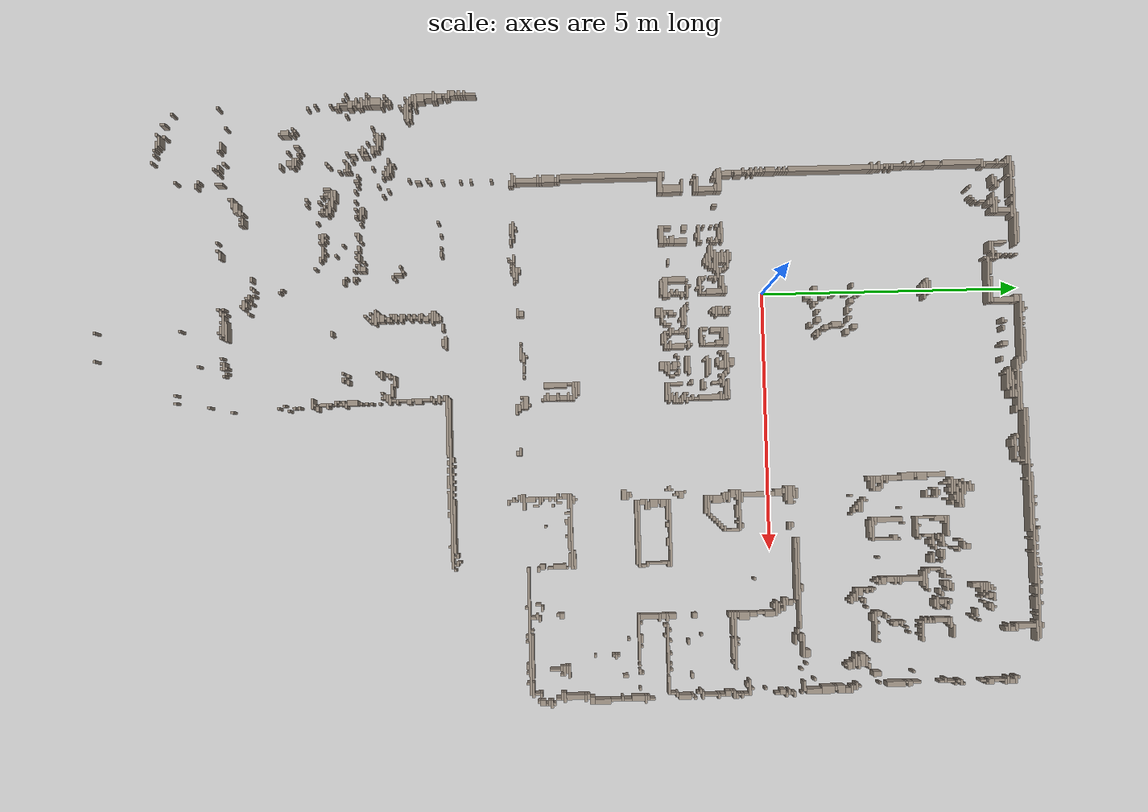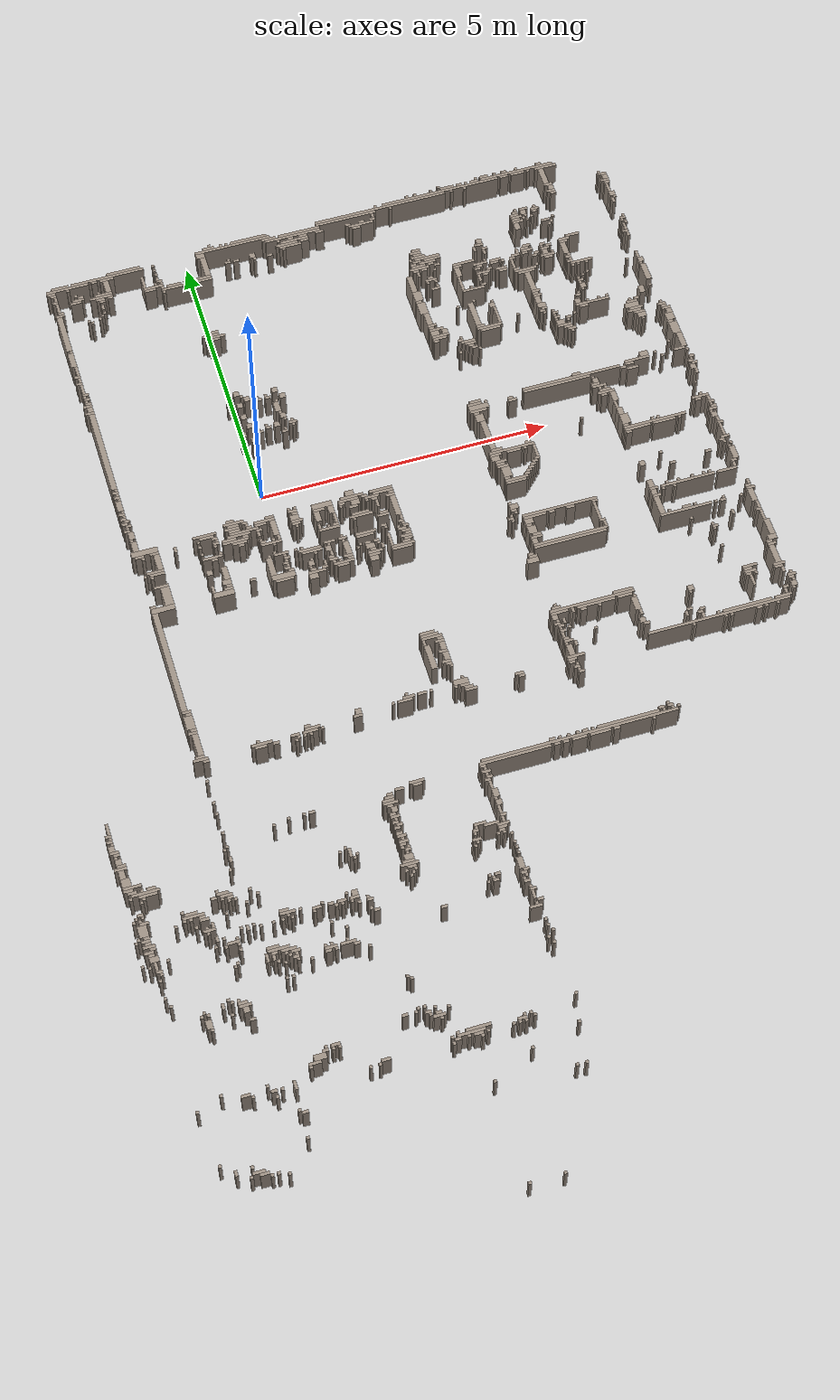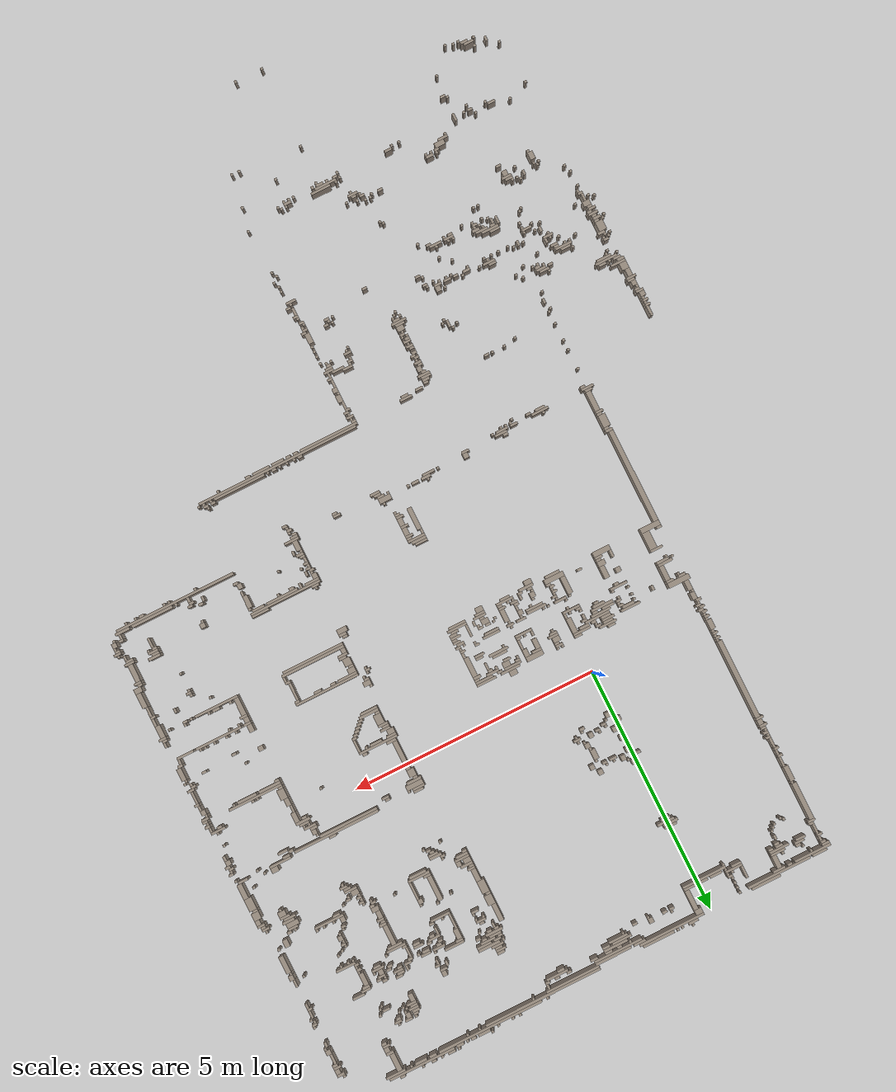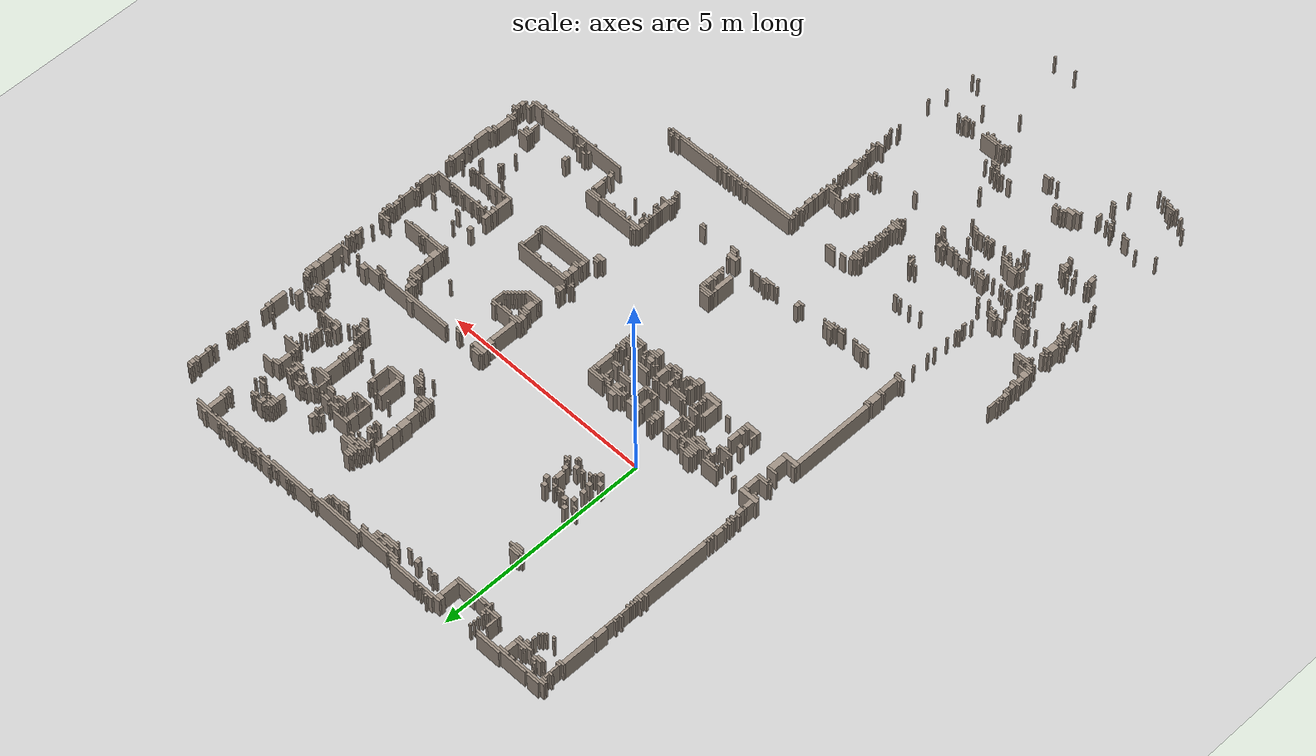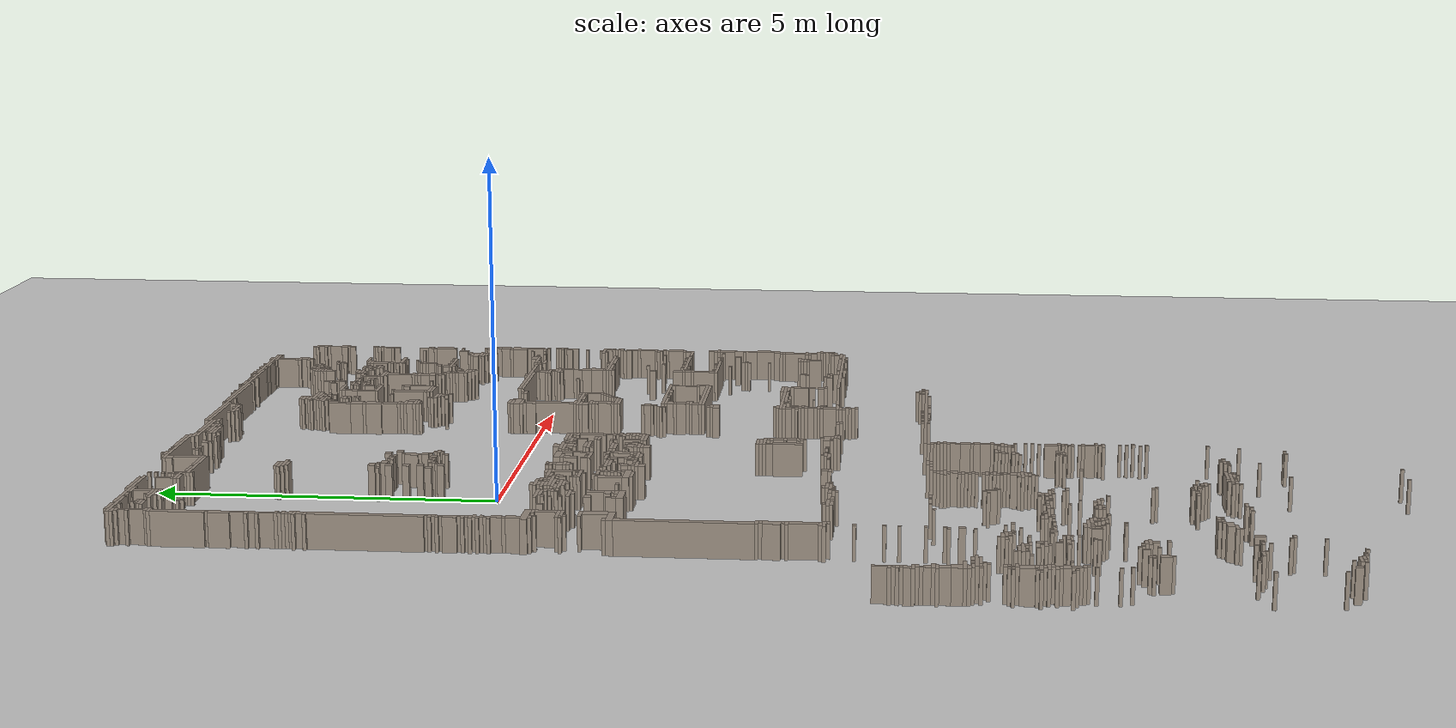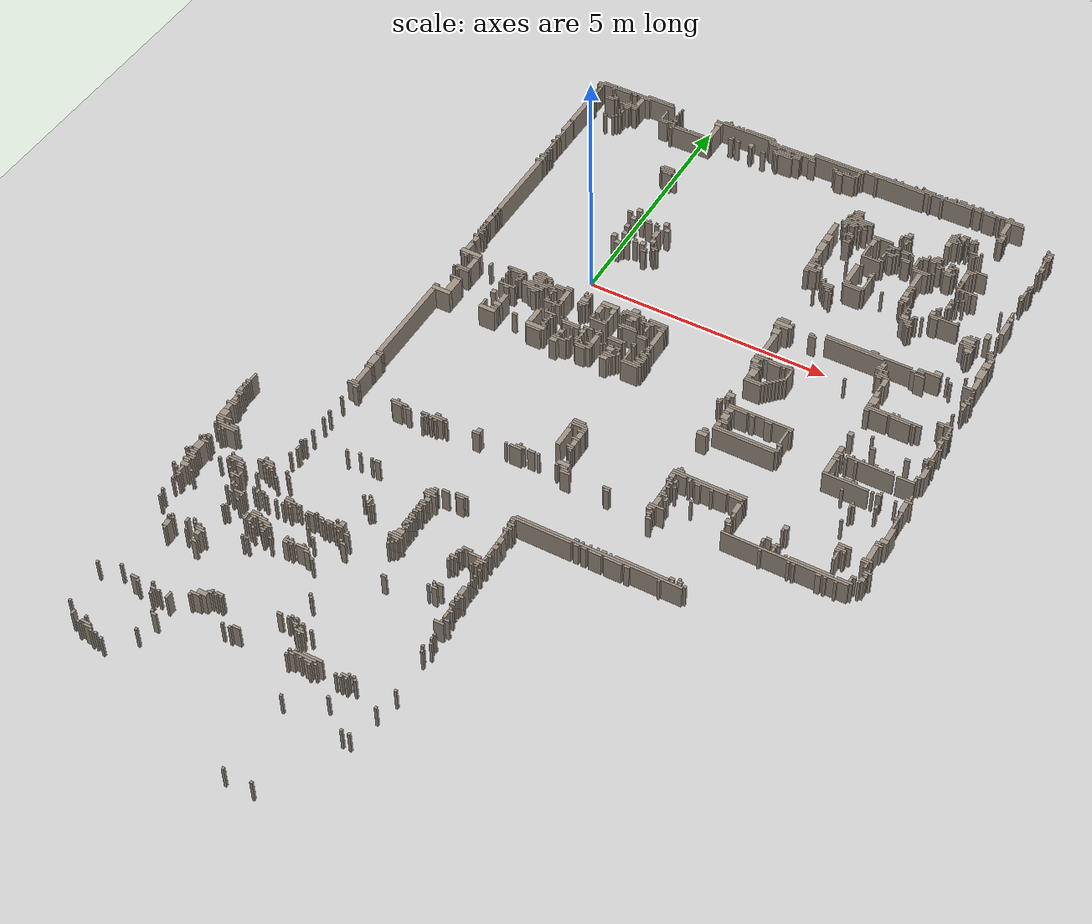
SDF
<?xml version="1.0" ?>
<sdf version="1.8">
  <world name="sala_real">
    <physics name="1ms" type="ignored"><max_step_size>0.001</max_step_size><real_time_factor>1.0</real_time_factor></physics>
    <plugin filename="gz-sim-physics-system" name="gz::sim::systems::Physics"/>
    <plugin filename="gz-sim-user-commands-system" name="gz::sim::systems::UserCommands"/>
    <plugin filename="gz-sim-scene-broadcaster-system" name="gz::sim::systems::SceneBroadcaster"/>
    <plugin filename="gz-sim-sensors-system" name="gz::sim::systems::Sensors"><render_engine>ogre2</render_engine></plugin>
    <light type="directional" name="sun">
      <cast_shadows>false</cast_shadows>
      <pose>0 0 10 0 0 0</pose>
      <diffuse>0.9 0.9 0.9 1</diffuse>
      <direction>-0.3 0.2 -0.9</direction>
    </light>
    <model name="ground_plane">
      <static>true</static>
      <link name="link">
        <collision name="col"><geometry><plane><normal>0 0 1</normal><size>100 100</size></plane></geometry></collision>
        <visual name="vis"><geometry><plane><normal>0 0 1</normal><size>100 100</size></plane></geometry>
          <material><ambient>0.8 0.8 0.8 1</ambient><diffuse>0.8 0.8 0.8 1</diffuse></material></visual>
      </link>
    </model>

    <model name="wall_0">
      <static>true</static>
      <pose>6.565 5.162 0.250 0 0 0</pose>
      <link name="link">
        <collision name="col">
          <geometry><box><size>0.100 0.050 0.500</size></box></geometry>
        </collision>
        <visual name="vis">
          <geometry><box><size>0.100 0.050 0.500</size></box></geometry>
          <material><ambient>0.6 0.55 0.5 1</ambient><diffuse>0.6 0.55 0.5 1</diffuse></material>
        </visual>
      </link>
    </model>
    <model name="wall_1">
      <static>true</static>
      <pose>-0.610 4.912 0.250 0 0 0</pose>
      <link name="link">
        <collision name="col">
          <geometry><box><size>0.050 0.050 0.500</size></box></geometry>
        </collision>
        <visual name="vis">
          <geometry><box><size>0.050 0.050 0.500</size></box></geometry>
          <material><ambient>0.6 0.55 0.5 1</ambient><diffuse>0.6 0.55 0.5 1</diffuse></material>
        </visual>
      </link>
    </model>
    <model name="wall_2">
      <static>true</static>
      <pose>-0.610 4.812 0.250 0 0 0</pose>
      <link name="link">
        <collision name="col">
          <geometry><box><size>0.050 0.050 0.500</size></box></geometry>
        </collision>
        <visual name="vis">
          <geometry><box><size>0.050 0.050 0.500</size></box></geometry>
          <material><ambient>0.6 0.55 0.5 1</ambient><diffuse>0.6 0.55 0.5 1</diffuse></material>
        </visual>
      </link>
    </model>
    <model name="wall_3">
      <static>true</static>
      <pose>2.090 4.812 0.250 0 0 0</pose>
      <link name="link">
        <collision name="col">
          <geometry><box><size>0.150 0.050 0.500</size></box></geometry>
        </collision>
        <visual name="vis">
          <geometry><box><size>0.150 0.050 0.500</size></box></geometry>
          <material><ambient>0.6 0.55 0.5 1</ambient><diffuse>0.6 0.55 0.5 1</diffuse></material>
        </visual>
      </link>
    </model>
    <model name="wall_4">
      <static>true</static>
      <pose>-2.435 4.762 0.250 0 0 0</pose>
      <link name="link">
        <collision name="col">
          <geometry><box><size>0.100 0.050 0.500</size></box></geometry>
        </collision>
        <visual name="vis">
          <geometry><box><size>0.100 0.050 0.500</size></box></geometry>
          <material><ambient>0.6 0.55 0.5 1</ambient><diffuse>0.6 0.55 0.5 1</diffuse></material>
        </visual>
      </link>
    </model>
    <model name="wall_5">
      <static>true</static>
      <pose>-0.610 4.712 0.250 0 0 0</pose>
      <link name="link">
        <collision name="col">
          <geometry><box><size>0.050 0.050 0.500</size></box></geometry>
        </collision>
        <visual name="vis">
          <geometry><box><size>0.050 0.050 0.500</size></box></geometry>
          <material><ambient>0.6 0.55 0.5 1</ambient><diffuse>0.6 0.55 0.5 1</diffuse></material>
        </visual>
      </link>
    </model>
    <model name="wall_6">
      <static>true</static>
      <pose>-2.410 4.687 0.250 0 0 0</pose>
      <link name="link">
        <collision name="col">
          <geometry><box><size>0.050 0.100 0.500</size></box></geometry>
        </collision>
        <visual name="vis">
          <geometry><box><size>0.050 0.100 0.500</size></box></geometry>
          <material><ambient>0.6 0.55 0.5 1</ambient><diffuse>0.6 0.55 0.5 1</diffuse></material>
        </visual>
      </link>
    </model>
    <model name="wall_7">
      <static>true</static>
      <pose>6.590 4.662 0.250 0 0 0</pose>
      <link name="link">
        <collision name="col">
          <geometry><box><size>0.150 0.050 0.500</size></box></geometry>
        </collision>
        <visual name="vis">
          <geometry><box><size>0.150 0.050 0.500</size></box></geometry>
          <material><ambient>0.6 0.55 0.5 1</ambient><diffuse>0.6 0.55 0.5 1</diffuse></material>
        </visual>
      </link>
    </model>
    <model name="wall_8">
      <static>true</static>
      <pose>-1.485 4.712 0.250 0 0 0</pose>
      <link name="link">
        <collision name="col">
          <geometry><box><size>0.100 0.250 0.500</size></box></geometry>
        </collision>
        <visual name="vis">
          <geometry><box><size>0.100 0.250 0.500</size></box></geometry>
          <material><ambient>0.6 0.55 0.5 1</ambient><diffuse>0.6 0.55 0.5 1</diffuse></material>
        </visual>
      </link>
    </model>
    <model name="wall_9">
      <static>true</static>
      <pose>6.615 4.587 0.250 0 0 0</pose>
      <link name="link">
        <collision name="col">
          <geometry><box><size>0.100 0.100 0.500</size></box></geometry>
        </collision>
        <visual name="vis">
          <geometry><box><size>0.100 0.100 0.500</size></box></geometry>
          <material><ambient>0.6 0.55 0.5 1</ambient><diffuse>0.6 0.55 0.5 1</diffuse></material>
        </visual>
      </link>
    </model>
    <model name="wall_10">
      <static>true</static>
      <pose>7.590 4.612 0.250 0 0 0</pose>
      <link name="link">
        <collision name="col">
          <geometry><box><size>0.150 0.050 0.500</size></box></geometry>
        </collision>
        <visual name="vis">
          <geometry><box><size>0.150 0.050 0.500</size></box></geometry>
          <material><ambient>0.6 0.55 0.5 1</ambient><diffuse>0.6 0.55 0.5 1</diffuse></material>
        </visual>
      </link>
    </model>
    <model name="wall_11">
      <static>true</static>
      <pose>-0.560 4.512 0.250 0 0 0</pose>
      <link name="link">
        <collision name="col">
          <geometry><box><size>0.050 0.050 0.500</size></box></geometry>
        </collision>
        <visual name="vis">
          <geometry><box><size>0.050 0.050 0.500</size></box></geometry>
          <material><ambient>0.6 0.55 0.5 1</ambient><diffuse>0.6 0.55 0.5 1</diffuse></material>
        </visual>
      </link>
    </model>
    <model name="wall_12">
      <static>true</static>
      <pose>7.615 4.537 0.250 0 0 0</pose>
      <link name="link">
        <collision name="col">
          <geometry><box><size>0.100 0.100 0.500</size></box></geometry>
        </collision>
        <visual name="vis">
          <geometry><box><size>0.100 0.100 0.500</size></box></geometry>
          <material><ambient>0.6 0.55 0.5 1</ambient><diffuse>0.6 0.55 0.5 1</diffuse></material>
        </visual>
      </link>
    </model>
    <model name="wall_13">
      <static>true</static>
      <pose>-1.660 4.612 0.250 0 0 0</pose>
      <link name="link">
        <collision name="col">
          <geometry><box><size>0.050 0.050 0.500</size></box></geometry>
        </collision>
        <visual name="vis">
          <geometry><box><size>0.050 0.050 0.500</size></box></geometry>
          <material><ambient>0.6 0.55 0.5 1</ambient><diffuse>0.6 0.55 0.5 1</diffuse></material>
        </visual>
      </link>
    </model>
    <model name="wall_14">
      <static>true</static>
      <pose>-0.560 4.412 0.250 0 0 0</pose>
      <link name="link">
        <collision name="col">
          <geometry><box><size>0.050 0.050 0.500</size></box></geometry>
        </collision>
        <visual name="vis">
          <geometry><box><size>0.050 0.050 0.500</size></box></geometry>
          <material><ambient>0.6 0.55 0.5 1</ambient><diffuse>0.6 0.55 0.5 1</diffuse></material>
        </visual>
      </link>
    </model>
    <model name="wall_15">
      <static>true</static>
      <pose>-2.435 4.612 0.250 0 0 0</pose>
      <link name="link">
        <collision name="col">
          <geometry><box><size>0.100 0.050 0.500</size></box></geometry>
        </collision>
        <visual name="vis">
          <geometry><box><size>0.100 0.050 0.500</size></box></geometry>
          <material><ambient>0.6 0.55 0.5 1</ambient><diffuse>0.6 0.55 0.5 1</diffuse></material>
        </visual>
      </link>
    </model>
    <model name="wall_16">
      <static>true</static>
      <pose>-1.660 4.287 0.250 0 0 0</pose>
      <link name="link">
        <collision name="col">
          <geometry><box><size>0.050 0.100 0.500</size></box></geometry>
        </collision>
        <visual name="vis">
          <geometry><box><size>0.050 0.100 0.500</size></box></geometry>
          <material><ambient>0.6 0.55 0.5 1</ambient><diffuse>0.6 0.55 0.5 1</diffuse></material>
        </visual>
      </link>
    </model>
    <model name="wall_17">
      <static>true</static>
      <pose>7.615 4.412 0.250 0 0 0</pose>
      <link name="link">
        <collision name="col">
          <geometry><box><size>0.100 0.050 0.500</size></box></geometry>
        </collision>
        <visual name="vis">
          <geometry><box><size>0.100 0.050 0.500</size></box></geometry>
          <material><ambient>0.6 0.55 0.5 1</ambient><diffuse>0.6 0.55 0.5 1</diffuse></material>
        </visual>
      </link>
    </model>
    <model name="wall_18">
      <static>true</static>
      <pose>5.790 4.162 0.250 0 0 0</pose>
      <link name="link">
        <collision name="col">
          <geometry><box><size>0.150 0.050 0.500</size></box></geometry>
        </collision>
        <visual name="vis">
          <geometry><box><size>0.150 0.050 0.500</size></box></geometry>
          <material><ambient>0.6 0.55 0.5 1</ambient><diffuse>0.6 0.55 0.5 1</diffuse></material>
        </visual>
      </link>
    </model>
    <model name="wall_19">
      <static>true</static>
      <pose>5.815 4.112 0.250 0 0 0</pose>
      <link name="link">
        <collision name="col">
          <geometry><box><size>0.200 0.050 0.500</size></box></geometry>
        </collision>
        <visual name="vis">
          <geometry><box><size>0.200 0.050 0.500</size></box></geometry>
          <material><ambient>0.6 0.55 0.5 1</ambient><diffuse>0.6 0.55 0.5 1</diffuse></material>
        </visual>
      </link>
    </model>
    <model name="wall_20">
      <static>true</static>
      <pose>5.990 4.112 0.250 0 0 0</pose>
      <link name="link">
        <collision name="col">
          <geometry><box><size>0.050 0.050 0.500</size></box></geometry>
        </collision>
        <visual name="vis">
          <geometry><box><size>0.050 0.050 0.500</size></box></geometry>
          <material><ambient>0.6 0.55 0.5 1</ambient><diffuse>0.6 0.55 0.5 1</diffuse></material>
        </visual>
      </link>
    </model>
    <model name="wall_21">
      <static>true</static>
      <pose>7.590 4.287 0.250 0 0 0</pose>
      <link name="link">
        <collision name="col">
          <geometry><box><size>0.050 0.200 0.500</size></box></geometry>
        </collision>
        <visual name="vis">
          <geometry><box><size>0.050 0.200 0.500</size></box></geometry>
          <material><ambient>0.6 0.55 0.5 1</ambient><diffuse>0.6 0.55 0.5 1</diffuse></material>
        </visual>
      </link>
    </model>
    <model name="wall_22">
      <static>true</static>
      <pose>3.890 3.912 0.250 0 0 0</pose>
      <link name="link">
        <collision name="col">
          <geometry><box><size>0.150 0.050 0.500</size></box></geometry>
        </collision>
        <visual name="vis">
          <geometry><box><size>0.150 0.050 0.500</size></box></geometry>
          <material><ambient>0.6 0.55 0.5 1</ambient><diffuse>0.6 0.55 0.5 1</diffuse></material>
        </visual>
      </link>
    </model>
    <model name="wall_23">
      <static>true</static>
      <pose>6.340 5.062 0.250 0 0 0</pose>
      <link name="link">
        <collision name="col">
          <geometry><box><size>0.050 0.050 0.500</size></box></geometry>
        </collision>
        <visual name="vis">
          <geometry><box><size>0.050 0.050 0.500</size></box></geometry>
          <material><ambient>0.6 0.55 0.5 1</ambient><diffuse>0.6 0.55 0.5 1</diffuse></material>
        </visual>
      </link>
    </model>
    <model name="wall_24">
      <static>true</static>
      <pose>3.740 4.962 0.250 0 0 0</pose>
      <link name="link">
        <collision name="col">
          <geometry><box><size>0.050 0.050 0.500</size></box></geometry>
        </collision>
        <visual name="vis">
          <geometry><box><size>0.050 0.050 0.500</size></box></geometry>
          <material><ambient>0.6 0.55 0.5 1</ambient><diffuse>0.6 0.55 0.5 1</diffuse></material>
        </visual>
      </link>
    </model>
    <model name="wall_25">
      <static>true</static>
      <pose>4.890 5.012 0.250 0 0 0</pose>
      <link name="link">
        <collision name="col">
          <geometry><box><size>0.050 0.050 0.500</size></box></geometry>
        </collision>
        <visual name="vis">
          <geometry><box><size>0.050 0.050 0.500</size></box></geometry>
          <material><ambient>0.6 0.55 0.5 1</ambient><diffuse>0.6 0.55 0.5 1</diffuse></material>
        </visual>
      </link>
    </model>
    <model name="wall_26">
      <static>true</static>
      <pose>5.065 5.112 0.250 0 0 0</pose>
      <link name="link">
        <collision name="col">
          <geometry><box><size>0.100 0.050 0.500</size></box></geometry>
        </collision>
        <visual name="vis">
          <geometry><box><size>0.100 0.050 0.500</size></box></geometry>
          <material><ambient>0.6 0.55 0.5 1</ambient><diffuse>0.6 0.55 0.5 1</diffuse></material>
        </visual>
      </link>
    </model>
    <model name="wall_27">
      <static>true</static>
      <pose>7.640 4.062 0.250 0 0 0</pose>
      <link name="link">
        <collision name="col">
          <geometry><box><size>0.050 0.050 0.500</size></box></geometry>
        </collision>
        <visual name="vis">
          <geometry><box><size>0.050 0.050 0.500</size></box></geometry>
          <material><ambient>0.6 0.55 0.5 1</ambient><diffuse>0.6 0.55 0.5 1</diffuse></material>
        </visual>
      </link>
    </model>
    <model name="wall_28">
      <static>true</static>
      <pose>7.615 4.137 0.250 0 0 0</pose>
      <link name="link">
        <collision name="col">
          <geometry><box><size>0.100 0.100 0.500</size></box></geometry>
        </collision>
        <visual name="vis">
          <geometry><box><size>0.100 0.100 0.500</size></box></geometry>
          <material><ambient>0.6 0.55 0.5 1</ambient><diffuse>0.6 0.55 0.5 1</diffuse></material>
        </visual>
      </link>
    </model>
    <model name="wall_29">
      <static>true</static>
      <pose>-2.410 4.487 0.250 0 0 0</pose>
      <link name="link">
        <collision name="col">
          <geometry><box><size>0.050 0.200 0.500</size></box></geometry>
        </collision>
        <visual name="vis">
          <geometry><box><size>0.050 0.200 0.500</size></box></geometry>
          <material><ambient>0.6 0.55 0.5 1</ambient><diffuse>0.6 0.55 0.5 1</diffuse></material>
        </visual>
      </link>
    </model>
    <model name="wall_30">
      <static>true</static>
      <pose>7.590 3.987 0.250 0 0 0</pose>
      <link name="link">
        <collision name="col">
          <geometry><box><size>0.050 0.100 0.500</size></box></geometry>
        </collision>
        <visual name="vis">
          <geometry><box><size>0.050 0.100 0.500</size></box></geometry>
          <material><ambient>0.6 0.55 0.5 1</ambient><diffuse>0.6 0.55 0.5 1</diffuse></material>
        </visual>
      </link>
    </model>
    <model name="wall_31">
      <static>true</static>
      <pose>-2.435 3.912 0.250 0 0 0</pose>
      <link name="link">
        <collision name="col">
          <geometry><box><size>0.100 0.750 0.500</size></box></geometry>
        </collision>
        <visual name="vis">
          <geometry><box><size>0.100 0.750 0.500</size></box></geometry>
          <material><ambient>0.6 0.55 0.5 1</ambient><diffuse>0.6 0.55 0.5 1</diffuse></material>
        </visual>
      </link>
    </model>
    <model name="wall_32">
      <static>true</static>
      <pose>3.765 3.612 0.250 0 0 0</pose>
      <link name="link">
        <collision name="col">
          <geometry><box><size>0.100 0.050 0.500</size></box></geometry>
        </collision>
        <visual name="vis">
          <geometry><box><size>0.100 0.050 0.500</size></box></geometry>
          <material><ambient>0.6 0.55 0.5 1</ambient><diffuse>0.6 0.55 0.5 1</diffuse></material>
        </visual>
      </link>
    </model>
    <model name="wall_33">
      <static>true</static>
      <pose>5.790 4.062 0.250 0 0 0</pose>
      <link name="link">
        <collision name="col">
          <geometry><box><size>0.150 0.050 0.500</size></box></geometry>
        </collision>
        <visual name="vis">
          <geometry><box><size>0.150 0.050 0.500</size></box></geometry>
          <material><ambient>0.6 0.55 0.5 1</ambient><diffuse>0.6 0.55 0.5 1</diffuse></material>
        </visual>
      </link>
    </model>
    <model name="wall_34">
      <static>true</static>
      <pose>7.640 3.612 0.250 0 0 0</pose>
      <link name="link">
        <collision name="col">
          <geometry><box><size>0.050 0.050 0.500</size></box></geometry>
        </collision>
        <visual name="vis">
          <geometry><box><size>0.050 0.050 0.500</size></box></geometry>
          <material><ambient>0.6 0.55 0.5 1</ambient><diffuse>0.6 0.55 0.5 1</diffuse></material>
        </visual>
      </link>
    </model>
    <model name="wall_35">
      <static>true</static>
      <pose>4.090 5.112 0.250 0 0 0</pose>
      <link name="link">
        <collision name="col">
          <geometry><box><size>0.050 0.050 0.500</size></box></geometry>
        </collision>
        <visual name="vis">
          <geometry><box><size>0.050 0.050 0.500</size></box></geometry>
          <material><ambient>0.6 0.55 0.5 1</ambient><diffuse>0.6 0.55 0.5 1</diffuse></material>
        </visual>
      </link>
    </model>
    <model name="wall_36">
      <static>true</static>
      <pose>7.590 3.512 0.250 0 0 0</pose>
      <link name="link">
        <collision name="col">
          <geometry><box><size>0.050 0.050 0.500</size></box></geometry>
        </collision>
        <visual name="vis">
          <geometry><box><size>0.050 0.050 0.500</size></box></geometry>
          <material><ambient>0.6 0.55 0.5 1</ambient><diffuse>0.6 0.55 0.5 1</diffuse></material>
        </visual>
      </link>
    </model>
    <model name="wall_37">
      <static>true</static>
      <pose>6.165 4.162 0.250 0 0 0</pose>
      <link name="link">
        <collision name="col">
          <geometry><box><size>0.100 0.050 0.500</size></box></geometry>
        </collision>
        <visual name="vis">
          <geometry><box><size>0.100 0.050 0.500</size></box></geometry>
          <material><ambient>0.6 0.55 0.5 1</ambient><diffuse>0.6 0.55 0.5 1</diffuse></material>
        </visual>
      </link>
    </model>
    <model name="wall_38">
      <static>true</static>
      <pose>5.540 5.162 0.250 0 0 0</pose>
      <link name="link">
        <collision name="col">
          <geometry><box><size>0.150 0.050 0.500</size></box></geometry>
        </collision>
        <visual name="vis">
          <geometry><box><size>0.150 0.050 0.500</size></box></geometry>
          <material><ambient>0.6 0.55 0.5 1</ambient><diffuse>0.6 0.55 0.5 1</diffuse></material>
        </visual>
      </link>
    </model>
    <model name="wall_39">
      <static>true</static>
      <pose>5.915 5.162 0.250 0 0 0</pose>
      <link name="link">
        <collision name="col">
          <geometry><box><size>0.100 0.050 0.500</size></box></geometry>
        </collision>
        <visual name="vis">
          <geometry><box><size>0.100 0.050 0.500</size></box></geometry>
          <material><ambient>0.6 0.55 0.5 1</ambient><diffuse>0.6 0.55 0.5 1</diffuse></material>
        </visual>
      </link>
    </model>
    <model name="wall_40">
      <static>true</static>
      <pose>6.065 3.412 0.250 0 0 0</pose>
      <link name="link">
        <collision name="col">
          <geometry><box><size>0.100 0.050 0.500</size></box></geometry>
        </collision>
        <visual name="vis">
          <geometry><box><size>0.100 0.050 0.500</size></box></geometry>
          <material><ambient>0.6 0.55 0.5 1</ambient><diffuse>0.6 0.55 0.5 1</diffuse></material>
        </visual>
      </link>
    </model>
    <model name="wall_41">
      <static>true</static>
      <pose>6.190 4.262 0.250 0 0 0</pose>
      <link name="link">
        <collision name="col">
          <geometry><box><size>0.050 0.050 0.500</size></box></geometry>
        </collision>
        <visual name="vis">
          <geometry><box><size>0.050 0.050 0.500</size></box></geometry>
          <material><ambient>0.6 0.55 0.5 1</ambient><diffuse>0.6 0.55 0.5 1</diffuse></material>
        </visual>
      </link>
    </model>
    <model name="wall_42">
      <static>true</static>
      <pose>7.590 3.362 0.250 0 0 0</pose>
      <link name="link">
        <collision name="col">
          <geometry><box><size>0.050 0.150 0.500</size></box></geometry>
        </collision>
        <visual name="vis">
          <geometry><box><size>0.050 0.150 0.500</size></box></geometry>
          <material><ambient>0.6 0.55 0.5 1</ambient><diffuse>0.6 0.55 0.5 1</diffuse></material>
        </visual>
      </link>
    </model>
    <model name="wall_43">
      <static>true</static>
      <pose>-2.410 3.512 0.250 0 0 0</pose>
      <link name="link">
        <collision name="col">
          <geometry><box><size>0.050 0.050 0.500</size></box></geometry>
        </collision>
        <visual name="vis">
          <geometry><box><size>0.050 0.050 0.500</size></box></geometry>
          <material><ambient>0.6 0.55 0.5 1</ambient><diffuse>0.6 0.55 0.5 1</diffuse></material>
        </visual>
      </link>
    </model>
    <model name="wall_44">
      <static>true</static>
      <pose>5.015 3.787 0.250 0 0 0</pose>
      <link name="link">
        <collision name="col">
          <geometry><box><size>0.100 0.100 0.500</size></box></geometry>
        </collision>
        <visual name="vis">
          <geometry><box><size>0.100 0.100 0.500</size></box></geometry>
          <material><ambient>0.6 0.55 0.5 1</ambient><diffuse>0.6 0.55 0.5 1</diffuse></material>
        </visual>
      </link>
    </model>
    <model name="wall_45">
      <static>true</static>
      <pose>4.890 3.312 0.250 0 0 0</pose>
      <link name="link">
        <collision name="col">
          <geometry><box><size>0.250 0.050 0.500</size></box></geometry>
        </collision>
        <visual name="vis">
          <geometry><box><size>0.250 0.050 0.500</size></box></geometry>
          <material><ambient>0.6 0.55 0.5 1</ambient><diffuse>0.6 0.55 0.5 1</diffuse></material>
        </visual>
      </link>
    </model>
    <model name="wall_46">
      <static>true</static>
      <pose>6.090 3.312 0.250 0 0 0</pose>
      <link name="link">
        <collision name="col">
          <geometry><box><size>0.150 0.050 0.500</size></box></geometry>
        </collision>
        <visual name="vis">
          <geometry><box><size>0.150 0.050 0.500</size></box></geometry>
          <material><ambient>0.6 0.55 0.5 1</ambient><diffuse>0.6 0.55 0.5 1</diffuse></material>
        </visual>
      </link>
    </model>
    <model name="wall_47">
      <static>true</static>
      <pose>4.040 3.162 0.250 0 0 0</pose>
      <link name="link">
        <collision name="col">
          <geometry><box><size>0.050 0.050 0.500</size></box></geometry>
        </collision>
        <visual name="vis">
          <geometry><box><size>0.050 0.050 0.500</size></box></geometry>
          <material><ambient>0.6 0.55 0.5 1</ambient><diffuse>0.6 0.55 0.5 1</diffuse></material>
        </visual>
      </link>
    </model>
    <model name="wall_48">
      <static>true</static>
      <pose>6.440 3.962 0.250 0 0 0</pose>
      <link name="link">
        <collision name="col">
          <geometry><box><size>0.050 0.050 0.500</size></box></geometry>
        </collision>
        <visual name="vis">
          <geometry><box><size>0.050 0.050 0.500</size></box></geometry>
          <material><ambient>0.6 0.55 0.5 1</ambient><diffuse>0.6 0.55 0.5 1</diffuse></material>
        </visual>
      </link>
    </model>
    <model name="wall_49">
      <static>true</static>
      <pose>5.465 3.262 0.250 0 0 0</pose>
      <link name="link">
        <collision name="col">
          <geometry><box><size>0.100 0.050 0.500</size></box></geometry>
        </collision>
        <visual name="vis">
          <geometry><box><size>0.100 0.050 0.500</size></box></geometry>
          <material><ambient>0.6 0.55 0.5 1</ambient><diffuse>0.6 0.55 0.5 1</diffuse></material>
        </visual>
      </link>
    </model>
    <model name="wall_50">
      <static>true</static>
      <pose>5.840 4.262 0.250 0 0 0</pose>
      <link name="link">
        <collision name="col">
          <geometry><box><size>0.050 0.050 0.500</size></box></geometry>
        </collision>
        <visual name="vis">
          <geometry><box><size>0.050 0.050 0.500</size></box></geometry>
          <material><ambient>0.6 0.55 0.5 1</ambient><diffuse>0.6 0.55 0.5 1</diffuse></material>
        </visual>
      </link>
    </model>
    <model name="wall_51">
      <static>true</static>
      <pose>6.415 3.212 0.250 0 0 0</pose>
      <link name="link">
        <collision name="col">
          <geometry><box><size>0.100 0.250 0.500</size></box></geometry>
        </collision>
        <visual name="vis">
          <geometry><box><size>0.100 0.250 0.500</size></box></geometry>
          <material><ambient>0.6 0.55 0.5 1</ambient><diffuse>0.6 0.55 0.5 1</diffuse></material>
        </visual>
      </link>
    </model>
    <model name="wall_52">
      <static>true</static>
      <pose>-2.435 3.337 0.250 0 0 0</pose>
      <link name="link">
        <collision name="col">
          <geometry><box><size>0.100 0.300 0.500</size></box></geometry>
        </collision>
        <visual name="vis">
          <geometry><box><size>0.100 0.300 0.500</size></box></geometry>
          <material><ambient>0.6 0.55 0.5 1</ambient><diffuse>0.6 0.55 0.5 1</diffuse></material>
        </visual>
      </link>
    </model>
    <model name="wall_53">
      <static>true</static>
      <pose>6.440 3.062 0.250 0 0 0</pose>
      <link name="link">
        <collision name="col">
          <geometry><box><size>0.050 0.050 0.500</size></box></geometry>
        </collision>
        <visual name="vis">
          <geometry><box><size>0.050 0.050 0.500</size></box></geometry>
          <material><ambient>0.6 0.55 0.5 1</ambient><diffuse>0.6 0.55 0.5 1</diffuse></material>
        </visual>
      </link>
    </model>
    <model name="wall_54">
      <static>true</static>
      <pose>-2.410 3.087 0.250 0 0 0</pose>
      <link name="link">
        <collision name="col">
          <geometry><box><size>0.050 0.200 0.500</size></box></geometry>
        </collision>
        <visual name="vis">
          <geometry><box><size>0.050 0.200 0.500</size></box></geometry>
          <material><ambient>0.6 0.55 0.5 1</ambient><diffuse>0.6 0.55 0.5 1</diffuse></material>
        </visual>
      </link>
    </model>
    <model name="wall_55">
      <static>true</static>
      <pose>6.415 3.012 0.250 0 0 0</pose>
      <link name="link">
        <collision name="col">
          <geometry><box><size>0.100 0.050 0.500</size></box></geometry>
        </collision>
        <visual name="vis">
          <geometry><box><size>0.100 0.050 0.500</size></box></geometry>
          <material><ambient>0.6 0.55 0.5 1</ambient><diffuse>0.6 0.55 0.5 1</diffuse></material>
        </visual>
      </link>
    </model>
    <model name="wall_56">
      <static>true</static>
      <pose>4.815 3.212 0.250 0 0 0</pose>
      <link name="link">
        <collision name="col">
          <geometry><box><size>0.100 0.050 0.500</size></box></geometry>
        </collision>
        <visual name="vis">
          <geometry><box><size>0.100 0.050 0.500</size></box></geometry>
          <material><ambient>0.6 0.55 0.5 1</ambient><diffuse>0.6 0.55 0.5 1</diffuse></material>
        </visual>
      </link>
    </model>
    <model name="wall_57">
      <static>true</static>
      <pose>-2.435 2.962 0.250 0 0 0</pose>
      <link name="link">
        <collision name="col">
          <geometry><box><size>0.100 0.050 0.500</size></box></geometry>
        </collision>
        <visual name="vis">
          <geometry><box><size>0.100 0.050 0.500</size></box></geometry>
          <material><ambient>0.6 0.55 0.5 1</ambient><diffuse>0.6 0.55 0.5 1</diffuse></material>
        </visual>
      </link>
    </model>
    <model name="wall_58">
      <static>true</static>
      <pose>3.615 3.212 0.250 0 0 0</pose>
      <link name="link">
        <collision name="col">
          <geometry><box><size>0.100 0.350 0.500</size></box></geometry>
        </collision>
        <visual name="vis">
          <geometry><box><size>0.100 0.350 0.500</size></box></geometry>
          <material><ambient>0.6 0.55 0.5 1</ambient><diffuse>0.6 0.55 0.5 1</diffuse></material>
        </visual>
      </link>
    </model>
    <model name="wall_59">
      <static>true</static>
      <pose>4.615 3.412 0.250 0 0 0</pose>
      <link name="link">
        <collision name="col">
          <geometry><box><size>0.400 0.050 0.500</size></box></geometry>
        </collision>
        <visual name="vis">
          <geometry><box><size>0.400 0.050 0.500</size></box></geometry>
          <material><ambient>0.6 0.55 0.5 1</ambient><diffuse>0.6 0.55 0.5 1</diffuse></material>
        </visual>
      </link>
    </model>
    <model name="wall_60">
      <static>true</static>
      <pose>6.440 2.962 0.250 0 0 0</pose>
      <link name="link">
        <collision name="col">
          <geometry><box><size>0.050 0.050 0.500</size></box></geometry>
        </collision>
        <visual name="vis">
          <geometry><box><size>0.050 0.050 0.500</size></box></geometry>
          <material><ambient>0.6 0.55 0.5 1</ambient><diffuse>0.6 0.55 0.5 1</diffuse></material>
        </visual>
      </link>
    </model>
    <model name="wall_61">
      <static>true</static>
      <pose>-2.410 2.887 0.250 0 0 0</pose>
      <link name="link">
        <collision name="col">
          <geometry><box><size>0.050 0.100 0.500</size></box></geometry>
        </collision>
        <visual name="vis">
          <geometry><box><size>0.050 0.100 0.500</size></box></geometry>
          <material><ambient>0.6 0.55 0.5 1</ambient><diffuse>0.6 0.55 0.5 1</diffuse></material>
        </visual>
      </link>
    </model>
    <model name="wall_62">
      <static>true</static>
      <pose>3.640 2.937 0.250 0 0 0</pose>
      <link name="link">
        <collision name="col">
          <geometry><box><size>0.150 0.200 0.500</size></box></geometry>
        </collision>
        <visual name="vis">
          <geometry><box><size>0.150 0.200 0.500</size></box></geometry>
          <material><ambient>0.6 0.55 0.5 1</ambient><diffuse>0.6 0.55 0.5 1</diffuse></material>
        </visual>
      </link>
    </model>
    <model name="wall_63">
      <static>true</static>
      <pose>7.590 3.187 0.250 0 0 0</pose>
      <link name="link">
        <collision name="col">
          <geometry><box><size>0.050 0.100 0.500</size></box></geometry>
        </collision>
        <visual name="vis">
          <geometry><box><size>0.050 0.100 0.500</size></box></geometry>
          <material><ambient>0.6 0.55 0.5 1</ambient><diffuse>0.6 0.55 0.5 1</diffuse></material>
        </visual>
      </link>
    </model>
    <model name="wall_64">
      <static>true</static>
      <pose>7.615 3.562 0.250 0 0 0</pose>
      <link name="link">
        <collision name="col">
          <geometry><box><size>0.100 0.050 0.500</size></box></geometry>
        </collision>
        <visual name="vis">
          <geometry><box><size>0.100 0.050 0.500</size></box></geometry>
          <material><ambient>0.6 0.55 0.5 1</ambient><diffuse>0.6 0.55 0.5 1</diffuse></material>
        </visual>
      </link>
    </model>
    <model name="wall_65">
      <static>true</static>
      <pose>-2.385 4.362 0.250 0 0 0</pose>
      <link name="link">
        <collision name="col">
          <geometry><box><size>0.100 0.050 0.500</size></box></geometry>
        </collision>
        <visual name="vis">
          <geometry><box><size>0.100 0.050 0.500</size></box></geometry>
          <material><ambient>0.6 0.55 0.5 1</ambient><diffuse>0.6 0.55 0.5 1</diffuse></material>
        </visual>
      </link>
    </model>
    <model name="wall_66">
      <static>true</static>
      <pose>4.540 5.112 0.250 0 0 0</pose>
      <link name="link">
        <collision name="col">
          <geometry><box><size>0.050 0.050 0.500</size></box></geometry>
        </collision>
        <visual name="vis">
          <geometry><box><size>0.050 0.050 0.500</size></box></geometry>
          <material><ambient>0.6 0.55 0.5 1</ambient><diffuse>0.6 0.55 0.5 1</diffuse></material>
        </visual>
      </link>
    </model>
    <model name="wall_67">
      <static>true</static>
      <pose>6.540 2.812 0.250 0 0 0</pose>
      <link name="link">
        <collision name="col">
          <geometry><box><size>0.050 0.050 0.500</size></box></geometry>
        </collision>
        <visual name="vis">
          <geometry><box><size>0.050 0.050 0.500</size></box></geometry>
          <material><ambient>0.6 0.55 0.5 1</ambient><diffuse>0.6 0.55 0.5 1</diffuse></material>
        </visual>
      </link>
    </model>
    <model name="wall_68">
      <static>true</static>
      <pose>-2.410 2.687 0.250 0 0 0</pose>
      <link name="link">
        <collision name="col">
          <geometry><box><size>0.050 0.200 0.500</size></box></geometry>
        </collision>
        <visual name="vis">
          <geometry><box><size>0.050 0.200 0.500</size></box></geometry>
          <material><ambient>0.6 0.55 0.5 1</ambient><diffuse>0.6 0.55 0.5 1</diffuse></material>
        </visual>
      </link>
    </model>
    <model name="wall_69">
      <static>true</static>
      <pose>4.240 5.112 0.250 0 0 0</pose>
      <link name="link">
        <collision name="col">
          <geometry><box><size>0.050 0.050 0.500</size></box></geometry>
        </collision>
        <visual name="vis">
          <geometry><box><size>0.050 0.050 0.500</size></box></geometry>
          <material><ambient>0.6 0.55 0.5 1</ambient><diffuse>0.6 0.55 0.5 1</diffuse></material>
        </visual>
      </link>
    </model>
    <model name="wall_70">
      <static>true</static>
      <pose>4.465 3.237 0.250 0 0 0</pose>
      <link name="link">
        <collision name="col">
          <geometry><box><size>0.100 0.200 0.500</size></box></geometry>
        </collision>
        <visual name="vis">
          <geometry><box><size>0.100 0.200 0.500</size></box></geometry>
          <material><ambient>0.6 0.55 0.5 1</ambient><diffuse>0.6 0.55 0.5 1</diffuse></material>
        </visual>
      </link>
    </model>
    <model name="wall_71">
      <static>true</static>
      <pose>6.440 2.812 0.250 0 0 0</pose>
      <link name="link">
        <collision name="col">
          <geometry><box><size>0.050 0.050 0.500</size></box></geometry>
        </collision>
        <visual name="vis">
          <geometry><box><size>0.050 0.050 0.500</size></box></geometry>
          <material><ambient>0.6 0.55 0.5 1</ambient><diffuse>0.6 0.55 0.5 1</diffuse></material>
        </visual>
      </link>
    </model>
    <model name="wall_72">
      <static>true</static>
      <pose>7.590 2.712 0.250 0 0 0</pose>
      <link name="link">
        <collision name="col">
          <geometry><box><size>0.050 0.150 0.500</size></box></geometry>
        </collision>
        <visual name="vis">
          <geometry><box><size>0.050 0.150 0.500</size></box></geometry>
          <material><ambient>0.6 0.55 0.5 1</ambient><diffuse>0.6 0.55 0.5 1</diffuse></material>
        </visual>
      </link>
    </model>
    <model name="wall_73">
      <static>true</static>
      <pose>-2.385 2.562 0.250 0 0 0</pose>
      <link name="link">
        <collision name="col">
          <geometry><box><size>0.100 0.050 0.500</size></box></geometry>
        </collision>
        <visual name="vis">
          <geometry><box><size>0.100 0.050 0.500</size></box></geometry>
          <material><ambient>0.6 0.55 0.5 1</ambient><diffuse>0.6 0.55 0.5 1</diffuse></material>
        </visual>
      </link>
    </model>
    <model name="wall_74">
      <static>true</static>
      <pose>7.615 2.587 0.250 0 0 0</pose>
      <link name="link">
        <collision name="col">
          <geometry><box><size>0.100 0.100 0.500</size></box></geometry>
        </collision>
        <visual name="vis">
          <geometry><box><size>0.100 0.100 0.500</size></box></geometry>
          <material><ambient>0.6 0.55 0.5 1</ambient><diffuse>0.6 0.55 0.5 1</diffuse></material>
        </visual>
      </link>
    </model>
    <model name="wall_75">
      <static>true</static>
      <pose>-2.410 2.512 0.250 0 0 0</pose>
      <link name="link">
        <collision name="col">
          <geometry><box><size>0.050 0.050 0.500</size></box></geometry>
        </collision>
        <visual name="vis">
          <geometry><box><size>0.050 0.050 0.500</size></box></geometry>
          <material><ambient>0.6 0.55 0.5 1</ambient><diffuse>0.6 0.55 0.5 1</diffuse></material>
        </visual>
      </link>
    </model>
    <model name="wall_76">
      <static>true</static>
      <pose>4.815 2.862 0.250 0 0 0</pose>
      <link name="link">
        <collision name="col">
          <geometry><box><size>0.100 0.050 0.500</size></box></geometry>
        </collision>
        <visual name="vis">
          <geometry><box><size>0.100 0.050 0.500</size></box></geometry>
          <material><ambient>0.6 0.55 0.5 1</ambient><diffuse>0.6 0.55 0.5 1</diffuse></material>
        </visual>
      </link>
    </model>
    <model name="wall_77">
      <static>true</static>
      <pose>5.615 2.687 0.250 0 0 0</pose>
      <link name="link">
        <collision name="col">
          <geometry><box><size>0.100 0.400 0.500</size></box></geometry>
        </collision>
        <visual name="vis">
          <geometry><box><size>0.100 0.400 0.500</size></box></geometry>
          <material><ambient>0.6 0.55 0.5 1</ambient><diffuse>0.6 0.55 0.5 1</diffuse></material>
        </visual>
      </link>
    </model>
    <model name="wall_78">
      <static>true</static>
      <pose>6.440 2.512 0.250 0 0 0</pose>
      <link name="link">
        <collision name="col">
          <geometry><box><size>0.050 0.050 0.500</size></box></geometry>
        </collision>
        <visual name="vis">
          <geometry><box><size>0.050 0.050 0.500</size></box></geometry>
          <material><ambient>0.6 0.55 0.5 1</ambient><diffuse>0.6 0.55 0.5 1</diffuse></material>
        </visual>
      </link>
    </model>
    <model name="wall_79">
      <static>true</static>
      <pose>-2.385 2.462 0.250 0 0 0</pose>
      <link name="link">
        <collision name="col">
          <geometry><box><size>0.100 0.050 0.500</size></box></geometry>
        </collision>
        <visual name="vis">
          <geometry><box><size>0.100 0.050 0.500</size></box></geometry>
          <material><ambient>0.6 0.55 0.5 1</ambient><diffuse>0.6 0.55 0.5 1</diffuse></material>
        </visual>
      </link>
    </model>
    <model name="wall_80">
      <static>true</static>
      <pose>5.640 2.462 0.250 0 0 0</pose>
      <link name="link">
        <collision name="col">
          <geometry><box><size>0.150 0.050 0.500</size></box></geometry>
        </collision>
        <visual name="vis">
          <geometry><box><size>0.150 0.050 0.500</size></box></geometry>
          <material><ambient>0.6 0.55 0.5 1</ambient><diffuse>0.6 0.55 0.5 1</diffuse></material>
        </visual>
      </link>
    </model>
    <model name="wall_81">
      <static>true</static>
      <pose>6.465 2.462 0.250 0 0 0</pose>
      <link name="link">
        <collision name="col">
          <geometry><box><size>0.100 0.050 0.500</size></box></geometry>
        </collision>
        <visual name="vis">
          <geometry><box><size>0.100 0.050 0.500</size></box></geometry>
          <material><ambient>0.6 0.55 0.5 1</ambient><diffuse>0.6 0.55 0.5 1</diffuse></material>
        </visual>
      </link>
    </model>
    <model name="wall_82">
      <static>true</static>
      <pose>-2.410 4.312 0.250 0 0 0</pose>
      <link name="link">
        <collision name="col">
          <geometry><box><size>0.150 0.050 0.500</size></box></geometry>
        </collision>
        <visual name="vis">
          <geometry><box><size>0.150 0.050 0.500</size></box></geometry>
          <material><ambient>0.6 0.55 0.5 1</ambient><diffuse>0.6 0.55 0.5 1</diffuse></material>
        </visual>
      </link>
    </model>
    <model name="wall_83">
      <static>true</static>
      <pose>4.840 2.462 0.250 0 0 0</pose>
      <link name="link">
        <collision name="col">
          <geometry><box><size>0.050 0.050 0.500</size></box></geometry>
        </collision>
        <visual name="vis">
          <geometry><box><size>0.050 0.050 0.500</size></box></geometry>
          <material><ambient>0.6 0.55 0.5 1</ambient><diffuse>0.6 0.55 0.5 1</diffuse></material>
        </visual>
      </link>
    </model>
    <model name="wall_84">
      <static>true</static>
      <pose>5.615 2.412 0.250 0 0 0</pose>
      <link name="link">
        <collision name="col">
          <geometry><box><size>0.100 0.050 0.500</size></box></geometry>
        </collision>
        <visual name="vis">
          <geometry><box><size>0.100 0.050 0.500</size></box></geometry>
          <material><ambient>0.6 0.55 0.5 1</ambient><diffuse>0.6 0.55 0.5 1</diffuse></material>
        </visual>
      </link>
    </model>
    <model name="wall_85">
      <static>true</static>
      <pose>-2.385 2.362 0.250 0 0 0</pose>
      <link name="link">
        <collision name="col">
          <geometry><box><size>0.100 0.050 0.500</size></box></geometry>
        </collision>
        <visual name="vis">
          <geometry><box><size>0.100 0.050 0.500</size></box></geometry>
          <material><ambient>0.6 0.55 0.5 1</ambient><diffuse>0.6 0.55 0.5 1</diffuse></material>
        </visual>
      </link>
    </model>
    <model name="wall_86">
      <static>true</static>
      <pose>6.440 2.412 0.250 0 0 0</pose>
      <link name="link">
        <collision name="col">
          <geometry><box><size>0.050 0.050 0.500</size></box></geometry>
        </collision>
        <visual name="vis">
          <geometry><box><size>0.050 0.050 0.500</size></box></geometry>
          <material><ambient>0.6 0.55 0.5 1</ambient><diffuse>0.6 0.55 0.5 1</diffuse></material>
        </visual>
      </link>
    </model>
    <model name="wall_87">
      <static>true</static>
      <pose>3.665 2.412 0.250 0 0 0</pose>
      <link name="link">
        <collision name="col">
          <geometry><box><size>0.100 0.250 0.500</size></box></geometry>
        </collision>
        <visual name="vis">
          <geometry><box><size>0.100 0.250 0.500</size></box></geometry>
          <material><ambient>0.6 0.55 0.5 1</ambient><diffuse>0.6 0.55 0.5 1</diffuse></material>
        </visual>
      </link>
    </model>
    <model name="wall_88">
      <static>true</static>
      <pose>6.340 3.812 0.250 0 0 0</pose>
      <link name="link">
        <collision name="col">
          <geometry><box><size>0.050 0.050 0.500</size></box></geometry>
        </collision>
        <visual name="vis">
          <geometry><box><size>0.050 0.050 0.500</size></box></geometry>
          <material><ambient>0.6 0.55 0.5 1</ambient><diffuse>0.6 0.55 0.5 1</diffuse></material>
        </visual>
      </link>
    </model>
    <model name="wall_89">
      <static>true</static>
      <pose>-2.410 2.312 0.250 0 0 0</pose>
      <link name="link">
        <collision name="col">
          <geometry><box><size>0.150 0.050 0.500</size></box></geometry>
        </collision>
        <visual name="vis">
          <geometry><box><size>0.150 0.050 0.500</size></box></geometry>
          <material><ambient>0.6 0.55 0.5 1</ambient><diffuse>0.6 0.55 0.5 1</diffuse></material>
        </visual>
      </link>
    </model>
    <model name="wall_90">
      <static>true</static>
      <pose>5.640 2.362 0.250 0 0 0</pose>
      <link name="link">
        <collision name="col">
          <geometry><box><size>0.150 0.050 0.500</size></box></geometry>
        </collision>
        <visual name="vis">
          <geometry><box><size>0.150 0.050 0.500</size></box></geometry>
          <material><ambient>0.6 0.55 0.5 1</ambient><diffuse>0.6 0.55 0.5 1</diffuse></material>
        </visual>
      </link>
    </model>
    <model name="wall_91">
      <static>true</static>
      <pose>-2.385 2.237 0.250 0 0 0</pose>
      <link name="link">
        <collision name="col">
          <geometry><box><size>0.100 0.100 0.500</size></box></geometry>
        </collision>
        <visual name="vis">
          <geometry><box><size>0.100 0.100 0.500</size></box></geometry>
          <material><ambient>0.6 0.55 0.5 1</ambient><diffuse>0.6 0.55 0.5 1</diffuse></material>
        </visual>
      </link>
    </model>
    <model name="wall_92">
      <static>true</static>
      <pose>3.690 2.262 0.250 0 0 0</pose>
      <link name="link">
        <collision name="col">
          <geometry><box><size>0.150 0.050 0.500</size></box></geometry>
        </collision>
        <visual name="vis">
          <geometry><box><size>0.150 0.050 0.500</size></box></geometry>
          <material><ambient>0.6 0.55 0.5 1</ambient><diffuse>0.6 0.55 0.5 1</diffuse></material>
        </visual>
      </link>
    </model>
    <model name="wall_93">
      <static>true</static>
      <pose>5.190 5.112 0.250 0 0 0</pose>
      <link name="link">
        <collision name="col">
          <geometry><box><size>0.050 0.050 0.500</size></box></geometry>
        </collision>
        <visual name="vis">
          <geometry><box><size>0.050 0.050 0.500</size></box></geometry>
          <material><ambient>0.6 0.55 0.5 1</ambient><diffuse>0.6 0.55 0.5 1</diffuse></material>
        </visual>
      </link>
    </model>
    <model name="wall_94">
      <static>true</static>
      <pose>4.490 3.362 0.250 0 0 0</pose>
      <link name="link">
        <collision name="col">
          <geometry><box><size>0.150 0.050 0.500</size></box></geometry>
        </collision>
        <visual name="vis">
          <geometry><box><size>0.150 0.050 0.500</size></box></geometry>
          <material><ambient>0.6 0.55 0.5 1</ambient><diffuse>0.6 0.55 0.5 1</diffuse></material>
        </visual>
      </link>
    </model>
    <model name="wall_95">
      <static>true</static>
      <pose>5.615 2.262 0.250 0 0 0</pose>
      <link name="link">
        <collision name="col">
          <geometry><box><size>0.100 0.150 0.500</size></box></geometry>
        </collision>
        <visual name="vis">
          <geometry><box><size>0.100 0.150 0.500</size></box></geometry>
          <material><ambient>0.6 0.55 0.5 1</ambient><diffuse>0.6 0.55 0.5 1</diffuse></material>
        </visual>
      </link>
    </model>
    <model name="wall_96">
      <static>true</static>
      <pose>6.440 2.262 0.250 0 0 0</pose>
      <link name="link">
        <collision name="col">
          <geometry><box><size>0.050 0.050 0.500</size></box></geometry>
        </collision>
        <visual name="vis">
          <geometry><box><size>0.050 0.050 0.500</size></box></geometry>
          <material><ambient>0.6 0.55 0.5 1</ambient><diffuse>0.6 0.55 0.5 1</diffuse></material>
        </visual>
      </link>
    </model>
    <model name="wall_97">
      <static>true</static>
      <pose>6.640 2.612 0.250 0 0 0</pose>
      <link name="link">
        <collision name="col">
          <geometry><box><size>0.050 0.050 0.500</size></box></geometry>
        </collision>
        <visual name="vis">
          <geometry><box><size>0.050 0.050 0.500</size></box></geometry>
          <material><ambient>0.6 0.55 0.5 1</ambient><diffuse>0.6 0.55 0.5 1</diffuse></material>
        </visual>
      </link>
    </model>
    <model name="wall_98">
      <static>true</static>
      <pose>7.590 2.512 0.250 0 0 0</pose>
      <link name="link">
        <collision name="col">
          <geometry><box><size>0.050 0.050 0.500</size></box></geometry>
        </collision>
        <visual name="vis">
          <geometry><box><size>0.050 0.050 0.500</size></box></geometry>
          <material><ambient>0.6 0.55 0.5 1</ambient><diffuse>0.6 0.55 0.5 1</diffuse></material>
        </visual>
      </link>
    </model>
    <model name="wall_99">
      <static>true</static>
      <pose>3.740 2.162 0.250 0 0 0</pose>
      <link name="link">
        <collision name="col">
          <geometry><box><size>0.250 0.050 0.500</size></box></geometry>
        </collision>
        <visual name="vis">
          <geometry><box><size>0.250 0.050 0.500</size></box></geometry>
          <material><ambient>0.6 0.55 0.5 1</ambient><diffuse>0.6 0.55 0.5 1</diffuse></material>
        </visual>
      </link>
    </model>
    <model name="wall_100">
      <static>true</static>
      <pose>3.665 2.212 0.250 0 0 0</pose>
      <link name="link">
        <collision name="col">
          <geometry><box><size>0.100 0.050 0.500</size></box></geometry>
        </collision>
        <visual name="vis">
          <geometry><box><size>0.100 0.050 0.500</size></box></geometry>
          <material><ambient>0.6 0.55 0.5 1</ambient><diffuse>0.6 0.55 0.5 1</diffuse></material>
        </visual>
      </link>
    </model>
    <model name="wall_101">
      <static>true</static>
      <pose>5.815 4.212 0.250 0 0 0</pose>
      <link name="link">
        <collision name="col">
          <geometry><box><size>0.100 0.050 0.500</size></box></geometry>
        </collision>
        <visual name="vis">
          <geometry><box><size>0.100 0.050 0.500</size></box></geometry>
          <material><ambient>0.6 0.55 0.5 1</ambient><diffuse>0.6 0.55 0.5 1</diffuse></material>
        </visual>
      </link>
    </model>
    <model name="wall_102">
      <static>true</static>
      <pose>4.090 3.412 0.250 0 0 0</pose>
      <link name="link">
        <collision name="col">
          <geometry><box><size>0.050 0.050 0.500</size></box></geometry>
        </collision>
        <visual name="vis">
          <geometry><box><size>0.050 0.050 0.500</size></box></geometry>
          <material><ambient>0.6 0.55 0.5 1</ambient><diffuse>0.6 0.55 0.5 1</diffuse></material>
        </visual>
      </link>
    </model>
    <model name="wall_103">
      <static>true</static>
      <pose>5.790 1.962 0.250 0 0 0</pose>
      <link name="link">
        <collision name="col">
          <geometry><box><size>0.050 0.050 0.500</size></box></geometry>
        </collision>
        <visual name="vis">
          <geometry><box><size>0.050 0.050 0.500</size></box></geometry>
          <material><ambient>0.6 0.55 0.5 1</ambient><diffuse>0.6 0.55 0.5 1</diffuse></material>
        </visual>
      </link>
    </model>
    <model name="wall_104">
      <static>true</static>
      <pose>4.065 3.562 0.250 0 0 0</pose>
      <link name="link">
        <collision name="col">
          <geometry><box><size>0.100 0.050 0.500</size></box></geometry>
        </collision>
        <visual name="vis">
          <geometry><box><size>0.100 0.050 0.500</size></box></geometry>
          <material><ambient>0.6 0.55 0.5 1</ambient><diffuse>0.6 0.55 0.5 1</diffuse></material>
        </visual>
      </link>
    </model>
    <model name="wall_105">
      <static>true</static>
      <pose>5.815 1.912 0.250 0 0 0</pose>
      <link name="link">
        <collision name="col">
          <geometry><box><size>0.100 0.050 0.500</size></box></geometry>
        </collision>
        <visual name="vis">
          <geometry><box><size>0.100 0.050 0.500</size></box></geometry>
          <material><ambient>0.6 0.55 0.5 1</ambient><diffuse>0.6 0.55 0.5 1</diffuse></material>
        </visual>
      </link>
    </model>
    <model name="wall_106">
      <static>true</static>
      <pose>6.140 5.162 0.250 0 0 0</pose>
      <link name="link">
        <collision name="col">
          <geometry><box><size>0.050 0.050 0.500</size></box></geometry>
        </collision>
        <visual name="vis">
          <geometry><box><size>0.050 0.050 0.500</size></box></geometry>
          <material><ambient>0.6 0.55 0.5 1</ambient><diffuse>0.6 0.55 0.5 1</diffuse></material>
        </visual>
      </link>
    </model>
    <model name="wall_107">
      <static>true</static>
      <pose>5.790 1.862 0.250 0 0 0</pose>
      <link name="link">
        <collision name="col">
          <geometry><box><size>0.050 0.050 0.500</size></box></geometry>
        </collision>
        <visual name="vis">
          <geometry><box><size>0.050 0.050 0.500</size></box></geometry>
          <material><ambient>0.6 0.55 0.5 1</ambient><diffuse>0.6 0.55 0.5 1</diffuse></material>
        </visual>
      </link>
    </model>
    <model name="wall_108">
      <static>true</static>
      <pose>5.990 4.012 0.250 0 0 0</pose>
      <link name="link">
        <collision name="col">
          <geometry><box><size>0.050 0.050 0.500</size></box></geometry>
        </collision>
        <visual name="vis">
          <geometry><box><size>0.050 0.050 0.500</size></box></geometry>
          <material><ambient>0.6 0.55 0.5 1</ambient><diffuse>0.6 0.55 0.5 1</diffuse></material>
        </visual>
      </link>
    </model>
    <model name="wall_109">
      <static>true</static>
      <pose>0.065 1.837 0.250 0 0 0</pose>
      <link name="link">
        <collision name="col">
          <geometry><box><size>0.100 0.100 0.500</size></box></geometry>
        </collision>
        <visual name="vis">
          <geometry><box><size>0.100 0.100 0.500</size></box></geometry>
          <material><ambient>0.6 0.55 0.5 1</ambient><diffuse>0.6 0.55 0.5 1</diffuse></material>
        </visual>
      </link>
    </model>
    <model name="wall_110">
      <static>true</static>
      <pose>0.815 4.612 0.250 0 0 0</pose>
      <link name="link">
        <collision name="col">
          <geometry><box><size>0.100 0.050 0.500</size></box></geometry>
        </collision>
        <visual name="vis">
          <geometry><box><size>0.100 0.050 0.500</size></box></geometry>
          <material><ambient>0.6 0.55 0.5 1</ambient><diffuse>0.6 0.55 0.5 1</diffuse></material>
        </visual>
      </link>
    </model>
    <model name="wall_111">
      <static>true</static>
      <pose>7.640 3.462 0.250 0 0 0</pose>
      <link name="link">
        <collision name="col">
          <geometry><box><size>0.050 0.050 0.500</size></box></geometry>
        </collision>
        <visual name="vis">
          <geometry><box><size>0.050 0.050 0.500</size></box></geometry>
          <material><ambient>0.6 0.55 0.5 1</ambient><diffuse>0.6 0.55 0.5 1</diffuse></material>
        </visual>
      </link>
    </model>
    <model name="wall_112">
      <static>true</static>
      <pose>7.140 1.687 0.250 0 0 0</pose>
      <link name="link">
        <collision name="col">
          <geometry><box><size>0.250 0.100 0.500</size></box></geometry>
        </collision>
        <visual name="vis">
          <geometry><box><size>0.250 0.100 0.500</size></box></geometry>
          <material><ambient>0.6 0.55 0.5 1</ambient><diffuse>0.6 0.55 0.5 1</diffuse></material>
        </visual>
      </link>
    </model>
    <model name="wall_113">
      <static>true</static>
      <pose>0.690 4.662 0.250 0 0 0</pose>
      <link name="link">
        <collision name="col">
          <geometry><box><size>0.050 0.050 0.500</size></box></geometry>
        </collision>
        <visual name="vis">
          <geometry><box><size>0.050 0.050 0.500</size></box></geometry>
          <material><ambient>0.6 0.55 0.5 1</ambient><diffuse>0.6 0.55 0.5 1</diffuse></material>
        </visual>
      </link>
    </model>
    <model name="wall_114">
      <static>true</static>
      <pose>5.990 4.262 0.250 0 0 0</pose>
      <link name="link">
        <collision name="col">
          <geometry><box><size>0.150 0.050 0.500</size></box></geometry>
        </collision>
        <visual name="vis">
          <geometry><box><size>0.150 0.050 0.500</size></box></geometry>
          <material><ambient>0.6 0.55 0.5 1</ambient><diffuse>0.6 0.55 0.5 1</diffuse></material>
        </visual>
      </link>
    </model>
    <model name="wall_115">
      <static>true</static>
      <pose>0.665 4.612 0.250 0 0 0</pose>
      <link name="link">
        <collision name="col">
          <geometry><box><size>0.100 0.050 0.500</size></box></geometry>
        </collision>
        <visual name="vis">
          <geometry><box><size>0.100 0.050 0.500</size></box></geometry>
          <material><ambient>0.6 0.55 0.5 1</ambient><diffuse>0.6 0.55 0.5 1</diffuse></material>
        </visual>
      </link>
    </model>
    <model name="wall_116">
      <static>true</static>
      <pose>5.990 1.712 0.250 0 0 0</pose>
      <link name="link">
        <collision name="col">
          <geometry><box><size>0.050 0.050 0.500</size></box></geometry>
        </collision>
        <visual name="vis">
          <geometry><box><size>0.050 0.050 0.500</size></box></geometry>
          <material><ambient>0.6 0.55 0.5 1</ambient><diffuse>0.6 0.55 0.5 1</diffuse></material>
        </visual>
      </link>
    </model>
    <model name="wall_117">
      <static>true</static>
      <pose>0.065 1.587 0.250 0 0 0</pose>
      <link name="link">
        <collision name="col">
          <geometry><box><size>0.100 0.100 0.500</size></box></geometry>
        </collision>
        <visual name="vis">
          <geometry><box><size>0.100 0.100 0.500</size></box></geometry>
          <material><ambient>0.6 0.55 0.5 1</ambient><diffuse>0.6 0.55 0.5 1</diffuse></material>
        </visual>
      </link>
    </model>
    <model name="wall_118">
      <static>true</static>
      <pose>7.690 1.462 0.250 0 0 0</pose>
      <link name="link">
        <collision name="col">
          <geometry><box><size>0.150 0.050 0.500</size></box></geometry>
        </collision>
        <visual name="vis">
          <geometry><box><size>0.150 0.050 0.500</size></box></geometry>
          <material><ambient>0.6 0.55 0.5 1</ambient><diffuse>0.6 0.55 0.5 1</diffuse></material>
        </visual>
      </link>
    </model>
    <model name="wall_119">
      <static>true</static>
      <pose>0.690 1.512 0.250 0 0 0</pose>
      <link name="link">
        <collision name="col">
          <geometry><box><size>0.050 0.050 0.500</size></box></geometry>
        </collision>
        <visual name="vis">
          <geometry><box><size>0.050 0.050 0.500</size></box></geometry>
          <material><ambient>0.6 0.55 0.5 1</ambient><diffuse>0.6 0.55 0.5 1</diffuse></material>
        </visual>
      </link>
    </model>
    <model name="wall_120">
      <static>true</static>
      <pose>0.715 1.737 0.250 0 0 0</pose>
      <link name="link">
        <collision name="col">
          <geometry><box><size>0.100 0.100 0.500</size></box></geometry>
        </collision>
        <visual name="vis">
          <geometry><box><size>0.100 0.100 0.500</size></box></geometry>
          <material><ambient>0.6 0.55 0.5 1</ambient><diffuse>0.6 0.55 0.5 1</diffuse></material>
        </visual>
      </link>
    </model>
    <model name="wall_121">
      <static>true</static>
      <pose>7.665 1.512 0.250 0 0 0</pose>
      <link name="link">
        <collision name="col">
          <geometry><box><size>0.100 0.050 0.500</size></box></geometry>
        </collision>
        <visual name="vis">
          <geometry><box><size>0.100 0.050 0.500</size></box></geometry>
          <material><ambient>0.6 0.55 0.5 1</ambient><diffuse>0.6 0.55 0.5 1</diffuse></material>
        </visual>
      </link>
    </model>
    <model name="wall_122">
      <static>true</static>
      <pose>0.740 5.012 0.250 0 0 0</pose>
      <link name="link">
        <collision name="col">
          <geometry><box><size>0.050 0.050 0.500</size></box></geometry>
        </collision>
        <visual name="vis">
          <geometry><box><size>0.050 0.050 0.500</size></box></geometry>
          <material><ambient>0.6 0.55 0.5 1</ambient><diffuse>0.6 0.55 0.5 1</diffuse></material>
        </visual>
      </link>
    </model>
    <model name="wall_123">
      <static>true</static>
      <pose>7.690 1.262 0.250 0 0 0</pose>
      <link name="link">
        <collision name="col">
          <geometry><box><size>0.150 0.150 0.500</size></box></geometry>
        </collision>
        <visual name="vis">
          <geometry><box><size>0.150 0.150 0.500</size></box></geometry>
          <material><ambient>0.6 0.55 0.5 1</ambient><diffuse>0.6 0.55 0.5 1</diffuse></material>
        </visual>
      </link>
    </model>
    <model name="wall_124">
      <static>true</static>
      <pose>0.390 1.662 0.250 0 0 0</pose>
      <link name="link">
        <collision name="col">
          <geometry><box><size>0.050 0.050 0.500</size></box></geometry>
        </collision>
        <visual name="vis">
          <geometry><box><size>0.050 0.050 0.500</size></box></geometry>
          <material><ambient>0.6 0.55 0.5 1</ambient><diffuse>0.6 0.55 0.5 1</diffuse></material>
        </visual>
      </link>
    </model>
    <model name="wall_125">
      <static>true</static>
      <pose>0.565 1.612 0.250 0 0 0</pose>
      <link name="link">
        <collision name="col">
          <geometry><box><size>0.100 0.050 0.500</size></box></geometry>
        </collision>
        <visual name="vis">
          <geometry><box><size>0.100 0.050 0.500</size></box></geometry>
          <material><ambient>0.6 0.55 0.5 1</ambient><diffuse>0.6 0.55 0.5 1</diffuse></material>
        </visual>
      </link>
    </model>
    <model name="wall_126">
      <static>true</static>
      <pose>0.265 4.637 0.250 0 0 0</pose>
      <link name="link">
        <collision name="col">
          <geometry><box><size>0.100 0.400 0.500</size></box></geometry>
        </collision>
        <visual name="vis">
          <geometry><box><size>0.100 0.400 0.500</size></box></geometry>
          <material><ambient>0.6 0.55 0.5 1</ambient><diffuse>0.6 0.55 0.5 1</diffuse></material>
        </visual>
      </link>
    </model>
    <model name="wall_127">
      <static>true</static>
      <pose>0.840 1.062 0.250 0 0 0</pose>
      <link name="link">
        <collision name="col">
          <geometry><box><size>0.050 0.050 0.500</size></box></geometry>
        </collision>
        <visual name="vis">
          <geometry><box><size>0.050 0.050 0.500</size></box></geometry>
          <material><ambient>0.6 0.55 0.5 1</ambient><diffuse>0.6 0.55 0.5 1</diffuse></material>
        </visual>
      </link>
    </model>
    <model name="wall_128">
      <static>true</static>
      <pose>0.690 1.262 0.250 0 0 0</pose>
      <link name="link">
        <collision name="col">
          <geometry><box><size>0.050 0.050 0.500</size></box></geometry>
        </collision>
        <visual name="vis">
          <geometry><box><size>0.050 0.050 0.500</size></box></geometry>
          <material><ambient>0.6 0.55 0.5 1</ambient><diffuse>0.6 0.55 0.5 1</diffuse></material>
        </visual>
      </link>
    </model>
    <model name="wall_129">
      <static>true</static>
      <pose>0.115 1.137 0.250 0 0 0</pose>
      <link name="link">
        <collision name="col">
          <geometry><box><size>0.100 0.100 0.500</size></box></geometry>
        </collision>
        <visual name="vis">
          <geometry><box><size>0.100 0.100 0.500</size></box></geometry>
          <material><ambient>0.6 0.55 0.5 1</ambient><diffuse>0.6 0.55 0.5 1</diffuse></material>
        </visual>
      </link>
    </model>
    <model name="wall_130">
      <static>true</static>
      <pose>0.665 1.387 0.250 0 0 0</pose>
      <link name="link">
        <collision name="col">
          <geometry><box><size>0.100 0.200 0.500</size></box></geometry>
        </collision>
        <visual name="vis">
          <geometry><box><size>0.100 0.200 0.500</size></box></geometry>
          <material><ambient>0.6 0.55 0.5 1</ambient><diffuse>0.6 0.55 0.5 1</diffuse></material>
        </visual>
      </link>
    </model>
    <model name="wall_131">
      <static>true</static>
      <pose>7.715 1.387 0.250 0 0 0</pose>
      <link name="link">
        <collision name="col">
          <geometry><box><size>0.100 0.100 0.500</size></box></geometry>
        </collision>
        <visual name="vis">
          <geometry><box><size>0.100 0.100 0.500</size></box></geometry>
          <material><ambient>0.6 0.55 0.5 1</ambient><diffuse>0.6 0.55 0.5 1</diffuse></material>
        </visual>
      </link>
    </model>
    <model name="wall_132">
      <static>true</static>
      <pose>5.740 3.412 0.250 0 0 0</pose>
      <link name="link">
        <collision name="col">
          <geometry><box><size>0.150 0.050 0.500</size></box></geometry>
        </collision>
        <visual name="vis">
          <geometry><box><size>0.150 0.050 0.500</size></box></geometry>
          <material><ambient>0.6 0.55 0.5 1</ambient><diffuse>0.6 0.55 0.5 1</diffuse></material>
        </visual>
      </link>
    </model>
    <model name="wall_133">
      <static>true</static>
      <pose>-2.385 1.337 0.250 0 0 0</pose>
      <link name="link">
        <collision name="col">
          <geometry><box><size>0.100 1.600 0.500</size></box></geometry>
        </collision>
        <visual name="vis">
          <geometry><box><size>0.100 1.600 0.500</size></box></geometry>
          <material><ambient>0.6 0.55 0.5 1</ambient><diffuse>0.6 0.55 0.5 1</diffuse></material>
        </visual>
      </link>
    </model>
    <model name="wall_134">
      <static>true</static>
      <pose>3.890 3.762 0.250 0 0 0</pose>
      <link name="link">
        <collision name="col">
          <geometry><box><size>0.250 0.050 0.500</size></box></geometry>
        </collision>
        <visual name="vis">
          <geometry><box><size>0.250 0.050 0.500</size></box></geometry>
          <material><ambient>0.6 0.55 0.5 1</ambient><diffuse>0.6 0.55 0.5 1</diffuse></material>
        </visual>
      </link>
    </model>
    <model name="wall_135">
      <static>true</static>
      <pose>4.090 1.862 0.250 0 0 0</pose>
      <link name="link">
        <collision name="col">
          <geometry><box><size>0.050 0.050 0.500</size></box></geometry>
        </collision>
        <visual name="vis">
          <geometry><box><size>0.050 0.050 0.500</size></box></geometry>
          <material><ambient>0.6 0.55 0.5 1</ambient><diffuse>0.6 0.55 0.5 1</diffuse></material>
        </visual>
      </link>
    </model>
    <model name="wall_136">
      <static>true</static>
      <pose>6.565 4.862 0.250 0 0 0</pose>
      <link name="link">
        <collision name="col">
          <geometry><box><size>0.100 0.350 0.500</size></box></geometry>
        </collision>
        <visual name="vis">
          <geometry><box><size>0.100 0.350 0.500</size></box></geometry>
          <material><ambient>0.6 0.55 0.5 1</ambient><diffuse>0.6 0.55 0.5 1</diffuse></material>
        </visual>
      </link>
    </model>
    <model name="wall_137">
      <static>true</static>
      <pose>-2.360 0.512 0.250 0 0 0</pose>
      <link name="link">
        <collision name="col">
          <geometry><box><size>0.050 0.050 0.500</size></box></geometry>
        </collision>
        <visual name="vis">
          <geometry><box><size>0.050 0.050 0.500</size></box></geometry>
          <material><ambient>0.6 0.55 0.5 1</ambient><diffuse>0.6 0.55 0.5 1</diffuse></material>
        </visual>
      </link>
    </model>
    <model name="wall_138">
      <static>true</static>
      <pose>5.990 1.462 0.250 0 0 0</pose>
      <link name="link">
        <collision name="col">
          <geometry><box><size>0.050 0.050 0.500</size></box></geometry>
        </collision>
        <visual name="vis">
          <geometry><box><size>0.050 0.050 0.500</size></box></geometry>
          <material><ambient>0.6 0.55 0.5 1</ambient><diffuse>0.6 0.55 0.5 1</diffuse></material>
        </visual>
      </link>
    </model>
    <model name="wall_139">
      <static>true</static>
      <pose>-2.385 0.462 0.250 0 0 0</pose>
      <link name="link">
        <collision name="col">
          <geometry><box><size>0.100 0.050 0.500</size></box></geometry>
        </collision>
        <visual name="vis">
          <geometry><box><size>0.100 0.050 0.500</size></box></geometry>
          <material><ambient>0.6 0.55 0.5 1</ambient><diffuse>0.6 0.55 0.5 1</diffuse></material>
        </visual>
      </link>
    </model>
    <model name="wall_140">
      <static>true</static>
      <pose>6.015 1.762 0.250 0 0 0</pose>
      <link name="link">
        <collision name="col">
          <geometry><box><size>0.100 0.050 0.500</size></box></geometry>
        </collision>
        <visual name="vis">
          <geometry><box><size>0.100 0.050 0.500</size></box></geometry>
          <material><ambient>0.6 0.55 0.5 1</ambient><diffuse>0.6 0.55 0.5 1</diffuse></material>
        </visual>
      </link>
    </model>
    <model name="wall_141">
      <static>true</static>
      <pose>-2.360 0.412 0.250 0 0 0</pose>
      <link name="link">
        <collision name="col">
          <geometry><box><size>0.050 0.050 0.500</size></box></geometry>
        </collision>
        <visual name="vis">
          <geometry><box><size>0.050 0.050 0.500</size></box></geometry>
          <material><ambient>0.6 0.55 0.5 1</ambient><diffuse>0.6 0.55 0.5 1</diffuse></material>
        </visual>
      </link>
    </model>
    <model name="wall_142">
      <static>true</static>
      <pose>7.740 0.512 0.250 0 0 0</pose>
      <link name="link">
        <collision name="col">
          <geometry><box><size>0.050 0.050 0.500</size></box></geometry>
        </collision>
        <visual name="vis">
          <geometry><box><size>0.050 0.050 0.500</size></box></geometry>
          <material><ambient>0.6 0.55 0.5 1</ambient><diffuse>0.6 0.55 0.5 1</diffuse></material>
        </visual>
      </link>
    </model>
    <model name="wall_143">
      <static>true</static>
      <pose>-2.385 0.362 0.250 0 0 0</pose>
      <link name="link">
        <collision name="col">
          <geometry><box><size>0.100 0.050 0.500</size></box></geometry>
        </collision>
        <visual name="vis">
          <geometry><box><size>0.100 0.050 0.500</size></box></geometry>
          <material><ambient>0.6 0.55 0.5 1</ambient><diffuse>0.6 0.55 0.5 1</diffuse></material>
        </visual>
      </link>
    </model>
    <model name="wall_144">
      <static>true</static>
      <pose>3.865 2.087 0.250 0 0 0</pose>
      <link name="link">
        <collision name="col">
          <geometry><box><size>0.100 0.100 0.500</size></box></geometry>
        </collision>
        <visual name="vis">
          <geometry><box><size>0.100 0.100 0.500</size></box></geometry>
          <material><ambient>0.6 0.55 0.5 1</ambient><diffuse>0.6 0.55 0.5 1</diffuse></material>
        </visual>
      </link>
    </model>
    <model name="wall_145">
      <static>true</static>
      <pose>5.990 1.512 0.250 0 0 0</pose>
      <link name="link">
        <collision name="col">
          <geometry><box><size>0.150 0.050 0.500</size></box></geometry>
        </collision>
        <visual name="vis">
          <geometry><box><size>0.150 0.050 0.500</size></box></geometry>
          <material><ambient>0.6 0.55 0.5 1</ambient><diffuse>0.6 0.55 0.5 1</diffuse></material>
        </visual>
      </link>
    </model>
    <model name="wall_146">
      <static>true</static>
      <pose>7.715 0.737 0.250 0 0 0</pose>
      <link name="link">
        <collision name="col">
          <geometry><box><size>0.100 0.300 0.500</size></box></geometry>
        </collision>
        <visual name="vis">
          <geometry><box><size>0.100 0.300 0.500</size></box></geometry>
          <material><ambient>0.6 0.55 0.5 1</ambient><diffuse>0.6 0.55 0.5 1</diffuse></material>
        </visual>
      </link>
    </model>
    <model name="wall_147">
      <static>true</static>
      <pose>3.890 3.812 0.250 0 0 0</pose>
      <link name="link">
        <collision name="col">
          <geometry><box><size>0.150 0.050 0.500</size></box></geometry>
        </collision>
        <visual name="vis">
          <geometry><box><size>0.150 0.050 0.500</size></box></geometry>
          <material><ambient>0.6 0.55 0.5 1</ambient><diffuse>0.6 0.55 0.5 1</diffuse></material>
        </visual>
      </link>
    </model>
    <model name="wall_148">
      <static>true</static>
      <pose>7.765 0.362 0.250 0 0 0</pose>
      <link name="link">
        <collision name="col">
          <geometry><box><size>0.100 0.050 0.500</size></box></geometry>
        </collision>
        <visual name="vis">
          <geometry><box><size>0.100 0.050 0.500</size></box></geometry>
          <material><ambient>0.6 0.55 0.5 1</ambient><diffuse>0.6 0.55 0.5 1</diffuse></material>
        </visual>
      </link>
    </model>
    <model name="wall_149">
      <static>true</static>
      <pose>6.040 3.362 0.250 0 0 0</pose>
      <link name="link">
        <collision name="col">
          <geometry><box><size>0.050 0.050 0.500</size></box></geometry>
        </collision>
        <visual name="vis">
          <geometry><box><size>0.050 0.050 0.500</size></box></geometry>
          <material><ambient>0.6 0.55 0.5 1</ambient><diffuse>0.6 0.55 0.5 1</diffuse></material>
        </visual>
      </link>
    </model>
    <model name="wall_150">
      <static>true</static>
      <pose>6.140 1.812 0.250 0 0 0</pose>
      <link name="link">
        <collision name="col">
          <geometry><box><size>0.050 0.050 0.500</size></box></geometry>
        </collision>
        <visual name="vis">
          <geometry><box><size>0.050 0.050 0.500</size></box></geometry>
          <material><ambient>0.6 0.55 0.5 1</ambient><diffuse>0.6 0.55 0.5 1</diffuse></material>
        </visual>
      </link>
    </model>
    <model name="wall_151">
      <static>true</static>
      <pose>7.715 0.262 0.250 0 0 0</pose>
      <link name="link">
        <collision name="col">
          <geometry><box><size>0.100 0.050 0.500</size></box></geometry>
        </collision>
        <visual name="vis">
          <geometry><box><size>0.100 0.050 0.500</size></box></geometry>
          <material><ambient>0.6 0.55 0.5 1</ambient><diffuse>0.6 0.55 0.5 1</diffuse></material>
        </visual>
      </link>
    </model>
    <model name="wall_152">
      <static>true</static>
      <pose>-2.360 0.312 0.250 0 0 0</pose>
      <link name="link">
        <collision name="col">
          <geometry><box><size>0.050 0.050 0.500</size></box></geometry>
        </collision>
        <visual name="vis">
          <geometry><box><size>0.050 0.050 0.500</size></box></geometry>
          <material><ambient>0.6 0.55 0.5 1</ambient><diffuse>0.6 0.55 0.5 1</diffuse></material>
        </visual>
      </link>
    </model>
    <model name="wall_153">
      <static>true</static>
      <pose>3.915 3.462 0.250 0 0 0</pose>
      <link name="link">
        <collision name="col">
          <geometry><box><size>0.100 0.050 0.500</size></box></geometry>
        </collision>
        <visual name="vis">
          <geometry><box><size>0.100 0.050 0.500</size></box></geometry>
          <material><ambient>0.6 0.55 0.5 1</ambient><diffuse>0.6 0.55 0.5 1</diffuse></material>
        </visual>
      </link>
    </model>
    <model name="wall_154">
      <static>true</static>
      <pose>7.740 0.312 0.250 0 0 0</pose>
      <link name="link">
        <collision name="col">
          <geometry><box><size>0.050 0.050 0.500</size></box></geometry>
        </collision>
        <visual name="vis">
          <geometry><box><size>0.050 0.050 0.500</size></box></geometry>
          <material><ambient>0.6 0.55 0.5 1</ambient><diffuse>0.6 0.55 0.5 1</diffuse></material>
        </visual>
      </link>
    </model>
    <model name="wall_155">
      <static>true</static>
      <pose>-2.385 0.187 0.250 0 0 0</pose>
      <link name="link">
        <collision name="col">
          <geometry><box><size>0.100 0.200 0.500</size></box></geometry>
        </collision>
        <visual name="vis">
          <geometry><box><size>0.100 0.200 0.500</size></box></geometry>
          <material><ambient>0.6 0.55 0.5 1</ambient><diffuse>0.6 0.55 0.5 1</diffuse></material>
        </visual>
      </link>
    </model>
    <model name="wall_156">
      <static>true</static>
      <pose>6.065 3.237 0.250 0 0 0</pose>
      <link name="link">
        <collision name="col">
          <geometry><box><size>0.100 0.100 0.500</size></box></geometry>
        </collision>
        <visual name="vis">
          <geometry><box><size>0.100 0.100 0.500</size></box></geometry>
          <material><ambient>0.6 0.55 0.5 1</ambient><diffuse>0.6 0.55 0.5 1</diffuse></material>
        </visual>
      </link>
    </model>
    <model name="wall_157">
      <static>true</static>
      <pose>-2.360 0.062 0.250 0 0 0</pose>
      <link name="link">
        <collision name="col">
          <geometry><box><size>0.050 0.050 0.500</size></box></geometry>
        </collision>
        <visual name="vis">
          <geometry><box><size>0.050 0.050 0.500</size></box></geometry>
          <material><ambient>0.6 0.55 0.5 1</ambient><diffuse>0.6 0.55 0.5 1</diffuse></material>
        </visual>
      </link>
    </model>
    <model name="wall_158">
      <static>true</static>
      <pose>-2.385 0.012 0.250 0 0 0</pose>
      <link name="link">
        <collision name="col">
          <geometry><box><size>0.100 0.050 0.500</size></box></geometry>
        </collision>
        <visual name="vis">
          <geometry><box><size>0.100 0.050 0.500</size></box></geometry>
          <material><ambient>0.6 0.55 0.5 1</ambient><diffuse>0.6 0.55 0.5 1</diffuse></material>
        </visual>
      </link>
    </model>
    <model name="wall_159">
      <static>true</static>
      <pose>-2.385 -0.088 0.250 0 0 0</pose>
      <link name="link">
        <collision name="col">
          <geometry><box><size>0.100 0.050 0.500</size></box></geometry>
        </collision>
        <visual name="vis">
          <geometry><box><size>0.100 0.050 0.500</size></box></geometry>
          <material><ambient>0.6 0.55 0.5 1</ambient><diffuse>0.6 0.55 0.5 1</diffuse></material>
        </visual>
      </link>
    </model>
    <model name="wall_160">
      <static>true</static>
      <pose>6.190 3.212 0.250 0 0 0</pose>
      <link name="link">
        <collision name="col">
          <geometry><box><size>0.050 0.050 0.500</size></box></geometry>
        </collision>
        <visual name="vis">
          <geometry><box><size>0.050 0.050 0.500</size></box></geometry>
          <material><ambient>0.6 0.55 0.5 1</ambient><diffuse>0.6 0.55 0.5 1</diffuse></material>
        </visual>
      </link>
    </model>
    <model name="wall_161">
      <static>true</static>
      <pose>7.640 1.612 0.250 0 0 0</pose>
      <link name="link">
        <collision name="col">
          <geometry><box><size>0.050 0.050 0.500</size></box></geometry>
        </collision>
        <visual name="vis">
          <geometry><box><size>0.050 0.050 0.500</size></box></geometry>
          <material><ambient>0.6 0.55 0.5 1</ambient><diffuse>0.6 0.55 0.5 1</diffuse></material>
        </visual>
      </link>
    </model>
    <model name="wall_162">
      <static>true</static>
      <pose>-2.335 -0.138 0.250 0 0 0</pose>
      <link name="link">
        <collision name="col">
          <geometry><box><size>0.100 0.050 0.500</size></box></geometry>
        </collision>
        <visual name="vis">
          <geometry><box><size>0.100 0.050 0.500</size></box></geometry>
          <material><ambient>0.6 0.55 0.5 1</ambient><diffuse>0.6 0.55 0.5 1</diffuse></material>
        </visual>
      </link>
    </model>
    <model name="wall_163">
      <static>true</static>
      <pose>-2.360 -0.038 0.250 0 0 0</pose>
      <link name="link">
        <collision name="col">
          <geometry><box><size>0.050 0.050 0.500</size></box></geometry>
        </collision>
        <visual name="vis">
          <geometry><box><size>0.050 0.050 0.500</size></box></geometry>
          <material><ambient>0.6 0.55 0.5 1</ambient><diffuse>0.6 0.55 0.5 1</diffuse></material>
        </visual>
      </link>
    </model>
    <model name="wall_164">
      <static>true</static>
      <pose>-2.385 -0.188 0.250 0 0 0</pose>
      <link name="link">
        <collision name="col">
          <geometry><box><size>0.100 0.050 0.500</size></box></geometry>
        </collision>
        <visual name="vis">
          <geometry><box><size>0.100 0.050 0.500</size></box></geometry>
          <material><ambient>0.6 0.55 0.5 1</ambient><diffuse>0.6 0.55 0.5 1</diffuse></material>
        </visual>
      </link>
    </model>
    <model name="wall_165">
      <static>true</static>
      <pose>6.215 -0.063 0.250 0 0 0</pose>
      <link name="link">
        <collision name="col">
          <geometry><box><size>0.100 0.200 0.500</size></box></geometry>
        </collision>
        <visual name="vis">
          <geometry><box><size>0.100 0.200 0.500</size></box></geometry>
          <material><ambient>0.6 0.55 0.5 1</ambient><diffuse>0.6 0.55 0.5 1</diffuse></material>
        </visual>
      </link>
    </model>
    <model name="wall_166">
      <static>true</static>
      <pose>-2.335 -0.238 0.250 0 0 0</pose>
      <link name="link">
        <collision name="col">
          <geometry><box><size>0.100 0.050 0.500</size></box></geometry>
        </collision>
        <visual name="vis">
          <geometry><box><size>0.100 0.050 0.500</size></box></geometry>
          <material><ambient>0.6 0.55 0.5 1</ambient><diffuse>0.6 0.55 0.5 1</diffuse></material>
        </visual>
      </link>
    </model>
    <model name="wall_167">
      <static>true</static>
      <pose>7.640 -0.188 0.250 0 0 0</pose>
      <link name="link">
        <collision name="col">
          <geometry><box><size>0.050 0.050 0.500</size></box></geometry>
        </collision>
        <visual name="vis">
          <geometry><box><size>0.050 0.050 0.500</size></box></geometry>
          <material><ambient>0.6 0.55 0.5 1</ambient><diffuse>0.6 0.55 0.5 1</diffuse></material>
        </visual>
      </link>
    </model>
    <model name="wall_168">
      <static>true</static>
      <pose>-2.360 -0.288 0.250 0 0 0</pose>
      <link name="link">
        <collision name="col">
          <geometry><box><size>0.050 0.050 0.500</size></box></geometry>
        </collision>
        <visual name="vis">
          <geometry><box><size>0.050 0.050 0.500</size></box></geometry>
          <material><ambient>0.6 0.55 0.5 1</ambient><diffuse>0.6 0.55 0.5 1</diffuse></material>
        </visual>
      </link>
    </model>
    <model name="wall_169">
      <static>true</static>
      <pose>3.965 3.212 0.250 0 0 0</pose>
      <link name="link">
        <collision name="col">
          <geometry><box><size>0.200 0.050 0.500</size></box></geometry>
        </collision>
        <visual name="vis">
          <geometry><box><size>0.200 0.050 0.500</size></box></geometry>
          <material><ambient>0.6 0.55 0.5 1</ambient><diffuse>0.6 0.55 0.5 1</diffuse></material>
        </visual>
      </link>
    </model>
    <model name="wall_170">
      <static>true</static>
      <pose>4.515 0.412 0.250 0 0 0</pose>
      <link name="link">
        <collision name="col">
          <geometry><box><size>0.100 0.050 0.500</size></box></geometry>
        </collision>
        <visual name="vis">
          <geometry><box><size>0.100 0.050 0.500</size></box></geometry>
          <material><ambient>0.6 0.55 0.5 1</ambient><diffuse>0.6 0.55 0.5 1</diffuse></material>
        </visual>
      </link>
    </model>
    <model name="wall_171">
      <static>true</static>
      <pose>7.565 3.262 0.250 0 0 0</pose>
      <link name="link">
        <collision name="col">
          <geometry><box><size>0.100 0.050 0.500</size></box></geometry>
        </collision>
        <visual name="vis">
          <geometry><box><size>0.100 0.050 0.500</size></box></geometry>
          <material><ambient>0.6 0.55 0.5 1</ambient><diffuse>0.6 0.55 0.5 1</diffuse></material>
        </visual>
      </link>
    </model>
    <model name="wall_172">
      <static>true</static>
      <pose>7.740 0.037 0.250 0 0 0</pose>
      <link name="link">
        <collision name="col">
          <geometry><box><size>0.050 0.100 0.500</size></box></geometry>
        </collision>
        <visual name="vis">
          <geometry><box><size>0.050 0.100 0.500</size></box></geometry>
          <material><ambient>0.6 0.55 0.5 1</ambient><diffuse>0.6 0.55 0.5 1</diffuse></material>
        </visual>
      </link>
    </model>
    <model name="wall_173">
      <static>true</static>
      <pose>-2.335 -0.438 0.250 0 0 0</pose>
      <link name="link">
        <collision name="col">
          <geometry><box><size>0.100 0.150 0.500</size></box></geometry>
        </collision>
        <visual name="vis">
          <geometry><box><size>0.100 0.150 0.500</size></box></geometry>
          <material><ambient>0.6 0.55 0.5 1</ambient><diffuse>0.6 0.55 0.5 1</diffuse></material>
        </visual>
      </link>
    </model>
    <model name="wall_174">
      <static>true</static>
      <pose>3.915 0.512 0.250 0 0 0</pose>
      <link name="link">
        <collision name="col">
          <geometry><box><size>0.200 0.050 0.500</size></box></geometry>
        </collision>
        <visual name="vis">
          <geometry><box><size>0.200 0.050 0.500</size></box></geometry>
          <material><ambient>0.6 0.55 0.5 1</ambient><diffuse>0.6 0.55 0.5 1</diffuse></material>
        </visual>
      </link>
    </model>
    <model name="wall_175">
      <static>true</static>
      <pose>4.440 2.987 0.250 0 0 0</pose>
      <link name="link">
        <collision name="col">
          <geometry><box><size>0.050 0.300 0.500</size></box></geometry>
        </collision>
        <visual name="vis">
          <geometry><box><size>0.050 0.300 0.500</size></box></geometry>
          <material><ambient>0.6 0.55 0.5 1</ambient><diffuse>0.6 0.55 0.5 1</diffuse></material>
        </visual>
      </link>
    </model>
    <model name="wall_176">
      <static>true</static>
      <pose>4.590 2.862 0.250 0 0 0</pose>
      <link name="link">
        <collision name="col">
          <geometry><box><size>0.050 0.050 0.500</size></box></geometry>
        </collision>
        <visual name="vis">
          <geometry><box><size>0.050 0.050 0.500</size></box></geometry>
          <material><ambient>0.6 0.55 0.5 1</ambient><diffuse>0.6 0.55 0.5 1</diffuse></material>
        </visual>
      </link>
    </model>
    <model name="wall_177">
      <static>true</static>
      <pose>7.765 0.212 0.250 0 0 0</pose>
      <link name="link">
        <collision name="col">
          <geometry><box><size>0.100 0.050 0.500</size></box></geometry>
        </collision>
        <visual name="vis">
          <geometry><box><size>0.100 0.050 0.500</size></box></geometry>
          <material><ambient>0.6 0.55 0.5 1</ambient><diffuse>0.6 0.55 0.5 1</diffuse></material>
        </visual>
      </link>
    </model>
    <model name="wall_178">
      <static>true</static>
      <pose>0.390 1.062 0.250 0 0 0</pose>
      <link name="link">
        <collision name="col">
          <geometry><box><size>0.050 0.050 0.500</size></box></geometry>
        </collision>
        <visual name="vis">
          <geometry><box><size>0.050 0.050 0.500</size></box></geometry>
          <material><ambient>0.6 0.55 0.5 1</ambient><diffuse>0.6 0.55 0.5 1</diffuse></material>
        </visual>
      </link>
    </model>
    <model name="wall_179">
      <static>true</static>
      <pose>3.890 0.162 0.250 0 0 0</pose>
      <link name="link">
        <collision name="col">
          <geometry><box><size>0.150 0.150 0.500</size></box></geometry>
        </collision>
        <visual name="vis">
          <geometry><box><size>0.150 0.150 0.500</size></box></geometry>
          <material><ambient>0.6 0.55 0.5 1</ambient><diffuse>0.6 0.55 0.5 1</diffuse></material>
        </visual>
      </link>
    </model>
    <model name="wall_180">
      <static>true</static>
      <pose>6.215 -0.388 0.250 0 0 0</pose>
      <link name="link">
        <collision name="col">
          <geometry><box><size>0.100 0.150 0.500</size></box></geometry>
        </collision>
        <visual name="vis">
          <geometry><box><size>0.100 0.150 0.500</size></box></geometry>
          <material><ambient>0.6 0.55 0.5 1</ambient><diffuse>0.6 0.55 0.5 1</diffuse></material>
        </visual>
      </link>
    </model>
    <model name="wall_181">
      <static>true</static>
      <pose>6.690 2.812 0.250 0 0 0</pose>
      <link name="link">
        <collision name="col">
          <geometry><box><size>0.050 0.050 0.500</size></box></geometry>
        </collision>
        <visual name="vis">
          <geometry><box><size>0.050 0.050 0.500</size></box></geometry>
          <material><ambient>0.6 0.55 0.5 1</ambient><diffuse>0.6 0.55 0.5 1</diffuse></material>
        </visual>
      </link>
    </model>
    <model name="wall_182">
      <static>true</static>
      <pose>6.790 2.012 0.250 0 0 0</pose>
      <link name="link">
        <collision name="col">
          <geometry><box><size>0.050 0.050 0.500</size></box></geometry>
        </collision>
        <visual name="vis">
          <geometry><box><size>0.050 0.050 0.500</size></box></geometry>
          <material><ambient>0.6 0.55 0.5 1</ambient><diffuse>0.6 0.55 0.5 1</diffuse></material>
        </visual>
      </link>
    </model>
    <model name="wall_183">
      <static>true</static>
      <pose>7.740 -0.563 0.250 0 0 0</pose>
      <link name="link">
        <collision name="col">
          <geometry><box><size>0.050 0.100 0.500</size></box></geometry>
        </collision>
        <visual name="vis">
          <geometry><box><size>0.050 0.100 0.500</size></box></geometry>
          <material><ambient>0.6 0.55 0.5 1</ambient><diffuse>0.6 0.55 0.5 1</diffuse></material>
        </visual>
      </link>
    </model>
    <model name="wall_184">
      <static>true</static>
      <pose>7.765 -0.638 0.250 0 0 0</pose>
      <link name="link">
        <collision name="col">
          <geometry><box><size>0.100 0.050 0.500</size></box></geometry>
        </collision>
        <visual name="vis">
          <geometry><box><size>0.100 0.050 0.500</size></box></geometry>
          <material><ambient>0.6 0.55 0.5 1</ambient><diffuse>0.6 0.55 0.5 1</diffuse></material>
        </visual>
      </link>
    </model>
    <model name="wall_185">
      <static>true</static>
      <pose>3.965 -0.538 0.250 0 0 0</pose>
      <link name="link">
        <collision name="col">
          <geometry><box><size>0.200 0.050 0.500</size></box></geometry>
        </collision>
        <visual name="vis">
          <geometry><box><size>0.200 0.050 0.500</size></box></geometry>
          <material><ambient>0.6 0.55 0.5 1</ambient><diffuse>0.6 0.55 0.5 1</diffuse></material>
        </visual>
      </link>
    </model>
    <model name="wall_186">
      <static>true</static>
      <pose>7.140 1.812 0.250 0 0 0</pose>
      <link name="link">
        <collision name="col">
          <geometry><box><size>0.050 0.050 0.500</size></box></geometry>
        </collision>
        <visual name="vis">
          <geometry><box><size>0.050 0.050 0.500</size></box></geometry>
          <material><ambient>0.6 0.55 0.5 1</ambient><diffuse>0.6 0.55 0.5 1</diffuse></material>
        </visual>
      </link>
    </model>
    <model name="wall_187">
      <static>true</static>
      <pose>-0.685 -0.738 0.250 0 0 0</pose>
      <link name="link">
        <collision name="col">
          <geometry><box><size>0.200 0.050 0.500</size></box></geometry>
        </collision>
        <visual name="vis">
          <geometry><box><size>0.200 0.050 0.500</size></box></geometry>
          <material><ambient>0.6 0.55 0.5 1</ambient><diffuse>0.6 0.55 0.5 1</diffuse></material>
        </visual>
      </link>
    </model>
    <model name="wall_188">
      <static>true</static>
      <pose>-0.035 0.987 0.250 0 0 0</pose>
      <link name="link">
        <collision name="col">
          <geometry><box><size>0.100 0.100 0.500</size></box></geometry>
        </collision>
        <visual name="vis">
          <geometry><box><size>0.100 0.100 0.500</size></box></geometry>
          <material><ambient>0.6 0.55 0.5 1</ambient><diffuse>0.6 0.55 0.5 1</diffuse></material>
        </visual>
      </link>
    </model>
    <model name="wall_189">
      <static>true</static>
      <pose>0.340 -0.738 0.250 0 0 0</pose>
      <link name="link">
        <collision name="col">
          <geometry><box><size>0.150 0.050 0.500</size></box></geometry>
        </collision>
        <visual name="vis">
          <geometry><box><size>0.150 0.050 0.500</size></box></geometry>
          <material><ambient>0.6 0.55 0.5 1</ambient><diffuse>0.6 0.55 0.5 1</diffuse></material>
        </visual>
      </link>
    </model>
    <model name="wall_190">
      <static>true</static>
      <pose>6.215 -0.688 0.250 0 0 0</pose>
      <link name="link">
        <collision name="col">
          <geometry><box><size>0.100 0.050 0.500</size></box></geometry>
        </collision>
        <visual name="vis">
          <geometry><box><size>0.100 0.050 0.500</size></box></geometry>
          <material><ambient>0.6 0.55 0.5 1</ambient><diffuse>0.6 0.55 0.5 1</diffuse></material>
        </visual>
      </link>
    </model>
    <model name="wall_191">
      <static>true</static>
      <pose>-1.710 4.112 0.250 0 0 0</pose>
      <link name="link">
        <collision name="col">
          <geometry><box><size>0.050 0.050 0.500</size></box></geometry>
        </collision>
        <visual name="vis">
          <geometry><box><size>0.050 0.050 0.500</size></box></geometry>
          <material><ambient>0.6 0.55 0.5 1</ambient><diffuse>0.6 0.55 0.5 1</diffuse></material>
        </visual>
      </link>
    </model>
    <model name="wall_192">
      <static>true</static>
      <pose>0.715 1.187 0.250 0 0 0</pose>
      <link name="link">
        <collision name="col">
          <geometry><box><size>0.100 0.100 0.500</size></box></geometry>
        </collision>
        <visual name="vis">
          <geometry><box><size>0.100 0.100 0.500</size></box></geometry>
          <material><ambient>0.6 0.55 0.5 1</ambient><diffuse>0.6 0.55 0.5 1</diffuse></material>
        </visual>
      </link>
    </model>
    <model name="wall_193">
      <static>true</static>
      <pose>1.140 4.562 0.250 0 0 0</pose>
      <link name="link">
        <collision name="col">
          <geometry><box><size>0.050 0.050 0.500</size></box></geometry>
        </collision>
        <visual name="vis">
          <geometry><box><size>0.050 0.050 0.500</size></box></geometry>
          <material><ambient>0.6 0.55 0.5 1</ambient><diffuse>0.6 0.55 0.5 1</diffuse></material>
        </visual>
      </link>
    </model>
    <model name="wall_194">
      <static>true</static>
      <pose>3.965 -0.788 0.250 0 0 0</pose>
      <link name="link">
        <collision name="col">
          <geometry><box><size>0.200 0.050 0.500</size></box></geometry>
        </collision>
        <visual name="vis">
          <geometry><box><size>0.200 0.050 0.500</size></box></geometry>
          <material><ambient>0.6 0.55 0.5 1</ambient><diffuse>0.6 0.55 0.5 1</diffuse></material>
        </visual>
      </link>
    </model>
    <model name="wall_195">
      <static>true</static>
      <pose>7.715 0.137 0.250 0 0 0</pose>
      <link name="link">
        <collision name="col">
          <geometry><box><size>0.100 0.100 0.500</size></box></geometry>
        </collision>
        <visual name="vis">
          <geometry><box><size>0.100 0.100 0.500</size></box></geometry>
          <material><ambient>0.6 0.55 0.5 1</ambient><diffuse>0.6 0.55 0.5 1</diffuse></material>
        </visual>
      </link>
    </model>
    <model name="wall_196">
      <static>true</static>
      <pose>1.340 -0.663 0.250 0 0 0</pose>
      <link name="link">
        <collision name="col">
          <geometry><box><size>0.150 0.100 0.500</size></box></geometry>
        </collision>
        <visual name="vis">
          <geometry><box><size>0.150 0.100 0.500</size></box></geometry>
          <material><ambient>0.6 0.55 0.5 1</ambient><diffuse>0.6 0.55 0.5 1</diffuse></material>
        </visual>
      </link>
    </model>
    <model name="wall_197">
      <static>true</static>
      <pose>2.015 -0.838 0.250 0 0 0</pose>
      <link name="link">
        <collision name="col">
          <geometry><box><size>0.100 0.050 0.500</size></box></geometry>
        </collision>
        <visual name="vis">
          <geometry><box><size>0.100 0.050 0.500</size></box></geometry>
          <material><ambient>0.6 0.55 0.5 1</ambient><diffuse>0.6 0.55 0.5 1</diffuse></material>
        </visual>
      </link>
    </model>
    <model name="wall_198">
      <static>true</static>
      <pose>3.990 3.012 0.250 0 0 0</pose>
      <link name="link">
        <collision name="col">
          <geometry><box><size>0.150 0.050 0.500</size></box></geometry>
        </collision>
        <visual name="vis">
          <geometry><box><size>0.150 0.050 0.500</size></box></geometry>
          <material><ambient>0.6 0.55 0.5 1</ambient><diffuse>0.6 0.55 0.5 1</diffuse></material>
        </visual>
      </link>
    </model>
    <model name="wall_199">
      <static>true</static>
      <pose>4.515 -0.538 0.250 0 0 0</pose>
      <link name="link">
        <collision name="col">
          <geometry><box><size>0.100 0.050 0.500</size></box></geometry>
        </collision>
        <visual name="vis">
          <geometry><box><size>0.100 0.050 0.500</size></box></geometry>
          <material><ambient>0.6 0.55 0.5 1</ambient><diffuse>0.6 0.55 0.5 1</diffuse></material>
        </visual>
      </link>
    </model>
    <model name="wall_200">
      <static>true</static>
      <pose>-1.310 -0.888 0.250 0 0 0</pose>
      <link name="link">
        <collision name="col">
          <geometry><box><size>0.050 0.050 0.500</size></box></geometry>
        </collision>
        <visual name="vis">
          <geometry><box><size>0.050 0.050 0.500</size></box></geometry>
          <material><ambient>0.6 0.55 0.5 1</ambient><diffuse>0.6 0.55 0.5 1</diffuse></material>
        </visual>
      </link>
    </model>
    <model name="wall_201">
      <static>true</static>
      <pose>-1.035 -0.888 0.250 0 0 0</pose>
      <link name="link">
        <collision name="col">
          <geometry><box><size>0.100 0.050 0.500</size></box></geometry>
        </collision>
        <visual name="vis">
          <geometry><box><size>0.100 0.050 0.500</size></box></geometry>
          <material><ambient>0.6 0.55 0.5 1</ambient><diffuse>0.6 0.55 0.5 1</diffuse></material>
        </visual>
      </link>
    </model>
    <model name="wall_202">
      <static>true</static>
      <pose>0.340 -0.863 0.250 0 0 0</pose>
      <link name="link">
        <collision name="col">
          <geometry><box><size>0.150 0.100 0.500</size></box></geometry>
        </collision>
        <visual name="vis">
          <geometry><box><size>0.150 0.100 0.500</size></box></geometry>
          <material><ambient>0.6 0.55 0.5 1</ambient><diffuse>0.6 0.55 0.5 1</diffuse></material>
        </visual>
      </link>
    </model>
    <model name="wall_203">
      <static>true</static>
      <pose>4.465 2.287 0.250 0 0 0</pose>
      <link name="link">
        <collision name="col">
          <geometry><box><size>0.100 0.500 0.500</size></box></geometry>
        </collision>
        <visual name="vis">
          <geometry><box><size>0.100 0.500 0.500</size></box></geometry>
          <material><ambient>0.6 0.55 0.5 1</ambient><diffuse>0.6 0.55 0.5 1</diffuse></material>
        </visual>
      </link>
    </model>
    <model name="wall_204">
      <static>true</static>
      <pose>7.740 -0.688 0.250 0 0 0</pose>
      <link name="link">
        <collision name="col">
          <geometry><box><size>0.050 0.050 0.500</size></box></geometry>
        </collision>
        <visual name="vis">
          <geometry><box><size>0.050 0.050 0.500</size></box></geometry>
          <material><ambient>0.6 0.55 0.5 1</ambient><diffuse>0.6 0.55 0.5 1</diffuse></material>
        </visual>
      </link>
    </model>
    <model name="wall_205">
      <static>true</static>
      <pose>7.765 -0.738 0.250 0 0 0</pose>
      <link name="link">
        <collision name="col">
          <geometry><box><size>0.100 0.050 0.500</size></box></geometry>
        </collision>
        <visual name="vis">
          <geometry><box><size>0.100 0.050 0.500</size></box></geometry>
          <material><ambient>0.6 0.55 0.5 1</ambient><diffuse>0.6 0.55 0.5 1</diffuse></material>
        </visual>
      </link>
    </model>
    <model name="wall_206">
      <static>true</static>
      <pose>-1.310 -0.988 0.250 0 0 0</pose>
      <link name="link">
        <collision name="col">
          <geometry><box><size>0.050 0.050 0.500</size></box></geometry>
        </collision>
        <visual name="vis">
          <geometry><box><size>0.050 0.050 0.500</size></box></geometry>
          <material><ambient>0.6 0.55 0.5 1</ambient><diffuse>0.6 0.55 0.5 1</diffuse></material>
        </visual>
      </link>
    </model>
    <model name="wall_207">
      <static>true</static>
      <pose>-0.310 -1.013 0.250 0 0 0</pose>
      <link name="link">
        <collision name="col">
          <geometry><box><size>0.050 0.100 0.500</size></box></geometry>
        </collision>
        <visual name="vis">
          <geometry><box><size>0.050 0.100 0.500</size></box></geometry>
          <material><ambient>0.6 0.55 0.5 1</ambient><diffuse>0.6 0.55 0.5 1</diffuse></material>
        </visual>
      </link>
    </model>
    <model name="wall_208">
      <static>true</static>
      <pose>0.690 0.912 0.250 0 0 0</pose>
      <link name="link">
        <collision name="col">
          <geometry><box><size>0.050 0.050 0.500</size></box></geometry>
        </collision>
        <visual name="vis">
          <geometry><box><size>0.050 0.050 0.500</size></box></geometry>
          <material><ambient>0.6 0.55 0.5 1</ambient><diffuse>0.6 0.55 0.5 1</diffuse></material>
        </visual>
      </link>
    </model>
    <model name="wall_209">
      <static>true</static>
      <pose>3.965 3.262 0.250 0 0 0</pose>
      <link name="link">
        <collision name="col">
          <geometry><box><size>0.100 0.050 0.500</size></box></geometry>
        </collision>
        <visual name="vis">
          <geometry><box><size>0.100 0.050 0.500</size></box></geometry>
          <material><ambient>0.6 0.55 0.5 1</ambient><diffuse>0.6 0.55 0.5 1</diffuse></material>
        </visual>
      </link>
    </model>
    <model name="wall_210">
      <static>true</static>
      <pose>7.740 -1.013 0.250 0 0 0</pose>
      <link name="link">
        <collision name="col">
          <geometry><box><size>0.050 0.100 0.500</size></box></geometry>
        </collision>
        <visual name="vis">
          <geometry><box><size>0.050 0.100 0.500</size></box></geometry>
          <material><ambient>0.6 0.55 0.5 1</ambient><diffuse>0.6 0.55 0.5 1</diffuse></material>
        </visual>
      </link>
    </model>
    <model name="wall_211">
      <static>true</static>
      <pose>-1.010 -0.938 0.250 0 0 0</pose>
      <link name="link">
        <collision name="col">
          <geometry><box><size>0.050 0.050 0.500</size></box></geometry>
        </collision>
        <visual name="vis">
          <geometry><box><size>0.050 0.050 0.500</size></box></geometry>
          <material><ambient>0.6 0.55 0.5 1</ambient><diffuse>0.6 0.55 0.5 1</diffuse></material>
        </visual>
      </link>
    </model>
    <model name="wall_212">
      <static>true</static>
      <pose>-0.285 -0.938 0.250 0 0 0</pose>
      <link name="link">
        <collision name="col">
          <geometry><box><size>0.100 0.050 0.500</size></box></geometry>
        </collision>
        <visual name="vis">
          <geometry><box><size>0.100 0.050 0.500</size></box></geometry>
          <material><ambient>0.6 0.55 0.5 1</ambient><diffuse>0.6 0.55 0.5 1</diffuse></material>
        </visual>
      </link>
    </model>
    <model name="wall_213">
      <static>true</static>
      <pose>0.840 0.962 0.250 0 0 0</pose>
      <link name="link">
        <collision name="col">
          <geometry><box><size>0.050 0.050 0.500</size></box></geometry>
        </collision>
        <visual name="vis">
          <geometry><box><size>0.050 0.050 0.500</size></box></geometry>
          <material><ambient>0.6 0.55 0.5 1</ambient><diffuse>0.6 0.55 0.5 1</diffuse></material>
        </visual>
      </link>
    </model>
    <model name="wall_214">
      <static>true</static>
      <pose>0.965 -0.888 0.250 0 0 0</pose>
      <link name="link">
        <collision name="col">
          <geometry><box><size>0.100 0.150 0.500</size></box></geometry>
        </collision>
        <visual name="vis">
          <geometry><box><size>0.100 0.150 0.500</size></box></geometry>
          <material><ambient>0.6 0.55 0.5 1</ambient><diffuse>0.6 0.55 0.5 1</diffuse></material>
        </visual>
      </link>
    </model>
    <model name="wall_215">
      <static>true</static>
      <pose>-0.160 -0.788 0.250 0 0 0</pose>
      <link name="link">
        <collision name="col">
          <geometry><box><size>0.350 0.050 0.500</size></box></geometry>
        </collision>
        <visual name="vis">
          <geometry><box><size>0.350 0.050 0.500</size></box></geometry>
          <material><ambient>0.6 0.55 0.5 1</ambient><diffuse>0.6 0.55 0.5 1</diffuse></material>
        </visual>
      </link>
    </model>
    <model name="wall_216">
      <static>true</static>
      <pose>0.840 -0.763 0.250 0 0 0</pose>
      <link name="link">
        <collision name="col">
          <geometry><box><size>0.350 0.100 0.500</size></box></geometry>
        </collision>
        <visual name="vis">
          <geometry><box><size>0.350 0.100 0.500</size></box></geometry>
          <material><ambient>0.6 0.55 0.5 1</ambient><diffuse>0.6 0.55 0.5 1</diffuse></material>
        </visual>
      </link>
    </model>
    <model name="wall_217">
      <static>true</static>
      <pose>-0.110 -1.188 0.250 0 0 0</pose>
      <link name="link">
        <collision name="col">
          <geometry><box><size>0.050 0.050 0.500</size></box></geometry>
        </collision>
        <visual name="vis">
          <geometry><box><size>0.050 0.050 0.500</size></box></geometry>
          <material><ambient>0.6 0.55 0.5 1</ambient><diffuse>0.6 0.55 0.5 1</diffuse></material>
        </visual>
      </link>
    </model>
    <model name="wall_218">
      <static>true</static>
      <pose>7.740 -0.788 0.250 0 0 0</pose>
      <link name="link">
        <collision name="col">
          <geometry><box><size>0.150 0.050 0.500</size></box></geometry>
        </collision>
        <visual name="vis">
          <geometry><box><size>0.150 0.050 0.500</size></box></geometry>
          <material><ambient>0.6 0.55 0.5 1</ambient><diffuse>0.6 0.55 0.5 1</diffuse></material>
        </visual>
      </link>
    </model>
    <model name="wall_219">
      <static>true</static>
      <pose>0.990 -1.063 0.250 0 0 0</pose>
      <link name="link">
        <collision name="col">
          <geometry><box><size>0.050 0.200 0.500</size></box></geometry>
        </collision>
        <visual name="vis">
          <geometry><box><size>0.050 0.200 0.500</size></box></geometry>
          <material><ambient>0.6 0.55 0.5 1</ambient><diffuse>0.6 0.55 0.5 1</diffuse></material>
        </visual>
      </link>
    </model>
    <model name="wall_220">
      <static>true</static>
      <pose>1.715 -0.888 0.250 0 0 0</pose>
      <link name="link">
        <collision name="col">
          <geometry><box><size>0.100 0.050 0.500</size></box></geometry>
        </collision>
        <visual name="vis">
          <geometry><box><size>0.100 0.050 0.500</size></box></geometry>
          <material><ambient>0.6 0.55 0.5 1</ambient><diffuse>0.6 0.55 0.5 1</diffuse></material>
        </visual>
      </link>
    </model>
    <model name="wall_221">
      <static>true</static>
      <pose>2.015 -1.113 0.250 0 0 0</pose>
      <link name="link">
        <collision name="col">
          <geometry><box><size>0.100 0.400 0.500</size></box></geometry>
        </collision>
        <visual name="vis">
          <geometry><box><size>0.100 0.400 0.500</size></box></geometry>
          <material><ambient>0.6 0.55 0.5 1</ambient><diffuse>0.6 0.55 0.5 1</diffuse></material>
        </visual>
      </link>
    </model>
    <model name="wall_222">
      <static>true</static>
      <pose>7.665 1.162 0.250 0 0 0</pose>
      <link name="link">
        <collision name="col">
          <geometry><box><size>0.100 0.050 0.500</size></box></geometry>
        </collision>
        <visual name="vis">
          <geometry><box><size>0.100 0.050 0.500</size></box></geometry>
          <material><ambient>0.6 0.55 0.5 1</ambient><diffuse>0.6 0.55 0.5 1</diffuse></material>
        </visual>
      </link>
    </model>
    <model name="wall_223">
      <static>true</static>
      <pose>-1.035 -0.988 0.250 0 0 0</pose>
      <link name="link">
        <collision name="col">
          <geometry><box><size>0.100 0.050 0.500</size></box></geometry>
        </collision>
        <visual name="vis">
          <geometry><box><size>0.100 0.050 0.500</size></box></geometry>
          <material><ambient>0.6 0.55 0.5 1</ambient><diffuse>0.6 0.55 0.5 1</diffuse></material>
        </visual>
      </link>
    </model>
    <model name="wall_224">
      <static>true</static>
      <pose>0.190 0.912 0.250 0 0 0</pose>
      <link name="link">
        <collision name="col">
          <geometry><box><size>0.050 0.050 0.500</size></box></geometry>
        </collision>
        <visual name="vis">
          <geometry><box><size>0.050 0.050 0.500</size></box></geometry>
          <material><ambient>0.6 0.55 0.5 1</ambient><diffuse>0.6 0.55 0.5 1</diffuse></material>
        </visual>
      </link>
    </model>
    <model name="wall_225">
      <static>true</static>
      <pose>0.290 -0.688 0.250 0 0 0</pose>
      <link name="link">
        <collision name="col">
          <geometry><box><size>0.050 0.050 0.500</size></box></geometry>
        </collision>
        <visual name="vis">
          <geometry><box><size>0.050 0.050 0.500</size></box></geometry>
          <material><ambient>0.6 0.55 0.5 1</ambient><diffuse>0.6 0.55 0.5 1</diffuse></material>
        </visual>
      </link>
    </model>
    <model name="wall_226">
      <static>true</static>
      <pose>0.765 -0.838 0.250 0 0 0</pose>
      <link name="link">
        <collision name="col">
          <geometry><box><size>0.200 0.050 0.500</size></box></geometry>
        </collision>
        <visual name="vis">
          <geometry><box><size>0.200 0.050 0.500</size></box></geometry>
          <material><ambient>0.6 0.55 0.5 1</ambient><diffuse>0.6 0.55 0.5 1</diffuse></material>
        </visual>
      </link>
    </model>
    <model name="wall_227">
      <static>true</static>
      <pose>1.740 -0.988 0.250 0 0 0</pose>
      <link name="link">
        <collision name="col">
          <geometry><box><size>0.050 0.150 0.500</size></box></geometry>
        </collision>
        <visual name="vis">
          <geometry><box><size>0.050 0.150 0.500</size></box></geometry>
          <material><ambient>0.6 0.55 0.5 1</ambient><diffuse>0.6 0.55 0.5 1</diffuse></material>
        </visual>
      </link>
    </model>
    <model name="wall_228">
      <static>true</static>
      <pose>2.040 -1.363 0.250 0 0 0</pose>
      <link name="link">
        <collision name="col">
          <geometry><box><size>0.050 0.100 0.500</size></box></geometry>
        </collision>
        <visual name="vis">
          <geometry><box><size>0.050 0.100 0.500</size></box></geometry>
          <material><ambient>0.6 0.55 0.5 1</ambient><diffuse>0.6 0.55 0.5 1</diffuse></material>
        </visual>
      </link>
    </model>
    <model name="wall_229">
      <static>true</static>
      <pose>6.215 -0.838 0.250 0 0 0</pose>
      <link name="link">
        <collision name="col">
          <geometry><box><size>0.100 0.050 0.500</size></box></geometry>
        </collision>
        <visual name="vis">
          <geometry><box><size>0.100 0.050 0.500</size></box></geometry>
          <material><ambient>0.6 0.55 0.5 1</ambient><diffuse>0.6 0.55 0.5 1</diffuse></material>
        </visual>
      </link>
    </model>
    <model name="wall_230">
      <static>true</static>
      <pose>7.690 -0.838 0.250 0 0 0</pose>
      <link name="link">
        <collision name="col">
          <geometry><box><size>0.050 0.050 0.500</size></box></geometry>
        </collision>
        <visual name="vis">
          <geometry><box><size>0.050 0.050 0.500</size></box></geometry>
          <material><ambient>0.6 0.55 0.5 1</ambient><diffuse>0.6 0.55 0.5 1</diffuse></material>
        </visual>
      </link>
    </model>
    <model name="wall_231">
      <static>true</static>
      <pose>-2.110 -1.288 0.250 0 0 0</pose>
      <link name="link">
        <collision name="col">
          <geometry><box><size>0.250 0.050 0.500</size></box></geometry>
        </collision>
        <visual name="vis">
          <geometry><box><size>0.250 0.050 0.500</size></box></geometry>
          <material><ambient>0.6 0.55 0.5 1</ambient><diffuse>0.6 0.55 0.5 1</diffuse></material>
        </visual>
      </link>
    </model>
    <model name="wall_232">
      <static>true</static>
      <pose>-0.285 -1.188 0.250 0 0 0</pose>
      <link name="link">
        <collision name="col">
          <geometry><box><size>0.100 0.050 0.500</size></box></geometry>
        </collision>
        <visual name="vis">
          <geometry><box><size>0.100 0.050 0.500</size></box></geometry>
          <material><ambient>0.6 0.55 0.5 1</ambient><diffuse>0.6 0.55 0.5 1</diffuse></material>
        </visual>
      </link>
    </model>
    <model name="wall_233">
      <static>true</static>
      <pose>-0.010 -1.163 0.250 0 0 0</pose>
      <link name="link">
        <collision name="col">
          <geometry><box><size>0.050 0.100 0.500</size></box></geometry>
        </collision>
        <visual name="vis">
          <geometry><box><size>0.050 0.100 0.500</size></box></geometry>
          <material><ambient>0.6 0.55 0.5 1</ambient><diffuse>0.6 0.55 0.5 1</diffuse></material>
        </visual>
      </link>
    </model>
    <model name="wall_234">
      <static>true</static>
      <pose>0.740 1.112 0.250 0 0 0</pose>
      <link name="link">
        <collision name="col">
          <geometry><box><size>0.050 0.050 0.500</size></box></geometry>
        </collision>
        <visual name="vis">
          <geometry><box><size>0.050 0.050 0.500</size></box></geometry>
          <material><ambient>0.6 0.55 0.5 1</ambient><diffuse>0.6 0.55 0.5 1</diffuse></material>
        </visual>
      </link>
    </model>
    <model name="wall_235">
      <static>true</static>
      <pose>0.990 -1.438 0.250 0 0 0</pose>
      <link name="link">
        <collision name="col">
          <geometry><box><size>0.050 0.050 0.500</size></box></geometry>
        </collision>
        <visual name="vis">
          <geometry><box><size>0.050 0.050 0.500</size></box></geometry>
          <material><ambient>0.6 0.55 0.5 1</ambient><diffuse>0.6 0.55 0.5 1</diffuse></material>
        </visual>
      </link>
    </model>
    <model name="wall_236">
      <static>true</static>
      <pose>-2.060 -0.888 0.250 0 0 0</pose>
      <link name="link">
        <collision name="col">
          <geometry><box><size>0.150 0.050 0.500</size></box></geometry>
        </collision>
        <visual name="vis">
          <geometry><box><size>0.150 0.050 0.500</size></box></geometry>
          <material><ambient>0.6 0.55 0.5 1</ambient><diffuse>0.6 0.55 0.5 1</diffuse></material>
        </visual>
      </link>
    </model>
    <model name="wall_237">
      <static>true</static>
      <pose>0.715 -0.963 0.250 0 0 0</pose>
      <link name="link">
        <collision name="col">
          <geometry><box><size>0.100 0.200 0.500</size></box></geometry>
        </collision>
        <visual name="vis">
          <geometry><box><size>0.100 0.200 0.500</size></box></geometry>
          <material><ambient>0.6 0.55 0.5 1</ambient><diffuse>0.6 0.55 0.5 1</diffuse></material>
        </visual>
      </link>
    </model>
    <model name="wall_238">
      <static>true</static>
      <pose>1.990 -0.888 0.250 0 0 0</pose>
      <link name="link">
        <collision name="col">
          <geometry><box><size>0.150 0.050 0.500</size></box></geometry>
        </collision>
        <visual name="vis">
          <geometry><box><size>0.150 0.050 0.500</size></box></geometry>
          <material><ambient>0.6 0.55 0.5 1</ambient><diffuse>0.6 0.55 0.5 1</diffuse></material>
        </visual>
      </link>
    </model>
    <model name="wall_239">
      <static>true</static>
      <pose>7.740 -1.238 0.250 0 0 0</pose>
      <link name="link">
        <collision name="col">
          <geometry><box><size>0.050 0.250 0.500</size></box></geometry>
        </collision>
        <visual name="vis">
          <geometry><box><size>0.050 0.250 0.500</size></box></geometry>
          <material><ambient>0.6 0.55 0.5 1</ambient><diffuse>0.6 0.55 0.5 1</diffuse></material>
        </visual>
      </link>
    </model>
    <model name="wall_240">
      <static>true</static>
      <pose>-0.010 -1.538 0.250 0 0 0</pose>
      <link name="link">
        <collision name="col">
          <geometry><box><size>0.050 0.050 0.500</size></box></geometry>
        </collision>
        <visual name="vis">
          <geometry><box><size>0.050 0.050 0.500</size></box></geometry>
          <material><ambient>0.6 0.55 0.5 1</ambient><diffuse>0.6 0.55 0.5 1</diffuse></material>
        </visual>
      </link>
    </model>
    <model name="wall_241">
      <static>true</static>
      <pose>1.740 -1.488 0.250 0 0 0</pose>
      <link name="link">
        <collision name="col">
          <geometry><box><size>0.050 0.050 0.500</size></box></geometry>
        </collision>
        <visual name="vis">
          <geometry><box><size>0.050 0.050 0.500</size></box></geometry>
          <material><ambient>0.6 0.55 0.5 1</ambient><diffuse>0.6 0.55 0.5 1</diffuse></material>
        </visual>
      </link>
    </model>
    <model name="wall_242">
      <static>true</static>
      <pose>7.765 -1.088 0.250 0 0 0</pose>
      <link name="link">
        <collision name="col">
          <geometry><box><size>0.100 0.050 0.500</size></box></geometry>
        </collision>
        <visual name="vis">
          <geometry><box><size>0.100 0.050 0.500</size></box></geometry>
          <material><ambient>0.6 0.55 0.5 1</ambient><diffuse>0.6 0.55 0.5 1</diffuse></material>
        </visual>
      </link>
    </model>
    <model name="wall_243">
      <static>true</static>
      <pose>-0.035 -0.963 0.250 0 0 0</pose>
      <link name="link">
        <collision name="col">
          <geometry><box><size>0.100 0.300 0.500</size></box></geometry>
        </collision>
        <visual name="vis">
          <geometry><box><size>0.100 0.300 0.500</size></box></geometry>
          <material><ambient>0.6 0.55 0.5 1</ambient><diffuse>0.6 0.55 0.5 1</diffuse></material>
        </visual>
      </link>
    </model>
    <model name="wall_244">
      <static>true</static>
      <pose>0.740 -1.538 0.250 0 0 0</pose>
      <link name="link">
        <collision name="col">
          <geometry><box><size>0.050 0.050 0.500</size></box></geometry>
        </collision>
        <visual name="vis">
          <geometry><box><size>0.050 0.050 0.500</size></box></geometry>
          <material><ambient>0.6 0.55 0.5 1</ambient><diffuse>0.6 0.55 0.5 1</diffuse></material>
        </visual>
      </link>
    </model>
    <model name="wall_245">
      <static>true</static>
      <pose>2.065 -1.538 0.250 0 0 0</pose>
      <link name="link">
        <collision name="col">
          <geometry><box><size>0.100 0.050 0.500</size></box></geometry>
        </collision>
        <visual name="vis">
          <geometry><box><size>0.100 0.050 0.500</size></box></geometry>
          <material><ambient>0.6 0.55 0.5 1</ambient><diffuse>0.6 0.55 0.5 1</diffuse></material>
        </visual>
      </link>
    </model>
    <model name="wall_246">
      <static>true</static>
      <pose>3.890 -0.713 0.250 0 0 0</pose>
      <link name="link">
        <collision name="col">
          <geometry><box><size>0.150 0.100 0.500</size></box></geometry>
        </collision>
        <visual name="vis">
          <geometry><box><size>0.150 0.100 0.500</size></box></geometry>
          <material><ambient>0.6 0.55 0.5 1</ambient><diffuse>0.6 0.55 0.5 1</diffuse></material>
        </visual>
      </link>
    </model>
    <model name="wall_247">
      <static>true</static>
      <pose>-0.010 -1.638 0.250 0 0 0</pose>
      <link name="link">
        <collision name="col">
          <geometry><box><size>0.050 0.050 0.500</size></box></geometry>
        </collision>
        <visual name="vis">
          <geometry><box><size>0.050 0.050 0.500</size></box></geometry>
          <material><ambient>0.6 0.55 0.5 1</ambient><diffuse>0.6 0.55 0.5 1</diffuse></material>
        </visual>
      </link>
    </model>
    <model name="wall_248">
      <static>true</static>
      <pose>0.390 -0.688 0.250 0 0 0</pose>
      <link name="link">
        <collision name="col">
          <geometry><box><size>0.050 0.050 0.500</size></box></geometry>
        </collision>
        <visual name="vis">
          <geometry><box><size>0.050 0.050 0.500</size></box></geometry>
          <material><ambient>0.6 0.55 0.5 1</ambient><diffuse>0.6 0.55 0.5 1</diffuse></material>
        </visual>
      </link>
    </model>
    <model name="wall_249">
      <static>true</static>
      <pose>1.390 -0.863 0.250 0 0 0</pose>
      <link name="link">
        <collision name="col">
          <geometry><box><size>0.150 0.100 0.500</size></box></geometry>
        </collision>
        <visual name="vis">
          <geometry><box><size>0.150 0.100 0.500</size></box></geometry>
          <material><ambient>0.6 0.55 0.5 1</ambient><diffuse>0.6 0.55 0.5 1</diffuse></material>
        </visual>
      </link>
    </model>
    <model name="wall_250">
      <static>true</static>
      <pose>-1.310 -1.138 0.250 0 0 0</pose>
      <link name="link">
        <collision name="col">
          <geometry><box><size>0.050 0.050 0.500</size></box></geometry>
        </collision>
        <visual name="vis">
          <geometry><box><size>0.050 0.050 0.500</size></box></geometry>
          <material><ambient>0.6 0.55 0.5 1</ambient><diffuse>0.6 0.55 0.5 1</diffuse></material>
        </visual>
      </link>
    </model>
    <model name="wall_251">
      <static>true</static>
      <pose>-0.035 -1.688 0.250 0 0 0</pose>
      <link name="link">
        <collision name="col">
          <geometry><box><size>0.100 0.050 0.500</size></box></geometry>
        </collision>
        <visual name="vis">
          <geometry><box><size>0.100 0.050 0.500</size></box></geometry>
          <material><ambient>0.6 0.55 0.5 1</ambient><diffuse>0.6 0.55 0.5 1</diffuse></material>
        </visual>
      </link>
    </model>
    <model name="wall_252">
      <static>true</static>
      <pose>0.365 -0.788 0.250 0 0 0</pose>
      <link name="link">
        <collision name="col">
          <geometry><box><size>0.100 0.050 0.500</size></box></geometry>
        </collision>
        <visual name="vis">
          <geometry><box><size>0.100 0.050 0.500</size></box></geometry>
          <material><ambient>0.6 0.55 0.5 1</ambient><diffuse>0.6 0.55 0.5 1</diffuse></material>
        </visual>
      </link>
    </model>
    <model name="wall_253">
      <static>true</static>
      <pose>0.715 -1.613 0.250 0 0 0</pose>
      <link name="link">
        <collision name="col">
          <geometry><box><size>0.100 0.100 0.500</size></box></geometry>
        </collision>
        <visual name="vis">
          <geometry><box><size>0.100 0.100 0.500</size></box></geometry>
          <material><ambient>0.6 0.55 0.5 1</ambient><diffuse>0.6 0.55 0.5 1</diffuse></material>
        </visual>
      </link>
    </model>
    <model name="wall_254">
      <static>true</static>
      <pose>1.590 -0.888 0.250 0 0 0</pose>
      <link name="link">
        <collision name="col">
          <geometry><box><size>0.050 0.050 0.500</size></box></geometry>
        </collision>
        <visual name="vis">
          <geometry><box><size>0.050 0.050 0.500</size></box></geometry>
          <material><ambient>0.6 0.55 0.5 1</ambient><diffuse>0.6 0.55 0.5 1</diffuse></material>
        </visual>
      </link>
    </model>
    <model name="wall_255">
      <static>true</static>
      <pose>2.040 -1.638 0.250 0 0 0</pose>
      <link name="link">
        <collision name="col">
          <geometry><box><size>0.150 0.050 0.500</size></box></geometry>
        </collision>
        <visual name="vis">
          <geometry><box><size>0.150 0.050 0.500</size></box></geometry>
          <material><ambient>0.6 0.55 0.5 1</ambient><diffuse>0.6 0.55 0.5 1</diffuse></material>
        </visual>
      </link>
    </model>
    <model name="wall_256">
      <static>true</static>
      <pose>3.865 0.262 0.250 0 0 0</pose>
      <link name="link">
        <collision name="col">
          <geometry><box><size>0.100 0.050 0.500</size></box></geometry>
        </collision>
        <visual name="vis">
          <geometry><box><size>0.100 0.050 0.500</size></box></geometry>
          <material><ambient>0.6 0.55 0.5 1</ambient><diffuse>0.6 0.55 0.5 1</diffuse></material>
        </visual>
      </link>
    </model>
    <model name="wall_257">
      <static>true</static>
      <pose>-1.035 -1.588 0.250 0 0 0</pose>
      <link name="link">
        <collision name="col">
          <geometry><box><size>0.100 0.250 0.500</size></box></geometry>
        </collision>
        <visual name="vis">
          <geometry><box><size>0.100 0.250 0.500</size></box></geometry>
          <material><ambient>0.6 0.55 0.5 1</ambient><diffuse>0.6 0.55 0.5 1</diffuse></material>
        </visual>
      </link>
    </model>
    <model name="wall_258">
      <static>true</static>
      <pose>-0.635 -1.138 0.250 0 0 0</pose>
      <link name="link">
        <collision name="col">
          <geometry><box><size>0.100 0.050 0.500</size></box></geometry>
        </collision>
        <visual name="vis">
          <geometry><box><size>0.100 0.050 0.500</size></box></geometry>
          <material><ambient>0.6 0.55 0.5 1</ambient><diffuse>0.6 0.55 0.5 1</diffuse></material>
        </visual>
      </link>
    </model>
    <model name="wall_259">
      <static>true</static>
      <pose>0.015 -1.588 0.250 0 0 0</pose>
      <link name="link">
        <collision name="col">
          <geometry><box><size>0.100 0.050 0.500</size></box></geometry>
        </collision>
        <visual name="vis">
          <geometry><box><size>0.100 0.050 0.500</size></box></geometry>
          <material><ambient>0.6 0.55 0.5 1</ambient><diffuse>0.6 0.55 0.5 1</diffuse></material>
        </visual>
      </link>
    </model>
    <model name="wall_260">
      <static>true</static>
      <pose>0.990 -1.488 0.250 0 0 0</pose>
      <link name="link">
        <collision name="col">
          <geometry><box><size>0.150 0.050 0.500</size></box></geometry>
        </collision>
        <visual name="vis">
          <geometry><box><size>0.150 0.050 0.500</size></box></geometry>
          <material><ambient>0.6 0.55 0.5 1</ambient><diffuse>0.6 0.55 0.5 1</diffuse></material>
        </visual>
      </link>
    </model>
    <model name="wall_261">
      <static>true</static>
      <pose>1.415 4.562 0.250 0 0 0</pose>
      <link name="link">
        <collision name="col">
          <geometry><box><size>0.100 0.050 0.500</size></box></geometry>
        </collision>
        <visual name="vis">
          <geometry><box><size>0.100 0.050 0.500</size></box></geometry>
          <material><ambient>0.6 0.55 0.5 1</ambient><diffuse>0.6 0.55 0.5 1</diffuse></material>
        </visual>
      </link>
    </model>
    <model name="wall_262">
      <static>true</static>
      <pose>1.990 -1.588 0.250 0 0 0</pose>
      <link name="link">
        <collision name="col">
          <geometry><box><size>0.150 0.050 0.500</size></box></geometry>
        </collision>
        <visual name="vis">
          <geometry><box><size>0.150 0.050 0.500</size></box></geometry>
          <material><ambient>0.6 0.55 0.5 1</ambient><diffuse>0.6 0.55 0.5 1</diffuse></material>
        </visual>
      </link>
    </model>
    <model name="wall_263">
      <static>true</static>
      <pose>3.890 3.162 0.250 0 0 0</pose>
      <link name="link">
        <collision name="col">
          <geometry><box><size>0.050 0.050 0.500</size></box></geometry>
        </collision>
        <visual name="vis">
          <geometry><box><size>0.050 0.050 0.500</size></box></geometry>
          <material><ambient>0.6 0.55 0.5 1</ambient><diffuse>0.6 0.55 0.5 1</diffuse></material>
        </visual>
      </link>
    </model>
    <model name="wall_264">
      <static>true</static>
      <pose>-2.335 -0.663 0.250 0 0 0</pose>
      <link name="link">
        <collision name="col">
          <geometry><box><size>0.100 0.200 0.500</size></box></geometry>
        </collision>
        <visual name="vis">
          <geometry><box><size>0.100 0.200 0.500</size></box></geometry>
          <material><ambient>0.6 0.55 0.5 1</ambient><diffuse>0.6 0.55 0.5 1</diffuse></material>
        </visual>
      </link>
    </model>
    <model name="wall_265">
      <static>true</static>
      <pose>-1.060 -1.763 0.250 0 0 0</pose>
      <link name="link">
        <collision name="col">
          <geometry><box><size>0.150 0.100 0.500</size></box></geometry>
        </collision>
        <visual name="vis">
          <geometry><box><size>0.150 0.100 0.500</size></box></geometry>
          <material><ambient>0.6 0.55 0.5 1</ambient><diffuse>0.6 0.55 0.5 1</diffuse></material>
        </visual>
      </link>
    </model>
    <model name="wall_266">
      <static>true</static>
      <pose>0.340 -1.038 0.250 0 0 0</pose>
      <link name="link">
        <collision name="col">
          <geometry><box><size>0.050 0.050 0.500</size></box></geometry>
        </collision>
        <visual name="vis">
          <geometry><box><size>0.050 0.050 0.500</size></box></geometry>
          <material><ambient>0.6 0.55 0.5 1</ambient><diffuse>0.6 0.55 0.5 1</diffuse></material>
        </visual>
      </link>
    </model>
    <model name="wall_267">
      <static>true</static>
      <pose>0.740 -1.713 0.250 0 0 0</pose>
      <link name="link">
        <collision name="col">
          <geometry><box><size>0.050 0.100 0.500</size></box></geometry>
        </collision>
        <visual name="vis">
          <geometry><box><size>0.050 0.100 0.500</size></box></geometry>
          <material><ambient>0.6 0.55 0.5 1</ambient><diffuse>0.6 0.55 0.5 1</diffuse></material>
        </visual>
      </link>
    </model>
    <model name="wall_268">
      <static>true</static>
      <pose>0.840 -1.188 0.250 0 0 0</pose>
      <link name="link">
        <collision name="col">
          <geometry><box><size>0.050 0.050 0.500</size></box></geometry>
        </collision>
        <visual name="vis">
          <geometry><box><size>0.050 0.050 0.500</size></box></geometry>
          <material><ambient>0.6 0.55 0.5 1</ambient><diffuse>0.6 0.55 0.5 1</diffuse></material>
        </visual>
      </link>
    </model>
    <model name="wall_269">
      <static>true</static>
      <pose>1.015 -1.688 0.250 0 0 0</pose>
      <link name="link">
        <collision name="col">
          <geometry><box><size>0.100 0.250 0.500</size></box></geometry>
        </collision>
        <visual name="vis">
          <geometry><box><size>0.100 0.250 0.500</size></box></geometry>
          <material><ambient>0.6 0.55 0.5 1</ambient><diffuse>0.6 0.55 0.5 1</diffuse></material>
        </visual>
      </link>
    </model>
    <model name="wall_270">
      <static>true</static>
      <pose>3.790 3.387 0.250 0 0 0</pose>
      <link name="link">
        <collision name="col">
          <geometry><box><size>0.050 0.100 0.500</size></box></geometry>
        </collision>
        <visual name="vis">
          <geometry><box><size>0.050 0.100 0.500</size></box></geometry>
          <material><ambient>0.6 0.55 0.5 1</ambient><diffuse>0.6 0.55 0.5 1</diffuse></material>
        </visual>
      </link>
    </model>
    <model name="wall_271">
      <static>true</static>
      <pose>6.215 -1.513 0.250 0 0 0</pose>
      <link name="link">
        <collision name="col">
          <geometry><box><size>0.100 0.100 0.500</size></box></geometry>
        </collision>
        <visual name="vis">
          <geometry><box><size>0.100 0.100 0.500</size></box></geometry>
          <material><ambient>0.6 0.55 0.5 1</ambient><diffuse>0.6 0.55 0.5 1</diffuse></material>
        </visual>
      </link>
    </model>
    <model name="wall_272">
      <static>true</static>
      <pose>7.715 -0.913 0.250 0 0 0</pose>
      <link name="link">
        <collision name="col">
          <geometry><box><size>0.100 0.100 0.500</size></box></geometry>
        </collision>
        <visual name="vis">
          <geometry><box><size>0.100 0.100 0.500</size></box></geometry>
          <material><ambient>0.6 0.55 0.5 1</ambient><diffuse>0.6 0.55 0.5 1</diffuse></material>
        </visual>
      </link>
    </model>
    <model name="wall_273">
      <static>true</static>
      <pose>-1.160 -1.238 0.250 0 0 0</pose>
      <link name="link">
        <collision name="col">
          <geometry><box><size>0.350 0.050 0.500</size></box></geometry>
        </collision>
        <visual name="vis">
          <geometry><box><size>0.350 0.050 0.500</size></box></geometry>
          <material><ambient>0.6 0.55 0.5 1</ambient><diffuse>0.6 0.55 0.5 1</diffuse></material>
        </visual>
      </link>
    </model>
    <model name="wall_274">
      <static>true</static>
      <pose>0.365 -1.813 0.250 0 0 0</pose>
      <link name="link">
        <collision name="col">
          <geometry><box><size>0.100 0.100 0.500</size></box></geometry>
        </collision>
        <visual name="vis">
          <geometry><box><size>0.100 0.100 0.500</size></box></geometry>
          <material><ambient>0.6 0.55 0.5 1</ambient><diffuse>0.6 0.55 0.5 1</diffuse></material>
        </visual>
      </link>
    </model>
    <model name="wall_275">
      <static>true</static>
      <pose>0.565 1.037 0.250 0 0 0</pose>
      <link name="link">
        <collision name="col">
          <geometry><box><size>0.100 0.100 0.500</size></box></geometry>
        </collision>
        <visual name="vis">
          <geometry><box><size>0.100 0.100 0.500</size></box></geometry>
          <material><ambient>0.6 0.55 0.5 1</ambient><diffuse>0.6 0.55 0.5 1</diffuse></material>
        </visual>
      </link>
    </model>
    <model name="wall_276">
      <static>true</static>
      <pose>1.890 -0.788 0.250 0 0 0</pose>
      <link name="link">
        <collision name="col">
          <geometry><box><size>0.350 0.050 0.500</size></box></geometry>
        </collision>
        <visual name="vis">
          <geometry><box><size>0.350 0.050 0.500</size></box></geometry>
          <material><ambient>0.6 0.55 0.5 1</ambient><diffuse>0.6 0.55 0.5 1</diffuse></material>
        </visual>
      </link>
    </model>
    <model name="wall_277">
      <static>true</static>
      <pose>3.765 3.462 0.250 0 0 0</pose>
      <link name="link">
        <collision name="col">
          <geometry><box><size>0.100 0.050 0.500</size></box></geometry>
        </collision>
        <visual name="vis">
          <geometry><box><size>0.100 0.050 0.500</size></box></geometry>
          <material><ambient>0.6 0.55 0.5 1</ambient><diffuse>0.6 0.55 0.5 1</diffuse></material>
        </visual>
      </link>
    </model>
    <model name="wall_278">
      <static>true</static>
      <pose>7.690 -1.488 0.250 0 0 0</pose>
      <link name="link">
        <collision name="col">
          <geometry><box><size>0.050 0.050 0.500</size></box></geometry>
        </collision>
        <visual name="vis">
          <geometry><box><size>0.050 0.050 0.500</size></box></geometry>
          <material><ambient>0.6 0.55 0.5 1</ambient><diffuse>0.6 0.55 0.5 1</diffuse></material>
        </visual>
      </link>
    </model>
    <model name="wall_279">
      <static>true</static>
      <pose>1.390 -1.763 0.250 0 0 0</pose>
      <link name="link">
        <collision name="col">
          <geometry><box><size>0.150 0.100 0.500</size></box></geometry>
        </collision>
        <visual name="vis">
          <geometry><box><size>0.150 0.100 0.500</size></box></geometry>
          <material><ambient>0.6 0.55 0.5 1</ambient><diffuse>0.6 0.55 0.5 1</diffuse></material>
        </visual>
      </link>
    </model>
    <model name="wall_280">
      <static>true</static>
      <pose>3.790 -1.888 0.250 0 0 0</pose>
      <link name="link">
        <collision name="col">
          <geometry><box><size>0.050 0.050 0.500</size></box></geometry>
        </collision>
        <visual name="vis">
          <geometry><box><size>0.050 0.050 0.500</size></box></geometry>
          <material><ambient>0.6 0.55 0.5 1</ambient><diffuse>0.6 0.55 0.5 1</diffuse></material>
        </visual>
      </link>
    </model>
    <model name="wall_281">
      <static>true</static>
      <pose>4.465 -0.988 0.250 0 0 0</pose>
      <link name="link">
        <collision name="col">
          <geometry><box><size>0.100 0.050 0.500</size></box></geometry>
        </collision>
        <visual name="vis">
          <geometry><box><size>0.100 0.050 0.500</size></box></geometry>
          <material><ambient>0.6 0.55 0.5 1</ambient><diffuse>0.6 0.55 0.5 1</diffuse></material>
        </visual>
      </link>
    </model>
    <model name="wall_282">
      <static>true</static>
      <pose>6.690 -0.688 0.250 0 0 0</pose>
      <link name="link">
        <collision name="col">
          <geometry><box><size>0.050 0.050 0.500</size></box></geometry>
        </collision>
        <visual name="vis">
          <geometry><box><size>0.050 0.050 0.500</size></box></geometry>
          <material><ambient>0.6 0.55 0.5 1</ambient><diffuse>0.6 0.55 0.5 1</diffuse></material>
        </visual>
      </link>
    </model>
    <model name="wall_283">
      <static>true</static>
      <pose>7.140 -0.788 0.250 0 0 0</pose>
      <link name="link">
        <collision name="col">
          <geometry><box><size>0.050 0.050 0.500</size></box></geometry>
        </collision>
        <visual name="vis">
          <geometry><box><size>0.050 0.050 0.500</size></box></geometry>
          <material><ambient>0.6 0.55 0.5 1</ambient><diffuse>0.6 0.55 0.5 1</diffuse></material>
        </visual>
      </link>
    </model>
    <model name="wall_284">
      <static>true</static>
      <pose>7.240 1.362 0.250 0 0 0</pose>
      <link name="link">
        <collision name="col">
          <geometry><box><size>0.050 0.050 0.500</size></box></geometry>
        </collision>
        <visual name="vis">
          <geometry><box><size>0.050 0.050 0.500</size></box></geometry>
          <material><ambient>0.6 0.55 0.5 1</ambient><diffuse>0.6 0.55 0.5 1</diffuse></material>
        </visual>
      </link>
    </model>
    <model name="wall_285">
      <static>true</static>
      <pose>-2.335 -1.888 0.250 0 0 0</pose>
      <link name="link">
        <collision name="col">
          <geometry><box><size>0.100 0.050 0.500</size></box></geometry>
        </collision>
        <visual name="vis">
          <geometry><box><size>0.100 0.050 0.500</size></box></geometry>
          <material><ambient>0.6 0.55 0.5 1</ambient><diffuse>0.6 0.55 0.5 1</diffuse></material>
        </visual>
      </link>
    </model>
    <model name="wall_286">
      <static>true</static>
      <pose>0.340 -0.988 0.250 0 0 0</pose>
      <link name="link">
        <collision name="col">
          <geometry><box><size>0.150 0.050 0.500</size></box></geometry>
        </collision>
        <visual name="vis">
          <geometry><box><size>0.150 0.050 0.500</size></box></geometry>
          <material><ambient>0.6 0.55 0.5 1</ambient><diffuse>0.6 0.55 0.5 1</diffuse></material>
        </visual>
      </link>
    </model>
    <model name="wall_287">
      <static>true</static>
      <pose>5.190 2.062 0.250 0 0 0</pose>
      <link name="link">
        <collision name="col">
          <geometry><box><size>0.050 0.050 0.500</size></box></geometry>
        </collision>
        <visual name="vis">
          <geometry><box><size>0.050 0.050 0.500</size></box></geometry>
          <material><ambient>0.6 0.55 0.5 1</ambient><diffuse>0.6 0.55 0.5 1</diffuse></material>
        </visual>
      </link>
    </model>
    <model name="wall_288">
      <static>true</static>
      <pose>6.240 -0.563 0.250 0 0 0</pose>
      <link name="link">
        <collision name="col">
          <geometry><box><size>0.150 0.200 0.500</size></box></geometry>
        </collision>
        <visual name="vis">
          <geometry><box><size>0.150 0.200 0.500</size></box></geometry>
          <material><ambient>0.6 0.55 0.5 1</ambient><diffuse>0.6 0.55 0.5 1</diffuse></material>
        </visual>
      </link>
    </model>
    <model name="wall_289">
      <static>true</static>
      <pose>6.215 -1.938 0.250 0 0 0</pose>
      <link name="link">
        <collision name="col">
          <geometry><box><size>0.100 0.150 0.500</size></box></geometry>
        </collision>
        <visual name="vis">
          <geometry><box><size>0.100 0.150 0.500</size></box></geometry>
          <material><ambient>0.6 0.55 0.5 1</ambient><diffuse>0.6 0.55 0.5 1</diffuse></material>
        </visual>
      </link>
    </model>
    <model name="wall_290">
      <static>true</static>
      <pose>6.390 3.862 0.250 0 0 0</pose>
      <link name="link">
        <collision name="col">
          <geometry><box><size>0.050 0.050 0.500</size></box></geometry>
        </collision>
        <visual name="vis">
          <geometry><box><size>0.050 0.050 0.500</size></box></geometry>
          <material><ambient>0.6 0.55 0.5 1</ambient><diffuse>0.6 0.55 0.5 1</diffuse></material>
        </visual>
      </link>
    </model>
    <model name="wall_291">
      <static>true</static>
      <pose>6.590 -1.388 0.250 0 0 0</pose>
      <link name="link">
        <collision name="col">
          <geometry><box><size>0.050 0.050 0.500</size></box></geometry>
        </collision>
        <visual name="vis">
          <geometry><box><size>0.050 0.050 0.500</size></box></geometry>
          <material><ambient>0.6 0.55 0.5 1</ambient><diffuse>0.6 0.55 0.5 1</diffuse></material>
        </visual>
      </link>
    </model>
    <model name="wall_292">
      <static>true</static>
      <pose>4.040 -2.063 0.250 0 0 0</pose>
      <link name="link">
        <collision name="col">
          <geometry><box><size>0.150 0.100 0.500</size></box></geometry>
        </collision>
        <visual name="vis">
          <geometry><box><size>0.150 0.100 0.500</size></box></geometry>
          <material><ambient>0.6 0.55 0.5 1</ambient><diffuse>0.6 0.55 0.5 1</diffuse></material>
        </visual>
      </link>
    </model>
    <model name="wall_293">
      <static>true</static>
      <pose>6.240 -2.038 0.250 0 0 0</pose>
      <link name="link">
        <collision name="col">
          <geometry><box><size>0.150 0.050 0.500</size></box></geometry>
        </collision>
        <visual name="vis">
          <geometry><box><size>0.150 0.050 0.500</size></box></geometry>
          <material><ambient>0.6 0.55 0.5 1</ambient><diffuse>0.6 0.55 0.5 1</diffuse></material>
        </visual>
      </link>
    </model>
    <model name="wall_294">
      <static>true</static>
      <pose>6.215 -2.113 0.250 0 0 0</pose>
      <link name="link">
        <collision name="col">
          <geometry><box><size>0.100 0.100 0.500</size></box></geometry>
        </collision>
        <visual name="vis">
          <geometry><box><size>0.100 0.100 0.500</size></box></geometry>
          <material><ambient>0.6 0.55 0.5 1</ambient><diffuse>0.6 0.55 0.5 1</diffuse></material>
        </visual>
      </link>
    </model>
    <model name="wall_295">
      <static>true</static>
      <pose>7.790 -1.538 0.250 0 0 0</pose>
      <link name="link">
        <collision name="col">
          <geometry><box><size>0.050 0.050 0.500</size></box></geometry>
        </collision>
        <visual name="vis">
          <geometry><box><size>0.050 0.050 0.500</size></box></geometry>
          <material><ambient>0.6 0.55 0.5 1</ambient><diffuse>0.6 0.55 0.5 1</diffuse></material>
        </visual>
      </link>
    </model>
    <model name="wall_296">
      <static>true</static>
      <pose>5.215 -1.988 0.250 0 0 0</pose>
      <link name="link">
        <collision name="col">
          <geometry><box><size>0.100 0.050 0.500</size></box></geometry>
        </collision>
        <visual name="vis">
          <geometry><box><size>0.100 0.050 0.500</size></box></geometry>
          <material><ambient>0.6 0.55 0.5 1</ambient><diffuse>0.6 0.55 0.5 1</diffuse></material>
        </visual>
      </link>
    </model>
    <model name="wall_297">
      <static>true</static>
      <pose>4.015 -2.138 0.250 0 0 0</pose>
      <link name="link">
        <collision name="col">
          <geometry><box><size>0.100 0.050 0.500</size></box></geometry>
        </collision>
        <visual name="vis">
          <geometry><box><size>0.100 0.050 0.500</size></box></geometry>
          <material><ambient>0.6 0.55 0.5 1</ambient><diffuse>0.6 0.55 0.5 1</diffuse></material>
        </visual>
      </link>
    </model>
    <model name="wall_298">
      <static>true</static>
      <pose>7.765 -1.738 0.250 0 0 0</pose>
      <link name="link">
        <collision name="col">
          <geometry><box><size>0.100 0.250 0.500</size></box></geometry>
        </collision>
        <visual name="vis">
          <geometry><box><size>0.100 0.250 0.500</size></box></geometry>
          <material><ambient>0.6 0.55 0.5 1</ambient><diffuse>0.6 0.55 0.5 1</diffuse></material>
        </visual>
      </link>
    </model>
    <model name="wall_299">
      <static>true</static>
      <pose>4.615 -1.938 0.250 0 0 0</pose>
      <link name="link">
        <collision name="col">
          <geometry><box><size>1.300 0.050 0.500</size></box></geometry>
        </collision>
        <visual name="vis">
          <geometry><box><size>1.300 0.050 0.500</size></box></geometry>
          <material><ambient>0.6 0.55 0.5 1</ambient><diffuse>0.6 0.55 0.5 1</diffuse></material>
        </visual>
      </link>
    </model>
    <model name="wall_300">
      <static>true</static>
      <pose>6.340 2.212 0.250 0 0 0</pose>
      <link name="link">
        <collision name="col">
          <geometry><box><size>0.050 0.050 0.500</size></box></geometry>
        </collision>
        <visual name="vis">
          <geometry><box><size>0.050 0.050 0.500</size></box></geometry>
          <material><ambient>0.6 0.55 0.5 1</ambient><diffuse>0.6 0.55 0.5 1</diffuse></material>
        </visual>
      </link>
    </model>
    <model name="wall_301">
      <static>true</static>
      <pose>6.790 -0.688 0.250 0 0 0</pose>
      <link name="link">
        <collision name="col">
          <geometry><box><size>0.050 0.050 0.500</size></box></geometry>
        </collision>
        <visual name="vis">
          <geometry><box><size>0.050 0.050 0.500</size></box></geometry>
          <material><ambient>0.6 0.55 0.5 1</ambient><diffuse>0.6 0.55 0.5 1</diffuse></material>
        </visual>
      </link>
    </model>
    <model name="wall_302">
      <static>true</static>
      <pose>7.290 0.512 0.250 0 0 0</pose>
      <link name="link">
        <collision name="col">
          <geometry><box><size>0.050 0.050 0.500</size></box></geometry>
        </collision>
        <visual name="vis">
          <geometry><box><size>0.050 0.050 0.500</size></box></geometry>
          <material><ambient>0.6 0.55 0.5 1</ambient><diffuse>0.6 0.55 0.5 1</diffuse></material>
        </visual>
      </link>
    </model>
    <model name="wall_303">
      <static>true</static>
      <pose>7.765 -2.438 0.250 0 0 0</pose>
      <link name="link">
        <collision name="col">
          <geometry><box><size>0.100 0.050 0.500</size></box></geometry>
        </collision>
        <visual name="vis">
          <geometry><box><size>0.100 0.050 0.500</size></box></geometry>
          <material><ambient>0.6 0.55 0.5 1</ambient><diffuse>0.6 0.55 0.5 1</diffuse></material>
        </visual>
      </link>
    </model>
    <model name="wall_304">
      <static>true</static>
      <pose>7.140 -1.988 0.250 0 0 0</pose>
      <link name="link">
        <collision name="col">
          <geometry><box><size>0.050 0.050 0.500</size></box></geometry>
        </collision>
        <visual name="vis">
          <geometry><box><size>0.050 0.050 0.500</size></box></geometry>
          <material><ambient>0.6 0.55 0.5 1</ambient><diffuse>0.6 0.55 0.5 1</diffuse></material>
        </visual>
      </link>
    </model>
    <model name="wall_305">
      <static>true</static>
      <pose>7.265 1.812 0.250 0 0 0</pose>
      <link name="link">
        <collision name="col">
          <geometry><box><size>0.100 0.050 0.500</size></box></geometry>
        </collision>
        <visual name="vis">
          <geometry><box><size>0.100 0.050 0.500</size></box></geometry>
          <material><ambient>0.6 0.55 0.5 1</ambient><diffuse>0.6 0.55 0.5 1</diffuse></material>
        </visual>
      </link>
    </model>
    <model name="wall_306">
      <static>true</static>
      <pose>7.590 2.012 0.250 0 0 0</pose>
      <link name="link">
        <collision name="col">
          <geometry><box><size>0.050 0.050 0.500</size></box></geometry>
        </collision>
        <visual name="vis">
          <geometry><box><size>0.050 0.050 0.500</size></box></geometry>
          <material><ambient>0.6 0.55 0.5 1</ambient><diffuse>0.6 0.55 0.5 1</diffuse></material>
        </visual>
      </link>
    </model>
    <model name="wall_307">
      <static>true</static>
      <pose>3.865 -1.788 0.250 0 0 0</pose>
      <link name="link">
        <collision name="col">
          <geometry><box><size>0.100 0.050 0.500</size></box></geometry>
        </collision>
        <visual name="vis">
          <geometry><box><size>0.100 0.050 0.500</size></box></geometry>
          <material><ambient>0.6 0.55 0.5 1</ambient><diffuse>0.6 0.55 0.5 1</diffuse></material>
        </visual>
      </link>
    </model>
    <model name="wall_308">
      <static>true</static>
      <pose>3.890 -1.713 0.250 0 0 0</pose>
      <link name="link">
        <collision name="col">
          <geometry><box><size>0.150 0.100 0.500</size></box></geometry>
        </collision>
        <visual name="vis">
          <geometry><box><size>0.150 0.100 0.500</size></box></geometry>
          <material><ambient>0.6 0.55 0.5 1</ambient><diffuse>0.6 0.55 0.5 1</diffuse></material>
        </visual>
      </link>
    </model>
    <model name="wall_309">
      <static>true</static>
      <pose>3.865 3.862 0.250 0 0 0</pose>
      <link name="link">
        <collision name="col">
          <geometry><box><size>0.200 0.050 0.500</size></box></geometry>
        </collision>
        <visual name="vis">
          <geometry><box><size>0.200 0.050 0.500</size></box></geometry>
          <material><ambient>0.6 0.55 0.5 1</ambient><diffuse>0.6 0.55 0.5 1</diffuse></material>
        </visual>
      </link>
    </model>
    <model name="wall_310">
      <static>true</static>
      <pose>6.640 2.012 0.250 0 0 0</pose>
      <link name="link">
        <collision name="col">
          <geometry><box><size>0.050 0.050 0.500</size></box></geometry>
        </collision>
        <visual name="vis">
          <geometry><box><size>0.050 0.050 0.500</size></box></geometry>
          <material><ambient>0.6 0.55 0.5 1</ambient><diffuse>0.6 0.55 0.5 1</diffuse></material>
        </visual>
      </link>
    </model>
    <model name="wall_311">
      <static>true</static>
      <pose>7.790 -2.363 0.250 0 0 0</pose>
      <link name="link">
        <collision name="col">
          <geometry><box><size>0.050 0.100 0.500</size></box></geometry>
        </collision>
        <visual name="vis">
          <geometry><box><size>0.050 0.100 0.500</size></box></geometry>
          <material><ambient>0.6 0.55 0.5 1</ambient><diffuse>0.6 0.55 0.5 1</diffuse></material>
        </visual>
      </link>
    </model>
    <model name="wall_312">
      <static>true</static>
      <pose>7.765 -2.638 0.250 0 0 0</pose>
      <link name="link">
        <collision name="col">
          <geometry><box><size>0.100 0.250 0.500</size></box></geometry>
        </collision>
        <visual name="vis">
          <geometry><box><size>0.100 0.250 0.500</size></box></geometry>
          <material><ambient>0.6 0.55 0.5 1</ambient><diffuse>0.6 0.55 0.5 1</diffuse></material>
        </visual>
      </link>
    </model>
    <model name="wall_313">
      <static>true</static>
      <pose>6.940 -1.988 0.250 0 0 0</pose>
      <link name="link">
        <collision name="col">
          <geometry><box><size>0.050 0.050 0.500</size></box></geometry>
        </collision>
        <visual name="vis">
          <geometry><box><size>0.050 0.050 0.500</size></box></geometry>
          <material><ambient>0.6 0.55 0.5 1</ambient><diffuse>0.6 0.55 0.5 1</diffuse></material>
        </visual>
      </link>
    </model>
    <model name="wall_314">
      <static>true</static>
      <pose>7.790 -2.838 0.250 0 0 0</pose>
      <link name="link">
        <collision name="col">
          <geometry><box><size>0.050 0.150 0.500</size></box></geometry>
        </collision>
        <visual name="vis">
          <geometry><box><size>0.050 0.150 0.500</size></box></geometry>
          <material><ambient>0.6 0.55 0.5 1</ambient><diffuse>0.6 0.55 0.5 1</diffuse></material>
        </visual>
      </link>
    </model>
    <model name="wall_315">
      <static>true</static>
      <pose>6.940 -2.988 0.250 0 0 0</pose>
      <link name="link">
        <collision name="col">
          <geometry><box><size>0.050 0.050 0.500</size></box></geometry>
        </collision>
        <visual name="vis">
          <geometry><box><size>0.050 0.050 0.500</size></box></geometry>
          <material><ambient>0.6 0.55 0.5 1</ambient><diffuse>0.6 0.55 0.5 1</diffuse></material>
        </visual>
      </link>
    </model>
    <model name="wall_316">
      <static>true</static>
      <pose>6.940 -3.088 0.250 0 0 0</pose>
      <link name="link">
        <collision name="col">
          <geometry><box><size>0.050 0.050 0.500</size></box></geometry>
        </collision>
        <visual name="vis">
          <geometry><box><size>0.050 0.050 0.500</size></box></geometry>
          <material><ambient>0.6 0.55 0.5 1</ambient><diffuse>0.6 0.55 0.5 1</diffuse></material>
        </visual>
      </link>
    </model>
    <model name="wall_317">
      <static>true</static>
      <pose>7.790 -2.488 0.250 0 0 0</pose>
      <link name="link">
        <collision name="col">
          <geometry><box><size>0.150 0.050 0.500</size></box></geometry>
        </collision>
        <visual name="vis">
          <geometry><box><size>0.150 0.050 0.500</size></box></geometry>
          <material><ambient>0.6 0.55 0.5 1</ambient><diffuse>0.6 0.55 0.5 1</diffuse></material>
        </visual>
      </link>
    </model>
    <model name="wall_318">
      <static>true</static>
      <pose>7.715 -1.888 0.250 0 0 0</pose>
      <link name="link">
        <collision name="col">
          <geometry><box><size>0.100 0.050 0.500</size></box></geometry>
        </collision>
        <visual name="vis">
          <geometry><box><size>0.100 0.050 0.500</size></box></geometry>
          <material><ambient>0.6 0.55 0.5 1</ambient><diffuse>0.6 0.55 0.5 1</diffuse></material>
        </visual>
      </link>
    </model>
    <model name="wall_319">
      <static>true</static>
      <pose>7.740 -1.388 0.250 0 0 0</pose>
      <link name="link">
        <collision name="col">
          <geometry><box><size>0.150 0.050 0.500</size></box></geometry>
        </collision>
        <visual name="vis">
          <geometry><box><size>0.150 0.050 0.500</size></box></geometry>
          <material><ambient>0.6 0.55 0.5 1</ambient><diffuse>0.6 0.55 0.5 1</diffuse></material>
        </visual>
      </link>
    </model>
    <model name="wall_320">
      <static>true</static>
      <pose>7.715 -3.588 0.250 0 0 0</pose>
      <link name="link">
        <collision name="col">
          <geometry><box><size>0.100 0.050 0.500</size></box></geometry>
        </collision>
        <visual name="vis">
          <geometry><box><size>0.100 0.050 0.500</size></box></geometry>
          <material><ambient>0.6 0.55 0.5 1</ambient><diffuse>0.6 0.55 0.5 1</diffuse></material>
        </visual>
      </link>
    </model>
    <model name="wall_321">
      <static>true</static>
      <pose>1.690 4.612 0.250 0 0 0</pose>
      <link name="link">
        <collision name="col">
          <geometry><box><size>0.050 0.050 0.500</size></box></geometry>
        </collision>
        <visual name="vis">
          <geometry><box><size>0.050 0.050 0.500</size></box></geometry>
          <material><ambient>0.6 0.55 0.5 1</ambient><diffuse>0.6 0.55 0.5 1</diffuse></material>
        </visual>
      </link>
    </model>
    <model name="wall_322">
      <static>true</static>
      <pose>3.940 -0.838 0.250 0 0 0</pose>
      <link name="link">
        <collision name="col">
          <geometry><box><size>0.150 0.050 0.500</size></box></geometry>
        </collision>
        <visual name="vis">
          <geometry><box><size>0.150 0.050 0.500</size></box></geometry>
          <material><ambient>0.6 0.55 0.5 1</ambient><diffuse>0.6 0.55 0.5 1</diffuse></material>
        </visual>
      </link>
    </model>
    <model name="wall_323">
      <static>true</static>
      <pose>1.715 -1.438 0.250 0 0 0</pose>
      <link name="link">
        <collision name="col">
          <geometry><box><size>0.100 0.050 0.500</size></box></geometry>
        </collision>
        <visual name="vis">
          <geometry><box><size>0.100 0.050 0.500</size></box></geometry>
          <material><ambient>0.6 0.55 0.5 1</ambient><diffuse>0.6 0.55 0.5 1</diffuse></material>
        </visual>
      </link>
    </model>
    <model name="wall_324">
      <static>true</static>
      <pose>1.965 -3.788 0.250 0 0 0</pose>
      <link name="link">
        <collision name="col">
          <geometry><box><size>0.100 0.050 0.500</size></box></geometry>
        </collision>
        <visual name="vis">
          <geometry><box><size>0.100 0.050 0.500</size></box></geometry>
          <material><ambient>0.6 0.55 0.5 1</ambient><diffuse>0.6 0.55 0.5 1</diffuse></material>
        </visual>
      </link>
    </model>
    <model name="wall_325">
      <static>true</static>
      <pose>-2.310 -0.888 0.250 0 0 0</pose>
      <link name="link">
        <collision name="col">
          <geometry><box><size>0.150 0.050 0.500</size></box></geometry>
        </collision>
        <visual name="vis">
          <geometry><box><size>0.150 0.050 0.500</size></box></geometry>
          <material><ambient>0.6 0.55 0.5 1</ambient><diffuse>0.6 0.55 0.5 1</diffuse></material>
        </visual>
      </link>
    </model>
    <model name="wall_326">
      <static>true</static>
      <pose>3.865 -2.688 0.250 0 0 0</pose>
      <link name="link">
        <collision name="col">
          <geometry><box><size>0.100 0.050 0.500</size></box></geometry>
        </collision>
        <visual name="vis">
          <geometry><box><size>0.100 0.050 0.500</size></box></geometry>
          <material><ambient>0.6 0.55 0.5 1</ambient><diffuse>0.6 0.55 0.5 1</diffuse></material>
        </visual>
      </link>
    </model>
    <model name="wall_327">
      <static>true</static>
      <pose>4.365 -1.088 0.250 0 0 0</pose>
      <link name="link">
        <collision name="col">
          <geometry><box><size>0.100 0.050 0.500</size></box></geometry>
        </collision>
        <visual name="vis">
          <geometry><box><size>0.100 0.050 0.500</size></box></geometry>
          <material><ambient>0.6 0.55 0.5 1</ambient><diffuse>0.6 0.55 0.5 1</diffuse></material>
        </visual>
      </link>
    </model>
    <model name="wall_328">
      <static>true</static>
      <pose>5.240 -2.463 0.250 0 0 0</pose>
      <link name="link">
        <collision name="col">
          <geometry><box><size>0.050 0.100 0.500</size></box></geometry>
        </collision>
        <visual name="vis">
          <geometry><box><size>0.050 0.100 0.500</size></box></geometry>
          <material><ambient>0.6 0.55 0.5 1</ambient><diffuse>0.6 0.55 0.5 1</diffuse></material>
        </visual>
      </link>
    </model>
    <model name="wall_329">
      <static>true</static>
      <pose>5.215 -2.388 0.250 0 0 0</pose>
      <link name="link">
        <collision name="col">
          <geometry><box><size>0.100 0.050 0.500</size></box></geometry>
        </collision>
        <visual name="vis">
          <geometry><box><size>0.100 0.050 0.500</size></box></geometry>
          <material><ambient>0.6 0.55 0.5 1</ambient><diffuse>0.6 0.55 0.5 1</diffuse></material>
        </visual>
      </link>
    </model>
    <model name="wall_330">
      <static>true</static>
      <pose>-2.310 -3.938 0.250 0 0 0</pose>
      <link name="link">
        <collision name="col">
          <geometry><box><size>0.150 0.050 0.500</size></box></geometry>
        </collision>
        <visual name="vis">
          <geometry><box><size>0.150 0.050 0.500</size></box></geometry>
          <material><ambient>0.6 0.55 0.5 1</ambient><diffuse>0.6 0.55 0.5 1</diffuse></material>
        </visual>
      </link>
    </model>
    <model name="wall_331">
      <static>true</static>
      <pose>1.940 -3.838 0.250 0 0 0</pose>
      <link name="link">
        <collision name="col">
          <geometry><box><size>0.150 0.050 0.500</size></box></geometry>
        </collision>
        <visual name="vis">
          <geometry><box><size>0.150 0.050 0.500</size></box></geometry>
          <material><ambient>0.6 0.55 0.5 1</ambient><diffuse>0.6 0.55 0.5 1</diffuse></material>
        </visual>
      </link>
    </model>
    <model name="wall_332">
      <static>true</static>
      <pose>3.890 -1.838 0.250 0 0 0</pose>
      <link name="link">
        <collision name="col">
          <geometry><box><size>0.050 0.050 0.500</size></box></geometry>
        </collision>
        <visual name="vis">
          <geometry><box><size>0.050 0.050 0.500</size></box></geometry>
          <material><ambient>0.6 0.55 0.5 1</ambient><diffuse>0.6 0.55 0.5 1</diffuse></material>
        </visual>
      </link>
    </model>
    <model name="wall_333">
      <static>true</static>
      <pose>3.990 1.562 0.250 0 0 0</pose>
      <link name="link">
        <collision name="col">
          <geometry><box><size>0.050 0.050 0.500</size></box></geometry>
        </collision>
        <visual name="vis">
          <geometry><box><size>0.050 0.050 0.500</size></box></geometry>
          <material><ambient>0.6 0.55 0.5 1</ambient><diffuse>0.6 0.55 0.5 1</diffuse></material>
        </visual>
      </link>
    </model>
    <model name="wall_334">
      <static>true</static>
      <pose>6.165 3.362 0.250 0 0 0</pose>
      <link name="link">
        <collision name="col">
          <geometry><box><size>0.100 0.050 0.500</size></box></geometry>
        </collision>
        <visual name="vis">
          <geometry><box><size>0.100 0.050 0.500</size></box></geometry>
          <material><ambient>0.6 0.55 0.5 1</ambient><diffuse>0.6 0.55 0.5 1</diffuse></material>
        </visual>
      </link>
    </model>
    <model name="wall_335">
      <static>true</static>
      <pose>7.215 1.512 0.250 0 0 0</pose>
      <link name="link">
        <collision name="col">
          <geometry><box><size>0.200 0.050 0.500</size></box></geometry>
        </collision>
        <visual name="vis">
          <geometry><box><size>0.200 0.050 0.500</size></box></geometry>
          <material><ambient>0.6 0.55 0.5 1</ambient><diffuse>0.6 0.55 0.5 1</diffuse></material>
        </visual>
      </link>
    </model>
    <model name="wall_336">
      <static>true</static>
      <pose>1.965 -3.938 0.250 0 0 0</pose>
      <link name="link">
        <collision name="col">
          <geometry><box><size>0.100 0.150 0.500</size></box></geometry>
        </collision>
        <visual name="vis">
          <geometry><box><size>0.100 0.150 0.500</size></box></geometry>
          <material><ambient>0.6 0.55 0.5 1</ambient><diffuse>0.6 0.55 0.5 1</diffuse></material>
        </visual>
      </link>
    </model>
    <model name="wall_337">
      <static>true</static>
      <pose>3.865 -3.963 0.250 0 0 0</pose>
      <link name="link">
        <collision name="col">
          <geometry><box><size>0.100 0.100 0.500</size></box></geometry>
        </collision>
        <visual name="vis">
          <geometry><box><size>0.100 0.100 0.500</size></box></geometry>
          <material><ambient>0.6 0.55 0.5 1</ambient><diffuse>0.6 0.55 0.5 1</diffuse></material>
        </visual>
      </link>
    </model>
    <model name="wall_338">
      <static>true</static>
      <pose>7.290 -2.538 0.250 0 0 0</pose>
      <link name="link">
        <collision name="col">
          <geometry><box><size>0.050 0.050 0.500</size></box></geometry>
        </collision>
        <visual name="vis">
          <geometry><box><size>0.050 0.050 0.500</size></box></geometry>
          <material><ambient>0.6 0.55 0.5 1</ambient><diffuse>0.6 0.55 0.5 1</diffuse></material>
        </visual>
      </link>
    </model>
    <model name="wall_339">
      <static>true</static>
      <pose>7.690 1.012 0.250 0 0 0</pose>
      <link name="link">
        <collision name="col">
          <geometry><box><size>0.150 0.250 0.500</size></box></geometry>
        </collision>
        <visual name="vis">
          <geometry><box><size>0.150 0.250 0.500</size></box></geometry>
          <material><ambient>0.6 0.55 0.5 1</ambient><diffuse>0.6 0.55 0.5 1</diffuse></material>
        </visual>
      </link>
    </model>
    <model name="wall_340">
      <static>true</static>
      <pose>3.915 -0.213 0.250 0 0 0</pose>
      <link name="link">
        <collision name="col">
          <geometry><box><size>0.100 0.600 0.500</size></box></geometry>
        </collision>
        <visual name="vis">
          <geometry><box><size>0.100 0.600 0.500</size></box></geometry>
          <material><ambient>0.6 0.55 0.5 1</ambient><diffuse>0.6 0.55 0.5 1</diffuse></material>
        </visual>
      </link>
    </model>
    <model name="wall_341">
      <static>true</static>
      <pose>6.140 0.162 0.250 0 0 0</pose>
      <link name="link">
        <collision name="col">
          <geometry><box><size>0.050 0.050 0.500</size></box></geometry>
        </collision>
        <visual name="vis">
          <geometry><box><size>0.050 0.050 0.500</size></box></geometry>
          <material><ambient>0.6 0.55 0.5 1</ambient><diffuse>0.6 0.55 0.5 1</diffuse></material>
        </visual>
      </link>
    </model>
    <model name="wall_342">
      <static>true</static>
      <pose>7.190 0.612 0.250 0 0 0</pose>
      <link name="link">
        <collision name="col">
          <geometry><box><size>0.050 0.050 0.500</size></box></geometry>
        </collision>
        <visual name="vis">
          <geometry><box><size>0.050 0.050 0.500</size></box></geometry>
          <material><ambient>0.6 0.55 0.5 1</ambient><diffuse>0.6 0.55 0.5 1</diffuse></material>
        </visual>
      </link>
    </model>
    <model name="wall_343">
      <static>true</static>
      <pose>7.740 -1.588 0.250 0 0 0</pose>
      <link name="link">
        <collision name="col">
          <geometry><box><size>0.050 0.050 0.500</size></box></geometry>
        </collision>
        <visual name="vis">
          <geometry><box><size>0.050 0.050 0.500</size></box></geometry>
          <material><ambient>0.6 0.55 0.5 1</ambient><diffuse>0.6 0.55 0.5 1</diffuse></material>
        </visual>
      </link>
    </model>
    <model name="wall_344">
      <static>true</static>
      <pose>3.890 -4.038 0.250 0 0 0</pose>
      <link name="link">
        <collision name="col">
          <geometry><box><size>0.050 0.050 0.500</size></box></geometry>
        </collision>
        <visual name="vis">
          <geometry><box><size>0.050 0.050 0.500</size></box></geometry>
          <material><ambient>0.6 0.55 0.5 1</ambient><diffuse>0.6 0.55 0.5 1</diffuse></material>
        </visual>
      </link>
    </model>
    <model name="wall_345">
      <static>true</static>
      <pose>4.040 3.062 0.250 0 0 0</pose>
      <link name="link">
        <collision name="col">
          <geometry><box><size>0.050 0.050 0.500</size></box></geometry>
        </collision>
        <visual name="vis">
          <geometry><box><size>0.050 0.050 0.500</size></box></geometry>
          <material><ambient>0.6 0.55 0.5 1</ambient><diffuse>0.6 0.55 0.5 1</diffuse></material>
        </visual>
      </link>
    </model>
    <model name="wall_346">
      <static>true</static>
      <pose>1.940 -4.038 0.250 0 0 0</pose>
      <link name="link">
        <collision name="col">
          <geometry><box><size>0.150 0.050 0.500</size></box></geometry>
        </collision>
        <visual name="vis">
          <geometry><box><size>0.150 0.050 0.500</size></box></geometry>
          <material><ambient>0.6 0.55 0.5 1</ambient><diffuse>0.6 0.55 0.5 1</diffuse></material>
        </visual>
      </link>
    </model>
    <model name="wall_347">
      <static>true</static>
      <pose>3.915 -4.138 0.250 0 0 0</pose>
      <link name="link">
        <collision name="col">
          <geometry><box><size>0.100 0.050 0.500</size></box></geometry>
        </collision>
        <visual name="vis">
          <geometry><box><size>0.100 0.050 0.500</size></box></geometry>
          <material><ambient>0.6 0.55 0.5 1</ambient><diffuse>0.6 0.55 0.5 1</diffuse></material>
        </visual>
      </link>
    </model>
    <model name="wall_348">
      <static>true</static>
      <pose>5.240 -3.938 0.250 0 0 0</pose>
      <link name="link">
        <collision name="col">
          <geometry><box><size>0.050 0.050 0.500</size></box></geometry>
        </collision>
        <visual name="vis">
          <geometry><box><size>0.050 0.050 0.500</size></box></geometry>
          <material><ambient>0.6 0.55 0.5 1</ambient><diffuse>0.6 0.55 0.5 1</diffuse></material>
        </visual>
      </link>
    </model>
    <model name="wall_349">
      <static>true</static>
      <pose>-2.285 -3.988 0.250 0 0 0</pose>
      <link name="link">
        <collision name="col">
          <geometry><box><size>0.100 0.050 0.500</size></box></geometry>
        </collision>
        <visual name="vis">
          <geometry><box><size>0.100 0.050 0.500</size></box></geometry>
          <material><ambient>0.6 0.55 0.5 1</ambient><diffuse>0.6 0.55 0.5 1</diffuse></material>
        </visual>
      </link>
    </model>
    <model name="wall_350">
      <static>true</static>
      <pose>1.965 -4.138 0.250 0 0 0</pose>
      <link name="link">
        <collision name="col">
          <geometry><box><size>0.100 0.150 0.500</size></box></geometry>
        </collision>
        <visual name="vis">
          <geometry><box><size>0.100 0.150 0.500</size></box></geometry>
          <material><ambient>0.6 0.55 0.5 1</ambient><diffuse>0.6 0.55 0.5 1</diffuse></material>
        </visual>
      </link>
    </model>
    <model name="wall_351">
      <static>true</static>
      <pose>3.890 -4.188 0.250 0 0 0</pose>
      <link name="link">
        <collision name="col">
          <geometry><box><size>0.050 0.050 0.500</size></box></geometry>
        </collision>
        <visual name="vis">
          <geometry><box><size>0.050 0.050 0.500</size></box></geometry>
          <material><ambient>0.6 0.55 0.5 1</ambient><diffuse>0.6 0.55 0.5 1</diffuse></material>
        </visual>
      </link>
    </model>
    <model name="wall_352">
      <static>true</static>
      <pose>-2.310 -4.138 0.250 0 0 0</pose>
      <link name="link">
        <collision name="col">
          <geometry><box><size>0.150 0.250 0.500</size></box></geometry>
        </collision>
        <visual name="vis">
          <geometry><box><size>0.150 0.250 0.500</size></box></geometry>
          <material><ambient>0.6 0.55 0.5 1</ambient><diffuse>0.6 0.55 0.5 1</diffuse></material>
        </visual>
      </link>
    </model>
    <model name="wall_353">
      <static>true</static>
      <pose>4.440 -0.638 0.250 0 0 0</pose>
      <link name="link">
        <collision name="col">
          <geometry><box><size>0.050 0.050 0.500</size></box></geometry>
        </collision>
        <visual name="vis">
          <geometry><box><size>0.050 0.050 0.500</size></box></geometry>
          <material><ambient>0.6 0.55 0.5 1</ambient><diffuse>0.6 0.55 0.5 1</diffuse></material>
        </visual>
      </link>
    </model>
    <model name="wall_354">
      <static>true</static>
      <pose>7.815 -3.313 0.250 0 0 0</pose>
      <link name="link">
        <collision name="col">
          <geometry><box><size>0.100 0.300 0.500</size></box></geometry>
        </collision>
        <visual name="vis">
          <geometry><box><size>0.100 0.300 0.500</size></box></geometry>
          <material><ambient>0.6 0.55 0.5 1</ambient><diffuse>0.6 0.55 0.5 1</diffuse></material>
        </visual>
      </link>
    </model>
    <model name="wall_355">
      <static>true</static>
      <pose>-2.285 -4.288 0.250 0 0 0</pose>
      <link name="link">
        <collision name="col">
          <geometry><box><size>0.100 0.050 0.500</size></box></geometry>
        </collision>
        <visual name="vis">
          <geometry><box><size>0.100 0.050 0.500</size></box></geometry>
          <material><ambient>0.6 0.55 0.5 1</ambient><diffuse>0.6 0.55 0.5 1</diffuse></material>
        </visual>
      </link>
    </model>
    <model name="wall_356">
      <static>true</static>
      <pose>3.915 -4.238 0.250 0 0 0</pose>
      <link name="link">
        <collision name="col">
          <geometry><box><size>0.100 0.050 0.500</size></box></geometry>
        </collision>
        <visual name="vis">
          <geometry><box><size>0.100 0.050 0.500</size></box></geometry>
          <material><ambient>0.6 0.55 0.5 1</ambient><diffuse>0.6 0.55 0.5 1</diffuse></material>
        </visual>
      </link>
    </model>
    <model name="wall_357">
      <static>true</static>
      <pose>5.215 -4.088 0.250 0 0 0</pose>
      <link name="link">
        <collision name="col">
          <geometry><box><size>0.100 0.250 0.500</size></box></geometry>
        </collision>
        <visual name="vis">
          <geometry><box><size>0.100 0.250 0.500</size></box></geometry>
          <material><ambient>0.6 0.55 0.5 1</ambient><diffuse>0.6 0.55 0.5 1</diffuse></material>
        </visual>
      </link>
    </model>
    <model name="wall_358">
      <static>true</static>
      <pose>7.840 -4.238 0.250 0 0 0</pose>
      <link name="link">
        <collision name="col">
          <geometry><box><size>0.050 0.050 0.500</size></box></geometry>
        </collision>
        <visual name="vis">
          <geometry><box><size>0.050 0.050 0.500</size></box></geometry>
          <material><ambient>0.6 0.55 0.5 1</ambient><diffuse>0.6 0.55 0.5 1</diffuse></material>
        </visual>
      </link>
    </model>
    <model name="wall_359">
      <static>true</static>
      <pose>3.940 -3.788 0.250 0 0 0</pose>
      <link name="link">
        <collision name="col">
          <geometry><box><size>0.150 0.050 0.500</size></box></geometry>
        </collision>
        <visual name="vis">
          <geometry><box><size>0.150 0.050 0.500</size></box></geometry>
          <material><ambient>0.6 0.55 0.5 1</ambient><diffuse>0.6 0.55 0.5 1</diffuse></material>
        </visual>
      </link>
    </model>
    <model name="wall_360">
      <static>true</static>
      <pose>6.015 0.337 0.250 0 0 0</pose>
      <link name="link">
        <collision name="col">
          <geometry><box><size>0.100 0.100 0.500</size></box></geometry>
        </collision>
        <visual name="vis">
          <geometry><box><size>0.100 0.100 0.500</size></box></geometry>
          <material><ambient>0.6 0.55 0.5 1</ambient><diffuse>0.6 0.55 0.5 1</diffuse></material>
        </visual>
      </link>
    </model>
    <model name="wall_361">
      <static>true</static>
      <pose>7.815 -4.338 0.250 0 0 0</pose>
      <link name="link">
        <collision name="col">
          <geometry><box><size>0.100 0.050 0.500</size></box></geometry>
        </collision>
        <visual name="vis">
          <geometry><box><size>0.100 0.050 0.500</size></box></geometry>
          <material><ambient>0.6 0.55 0.5 1</ambient><diffuse>0.6 0.55 0.5 1</diffuse></material>
        </visual>
      </link>
    </model>
    <model name="wall_362">
      <static>true</static>
      <pose>3.890 -4.313 0.250 0 0 0</pose>
      <link name="link">
        <collision name="col">
          <geometry><box><size>0.050 0.100 0.500</size></box></geometry>
        </collision>
        <visual name="vis">
          <geometry><box><size>0.050 0.100 0.500</size></box></geometry>
          <material><ambient>0.6 0.55 0.5 1</ambient><diffuse>0.6 0.55 0.5 1</diffuse></material>
        </visual>
      </link>
    </model>
    <model name="wall_363">
      <static>true</static>
      <pose>4.040 -4.188 0.250 0 0 0</pose>
      <link name="link">
        <collision name="col">
          <geometry><box><size>0.050 0.050 0.500</size></box></geometry>
        </collision>
        <visual name="vis">
          <geometry><box><size>0.050 0.050 0.500</size></box></geometry>
          <material><ambient>0.6 0.55 0.5 1</ambient><diffuse>0.6 0.55 0.5 1</diffuse></material>
        </visual>
      </link>
    </model>
    <model name="wall_364">
      <static>true</static>
      <pose>5.940 4.062 0.250 0 0 0</pose>
      <link name="link">
        <collision name="col">
          <geometry><box><size>0.050 0.050 0.500</size></box></geometry>
        </collision>
        <visual name="vis">
          <geometry><box><size>0.050 0.050 0.500</size></box></geometry>
          <material><ambient>0.6 0.55 0.5 1</ambient><diffuse>0.6 0.55 0.5 1</diffuse></material>
        </visual>
      </link>
    </model>
    <model name="wall_365">
      <static>true</static>
      <pose>6.215 -2.388 0.250 0 0 0</pose>
      <link name="link">
        <collision name="col">
          <geometry><box><size>0.100 0.350 0.500</size></box></geometry>
        </collision>
        <visual name="vis">
          <geometry><box><size>0.100 0.350 0.500</size></box></geometry>
          <material><ambient>0.6 0.55 0.5 1</ambient><diffuse>0.6 0.55 0.5 1</diffuse></material>
        </visual>
      </link>
    </model>
    <model name="wall_366">
      <static>true</static>
      <pose>7.665 -1.438 0.250 0 0 0</pose>
      <link name="link">
        <collision name="col">
          <geometry><box><size>0.100 0.050 0.500</size></box></geometry>
        </collision>
        <visual name="vis">
          <geometry><box><size>0.100 0.050 0.500</size></box></geometry>
          <material><ambient>0.6 0.55 0.5 1</ambient><diffuse>0.6 0.55 0.5 1</diffuse></material>
        </visual>
      </link>
    </model>
    <model name="wall_367">
      <static>true</static>
      <pose>3.915 -4.388 0.250 0 0 0</pose>
      <link name="link">
        <collision name="col">
          <geometry><box><size>0.100 0.050 0.500</size></box></geometry>
        </collision>
        <visual name="vis">
          <geometry><box><size>0.100 0.050 0.500</size></box></geometry>
          <material><ambient>0.6 0.55 0.5 1</ambient><diffuse>0.6 0.55 0.5 1</diffuse></material>
        </visual>
      </link>
    </model>
    <model name="wall_368">
      <static>true</static>
      <pose>6.165 -4.063 0.250 0 0 0</pose>
      <link name="link">
        <collision name="col">
          <geometry><box><size>0.100 0.100 0.500</size></box></geometry>
        </collision>
        <visual name="vis">
          <geometry><box><size>0.100 0.100 0.500</size></box></geometry>
          <material><ambient>0.6 0.55 0.5 1</ambient><diffuse>0.6 0.55 0.5 1</diffuse></material>
        </visual>
      </link>
    </model>
    <model name="wall_369">
      <static>true</static>
      <pose>7.640 -0.438 0.250 0 0 0</pose>
      <link name="link">
        <collision name="col">
          <geometry><box><size>0.050 0.050 0.500</size></box></geometry>
        </collision>
        <visual name="vis">
          <geometry><box><size>0.050 0.050 0.500</size></box></geometry>
          <material><ambient>0.6 0.55 0.5 1</ambient><diffuse>0.6 0.55 0.5 1</diffuse></material>
        </visual>
      </link>
    </model>
    <model name="wall_370">
      <static>true</static>
      <pose>7.790 -3.063 0.250 0 0 0</pose>
      <link name="link">
        <collision name="col">
          <geometry><box><size>0.050 0.200 0.500</size></box></geometry>
        </collision>
        <visual name="vis">
          <geometry><box><size>0.050 0.200 0.500</size></box></geometry>
          <material><ambient>0.6 0.55 0.5 1</ambient><diffuse>0.6 0.55 0.5 1</diffuse></material>
        </visual>
      </link>
    </model>
    <model name="wall_371">
      <static>true</static>
      <pose>6.190 -0.238 0.250 0 0 0</pose>
      <link name="link">
        <collision name="col">
          <geometry><box><size>0.050 0.150 0.500</size></box></geometry>
        </collision>
        <visual name="vis">
          <geometry><box><size>0.050 0.150 0.500</size></box></geometry>
          <material><ambient>0.6 0.55 0.5 1</ambient><diffuse>0.6 0.55 0.5 1</diffuse></material>
        </visual>
      </link>
    </model>
    <model name="wall_372">
      <static>true</static>
      <pose>1.140 -0.888 0.250 0 0 0</pose>
      <link name="link">
        <collision name="col">
          <geometry><box><size>0.050 0.050 0.500</size></box></geometry>
        </collision>
        <visual name="vis">
          <geometry><box><size>0.050 0.050 0.500</size></box></geometry>
          <material><ambient>0.6 0.55 0.5 1</ambient><diffuse>0.6 0.55 0.5 1</diffuse></material>
        </visual>
      </link>
    </model>
    <model name="wall_373">
      <static>true</static>
      <pose>6.440 2.012 0.250 0 0 0</pose>
      <link name="link">
        <collision name="col">
          <geometry><box><size>0.050 0.050 0.500</size></box></geometry>
        </collision>
        <visual name="vis">
          <geometry><box><size>0.050 0.050 0.500</size></box></geometry>
          <material><ambient>0.6 0.55 0.5 1</ambient><diffuse>0.6 0.55 0.5 1</diffuse></material>
        </visual>
      </link>
    </model>
    <model name="wall_374">
      <static>true</static>
      <pose>1.390 -2.013 0.250 0 0 0</pose>
      <link name="link">
        <collision name="col">
          <geometry><box><size>0.150 0.100 0.500</size></box></geometry>
        </collision>
        <visual name="vis">
          <geometry><box><size>0.150 0.100 0.500</size></box></geometry>
          <material><ambient>0.6 0.55 0.5 1</ambient><diffuse>0.6 0.55 0.5 1</diffuse></material>
        </visual>
      </link>
    </model>
    <model name="wall_375">
      <static>true</static>
      <pose>1.540 -1.738 0.250 0 0 0</pose>
      <link name="link">
        <collision name="col">
          <geometry><box><size>0.050 0.050 0.500</size></box></geometry>
        </collision>
        <visual name="vis">
          <geometry><box><size>0.050 0.050 0.500</size></box></geometry>
          <material><ambient>0.6 0.55 0.5 1</ambient><diffuse>0.6 0.55 0.5 1</diffuse></material>
        </visual>
      </link>
    </model>
    <model name="wall_376">
      <static>true</static>
      <pose>-0.535 -0.988 0.250 0 0 0</pose>
      <link name="link">
        <collision name="col">
          <geometry><box><size>0.100 0.050 0.500</size></box></geometry>
        </collision>
        <visual name="vis">
          <geometry><box><size>0.100 0.050 0.500</size></box></geometry>
          <material><ambient>0.6 0.55 0.5 1</ambient><diffuse>0.6 0.55 0.5 1</diffuse></material>
        </visual>
      </link>
    </model>
    <model name="wall_377">
      <static>true</static>
      <pose>1.940 -1.538 0.250 0 0 0</pose>
      <link name="link">
        <collision name="col">
          <geometry><box><size>0.050 0.050 0.500</size></box></geometry>
        </collision>
        <visual name="vis">
          <geometry><box><size>0.050 0.050 0.500</size></box></geometry>
          <material><ambient>0.6 0.55 0.5 1</ambient><diffuse>0.6 0.55 0.5 1</diffuse></material>
        </visual>
      </link>
    </model>
    <model name="wall_378">
      <static>true</static>
      <pose>2.090 4.712 0.250 0 0 0</pose>
      <link name="link">
        <collision name="col">
          <geometry><box><size>0.150 0.050 0.500</size></box></geometry>
        </collision>
        <visual name="vis">
          <geometry><box><size>0.150 0.050 0.500</size></box></geometry>
          <material><ambient>0.6 0.55 0.5 1</ambient><diffuse>0.6 0.55 0.5 1</diffuse></material>
        </visual>
      </link>
    </model>
    <model name="wall_379">
      <static>true</static>
      <pose>3.965 -3.888 0.250 0 0 0</pose>
      <link name="link">
        <collision name="col">
          <geometry><box><size>0.300 0.050 0.500</size></box></geometry>
        </collision>
        <visual name="vis">
          <geometry><box><size>0.300 0.050 0.500</size></box></geometry>
          <material><ambient>0.6 0.55 0.5 1</ambient><diffuse>0.6 0.55 0.5 1</diffuse></material>
        </visual>
      </link>
    </model>
    <model name="wall_380">
      <static>true</static>
      <pose>5.990 0.412 0.250 0 0 0</pose>
      <link name="link">
        <collision name="col">
          <geometry><box><size>0.050 0.050 0.500</size></box></geometry>
        </collision>
        <visual name="vis">
          <geometry><box><size>0.050 0.050 0.500</size></box></geometry>
          <material><ambient>0.6 0.55 0.5 1</ambient><diffuse>0.6 0.55 0.5 1</diffuse></material>
        </visual>
      </link>
    </model>
    <model name="wall_381">
      <static>true</static>
      <pose>6.540 2.562 0.250 0 0 0</pose>
      <link name="link">
        <collision name="col">
          <geometry><box><size>0.050 0.050 0.500</size></box></geometry>
        </collision>
        <visual name="vis">
          <geometry><box><size>0.050 0.050 0.500</size></box></geometry>
          <material><ambient>0.6 0.55 0.5 1</ambient><diffuse>0.6 0.55 0.5 1</diffuse></material>
        </visual>
      </link>
    </model>
    <model name="wall_382">
      <static>true</static>
      <pose>6.640 -2.788 0.250 0 0 0</pose>
      <link name="link">
        <collision name="col">
          <geometry><box><size>0.050 0.050 0.500</size></box></geometry>
        </collision>
        <visual name="vis">
          <geometry><box><size>0.050 0.050 0.500</size></box></geometry>
          <material><ambient>0.6 0.55 0.5 1</ambient><diffuse>0.6 0.55 0.5 1</diffuse></material>
        </visual>
      </link>
    </model>
    <model name="wall_383">
      <static>true</static>
      <pose>7.240 -1.988 0.250 0 0 0</pose>
      <link name="link">
        <collision name="col">
          <geometry><box><size>0.050 0.050 0.500</size></box></geometry>
        </collision>
        <visual name="vis">
          <geometry><box><size>0.050 0.050 0.500</size></box></geometry>
          <material><ambient>0.6 0.55 0.5 1</ambient><diffuse>0.6 0.55 0.5 1</diffuse></material>
        </visual>
      </link>
    </model>
    <model name="wall_384">
      <static>true</static>
      <pose>-2.310 -4.338 0.250 0 0 0</pose>
      <link name="link">
        <collision name="col">
          <geometry><box><size>0.150 0.050 0.500</size></box></geometry>
        </collision>
        <visual name="vis">
          <geometry><box><size>0.150 0.050 0.500</size></box></geometry>
          <material><ambient>0.6 0.55 0.5 1</ambient><diffuse>0.6 0.55 0.5 1</diffuse></material>
        </visual>
      </link>
    </model>
    <model name="wall_385">
      <static>true</static>
      <pose>3.890 -2.738 0.250 0 0 0</pose>
      <link name="link">
        <collision name="col">
          <geometry><box><size>0.150 0.050 0.500</size></box></geometry>
        </collision>
        <visual name="vis">
          <geometry><box><size>0.150 0.050 0.500</size></box></geometry>
          <material><ambient>0.6 0.55 0.5 1</ambient><diffuse>0.6 0.55 0.5 1</diffuse></material>
        </visual>
      </link>
    </model>
    <model name="wall_386">
      <static>true</static>
      <pose>-0.310 -1.138 0.250 0 0 0</pose>
      <link name="link">
        <collision name="col">
          <geometry><box><size>0.050 0.050 0.500</size></box></geometry>
        </collision>
        <visual name="vis">
          <geometry><box><size>0.050 0.050 0.500</size></box></geometry>
          <material><ambient>0.6 0.55 0.5 1</ambient><diffuse>0.6 0.55 0.5 1</diffuse></material>
        </visual>
      </link>
    </model>
    <model name="wall_387">
      <static>true</static>
      <pose>3.865 -4.088 0.250 0 0 0</pose>
      <link name="link">
        <collision name="col">
          <geometry><box><size>0.100 0.050 0.500</size></box></geometry>
        </collision>
        <visual name="vis">
          <geometry><box><size>0.100 0.050 0.500</size></box></geometry>
          <material><ambient>0.6 0.55 0.5 1</ambient><diffuse>0.6 0.55 0.5 1</diffuse></material>
        </visual>
      </link>
    </model>
    <model name="wall_388">
      <static>true</static>
      <pose>-0.610 4.612 0.250 0 0 0</pose>
      <link name="link">
        <collision name="col">
          <geometry><box><size>0.050 0.050 0.500</size></box></geometry>
        </collision>
        <visual name="vis">
          <geometry><box><size>0.050 0.050 0.500</size></box></geometry>
          <material><ambient>0.6 0.55 0.5 1</ambient><diffuse>0.6 0.55 0.5 1</diffuse></material>
        </visual>
      </link>
    </model>
    <model name="wall_389">
      <static>true</static>
      <pose>3.940 -3.738 0.250 0 0 0</pose>
      <link name="link">
        <collision name="col">
          <geometry><box><size>0.050 0.050 0.500</size></box></geometry>
        </collision>
        <visual name="vis">
          <geometry><box><size>0.050 0.050 0.500</size></box></geometry>
          <material><ambient>0.6 0.55 0.5 1</ambient><diffuse>0.6 0.55 0.5 1</diffuse></material>
        </visual>
      </link>
    </model>
    <model name="wall_390">
      <static>true</static>
      <pose>3.915 -4.613 0.250 0 0 0</pose>
      <link name="link">
        <collision name="col">
          <geometry><box><size>0.100 0.200 0.500</size></box></geometry>
        </collision>
        <visual name="vis">
          <geometry><box><size>0.100 0.200 0.500</size></box></geometry>
          <material><ambient>0.6 0.55 0.5 1</ambient><diffuse>0.6 0.55 0.5 1</diffuse></material>
        </visual>
      </link>
    </model>
    <model name="wall_391">
      <static>true</static>
      <pose>3.940 -4.888 0.250 0 0 0</pose>
      <link name="link">
        <collision name="col">
          <geometry><box><size>0.050 0.050 0.500</size></box></geometry>
        </collision>
        <visual name="vis">
          <geometry><box><size>0.050 0.050 0.500</size></box></geometry>
          <material><ambient>0.6 0.55 0.5 1</ambient><diffuse>0.6 0.55 0.5 1</diffuse></material>
        </visual>
      </link>
    </model>
    <model name="wall_392">
      <static>true</static>
      <pose>3.965 -1.138 0.250 0 0 0</pose>
      <link name="link">
        <collision name="col">
          <geometry><box><size>0.100 0.050 0.500</size></box></geometry>
        </collision>
        <visual name="vis">
          <geometry><box><size>0.100 0.050 0.500</size></box></geometry>
          <material><ambient>0.6 0.55 0.5 1</ambient><diffuse>0.6 0.55 0.5 1</diffuse></material>
        </visual>
      </link>
    </model>
    <model name="wall_393">
      <static>true</static>
      <pose>-2.310 -1.288 0.250 0 0 0</pose>
      <link name="link">
        <collision name="col">
          <geometry><box><size>0.050 0.050 0.500</size></box></geometry>
        </collision>
        <visual name="vis">
          <geometry><box><size>0.050 0.050 0.500</size></box></geometry>
          <material><ambient>0.6 0.55 0.5 1</ambient><diffuse>0.6 0.55 0.5 1</diffuse></material>
        </visual>
      </link>
    </model>
    <model name="wall_394">
      <static>true</static>
      <pose>-2.310 -5.238 0.250 0 0 0</pose>
      <link name="link">
        <collision name="col">
          <geometry><box><size>0.050 0.050 0.500</size></box></geometry>
        </collision>
        <visual name="vis">
          <geometry><box><size>0.050 0.050 0.500</size></box></geometry>
          <material><ambient>0.6 0.55 0.5 1</ambient><diffuse>0.6 0.55 0.5 1</diffuse></material>
        </visual>
      </link>
    </model>
    <model name="wall_395">
      <static>true</static>
      <pose>-4.010 -5.613 0.250 0 0 0</pose>
      <link name="link">
        <collision name="col">
          <geometry><box><size>0.050 0.200 0.500</size></box></geometry>
        </collision>
        <visual name="vis">
          <geometry><box><size>0.050 0.200 0.500</size></box></geometry>
          <material><ambient>0.6 0.55 0.5 1</ambient><diffuse>0.6 0.55 0.5 1</diffuse></material>
        </visual>
      </link>
    </model>
    <model name="wall_396">
      <static>true</static>
      <pose>-4.035 -5.738 0.250 0 0 0</pose>
      <link name="link">
        <collision name="col">
          <geometry><box><size>0.100 0.050 0.500</size></box></geometry>
        </collision>
        <visual name="vis">
          <geometry><box><size>0.100 0.050 0.500</size></box></geometry>
          <material><ambient>0.6 0.55 0.5 1</ambient><diffuse>0.6 0.55 0.5 1</diffuse></material>
        </visual>
      </link>
    </model>
    <model name="wall_397">
      <static>true</static>
      <pose>-2.310 -5.638 0.250 0 0 0</pose>
      <link name="link">
        <collision name="col">
          <geometry><box><size>0.050 0.050 0.500</size></box></geometry>
        </collision>
        <visual name="vis">
          <geometry><box><size>0.050 0.050 0.500</size></box></geometry>
          <material><ambient>0.6 0.55 0.5 1</ambient><diffuse>0.6 0.55 0.5 1</diffuse></material>
        </visual>
      </link>
    </model>
    <model name="wall_398">
      <static>true</static>
      <pose>-4.010 -5.788 0.250 0 0 0</pose>
      <link name="link">
        <collision name="col">
          <geometry><box><size>0.050 0.050 0.500</size></box></geometry>
        </collision>
        <visual name="vis">
          <geometry><box><size>0.050 0.050 0.500</size></box></geometry>
          <material><ambient>0.6 0.55 0.5 1</ambient><diffuse>0.6 0.55 0.5 1</diffuse></material>
        </visual>
      </link>
    </model>
    <model name="wall_399">
      <static>true</static>
      <pose>-4.035 -5.838 0.250 0 0 0</pose>
      <link name="link">
        <collision name="col">
          <geometry><box><size>0.100 0.050 0.500</size></box></geometry>
        </collision>
        <visual name="vis">
          <geometry><box><size>0.100 0.050 0.500</size></box></geometry>
          <material><ambient>0.6 0.55 0.5 1</ambient><diffuse>0.6 0.55 0.5 1</diffuse></material>
        </visual>
      </link>
    </model>
    <model name="wall_400">
      <static>true</static>
      <pose>3.390 4.887 0.250 0 0 0</pose>
      <link name="link">
        <collision name="col">
          <geometry><box><size>0.050 0.100 0.500</size></box></geometry>
        </collision>
        <visual name="vis">
          <geometry><box><size>0.050 0.100 0.500</size></box></geometry>
          <material><ambient>0.6 0.55 0.5 1</ambient><diffuse>0.6 0.55 0.5 1</diffuse></material>
        </visual>
      </link>
    </model>
    <model name="wall_401">
      <static>true</static>
      <pose>3.665 1.912 0.250 0 0 0</pose>
      <link name="link">
        <collision name="col">
          <geometry><box><size>0.100 0.050 0.500</size></box></geometry>
        </collision>
        <visual name="vis">
          <geometry><box><size>0.100 0.050 0.500</size></box></geometry>
          <material><ambient>0.6 0.55 0.5 1</ambient><diffuse>0.6 0.55 0.5 1</diffuse></material>
        </visual>
      </link>
    </model>
    <model name="wall_402">
      <static>true</static>
      <pose>3.790 -1.988 0.250 0 0 0</pose>
      <link name="link">
        <collision name="col">
          <geometry><box><size>0.050 0.050 0.500</size></box></geometry>
        </collision>
        <visual name="vis">
          <geometry><box><size>0.050 0.050 0.500</size></box></geometry>
          <material><ambient>0.6 0.55 0.5 1</ambient><diffuse>0.6 0.55 0.5 1</diffuse></material>
        </visual>
      </link>
    </model>
    <model name="wall_403">
      <static>true</static>
      <pose>4.990 3.362 0.250 0 0 0</pose>
      <link name="link">
        <collision name="col">
          <geometry><box><size>0.050 0.050 0.500</size></box></geometry>
        </collision>
        <visual name="vis">
          <geometry><box><size>0.050 0.050 0.500</size></box></geometry>
          <material><ambient>0.6 0.55 0.5 1</ambient><diffuse>0.6 0.55 0.5 1</diffuse></material>
        </visual>
      </link>
    </model>
    <model name="wall_404">
      <static>true</static>
      <pose>5.140 5.012 0.250 0 0 0</pose>
      <link name="link">
        <collision name="col">
          <geometry><box><size>0.050 0.050 0.500</size></box></geometry>
        </collision>
        <visual name="vis">
          <geometry><box><size>0.050 0.050 0.500</size></box></geometry>
          <material><ambient>0.6 0.55 0.5 1</ambient><diffuse>0.6 0.55 0.5 1</diffuse></material>
        </visual>
      </link>
    </model>
    <model name="wall_405">
      <static>true</static>
      <pose>5.240 -4.263 0.250 0 0 0</pose>
      <link name="link">
        <collision name="col">
          <geometry><box><size>0.050 0.100 0.500</size></box></geometry>
        </collision>
        <visual name="vis">
          <geometry><box><size>0.050 0.100 0.500</size></box></geometry>
          <material><ambient>0.6 0.55 0.5 1</ambient><diffuse>0.6 0.55 0.5 1</diffuse></material>
        </visual>
      </link>
    </model>
    <model name="wall_406">
      <static>true</static>
      <pose>-4.010 -5.888 0.250 0 0 0</pose>
      <link name="link">
        <collision name="col">
          <geometry><box><size>0.050 0.050 0.500</size></box></geometry>
        </collision>
        <visual name="vis">
          <geometry><box><size>0.050 0.050 0.500</size></box></geometry>
          <material><ambient>0.6 0.55 0.5 1</ambient><diffuse>0.6 0.55 0.5 1</diffuse></material>
        </visual>
      </link>
    </model>
    <model name="wall_407">
      <static>true</static>
      <pose>-3.985 -6.088 0.250 0 0 0</pose>
      <link name="link">
        <collision name="col">
          <geometry><box><size>0.100 0.050 0.500</size></box></geometry>
        </collision>
        <visual name="vis">
          <geometry><box><size>0.100 0.050 0.500</size></box></geometry>
          <material><ambient>0.6 0.55 0.5 1</ambient><diffuse>0.6 0.55 0.5 1</diffuse></material>
        </visual>
      </link>
    </model>
    <model name="wall_408">
      <static>true</static>
      <pose>-2.310 -5.838 0.250 0 0 0</pose>
      <link name="link">
        <collision name="col">
          <geometry><box><size>0.050 0.050 0.500</size></box></geometry>
        </collision>
        <visual name="vis">
          <geometry><box><size>0.050 0.050 0.500</size></box></geometry>
          <material><ambient>0.6 0.55 0.5 1</ambient><diffuse>0.6 0.55 0.5 1</diffuse></material>
        </visual>
      </link>
    </model>
    <model name="wall_409">
      <static>true</static>
      <pose>3.165 4.812 0.250 0 0 0</pose>
      <link name="link">
        <collision name="col">
          <geometry><box><size>0.100 0.050 0.500</size></box></geometry>
        </collision>
        <visual name="vis">
          <geometry><box><size>0.100 0.050 0.500</size></box></geometry>
          <material><ambient>0.6 0.55 0.5 1</ambient><diffuse>0.6 0.55 0.5 1</diffuse></material>
        </visual>
      </link>
    </model>
    <model name="wall_410">
      <static>true</static>
      <pose>4.165 3.512 0.250 0 0 0</pose>
      <link name="link">
        <collision name="col">
          <geometry><box><size>0.100 0.050 0.500</size></box></geometry>
        </collision>
        <visual name="vis">
          <geometry><box><size>0.100 0.050 0.500</size></box></geometry>
          <material><ambient>0.6 0.55 0.5 1</ambient><diffuse>0.6 0.55 0.5 1</diffuse></material>
        </visual>
      </link>
    </model>
    <model name="wall_411">
      <static>true</static>
      <pose>4.790 3.012 0.250 0 0 0</pose>
      <link name="link">
        <collision name="col">
          <geometry><box><size>0.050 0.150 0.500</size></box></geometry>
        </collision>
        <visual name="vis">
          <geometry><box><size>0.050 0.150 0.500</size></box></geometry>
          <material><ambient>0.6 0.55 0.5 1</ambient><diffuse>0.6 0.55 0.5 1</diffuse></material>
        </visual>
      </link>
    </model>
    <model name="wall_412">
      <static>true</static>
      <pose>-1.010 -1.188 0.250 0 0 0</pose>
      <link name="link">
        <collision name="col">
          <geometry><box><size>0.050 0.050 0.500</size></box></geometry>
        </collision>
        <visual name="vis">
          <geometry><box><size>0.050 0.050 0.500</size></box></geometry>
          <material><ambient>0.6 0.55 0.5 1</ambient><diffuse>0.6 0.55 0.5 1</diffuse></material>
        </visual>
      </link>
    </model>
    <model name="wall_413">
      <static>true</static>
      <pose>0.840 1.012 0.250 0 0 0</pose>
      <link name="link">
        <collision name="col">
          <geometry><box><size>0.150 0.050 0.500</size></box></geometry>
        </collision>
        <visual name="vis">
          <geometry><box><size>0.150 0.050 0.500</size></box></geometry>
          <material><ambient>0.6 0.55 0.5 1</ambient><diffuse>0.6 0.55 0.5 1</diffuse></material>
        </visual>
      </link>
    </model>
    <model name="wall_414">
      <static>true</static>
      <pose>0.365 -1.938 0.250 0 0 0</pose>
      <link name="link">
        <collision name="col">
          <geometry><box><size>0.100 0.050 0.500</size></box></geometry>
        </collision>
        <visual name="vis">
          <geometry><box><size>0.100 0.050 0.500</size></box></geometry>
          <material><ambient>0.6 0.55 0.5 1</ambient><diffuse>0.6 0.55 0.5 1</diffuse></material>
        </visual>
      </link>
    </model>
    <model name="wall_415">
      <static>true</static>
      <pose>1.940 -4.738 0.250 0 0 0</pose>
      <link name="link">
        <collision name="col">
          <geometry><box><size>0.050 0.050 0.500</size></box></geometry>
        </collision>
        <visual name="vis">
          <geometry><box><size>0.050 0.050 0.500</size></box></geometry>
          <material><ambient>0.6 0.55 0.5 1</ambient><diffuse>0.6 0.55 0.5 1</diffuse></material>
        </visual>
      </link>
    </model>
    <model name="wall_416">
      <static>true</static>
      <pose>0.340 -2.063 0.250 0 0 0</pose>
      <link name="link">
        <collision name="col">
          <geometry><box><size>0.150 0.100 0.500</size></box></geometry>
        </collision>
        <visual name="vis">
          <geometry><box><size>0.150 0.100 0.500</size></box></geometry>
          <material><ambient>0.6 0.55 0.5 1</ambient><diffuse>0.6 0.55 0.5 1</diffuse></material>
        </visual>
      </link>
    </model>
    <model name="wall_417">
      <static>true</static>
      <pose>1.940 -4.238 0.250 0 0 0</pose>
      <link name="link">
        <collision name="col">
          <geometry><box><size>0.150 0.050 0.500</size></box></geometry>
        </collision>
        <visual name="vis">
          <geometry><box><size>0.150 0.050 0.500</size></box></geometry>
          <material><ambient>0.6 0.55 0.5 1</ambient><diffuse>0.6 0.55 0.5 1</diffuse></material>
        </visual>
      </link>
    </model>
    <model name="wall_418">
      <static>true</static>
      <pose>-3.985 -6.213 0.250 0 0 0</pose>
      <link name="link">
        <collision name="col">
          <geometry><box><size>0.100 0.100 0.500</size></box></geometry>
        </collision>
        <visual name="vis">
          <geometry><box><size>0.100 0.100 0.500</size></box></geometry>
          <material><ambient>0.6 0.55 0.5 1</ambient><diffuse>0.6 0.55 0.5 1</diffuse></material>
        </visual>
      </link>
    </model>
    <model name="wall_419">
      <static>true</static>
      <pose>1.940 -6.288 0.250 0 0 0</pose>
      <link name="link">
        <collision name="col">
          <geometry><box><size>0.050 0.050 0.500</size></box></geometry>
        </collision>
        <visual name="vis">
          <geometry><box><size>0.050 0.050 0.500</size></box></geometry>
          <material><ambient>0.6 0.55 0.5 1</ambient><diffuse>0.6 0.55 0.5 1</diffuse></material>
        </visual>
      </link>
    </model>
    <model name="wall_420">
      <static>true</static>
      <pose>-2.310 -6.188 0.250 0 0 0</pose>
      <link name="link">
        <collision name="col">
          <geometry><box><size>0.050 0.050 0.500</size></box></geometry>
        </collision>
        <visual name="vis">
          <geometry><box><size>0.050 0.050 0.500</size></box></geometry>
          <material><ambient>0.6 0.55 0.5 1</ambient><diffuse>0.6 0.55 0.5 1</diffuse></material>
        </visual>
      </link>
    </model>
    <model name="wall_421">
      <static>true</static>
      <pose>1.965 -4.288 0.250 0 0 0</pose>
      <link name="link">
        <collision name="col">
          <geometry><box><size>0.100 0.050 0.500</size></box></geometry>
        </collision>
        <visual name="vis">
          <geometry><box><size>0.100 0.050 0.500</size></box></geometry>
          <material><ambient>0.6 0.55 0.5 1</ambient><diffuse>0.6 0.55 0.5 1</diffuse></material>
        </visual>
      </link>
    </model>
    <model name="wall_422">
      <static>true</static>
      <pose>-2.360 -0.538 0.250 0 0 0</pose>
      <link name="link">
        <collision name="col">
          <geometry><box><size>0.050 0.050 0.500</size></box></geometry>
        </collision>
        <visual name="vis">
          <geometry><box><size>0.050 0.050 0.500</size></box></geometry>
          <material><ambient>0.6 0.55 0.5 1</ambient><diffuse>0.6 0.55 0.5 1</diffuse></material>
        </visual>
      </link>
    </model>
    <model name="wall_423">
      <static>true</static>
      <pose>0.315 -4.713 0.250 0 0 0</pose>
      <link name="link">
        <collision name="col">
          <geometry><box><size>0.100 0.100 0.500</size></box></geometry>
        </collision>
        <visual name="vis">
          <geometry><box><size>0.100 0.100 0.500</size></box></geometry>
          <material><ambient>0.6 0.55 0.5 1</ambient><diffuse>0.6 0.55 0.5 1</diffuse></material>
        </visual>
      </link>
    </model>
    <model name="wall_424">
      <static>true</static>
      <pose>1.915 -6.238 0.250 0 0 0</pose>
      <link name="link">
        <collision name="col">
          <geometry><box><size>0.100 0.050 0.500</size></box></geometry>
        </collision>
        <visual name="vis">
          <geometry><box><size>0.100 0.050 0.500</size></box></geometry>
          <material><ambient>0.6 0.55 0.5 1</ambient><diffuse>0.6 0.55 0.5 1</diffuse></material>
        </visual>
      </link>
    </model>
    <model name="wall_425">
      <static>true</static>
      <pose>-3.960 -6.288 0.250 0 0 0</pose>
      <link name="link">
        <collision name="col">
          <geometry><box><size>0.150 0.050 0.500</size></box></geometry>
        </collision>
        <visual name="vis">
          <geometry><box><size>0.150 0.050 0.500</size></box></geometry>
          <material><ambient>0.6 0.55 0.5 1</ambient><diffuse>0.6 0.55 0.5 1</diffuse></material>
        </visual>
      </link>
    </model>
    <model name="wall_426">
      <static>true</static>
      <pose>0.365 -6.288 0.250 0 0 0</pose>
      <link name="link">
        <collision name="col">
          <geometry><box><size>0.100 0.050 0.500</size></box></geometry>
        </collision>
        <visual name="vis">
          <geometry><box><size>0.100 0.050 0.500</size></box></geometry>
          <material><ambient>0.6 0.55 0.5 1</ambient><diffuse>0.6 0.55 0.5 1</diffuse></material>
        </visual>
      </link>
    </model>
    <model name="wall_427">
      <static>true</static>
      <pose>1.940 -6.388 0.250 0 0 0</pose>
      <link name="link">
        <collision name="col">
          <geometry><box><size>0.050 0.050 0.500</size></box></geometry>
        </collision>
        <visual name="vis">
          <geometry><box><size>0.050 0.050 0.500</size></box></geometry>
          <material><ambient>0.6 0.55 0.5 1</ambient><diffuse>0.6 0.55 0.5 1</diffuse></material>
        </visual>
      </link>
    </model>
    <model name="wall_428">
      <static>true</static>
      <pose>-2.310 -6.438 0.250 0 0 0</pose>
      <link name="link">
        <collision name="col">
          <geometry><box><size>0.050 0.050 0.500</size></box></geometry>
        </collision>
        <visual name="vis">
          <geometry><box><size>0.050 0.050 0.500</size></box></geometry>
          <material><ambient>0.6 0.55 0.5 1</ambient><diffuse>0.6 0.55 0.5 1</diffuse></material>
        </visual>
      </link>
    </model>
    <model name="wall_429">
      <static>true</static>
      <pose>0.315 -6.488 0.250 0 0 0</pose>
      <link name="link">
        <collision name="col">
          <geometry><box><size>0.100 0.050 0.500</size></box></geometry>
        </collision>
        <visual name="vis">
          <geometry><box><size>0.100 0.050 0.500</size></box></geometry>
          <material><ambient>0.6 0.55 0.5 1</ambient><diffuse>0.6 0.55 0.5 1</diffuse></material>
        </visual>
      </link>
    </model>
    <model name="wall_430">
      <static>true</static>
      <pose>0.340 -6.338 0.250 0 0 0</pose>
      <link name="link">
        <collision name="col">
          <geometry><box><size>0.150 0.050 0.500</size></box></geometry>
        </collision>
        <visual name="vis">
          <geometry><box><size>0.150 0.050 0.500</size></box></geometry>
          <material><ambient>0.6 0.55 0.5 1</ambient><diffuse>0.6 0.55 0.5 1</diffuse></material>
        </visual>
      </link>
    </model>
    <model name="wall_431">
      <static>true</static>
      <pose>1.965 -6.438 0.250 0 0 0</pose>
      <link name="link">
        <collision name="col">
          <geometry><box><size>0.100 0.050 0.500</size></box></geometry>
        </collision>
        <visual name="vis">
          <geometry><box><size>0.100 0.050 0.500</size></box></geometry>
          <material><ambient>0.6 0.55 0.5 1</ambient><diffuse>0.6 0.55 0.5 1</diffuse></material>
        </visual>
      </link>
    </model>
    <model name="wall_432">
      <static>true</static>
      <pose>-3.960 -6.588 0.250 0 0 0</pose>
      <link name="link">
        <collision name="col">
          <geometry><box><size>0.150 0.150 0.500</size></box></geometry>
        </collision>
        <visual name="vis">
          <geometry><box><size>0.150 0.150 0.500</size></box></geometry>
          <material><ambient>0.6 0.55 0.5 1</ambient><diffuse>0.6 0.55 0.5 1</diffuse></material>
        </visual>
      </link>
    </model>
    <model name="wall_433">
      <static>true</static>
      <pose>0.340 -1.888 0.250 0 0 0</pose>
      <link name="link">
        <collision name="col">
          <geometry><box><size>0.050 0.050 0.500</size></box></geometry>
        </collision>
        <visual name="vis">
          <geometry><box><size>0.050 0.050 0.500</size></box></geometry>
          <material><ambient>0.6 0.55 0.5 1</ambient><diffuse>0.6 0.55 0.5 1</diffuse></material>
        </visual>
      </link>
    </model>
    <model name="wall_434">
      <static>true</static>
      <pose>0.315 -6.638 0.250 0 0 0</pose>
      <link name="link">
        <collision name="col">
          <geometry><box><size>0.100 0.050 0.500</size></box></geometry>
        </collision>
        <visual name="vis">
          <geometry><box><size>0.100 0.050 0.500</size></box></geometry>
          <material><ambient>0.6 0.55 0.5 1</ambient><diffuse>0.6 0.55 0.5 1</diffuse></material>
        </visual>
      </link>
    </model>
    <model name="wall_435">
      <static>true</static>
      <pose>-2.360 -6.488 0.250 0 0 0</pose>
      <link name="link">
        <collision name="col">
          <geometry><box><size>0.050 0.050 0.500</size></box></geometry>
        </collision>
        <visual name="vis">
          <geometry><box><size>0.050 0.050 0.500</size></box></geometry>
          <material><ambient>0.6 0.55 0.5 1</ambient><diffuse>0.6 0.55 0.5 1</diffuse></material>
        </visual>
      </link>
    </model>
    <model name="wall_436">
      <static>true</static>
      <pose>0.365 -6.563 0.250 0 0 0</pose>
      <link name="link">
        <collision name="col">
          <geometry><box><size>0.100 0.100 0.500</size></box></geometry>
        </collision>
        <visual name="vis">
          <geometry><box><size>0.100 0.100 0.500</size></box></geometry>
          <material><ambient>0.6 0.55 0.5 1</ambient><diffuse>0.6 0.55 0.5 1</diffuse></material>
        </visual>
      </link>
    </model>
    <model name="wall_437">
      <static>true</static>
      <pose>1.940 -6.588 0.250 0 0 0</pose>
      <link name="link">
        <collision name="col">
          <geometry><box><size>0.050 0.150 0.500</size></box></geometry>
        </collision>
        <visual name="vis">
          <geometry><box><size>0.050 0.150 0.500</size></box></geometry>
          <material><ambient>0.6 0.55 0.5 1</ambient><diffuse>0.6 0.55 0.5 1</diffuse></material>
        </visual>
      </link>
    </model>
    <model name="wall_438">
      <static>true</static>
      <pose>0.315 -6.788 0.250 0 0 0</pose>
      <link name="link">
        <collision name="col">
          <geometry><box><size>0.100 0.050 0.500</size></box></geometry>
        </collision>
        <visual name="vis">
          <geometry><box><size>0.100 0.050 0.500</size></box></geometry>
          <material><ambient>0.6 0.55 0.5 1</ambient><diffuse>0.6 0.55 0.5 1</diffuse></material>
        </visual>
      </link>
    </model>
    <model name="wall_439">
      <static>true</static>
      <pose>1.965 -6.738 0.250 0 0 0</pose>
      <link name="link">
        <collision name="col">
          <geometry><box><size>0.100 0.150 0.500</size></box></geometry>
        </collision>
        <visual name="vis">
          <geometry><box><size>0.100 0.150 0.500</size></box></geometry>
          <material><ambient>0.6 0.55 0.5 1</ambient><diffuse>0.6 0.55 0.5 1</diffuse></material>
        </visual>
      </link>
    </model>
    <model name="wall_440">
      <static>true</static>
      <pose>-3.760 -6.788 0.250 0 0 0</pose>
      <link name="link">
        <collision name="col">
          <geometry><box><size>0.050 0.050 0.500</size></box></geometry>
        </collision>
        <visual name="vis">
          <geometry><box><size>0.050 0.050 0.500</size></box></geometry>
          <material><ambient>0.6 0.55 0.5 1</ambient><diffuse>0.6 0.55 0.5 1</diffuse></material>
        </visual>
      </link>
    </model>
    <model name="wall_441">
      <static>true</static>
      <pose>-0.560 4.312 0.250 0 0 0</pose>
      <link name="link">
        <collision name="col">
          <geometry><box><size>0.050 0.050 0.500</size></box></geometry>
        </collision>
        <visual name="vis">
          <geometry><box><size>0.050 0.050 0.500</size></box></geometry>
          <material><ambient>0.6 0.55 0.5 1</ambient><diffuse>0.6 0.55 0.5 1</diffuse></material>
        </visual>
      </link>
    </model>
    <model name="wall_442">
      <static>true</static>
      <pose>0.315 -6.888 0.250 0 0 0</pose>
      <link name="link">
        <collision name="col">
          <geometry><box><size>0.100 0.050 0.500</size></box></geometry>
        </collision>
        <visual name="vis">
          <geometry><box><size>0.100 0.050 0.500</size></box></geometry>
          <material><ambient>0.6 0.55 0.5 1</ambient><diffuse>0.6 0.55 0.5 1</diffuse></material>
        </visual>
      </link>
    </model>
    <model name="wall_443">
      <static>true</static>
      <pose>1.940 -6.838 0.250 0 0 0</pose>
      <link name="link">
        <collision name="col">
          <geometry><box><size>0.050 0.050 0.500</size></box></geometry>
        </collision>
        <visual name="vis">
          <geometry><box><size>0.050 0.050 0.500</size></box></geometry>
          <material><ambient>0.6 0.55 0.5 1</ambient><diffuse>0.6 0.55 0.5 1</diffuse></material>
        </visual>
      </link>
    </model>
    <model name="wall_444">
      <static>true</static>
      <pose>-0.660 4.512 0.250 0 0 0</pose>
      <link name="link">
        <collision name="col">
          <geometry><box><size>0.050 0.050 0.500</size></box></geometry>
        </collision>
        <visual name="vis">
          <geometry><box><size>0.050 0.050 0.500</size></box></geometry>
          <material><ambient>0.6 0.55 0.5 1</ambient><diffuse>0.6 0.55 0.5 1</diffuse></material>
        </visual>
      </link>
    </model>
    <model name="wall_445">
      <static>true</static>
      <pose>-0.510 -4.888 0.250 0 0 0</pose>
      <link name="link">
        <collision name="col">
          <geometry><box><size>0.050 0.050 0.500</size></box></geometry>
        </collision>
        <visual name="vis">
          <geometry><box><size>0.050 0.050 0.500</size></box></geometry>
          <material><ambient>0.6 0.55 0.5 1</ambient><diffuse>0.6 0.55 0.5 1</diffuse></material>
        </visual>
      </link>
    </model>
    <model name="wall_446">
      <static>true</static>
      <pose>0.340 -6.688 0.250 0 0 0</pose>
      <link name="link">
        <collision name="col">
          <geometry><box><size>0.150 0.050 0.500</size></box></geometry>
        </collision>
        <visual name="vis">
          <geometry><box><size>0.150 0.050 0.500</size></box></geometry>
          <material><ambient>0.6 0.55 0.5 1</ambient><diffuse>0.6 0.55 0.5 1</diffuse></material>
        </visual>
      </link>
    </model>
    <model name="wall_447">
      <static>true</static>
      <pose>0.340 -6.738 0.250 0 0 0</pose>
      <link name="link">
        <collision name="col">
          <geometry><box><size>0.050 0.050 0.500</size></box></geometry>
        </collision>
        <visual name="vis">
          <geometry><box><size>0.050 0.050 0.500</size></box></geometry>
          <material><ambient>0.6 0.55 0.5 1</ambient><diffuse>0.6 0.55 0.5 1</diffuse></material>
        </visual>
      </link>
    </model>
    <model name="wall_448">
      <static>true</static>
      <pose>0.340 -7.038 0.250 0 0 0</pose>
      <link name="link">
        <collision name="col">
          <geometry><box><size>0.150 0.050 0.500</size></box></geometry>
        </collision>
        <visual name="vis">
          <geometry><box><size>0.150 0.050 0.500</size></box></geometry>
          <material><ambient>0.6 0.55 0.5 1</ambient><diffuse>0.6 0.55 0.5 1</diffuse></material>
        </visual>
      </link>
    </model>
    <model name="wall_449">
      <static>true</static>
      <pose>1.965 -6.913 0.250 0 0 0</pose>
      <link name="link">
        <collision name="col">
          <geometry><box><size>0.100 0.100 0.500</size></box></geometry>
        </collision>
        <visual name="vis">
          <geometry><box><size>0.100 0.100 0.500</size></box></geometry>
          <material><ambient>0.6 0.55 0.5 1</ambient><diffuse>0.6 0.55 0.5 1</diffuse></material>
        </visual>
      </link>
    </model>
    <model name="wall_450">
      <static>true</static>
      <pose>-0.460 -0.788 0.250 0 0 0</pose>
      <link name="link">
        <collision name="col">
          <geometry><box><size>0.050 0.050 0.500</size></box></geometry>
        </collision>
        <visual name="vis">
          <geometry><box><size>0.050 0.050 0.500</size></box></geometry>
          <material><ambient>0.6 0.55 0.5 1</ambient><diffuse>0.6 0.55 0.5 1</diffuse></material>
        </visual>
      </link>
    </model>
    <model name="wall_451">
      <static>true</static>
      <pose>0.315 -6.988 0.250 0 0 0</pose>
      <link name="link">
        <collision name="col">
          <geometry><box><size>0.100 0.050 0.500</size></box></geometry>
        </collision>
        <visual name="vis">
          <geometry><box><size>0.100 0.050 0.500</size></box></geometry>
          <material><ambient>0.6 0.55 0.5 1</ambient><diffuse>0.6 0.55 0.5 1</diffuse></material>
        </visual>
      </link>
    </model>
    <model name="wall_452">
      <static>true</static>
      <pose>1.940 -7.038 0.250 0 0 0</pose>
      <link name="link">
        <collision name="col">
          <geometry><box><size>0.050 0.150 0.500</size></box></geometry>
        </collision>
        <visual name="vis">
          <geometry><box><size>0.050 0.150 0.500</size></box></geometry>
          <material><ambient>0.6 0.55 0.5 1</ambient><diffuse>0.6 0.55 0.5 1</diffuse></material>
        </visual>
      </link>
    </model>
    <model name="wall_453">
      <static>true</static>
      <pose>-3.960 -6.888 0.250 0 0 0</pose>
      <link name="link">
        <collision name="col">
          <geometry><box><size>0.050 0.050 0.500</size></box></geometry>
        </collision>
        <visual name="vis">
          <geometry><box><size>0.050 0.050 0.500</size></box></geometry>
          <material><ambient>0.6 0.55 0.5 1</ambient><diffuse>0.6 0.55 0.5 1</diffuse></material>
        </visual>
      </link>
    </model>
    <model name="wall_454">
      <static>true</static>
      <pose>-2.160 4.812 0.250 0 0 0</pose>
      <link name="link">
        <collision name="col">
          <geometry><box><size>0.050 0.050 0.500</size></box></geometry>
        </collision>
        <visual name="vis">
          <geometry><box><size>0.050 0.050 0.500</size></box></geometry>
          <material><ambient>0.6 0.55 0.5 1</ambient><diffuse>0.6 0.55 0.5 1</diffuse></material>
        </visual>
      </link>
    </model>
    <model name="wall_455">
      <static>true</static>
      <pose>0.290 -1.488 0.250 0 0 0</pose>
      <link name="link">
        <collision name="col">
          <geometry><box><size>0.050 0.050 0.500</size></box></geometry>
        </collision>
        <visual name="vis">
          <geometry><box><size>0.050 0.050 0.500</size></box></geometry>
          <material><ambient>0.6 0.55 0.5 1</ambient><diffuse>0.6 0.55 0.5 1</diffuse></material>
        </visual>
      </link>
    </model>
    <model name="wall_456">
      <static>true</static>
      <pose>0.390 -1.738 0.250 0 0 0</pose>
      <link name="link">
        <collision name="col">
          <geometry><box><size>0.050 0.050 0.500</size></box></geometry>
        </collision>
        <visual name="vis">
          <geometry><box><size>0.050 0.050 0.500</size></box></geometry>
          <material><ambient>0.6 0.55 0.5 1</ambient><diffuse>0.6 0.55 0.5 1</diffuse></material>
        </visual>
      </link>
    </model>
    <model name="wall_457">
      <static>true</static>
      <pose>-4.010 -6.138 0.250 0 0 0</pose>
      <link name="link">
        <collision name="col">
          <geometry><box><size>0.050 0.050 0.500</size></box></geometry>
        </collision>
        <visual name="vis">
          <geometry><box><size>0.050 0.050 0.500</size></box></geometry>
          <material><ambient>0.6 0.55 0.5 1</ambient><diffuse>0.6 0.55 0.5 1</diffuse></material>
        </visual>
      </link>
    </model>
    <model name="wall_458">
      <static>true</static>
      <pose>0.365 -6.838 0.250 0 0 0</pose>
      <link name="link">
        <collision name="col">
          <geometry><box><size>0.100 0.050 0.500</size></box></geometry>
        </collision>
        <visual name="vis">
          <geometry><box><size>0.100 0.050 0.500</size></box></geometry>
          <material><ambient>0.6 0.55 0.5 1</ambient><diffuse>0.6 0.55 0.5 1</diffuse></material>
        </visual>
      </link>
    </model>
    <model name="wall_459">
      <static>true</static>
      <pose>-2.410 2.412 0.250 0 0 0</pose>
      <link name="link">
        <collision name="col">
          <geometry><box><size>0.050 0.050 0.500</size></box></geometry>
        </collision>
        <visual name="vis">
          <geometry><box><size>0.050 0.050 0.500</size></box></geometry>
          <material><ambient>0.6 0.55 0.5 1</ambient><diffuse>0.6 0.55 0.5 1</diffuse></material>
        </visual>
      </link>
    </model>
    <model name="wall_460">
      <static>true</static>
      <pose>-2.060 4.662 0.250 0 0 0</pose>
      <link name="link">
        <collision name="col">
          <geometry><box><size>0.050 0.050 0.500</size></box></geometry>
        </collision>
        <visual name="vis">
          <geometry><box><size>0.050 0.050 0.500</size></box></geometry>
          <material><ambient>0.6 0.55 0.5 1</ambient><diffuse>0.6 0.55 0.5 1</diffuse></material>
        </visual>
      </link>
    </model>
    <model name="wall_461">
      <static>true</static>
      <pose>0.340 -7.088 0.250 0 0 0</pose>
      <link name="link">
        <collision name="col">
          <geometry><box><size>0.050 0.050 0.500</size></box></geometry>
        </collision>
        <visual name="vis">
          <geometry><box><size>0.050 0.050 0.500</size></box></geometry>
          <material><ambient>0.6 0.55 0.5 1</ambient><diffuse>0.6 0.55 0.5 1</diffuse></material>
        </visual>
      </link>
    </model>
    <model name="wall_462">
      <static>true</static>
      <pose>-3.910 -6.788 0.250 0 0 0</pose>
      <link name="link">
        <collision name="col">
          <geometry><box><size>0.150 0.050 0.500</size></box></geometry>
        </collision>
        <visual name="vis">
          <geometry><box><size>0.150 0.050 0.500</size></box></geometry>
          <material><ambient>0.6 0.55 0.5 1</ambient><diffuse>0.6 0.55 0.5 1</diffuse></material>
        </visual>
      </link>
    </model>
    <model name="wall_463">
      <static>true</static>
      <pose>0.340 -7.138 0.250 0 0 0</pose>
      <link name="link">
        <collision name="col">
          <geometry><box><size>0.150 0.050 0.500</size></box></geometry>
        </collision>
        <visual name="vis">
          <geometry><box><size>0.150 0.050 0.500</size></box></geometry>
          <material><ambient>0.6 0.55 0.5 1</ambient><diffuse>0.6 0.55 0.5 1</diffuse></material>
        </visual>
      </link>
    </model>
    <model name="wall_464">
      <static>true</static>
      <pose>1.865 4.812 0.250 0 0 0</pose>
      <link name="link">
        <collision name="col">
          <geometry><box><size>0.100 0.050 0.500</size></box></geometry>
        </collision>
        <visual name="vis">
          <geometry><box><size>0.100 0.050 0.500</size></box></geometry>
          <material><ambient>0.6 0.55 0.5 1</ambient><diffuse>0.6 0.55 0.5 1</diffuse></material>
        </visual>
      </link>
    </model>
    <model name="wall_465">
      <static>true</static>
      <pose>-2.260 -0.938 0.250 0 0 0</pose>
      <link name="link">
        <collision name="col">
          <geometry><box><size>0.050 0.050 0.500</size></box></geometry>
        </collision>
        <visual name="vis">
          <geometry><box><size>0.050 0.050 0.500</size></box></geometry>
          <material><ambient>0.6 0.55 0.5 1</ambient><diffuse>0.6 0.55 0.5 1</diffuse></material>
        </visual>
      </link>
    </model>
    <model name="wall_466">
      <static>true</static>
      <pose>-3.260 -7.338 0.250 0 0 0</pose>
      <link name="link">
        <collision name="col">
          <geometry><box><size>0.050 0.050 0.500</size></box></geometry>
        </collision>
        <visual name="vis">
          <geometry><box><size>0.050 0.050 0.500</size></box></geometry>
          <material><ambient>0.6 0.55 0.5 1</ambient><diffuse>0.6 0.55 0.5 1</diffuse></material>
        </visual>
      </link>
    </model>
    <model name="wall_467">
      <static>true</static>
      <pose>0.315 -6.388 0.250 0 0 0</pose>
      <link name="link">
        <collision name="col">
          <geometry><box><size>0.200 0.050 0.500</size></box></geometry>
        </collision>
        <visual name="vis">
          <geometry><box><size>0.200 0.050 0.500</size></box></geometry>
          <material><ambient>0.6 0.55 0.5 1</ambient><diffuse>0.6 0.55 0.5 1</diffuse></material>
        </visual>
      </link>
    </model>
    <model name="wall_468">
      <static>true</static>
      <pose>1.440 -7.338 0.250 0 0 0</pose>
      <link name="link">
        <collision name="col">
          <geometry><box><size>0.050 0.050 0.500</size></box></geometry>
        </collision>
        <visual name="vis">
          <geometry><box><size>0.050 0.050 0.500</size></box></geometry>
          <material><ambient>0.6 0.55 0.5 1</ambient><diffuse>0.6 0.55 0.5 1</diffuse></material>
        </visual>
      </link>
    </model>
    <model name="wall_469">
      <static>true</static>
      <pose>1.990 -4.338 0.250 0 0 0</pose>
      <link name="link">
        <collision name="col">
          <geometry><box><size>0.050 0.050 0.500</size></box></geometry>
        </collision>
        <visual name="vis">
          <geometry><box><size>0.050 0.050 0.500</size></box></geometry>
          <material><ambient>0.6 0.55 0.5 1</ambient><diffuse>0.6 0.55 0.5 1</diffuse></material>
        </visual>
      </link>
    </model>
    <model name="wall_470">
      <static>true</static>
      <pose>-2.610 -7.288 0.250 0 0 0</pose>
      <link name="link">
        <collision name="col">
          <geometry><box><size>0.050 0.050 0.500</size></box></geometry>
        </collision>
        <visual name="vis">
          <geometry><box><size>0.050 0.050 0.500</size></box></geometry>
          <material><ambient>0.6 0.55 0.5 1</ambient><diffuse>0.6 0.55 0.5 1</diffuse></material>
        </visual>
      </link>
    </model>
    <model name="wall_471">
      <static>true</static>
      <pose>-4.010 -7.288 0.250 0 0 0</pose>
      <link name="link">
        <collision name="col">
          <geometry><box><size>0.050 0.050 0.500</size></box></geometry>
        </collision>
        <visual name="vis">
          <geometry><box><size>0.050 0.050 0.500</size></box></geometry>
          <material><ambient>0.6 0.55 0.5 1</ambient><diffuse>0.6 0.55 0.5 1</diffuse></material>
        </visual>
      </link>
    </model>
    <model name="wall_472">
      <static>true</static>
      <pose>-3.885 -7.188 0.250 0 0 0</pose>
      <link name="link">
        <collision name="col">
          <geometry><box><size>0.100 0.050 0.500</size></box></geometry>
        </collision>
        <visual name="vis">
          <geometry><box><size>0.100 0.050 0.500</size></box></geometry>
          <material><ambient>0.6 0.55 0.5 1</ambient><diffuse>0.6 0.55 0.5 1</diffuse></material>
        </visual>
      </link>
    </model>
    <model name="wall_473">
      <static>true</static>
      <pose>0.340 -7.413 0.250 0 0 0</pose>
      <link name="link">
        <collision name="col">
          <geometry><box><size>0.150 0.100 0.500</size></box></geometry>
        </collision>
        <visual name="vis">
          <geometry><box><size>0.150 0.100 0.500</size></box></geometry>
          <material><ambient>0.6 0.55 0.5 1</ambient><diffuse>0.6 0.55 0.5 1</diffuse></material>
        </visual>
      </link>
    </model>
    <model name="wall_474">
      <static>true</static>
      <pose>-3.910 -7.463 0.250 0 0 0</pose>
      <link name="link">
        <collision name="col">
          <geometry><box><size>0.150 0.200 0.500</size></box></geometry>
        </collision>
        <visual name="vis">
          <geometry><box><size>0.150 0.200 0.500</size></box></geometry>
          <material><ambient>0.6 0.55 0.5 1</ambient><diffuse>0.6 0.55 0.5 1</diffuse></material>
        </visual>
      </link>
    </model>
    <model name="wall_475">
      <static>true</static>
      <pose>0.240 1.012 0.250 0 0 0</pose>
      <link name="link">
        <collision name="col">
          <geometry><box><size>0.050 0.050 0.500</size></box></geometry>
        </collision>
        <visual name="vis">
          <geometry><box><size>0.050 0.050 0.500</size></box></geometry>
          <material><ambient>0.6 0.55 0.5 1</ambient><diffuse>0.6 0.55 0.5 1</diffuse></material>
        </visual>
      </link>
    </model>
    <model name="wall_476">
      <static>true</static>
      <pose>0.390 -7.238 0.250 0 0 0</pose>
      <link name="link">
        <collision name="col">
          <geometry><box><size>0.050 0.050 0.500</size></box></geometry>
        </collision>
        <visual name="vis">
          <geometry><box><size>0.050 0.050 0.500</size></box></geometry>
          <material><ambient>0.6 0.55 0.5 1</ambient><diffuse>0.6 0.55 0.5 1</diffuse></material>
        </visual>
      </link>
    </model>
    <model name="wall_477">
      <static>true</static>
      <pose>1.990 -7.488 0.250 0 0 0</pose>
      <link name="link">
        <collision name="col">
          <geometry><box><size>0.050 0.050 0.500</size></box></geometry>
        </collision>
        <visual name="vis">
          <geometry><box><size>0.050 0.050 0.500</size></box></geometry>
          <material><ambient>0.6 0.55 0.5 1</ambient><diffuse>0.6 0.55 0.5 1</diffuse></material>
        </visual>
      </link>
    </model>
    <model name="wall_478">
      <static>true</static>
      <pose>-3.885 -7.588 0.250 0 0 0</pose>
      <link name="link">
        <collision name="col">
          <geometry><box><size>0.100 0.050 0.500</size></box></geometry>
        </collision>
        <visual name="vis">
          <geometry><box><size>0.100 0.050 0.500</size></box></geometry>
          <material><ambient>0.6 0.55 0.5 1</ambient><diffuse>0.6 0.55 0.5 1</diffuse></material>
        </visual>
      </link>
    </model>
    <model name="wall_479">
      <static>true</static>
      <pose>0.340 -7.338 0.250 0 0 0</pose>
      <link name="link">
        <collision name="col">
          <geometry><box><size>0.050 0.050 0.500</size></box></geometry>
        </collision>
        <visual name="vis">
          <geometry><box><size>0.050 0.050 0.500</size></box></geometry>
          <material><ambient>0.6 0.55 0.5 1</ambient><diffuse>0.6 0.55 0.5 1</diffuse></material>
        </visual>
      </link>
    </model>
    <model name="wall_480">
      <static>true</static>
      <pose>-0.760 -4.938 0.250 0 0 0</pose>
      <link name="link">
        <collision name="col">
          <geometry><box><size>0.050 0.050 0.500</size></box></geometry>
        </collision>
        <visual name="vis">
          <geometry><box><size>0.050 0.050 0.500</size></box></geometry>
          <material><ambient>0.6 0.55 0.5 1</ambient><diffuse>0.6 0.55 0.5 1</diffuse></material>
        </visual>
      </link>
    </model>
    <model name="wall_481">
      <static>true</static>
      <pose>-0.635 -1.838 0.250 0 0 0</pose>
      <link name="link">
        <collision name="col">
          <geometry><box><size>0.100 0.050 0.500</size></box></geometry>
        </collision>
        <visual name="vis">
          <geometry><box><size>0.100 0.050 0.500</size></box></geometry>
          <material><ambient>0.6 0.55 0.5 1</ambient><diffuse>0.6 0.55 0.5 1</diffuse></material>
        </visual>
      </link>
    </model>
    <model name="wall_482">
      <static>true</static>
      <pose>0.290 -7.238 0.250 0 0 0</pose>
      <link name="link">
        <collision name="col">
          <geometry><box><size>0.050 0.050 0.500</size></box></geometry>
        </collision>
        <visual name="vis">
          <geometry><box><size>0.050 0.050 0.500</size></box></geometry>
          <material><ambient>0.6 0.55 0.5 1</ambient><diffuse>0.6 0.55 0.5 1</diffuse></material>
        </visual>
      </link>
    </model>
    <model name="wall_483">
      <static>true</static>
      <pose>1.990 -7.638 0.250 0 0 0</pose>
      <link name="link">
        <collision name="col">
          <geometry><box><size>0.050 0.050 0.500</size></box></geometry>
        </collision>
        <visual name="vis">
          <geometry><box><size>0.050 0.050 0.500</size></box></geometry>
          <material><ambient>0.6 0.55 0.5 1</ambient><diffuse>0.6 0.55 0.5 1</diffuse></material>
        </visual>
      </link>
    </model>
    <model name="wall_484">
      <static>true</static>
      <pose>-2.960 -7.688 0.250 0 0 0</pose>
      <link name="link">
        <collision name="col">
          <geometry><box><size>0.050 0.050 0.500</size></box></geometry>
        </collision>
        <visual name="vis">
          <geometry><box><size>0.050 0.050 0.500</size></box></geometry>
          <material><ambient>0.6 0.55 0.5 1</ambient><diffuse>0.6 0.55 0.5 1</diffuse></material>
        </visual>
      </link>
    </model>
    <model name="wall_485">
      <static>true</static>
      <pose>-1.510 -6.288 0.250 0 0 0</pose>
      <link name="link">
        <collision name="col">
          <geometry><box><size>0.050 0.050 0.500</size></box></geometry>
        </collision>
        <visual name="vis">
          <geometry><box><size>0.050 0.050 0.500</size></box></geometry>
          <material><ambient>0.6 0.55 0.5 1</ambient><diffuse>0.6 0.55 0.5 1</diffuse></material>
        </visual>
      </link>
    </model>
    <model name="wall_486">
      <static>true</static>
      <pose>-3.910 -7.638 0.250 0 0 0</pose>
      <link name="link">
        <collision name="col">
          <geometry><box><size>0.150 0.050 0.500</size></box></geometry>
        </collision>
        <visual name="vis">
          <geometry><box><size>0.150 0.050 0.500</size></box></geometry>
          <material><ambient>0.6 0.55 0.5 1</ambient><diffuse>0.6 0.55 0.5 1</diffuse></material>
        </visual>
      </link>
    </model>
    <model name="wall_487">
      <static>true</static>
      <pose>-2.360 -6.838 0.250 0 0 0</pose>
      <link name="link">
        <collision name="col">
          <geometry><box><size>0.050 0.050 0.500</size></box></geometry>
        </collision>
        <visual name="vis">
          <geometry><box><size>0.050 0.050 0.500</size></box></geometry>
          <material><ambient>0.6 0.55 0.5 1</ambient><diffuse>0.6 0.55 0.5 1</diffuse></material>
        </visual>
      </link>
    </model>
    <model name="wall_488">
      <static>true</static>
      <pose>-2.260 -7.438 0.250 0 0 0</pose>
      <link name="link">
        <collision name="col">
          <geometry><box><size>0.050 0.050 0.500</size></box></geometry>
        </collision>
        <visual name="vis">
          <geometry><box><size>0.050 0.050 0.500</size></box></geometry>
          <material><ambient>0.6 0.55 0.5 1</ambient><diffuse>0.6 0.55 0.5 1</diffuse></material>
        </visual>
      </link>
    </model>
    <model name="wall_489">
      <static>true</static>
      <pose>-1.710 -0.913 0.250 0 0 0</pose>
      <link name="link">
        <collision name="col">
          <geometry><box><size>0.050 0.100 0.500</size></box></geometry>
        </collision>
        <visual name="vis">
          <geometry><box><size>0.050 0.100 0.500</size></box></geometry>
          <material><ambient>0.6 0.55 0.5 1</ambient><diffuse>0.6 0.55 0.5 1</diffuse></material>
        </visual>
      </link>
    </model>
    <model name="wall_490">
      <static>true</static>
      <pose>-1.035 -1.838 0.250 0 0 0</pose>
      <link name="link">
        <collision name="col">
          <geometry><box><size>0.100 0.050 0.500</size></box></geometry>
        </collision>
        <visual name="vis">
          <geometry><box><size>0.100 0.050 0.500</size></box></geometry>
          <material><ambient>0.6 0.55 0.5 1</ambient><diffuse>0.6 0.55 0.5 1</diffuse></material>
        </visual>
      </link>
    </model>
    <model name="wall_491">
      <static>true</static>
      <pose>1.990 -7.738 0.250 0 0 0</pose>
      <link name="link">
        <collision name="col">
          <geometry><box><size>0.050 0.050 0.500</size></box></geometry>
        </collision>
        <visual name="vis">
          <geometry><box><size>0.050 0.050 0.500</size></box></geometry>
          <material><ambient>0.6 0.55 0.5 1</ambient><diffuse>0.6 0.55 0.5 1</diffuse></material>
        </visual>
      </link>
    </model>
    <model name="wall_492">
      <static>true</static>
      <pose>-3.885 -7.688 0.250 0 0 0</pose>
      <link name="link">
        <collision name="col">
          <geometry><box><size>0.100 0.050 0.500</size></box></geometry>
        </collision>
        <visual name="vis">
          <geometry><box><size>0.100 0.050 0.500</size></box></geometry>
          <material><ambient>0.6 0.55 0.5 1</ambient><diffuse>0.6 0.55 0.5 1</diffuse></material>
        </visual>
      </link>
    </model>
    <model name="wall_493">
      <static>true</static>
      <pose>-2.860 -7.663 0.250 0 0 0</pose>
      <link name="link">
        <collision name="col">
          <geometry><box><size>0.050 0.100 0.500</size></box></geometry>
        </collision>
        <visual name="vis">
          <geometry><box><size>0.050 0.100 0.500</size></box></geometry>
          <material><ambient>0.6 0.55 0.5 1</ambient><diffuse>0.6 0.55 0.5 1</diffuse></material>
        </visual>
      </link>
    </model>
    <model name="wall_494">
      <static>true</static>
      <pose>-2.160 -7.238 0.250 0 0 0</pose>
      <link name="link">
        <collision name="col">
          <geometry><box><size>0.050 0.050 0.500</size></box></geometry>
        </collision>
        <visual name="vis">
          <geometry><box><size>0.050 0.050 0.500</size></box></geometry>
          <material><ambient>0.6 0.55 0.5 1</ambient><diffuse>0.6 0.55 0.5 1</diffuse></material>
        </visual>
      </link>
    </model>
    <model name="wall_495">
      <static>true</static>
      <pose>-1.960 4.062 0.250 0 0 0</pose>
      <link name="link">
        <collision name="col">
          <geometry><box><size>0.050 0.050 0.500</size></box></geometry>
        </collision>
        <visual name="vis">
          <geometry><box><size>0.050 0.050 0.500</size></box></geometry>
          <material><ambient>0.6 0.55 0.5 1</ambient><diffuse>0.6 0.55 0.5 1</diffuse></material>
        </visual>
      </link>
    </model>
    <model name="wall_496">
      <static>true</static>
      <pose>-1.660 4.162 0.250 0 0 0</pose>
      <link name="link">
        <collision name="col">
          <geometry><box><size>0.050 0.050 0.500</size></box></geometry>
        </collision>
        <visual name="vis">
          <geometry><box><size>0.050 0.050 0.500</size></box></geometry>
          <material><ambient>0.6 0.55 0.5 1</ambient><diffuse>0.6 0.55 0.5 1</diffuse></material>
        </visual>
      </link>
    </model>
    <model name="wall_497">
      <static>true</static>
      <pose>-1.310 -1.838 0.250 0 0 0</pose>
      <link name="link">
        <collision name="col">
          <geometry><box><size>0.050 0.150 0.500</size></box></geometry>
        </collision>
        <visual name="vis">
          <geometry><box><size>0.050 0.150 0.500</size></box></geometry>
          <material><ambient>0.6 0.55 0.5 1</ambient><diffuse>0.6 0.55 0.5 1</diffuse></material>
        </visual>
      </link>
    </model>
    <model name="wall_498">
      <static>true</static>
      <pose>-0.860 4.612 0.250 0 0 0</pose>
      <link name="link">
        <collision name="col">
          <geometry><box><size>0.050 0.250 0.500</size></box></geometry>
        </collision>
        <visual name="vis">
          <geometry><box><size>0.050 0.250 0.500</size></box></geometry>
          <material><ambient>0.6 0.55 0.5 1</ambient><diffuse>0.6 0.55 0.5 1</diffuse></material>
        </visual>
      </link>
    </model>
    <model name="wall_499">
      <static>true</static>
      <pose>-0.710 -4.888 0.250 0 0 0</pose>
      <link name="link">
        <collision name="col">
          <geometry><box><size>0.050 0.050 0.500</size></box></geometry>
        </collision>
        <visual name="vis">
          <geometry><box><size>0.050 0.050 0.500</size></box></geometry>
          <material><ambient>0.6 0.55 0.5 1</ambient><diffuse>0.6 0.55 0.5 1</diffuse></material>
        </visual>
      </link>
    </model>
    <model name="wall_500">
      <static>true</static>
      <pose>-0.460 -7.188 0.250 0 0 0</pose>
      <link name="link">
        <collision name="col">
          <geometry><box><size>0.050 0.050 0.500</size></box></geometry>
        </collision>
        <visual name="vis">
          <geometry><box><size>0.050 0.050 0.500</size></box></geometry>
          <material><ambient>0.6 0.55 0.5 1</ambient><diffuse>0.6 0.55 0.5 1</diffuse></material>
        </visual>
      </link>
    </model>
    <model name="wall_501">
      <static>true</static>
      <pose>-3.860 -7.338 0.250 0 0 0</pose>
      <link name="link">
        <collision name="col">
          <geometry><box><size>0.150 0.050 0.500</size></box></geometry>
        </collision>
        <visual name="vis">
          <geometry><box><size>0.150 0.050 0.500</size></box></geometry>
          <material><ambient>0.6 0.55 0.5 1</ambient><diffuse>0.6 0.55 0.5 1</diffuse></material>
        </visual>
      </link>
    </model>
    <model name="wall_502">
      <static>true</static>
      <pose>-0.610 -4.888 0.250 0 0 0</pose>
      <link name="link">
        <collision name="col">
          <geometry><box><size>0.050 0.050 0.500</size></box></geometry>
        </collision>
        <visual name="vis">
          <geometry><box><size>0.050 0.050 0.500</size></box></geometry>
          <material><ambient>0.6 0.55 0.5 1</ambient><diffuse>0.6 0.55 0.5 1</diffuse></material>
        </visual>
      </link>
    </model>
    <model name="wall_503">
      <static>true</static>
      <pose>-0.435 -0.838 0.250 0 0 0</pose>
      <link name="link">
        <collision name="col">
          <geometry><box><size>0.100 0.050 0.500</size></box></geometry>
        </collision>
        <visual name="vis">
          <geometry><box><size>0.100 0.050 0.500</size></box></geometry>
          <material><ambient>0.6 0.55 0.5 1</ambient><diffuse>0.6 0.55 0.5 1</diffuse></material>
        </visual>
      </link>
    </model>
    <model name="wall_504">
      <static>true</static>
      <pose>1.965 -7.138 0.250 0 0 0</pose>
      <link name="link">
        <collision name="col">
          <geometry><box><size>0.100 0.050 0.500</size></box></geometry>
        </collision>
        <visual name="vis">
          <geometry><box><size>0.100 0.050 0.500</size></box></geometry>
          <material><ambient>0.6 0.55 0.5 1</ambient><diffuse>0.6 0.55 0.5 1</diffuse></material>
        </visual>
      </link>
    </model>
    <model name="wall_505">
      <static>true</static>
      <pose>-4.060 -7.638 0.250 0 0 0</pose>
      <link name="link">
        <collision name="col">
          <geometry><box><size>0.050 0.050 0.500</size></box></geometry>
        </collision>
        <visual name="vis">
          <geometry><box><size>0.050 0.050 0.500</size></box></geometry>
          <material><ambient>0.6 0.55 0.5 1</ambient><diffuse>0.6 0.55 0.5 1</diffuse></material>
        </visual>
      </link>
    </model>
    <model name="wall_506">
      <static>true</static>
      <pose>-3.860 -7.238 0.250 0 0 0</pose>
      <link name="link">
        <collision name="col">
          <geometry><box><size>0.050 0.050 0.500</size></box></geometry>
        </collision>
        <visual name="vis">
          <geometry><box><size>0.050 0.050 0.500</size></box></geometry>
          <material><ambient>0.6 0.55 0.5 1</ambient><diffuse>0.6 0.55 0.5 1</diffuse></material>
        </visual>
      </link>
    </model>
    <model name="wall_507">
      <static>true</static>
      <pose>-3.960 -7.238 0.250 0 0 0</pose>
      <link name="link">
        <collision name="col">
          <geometry><box><size>0.050 0.050 0.500</size></box></geometry>
        </collision>
        <visual name="vis">
          <geometry><box><size>0.050 0.050 0.500</size></box></geometry>
          <material><ambient>0.6 0.55 0.5 1</ambient><diffuse>0.6 0.55 0.5 1</diffuse></material>
        </visual>
      </link>
    </model>
    <model name="wall_508">
      <static>true</static>
      <pose>-2.760 -7.938 0.250 0 0 0</pose>
      <link name="link">
        <collision name="col">
          <geometry><box><size>0.050 0.050 0.500</size></box></geometry>
        </collision>
        <visual name="vis">
          <geometry><box><size>0.050 0.050 0.500</size></box></geometry>
          <material><ambient>0.6 0.55 0.5 1</ambient><diffuse>0.6 0.55 0.5 1</diffuse></material>
        </visual>
      </link>
    </model>
    <model name="wall_509">
      <static>true</static>
      <pose>-2.560 -7.988 0.250 0 0 0</pose>
      <link name="link">
        <collision name="col">
          <geometry><box><size>0.050 0.050 0.500</size></box></geometry>
        </collision>
        <visual name="vis">
          <geometry><box><size>0.050 0.050 0.500</size></box></geometry>
          <material><ambient>0.6 0.55 0.5 1</ambient><diffuse>0.6 0.55 0.5 1</diffuse></material>
        </visual>
      </link>
    </model>
    <model name="wall_510">
      <static>true</static>
      <pose>-0.460 -7.888 0.250 0 0 0</pose>
      <link name="link">
        <collision name="col">
          <geometry><box><size>0.050 0.050 0.500</size></box></geometry>
        </collision>
        <visual name="vis">
          <geometry><box><size>0.050 0.050 0.500</size></box></geometry>
          <material><ambient>0.6 0.55 0.5 1</ambient><diffuse>0.6 0.55 0.5 1</diffuse></material>
        </visual>
      </link>
    </model>
    <model name="wall_511">
      <static>true</static>
      <pose>1.440 -7.488 0.250 0 0 0</pose>
      <link name="link">
        <collision name="col">
          <geometry><box><size>0.050 0.050 0.500</size></box></geometry>
        </collision>
        <visual name="vis">
          <geometry><box><size>0.050 0.050 0.500</size></box></geometry>
          <material><ambient>0.6 0.55 0.5 1</ambient><diffuse>0.6 0.55 0.5 1</diffuse></material>
        </visual>
      </link>
    </model>
    <model name="wall_512">
      <static>true</static>
      <pose>1.565 -0.788 0.250 0 0 0</pose>
      <link name="link">
        <collision name="col">
          <geometry><box><size>0.100 0.050 0.500</size></box></geometry>
        </collision>
        <visual name="vis">
          <geometry><box><size>0.100 0.050 0.500</size></box></geometry>
          <material><ambient>0.6 0.55 0.5 1</ambient><diffuse>0.6 0.55 0.5 1</diffuse></material>
        </visual>
      </link>
    </model>
    <model name="wall_513">
      <static>true</static>
      <pose>1.490 -7.238 0.250 0 0 0</pose>
      <link name="link">
        <collision name="col">
          <geometry><box><size>0.050 0.050 0.500</size></box></geometry>
        </collision>
        <visual name="vis">
          <geometry><box><size>0.050 0.050 0.500</size></box></geometry>
          <material><ambient>0.6 0.55 0.5 1</ambient><diffuse>0.6 0.55 0.5 1</diffuse></material>
        </visual>
      </link>
    </model>
    <model name="wall_514">
      <static>true</static>
      <pose>2.015 -1.438 0.250 0 0 0</pose>
      <link name="link">
        <collision name="col">
          <geometry><box><size>0.100 0.050 0.500</size></box></geometry>
        </collision>
        <visual name="vis">
          <geometry><box><size>0.100 0.050 0.500</size></box></geometry>
          <material><ambient>0.6 0.55 0.5 1</ambient><diffuse>0.6 0.55 0.5 1</diffuse></material>
        </visual>
      </link>
    </model>
    <model name="wall_515">
      <static>true</static>
      <pose>-3.835 -7.788 0.250 0 0 0</pose>
      <link name="link">
        <collision name="col">
          <geometry><box><size>0.100 0.050 0.500</size></box></geometry>
        </collision>
        <visual name="vis">
          <geometry><box><size>0.100 0.050 0.500</size></box></geometry>
          <material><ambient>0.6 0.55 0.5 1</ambient><diffuse>0.6 0.55 0.5 1</diffuse></material>
        </visual>
      </link>
    </model>
    <model name="wall_516">
      <static>true</static>
      <pose>-2.560 -8.088 0.250 0 0 0</pose>
      <link name="link">
        <collision name="col">
          <geometry><box><size>0.050 0.050 0.500</size></box></geometry>
        </collision>
        <visual name="vis">
          <geometry><box><size>0.050 0.050 0.500</size></box></geometry>
          <material><ambient>0.6 0.55 0.5 1</ambient><diffuse>0.6 0.55 0.5 1</diffuse></material>
        </visual>
      </link>
    </model>
    <model name="wall_517">
      <static>true</static>
      <pose>1.390 -7.538 0.250 0 0 0</pose>
      <link name="link">
        <collision name="col">
          <geometry><box><size>0.050 0.050 0.500</size></box></geometry>
        </collision>
        <visual name="vis">
          <geometry><box><size>0.050 0.050 0.500</size></box></geometry>
          <material><ambient>0.6 0.55 0.5 1</ambient><diffuse>0.6 0.55 0.5 1</diffuse></material>
        </visual>
      </link>
    </model>
    <model name="wall_518">
      <static>true</static>
      <pose>1.515 -1.688 0.250 0 0 0</pose>
      <link name="link">
        <collision name="col">
          <geometry><box><size>0.100 0.050 0.500</size></box></geometry>
        </collision>
        <visual name="vis">
          <geometry><box><size>0.100 0.050 0.500</size></box></geometry>
          <material><ambient>0.6 0.55 0.5 1</ambient><diffuse>0.6 0.55 0.5 1</diffuse></material>
        </visual>
      </link>
    </model>
    <model name="wall_519">
      <static>true</static>
      <pose>1.965 -8.013 0.250 0 0 0</pose>
      <link name="link">
        <collision name="col">
          <geometry><box><size>0.100 0.200 0.500</size></box></geometry>
        </collision>
        <visual name="vis">
          <geometry><box><size>0.100 0.200 0.500</size></box></geometry>
          <material><ambient>0.6 0.55 0.5 1</ambient><diffuse>0.6 0.55 0.5 1</diffuse></material>
        </visual>
      </link>
    </model>
    <model name="wall_520">
      <static>true</static>
      <pose>-3.810 -6.988 0.250 0 0 0</pose>
      <link name="link">
        <collision name="col">
          <geometry><box><size>0.050 0.050 0.500</size></box></geometry>
        </collision>
        <visual name="vis">
          <geometry><box><size>0.050 0.050 0.500</size></box></geometry>
          <material><ambient>0.6 0.55 0.5 1</ambient><diffuse>0.6 0.55 0.5 1</diffuse></material>
        </visual>
      </link>
    </model>
    <model name="wall_521">
      <static>true</static>
      <pose>1.990 -7.838 0.250 0 0 0</pose>
      <link name="link">
        <collision name="col">
          <geometry><box><size>0.050 0.050 0.500</size></box></geometry>
        </collision>
        <visual name="vis">
          <geometry><box><size>0.050 0.050 0.500</size></box></geometry>
          <material><ambient>0.6 0.55 0.5 1</ambient><diffuse>0.6 0.55 0.5 1</diffuse></material>
        </visual>
      </link>
    </model>
    <model name="wall_522">
      <static>true</static>
      <pose>-2.085 4.512 0.250 0 0 0</pose>
      <link name="link">
        <collision name="col">
          <geometry><box><size>0.200 0.050 0.500</size></box></geometry>
        </collision>
        <visual name="vis">
          <geometry><box><size>0.200 0.050 0.500</size></box></geometry>
          <material><ambient>0.6 0.55 0.5 1</ambient><diffuse>0.6 0.55 0.5 1</diffuse></material>
        </visual>
      </link>
    </model>
    <model name="wall_523">
      <static>true</static>
      <pose>1.940 -7.213 0.250 0 0 0</pose>
      <link name="link">
        <collision name="col">
          <geometry><box><size>0.050 0.100 0.500</size></box></geometry>
        </collision>
        <visual name="vis">
          <geometry><box><size>0.050 0.100 0.500</size></box></geometry>
          <material><ambient>0.6 0.55 0.5 1</ambient><diffuse>0.6 0.55 0.5 1</diffuse></material>
        </visual>
      </link>
    </model>
    <model name="wall_524">
      <static>true</static>
      <pose>-3.860 -8.088 0.250 0 0 0</pose>
      <link name="link">
        <collision name="col">
          <geometry><box><size>0.050 0.150 0.500</size></box></geometry>
        </collision>
        <visual name="vis">
          <geometry><box><size>0.050 0.150 0.500</size></box></geometry>
          <material><ambient>0.6 0.55 0.5 1</ambient><diffuse>0.6 0.55 0.5 1</diffuse></material>
        </visual>
      </link>
    </model>
    <model name="wall_525">
      <static>true</static>
      <pose>1.965 -8.188 0.250 0 0 0</pose>
      <link name="link">
        <collision name="col">
          <geometry><box><size>0.100 0.050 0.500</size></box></geometry>
        </collision>
        <visual name="vis">
          <geometry><box><size>0.100 0.050 0.500</size></box></geometry>
          <material><ambient>0.6 0.55 0.5 1</ambient><diffuse>0.6 0.55 0.5 1</diffuse></material>
        </visual>
      </link>
    </model>
    <model name="wall_526">
      <static>true</static>
      <pose>-2.660 -7.138 0.250 0 0 0</pose>
      <link name="link">
        <collision name="col">
          <geometry><box><size>0.050 0.050 0.500</size></box></geometry>
        </collision>
        <visual name="vis">
          <geometry><box><size>0.050 0.050 0.500</size></box></geometry>
          <material><ambient>0.6 0.55 0.5 1</ambient><diffuse>0.6 0.55 0.5 1</diffuse></material>
        </visual>
      </link>
    </model>
    <model name="wall_527">
      <static>true</static>
      <pose>-2.210 -1.338 0.250 0 0 0</pose>
      <link name="link">
        <collision name="col">
          <geometry><box><size>0.050 0.050 0.500</size></box></geometry>
        </collision>
        <visual name="vis">
          <geometry><box><size>0.050 0.050 0.500</size></box></geometry>
          <material><ambient>0.6 0.55 0.5 1</ambient><diffuse>0.6 0.55 0.5 1</diffuse></material>
        </visual>
      </link>
    </model>
    <model name="wall_528">
      <static>true</static>
      <pose>-1.910 4.012 0.250 0 0 0</pose>
      <link name="link">
        <collision name="col">
          <geometry><box><size>0.050 0.050 0.500</size></box></geometry>
        </collision>
        <visual name="vis">
          <geometry><box><size>0.050 0.050 0.500</size></box></geometry>
          <material><ambient>0.6 0.55 0.5 1</ambient><diffuse>0.6 0.55 0.5 1</diffuse></material>
        </visual>
      </link>
    </model>
    <model name="wall_529">
      <static>true</static>
      <pose>-1.760 -7.738 0.250 0 0 0</pose>
      <link name="link">
        <collision name="col">
          <geometry><box><size>0.150 0.050 0.500</size></box></geometry>
        </collision>
        <visual name="vis">
          <geometry><box><size>0.150 0.050 0.500</size></box></geometry>
          <material><ambient>0.6 0.55 0.5 1</ambient><diffuse>0.6 0.55 0.5 1</diffuse></material>
        </visual>
      </link>
    </model>
    <model name="wall_530">
      <static>true</static>
      <pose>1.990 -8.238 0.250 0 0 0</pose>
      <link name="link">
        <collision name="col">
          <geometry><box><size>0.050 0.050 0.500</size></box></geometry>
        </collision>
        <visual name="vis">
          <geometry><box><size>0.050 0.050 0.500</size></box></geometry>
          <material><ambient>0.6 0.55 0.5 1</ambient><diffuse>0.6 0.55 0.5 1</diffuse></material>
        </visual>
      </link>
    </model>
    <model name="wall_531">
      <static>true</static>
      <pose>-1.760 4.062 0.250 0 0 0</pose>
      <link name="link">
        <collision name="col">
          <geometry><box><size>0.050 0.050 0.500</size></box></geometry>
        </collision>
        <visual name="vis">
          <geometry><box><size>0.050 0.050 0.500</size></box></geometry>
          <material><ambient>0.6 0.55 0.5 1</ambient><diffuse>0.6 0.55 0.5 1</diffuse></material>
        </visual>
      </link>
    </model>
    <model name="wall_532">
      <static>true</static>
      <pose>-1.310 -7.888 0.250 0 0 0</pose>
      <link name="link">
        <collision name="col">
          <geometry><box><size>0.050 0.050 0.500</size></box></geometry>
        </collision>
        <visual name="vis">
          <geometry><box><size>0.050 0.050 0.500</size></box></geometry>
          <material><ambient>0.6 0.55 0.5 1</ambient><diffuse>0.6 0.55 0.5 1</diffuse></material>
        </visual>
      </link>
    </model>
    <model name="wall_533">
      <static>true</static>
      <pose>-0.960 -7.888 0.250 0 0 0</pose>
      <link name="link">
        <collision name="col">
          <geometry><box><size>0.050 0.050 0.500</size></box></geometry>
        </collision>
        <visual name="vis">
          <geometry><box><size>0.050 0.050 0.500</size></box></geometry>
          <material><ambient>0.6 0.55 0.5 1</ambient><diffuse>0.6 0.55 0.5 1</diffuse></material>
        </visual>
      </link>
    </model>
    <model name="wall_534">
      <static>true</static>
      <pose>2.015 -8.138 0.250 0 0 0</pose>
      <link name="link">
        <collision name="col">
          <geometry><box><size>0.100 0.050 0.500</size></box></geometry>
        </collision>
        <visual name="vis">
          <geometry><box><size>0.100 0.050 0.500</size></box></geometry>
          <material><ambient>0.6 0.55 0.5 1</ambient><diffuse>0.6 0.55 0.5 1</diffuse></material>
        </visual>
      </link>
    </model>
    <model name="wall_535">
      <static>true</static>
      <pose>-2.060 -7.338 0.250 0 0 0</pose>
      <link name="link">
        <collision name="col">
          <geometry><box><size>0.050 0.050 0.500</size></box></geometry>
        </collision>
        <visual name="vis">
          <geometry><box><size>0.050 0.050 0.500</size></box></geometry>
          <material><ambient>0.6 0.55 0.5 1</ambient><diffuse>0.6 0.55 0.5 1</diffuse></material>
        </visual>
      </link>
    </model>
    <model name="wall_536">
      <static>true</static>
      <pose>1.990 -8.438 0.250 0 0 0</pose>
      <link name="link">
        <collision name="col">
          <geometry><box><size>0.050 0.050 0.500</size></box></geometry>
        </collision>
        <visual name="vis">
          <geometry><box><size>0.050 0.050 0.500</size></box></geometry>
          <material><ambient>0.6 0.55 0.5 1</ambient><diffuse>0.6 0.55 0.5 1</diffuse></material>
        </visual>
      </link>
    </model>
    <model name="wall_537">
      <static>true</static>
      <pose>-1.960 -7.888 0.250 0 0 0</pose>
      <link name="link">
        <collision name="col">
          <geometry><box><size>0.050 0.050 0.500</size></box></geometry>
        </collision>
        <visual name="vis">
          <geometry><box><size>0.050 0.050 0.500</size></box></geometry>
          <material><ambient>0.6 0.55 0.5 1</ambient><diffuse>0.6 0.55 0.5 1</diffuse></material>
        </visual>
      </link>
    </model>
    <model name="wall_538">
      <static>true</static>
      <pose>-1.760 -8.488 0.250 0 0 0</pose>
      <link name="link">
        <collision name="col">
          <geometry><box><size>0.050 0.050 0.500</size></box></geometry>
        </collision>
        <visual name="vis">
          <geometry><box><size>0.050 0.050 0.500</size></box></geometry>
          <material><ambient>0.6 0.55 0.5 1</ambient><diffuse>0.6 0.55 0.5 1</diffuse></material>
        </visual>
      </link>
    </model>
    <model name="wall_539">
      <static>true</static>
      <pose>-1.285 -1.513 0.250 0 0 0</pose>
      <link name="link">
        <collision name="col">
          <geometry><box><size>0.100 0.100 0.500</size></box></geometry>
        </collision>
        <visual name="vis">
          <geometry><box><size>0.100 0.100 0.500</size></box></geometry>
          <material><ambient>0.6 0.55 0.5 1</ambient><diffuse>0.6 0.55 0.5 1</diffuse></material>
        </visual>
      </link>
    </model>
    <model name="wall_540">
      <static>true</static>
      <pose>-1.160 -7.788 0.250 0 0 0</pose>
      <link name="link">
        <collision name="col">
          <geometry><box><size>0.050 0.050 0.500</size></box></geometry>
        </collision>
        <visual name="vis">
          <geometry><box><size>0.050 0.050 0.500</size></box></geometry>
          <material><ambient>0.6 0.55 0.5 1</ambient><diffuse>0.6 0.55 0.5 1</diffuse></material>
        </visual>
      </link>
    </model>
    <model name="wall_541">
      <static>true</static>
      <pose>-3.860 -8.338 0.250 0 0 0</pose>
      <link name="link">
        <collision name="col">
          <geometry><box><size>0.050 0.050 0.500</size></box></geometry>
        </collision>
        <visual name="vis">
          <geometry><box><size>0.050 0.050 0.500</size></box></geometry>
          <material><ambient>0.6 0.55 0.5 1</ambient><diffuse>0.6 0.55 0.5 1</diffuse></material>
        </visual>
      </link>
    </model>
    <model name="wall_542">
      <static>true</static>
      <pose>-0.660 -7.038 0.250 0 0 0</pose>
      <link name="link">
        <collision name="col">
          <geometry><box><size>0.050 0.050 0.500</size></box></geometry>
        </collision>
        <visual name="vis">
          <geometry><box><size>0.050 0.050 0.500</size></box></geometry>
          <material><ambient>0.6 0.55 0.5 1</ambient><diffuse>0.6 0.55 0.5 1</diffuse></material>
        </visual>
      </link>
    </model>
    <model name="wall_543">
      <static>true</static>
      <pose>2.065 -1.688 0.250 0 0 0</pose>
      <link name="link">
        <collision name="col">
          <geometry><box><size>0.100 0.050 0.500</size></box></geometry>
        </collision>
        <visual name="vis">
          <geometry><box><size>0.100 0.050 0.500</size></box></geometry>
          <material><ambient>0.6 0.55 0.5 1</ambient><diffuse>0.6 0.55 0.5 1</diffuse></material>
        </visual>
      </link>
    </model>
    <model name="wall_544">
      <static>true</static>
      <pose>1.990 -8.588 0.250 0 0 0</pose>
      <link name="link">
        <collision name="col">
          <geometry><box><size>0.050 0.150 0.500</size></box></geometry>
        </collision>
        <visual name="vis">
          <geometry><box><size>0.050 0.150 0.500</size></box></geometry>
          <material><ambient>0.6 0.55 0.5 1</ambient><diffuse>0.6 0.55 0.5 1</diffuse></material>
        </visual>
      </link>
    </model>
    <model name="wall_545">
      <static>true</static>
      <pose>-3.810 -8.238 0.250 0 0 0</pose>
      <link name="link">
        <collision name="col">
          <geometry><box><size>0.050 0.050 0.500</size></box></geometry>
        </collision>
        <visual name="vis">
          <geometry><box><size>0.050 0.050 0.500</size></box></geometry>
          <material><ambient>0.6 0.55 0.5 1</ambient><diffuse>0.6 0.55 0.5 1</diffuse></material>
        </visual>
      </link>
    </model>
    <model name="wall_546">
      <static>true</static>
      <pose>-1.910 -8.438 0.250 0 0 0</pose>
      <link name="link">
        <collision name="col">
          <geometry><box><size>0.050 0.050 0.500</size></box></geometry>
        </collision>
        <visual name="vis">
          <geometry><box><size>0.050 0.050 0.500</size></box></geometry>
          <material><ambient>0.6 0.55 0.5 1</ambient><diffuse>0.6 0.55 0.5 1</diffuse></material>
        </visual>
      </link>
    </model>
    <model name="wall_547">
      <static>true</static>
      <pose>-2.960 -7.788 0.250 0 0 0</pose>
      <link name="link">
        <collision name="col">
          <geometry><box><size>0.050 0.050 0.500</size></box></geometry>
        </collision>
        <visual name="vis">
          <geometry><box><size>0.050 0.050 0.500</size></box></geometry>
          <material><ambient>0.6 0.55 0.5 1</ambient><diffuse>0.6 0.55 0.5 1</diffuse></material>
        </visual>
      </link>
    </model>
    <model name="wall_548">
      <static>true</static>
      <pose>-2.910 -8.038 0.250 0 0 0</pose>
      <link name="link">
        <collision name="col">
          <geometry><box><size>0.050 0.050 0.500</size></box></geometry>
        </collision>
        <visual name="vis">
          <geometry><box><size>0.050 0.050 0.500</size></box></geometry>
          <material><ambient>0.6 0.55 0.5 1</ambient><diffuse>0.6 0.55 0.5 1</diffuse></material>
        </visual>
      </link>
    </model>
    <model name="wall_549">
      <static>true</static>
      <pose>2.040 -1.488 0.250 0 0 0</pose>
      <link name="link">
        <collision name="col">
          <geometry><box><size>0.050 0.050 0.500</size></box></geometry>
        </collision>
        <visual name="vis">
          <geometry><box><size>0.050 0.050 0.500</size></box></geometry>
          <material><ambient>0.6 0.55 0.5 1</ambient><diffuse>0.6 0.55 0.5 1</diffuse></material>
        </visual>
      </link>
    </model>
    <model name="wall_550">
      <static>true</static>
      <pose>-3.410 -7.538 0.250 0 0 0</pose>
      <link name="link">
        <collision name="col">
          <geometry><box><size>0.050 0.050 0.500</size></box></geometry>
        </collision>
        <visual name="vis">
          <geometry><box><size>0.050 0.050 0.500</size></box></geometry>
          <material><ambient>0.6 0.55 0.5 1</ambient><diffuse>0.6 0.55 0.5 1</diffuse></material>
        </visual>
      </link>
    </model>
    <model name="wall_551">
      <static>true</static>
      <pose>-2.735 -7.238 0.250 0 0 0</pose>
      <link name="link">
        <collision name="col">
          <geometry><box><size>0.100 0.050 0.500</size></box></geometry>
        </collision>
        <visual name="vis">
          <geometry><box><size>0.100 0.050 0.500</size></box></geometry>
          <material><ambient>0.6 0.55 0.5 1</ambient><diffuse>0.6 0.55 0.5 1</diffuse></material>
        </visual>
      </link>
    </model>
    <model name="wall_552">
      <static>true</static>
      <pose>2.040 -9.038 0.250 0 0 0</pose>
      <link name="link">
        <collision name="col">
          <geometry><box><size>0.050 0.050 0.500</size></box></geometry>
        </collision>
        <visual name="vis">
          <geometry><box><size>0.050 0.050 0.500</size></box></geometry>
          <material><ambient>0.6 0.55 0.5 1</ambient><diffuse>0.6 0.55 0.5 1</diffuse></material>
        </visual>
      </link>
    </model>
    <model name="wall_553">
      <static>true</static>
      <pose>-2.960 -8.938 0.250 0 0 0</pose>
      <link name="link">
        <collision name="col">
          <geometry><box><size>0.050 0.050 0.500</size></box></geometry>
        </collision>
        <visual name="vis">
          <geometry><box><size>0.050 0.050 0.500</size></box></geometry>
          <material><ambient>0.6 0.55 0.5 1</ambient><diffuse>0.6 0.55 0.5 1</diffuse></material>
        </visual>
      </link>
    </model>
    <model name="wall_554">
      <static>true</static>
      <pose>2.090 -4.588 0.250 0 0 0</pose>
      <link name="link">
        <collision name="col">
          <geometry><box><size>0.050 0.050 0.500</size></box></geometry>
        </collision>
        <visual name="vis">
          <geometry><box><size>0.050 0.050 0.500</size></box></geometry>
          <material><ambient>0.6 0.55 0.5 1</ambient><diffuse>0.6 0.55 0.5 1</diffuse></material>
        </visual>
      </link>
    </model>
    <model name="wall_555">
      <static>true</static>
      <pose>-3.310 -9.088 0.250 0 0 0</pose>
      <link name="link">
        <collision name="col">
          <geometry><box><size>0.050 0.050 0.500</size></box></geometry>
        </collision>
        <visual name="vis">
          <geometry><box><size>0.050 0.050 0.500</size></box></geometry>
          <material><ambient>0.6 0.55 0.5 1</ambient><diffuse>0.6 0.55 0.5 1</diffuse></material>
        </visual>
      </link>
    </model>
    <model name="wall_556">
      <static>true</static>
      <pose>-0.260 -1.488 0.250 0 0 0</pose>
      <link name="link">
        <collision name="col">
          <geometry><box><size>0.050 0.050 0.500</size></box></geometry>
        </collision>
        <visual name="vis">
          <geometry><box><size>0.050 0.050 0.500</size></box></geometry>
          <material><ambient>0.6 0.55 0.5 1</ambient><diffuse>0.6 0.55 0.5 1</diffuse></material>
        </visual>
      </link>
    </model>
    <model name="wall_557">
      <static>true</static>
      <pose>1.990 -8.738 0.250 0 0 0</pose>
      <link name="link">
        <collision name="col">
          <geometry><box><size>0.050 0.050 0.500</size></box></geometry>
        </collision>
        <visual name="vis">
          <geometry><box><size>0.050 0.050 0.500</size></box></geometry>
          <material><ambient>0.6 0.55 0.5 1</ambient><diffuse>0.6 0.55 0.5 1</diffuse></material>
        </visual>
      </link>
    </model>
    <model name="wall_558">
      <static>true</static>
      <pose>2.040 -9.138 0.250 0 0 0</pose>
      <link name="link">
        <collision name="col">
          <geometry><box><size>0.050 0.050 0.500</size></box></geometry>
        </collision>
        <visual name="vis">
          <geometry><box><size>0.050 0.050 0.500</size></box></geometry>
          <material><ambient>0.6 0.55 0.5 1</ambient><diffuse>0.6 0.55 0.5 1</diffuse></material>
        </visual>
      </link>
    </model>
    <model name="wall_559">
      <static>true</static>
      <pose>-0.260 -9.338 0.250 0 0 0</pose>
      <link name="link">
        <collision name="col">
          <geometry><box><size>0.050 0.050 0.500</size></box></geometry>
        </collision>
        <visual name="vis">
          <geometry><box><size>0.050 0.050 0.500</size></box></geometry>
          <material><ambient>0.6 0.55 0.5 1</ambient><diffuse>0.6 0.55 0.5 1</diffuse></material>
        </visual>
      </link>
    </model>
    <model name="wall_560">
      <static>true</static>
      <pose>-0.160 -1.438 0.250 0 0 0</pose>
      <link name="link">
        <collision name="col">
          <geometry><box><size>0.050 0.050 0.500</size></box></geometry>
        </collision>
        <visual name="vis">
          <geometry><box><size>0.050 0.050 0.500</size></box></geometry>
          <material><ambient>0.6 0.55 0.5 1</ambient><diffuse>0.6 0.55 0.5 1</diffuse></material>
        </visual>
      </link>
    </model>
    <model name="wall_561">
      <static>true</static>
      <pose>-0.485 -0.738 0.250 0 0 0</pose>
      <link name="link">
        <collision name="col">
          <geometry><box><size>0.100 0.050 0.500</size></box></geometry>
        </collision>
        <visual name="vis">
          <geometry><box><size>0.100 0.050 0.500</size></box></geometry>
          <material><ambient>0.6 0.55 0.5 1</ambient><diffuse>0.6 0.55 0.5 1</diffuse></material>
        </visual>
      </link>
    </model>
    <model name="wall_562">
      <static>true</static>
      <pose>-0.310 -4.838 0.250 0 0 0</pose>
      <link name="link">
        <collision name="col">
          <geometry><box><size>0.050 0.050 0.500</size></box></geometry>
        </collision>
        <visual name="vis">
          <geometry><box><size>0.050 0.050 0.500</size></box></geometry>
          <material><ambient>0.6 0.55 0.5 1</ambient><diffuse>0.6 0.55 0.5 1</diffuse></material>
        </visual>
      </link>
    </model>
    <model name="wall_563">
      <static>true</static>
      <pose>-0.010 -1.738 0.250 0 0 0</pose>
      <link name="link">
        <collision name="col">
          <geometry><box><size>0.050 0.050 0.500</size></box></geometry>
        </collision>
        <visual name="vis">
          <geometry><box><size>0.050 0.050 0.500</size></box></geometry>
          <material><ambient>0.6 0.55 0.5 1</ambient><diffuse>0.6 0.55 0.5 1</diffuse></material>
        </visual>
      </link>
    </model>
    <model name="wall_564">
      <static>true</static>
      <pose>0.190 -1.488 0.250 0 0 0</pose>
      <link name="link">
        <collision name="col">
          <geometry><box><size>0.050 0.050 0.500</size></box></geometry>
        </collision>
        <visual name="vis">
          <geometry><box><size>0.050 0.050 0.500</size></box></geometry>
          <material><ambient>0.6 0.55 0.5 1</ambient><diffuse>0.6 0.55 0.5 1</diffuse></material>
        </visual>
      </link>
    </model>
    <model name="wall_565">
      <static>true</static>
      <pose>-0.110 -1.288 0.250 0 0 0</pose>
      <link name="link">
        <collision name="col">
          <geometry><box><size>0.050 0.050 0.500</size></box></geometry>
        </collision>
        <visual name="vis">
          <geometry><box><size>0.050 0.050 0.500</size></box></geometry>
          <material><ambient>0.6 0.55 0.5 1</ambient><diffuse>0.6 0.55 0.5 1</diffuse></material>
        </visual>
      </link>
    </model>
    <model name="wall_566">
      <static>true</static>
      <pose>0.015 -1.838 0.250 0 0 0</pose>
      <link name="link">
        <collision name="col">
          <geometry><box><size>0.100 0.050 0.500</size></box></geometry>
        </collision>
        <visual name="vis">
          <geometry><box><size>0.100 0.050 0.500</size></box></geometry>
          <material><ambient>0.6 0.55 0.5 1</ambient><diffuse>0.6 0.55 0.5 1</diffuse></material>
        </visual>
      </link>
    </model>
    <model name="wall_567">
      <static>true</static>
      <pose>-1.760 -8.588 0.250 0 0 0</pose>
      <link name="link">
        <collision name="col">
          <geometry><box><size>0.050 0.050 0.500</size></box></geometry>
        </collision>
        <visual name="vis">
          <geometry><box><size>0.050 0.050 0.500</size></box></geometry>
          <material><ambient>0.6 0.55 0.5 1</ambient><diffuse>0.6 0.55 0.5 1</diffuse></material>
        </visual>
      </link>
    </model>
    <model name="wall_568">
      <static>true</static>
      <pose>0.015 3.062 0.250 0 0 0</pose>
      <link name="link">
        <collision name="col">
          <geometry><box><size>0.200 0.050 0.500</size></box></geometry>
        </collision>
        <visual name="vis">
          <geometry><box><size>0.200 0.050 0.500</size></box></geometry>
          <material><ambient>0.6 0.55 0.5 1</ambient><diffuse>0.6 0.55 0.5 1</diffuse></material>
        </visual>
      </link>
    </model>
    <model name="wall_569">
      <static>true</static>
      <pose>-1.785 -8.538 0.250 0 0 0</pose>
      <link name="link">
        <collision name="col">
          <geometry><box><size>0.100 0.050 0.500</size></box></geometry>
        </collision>
        <visual name="vis">
          <geometry><box><size>0.100 0.050 0.500</size></box></geometry>
          <material><ambient>0.6 0.55 0.5 1</ambient><diffuse>0.6 0.55 0.5 1</diffuse></material>
        </visual>
      </link>
    </model>
    <model name="wall_570">
      <static>true</static>
      <pose>-1.660 -7.888 0.250 0 0 0</pose>
      <link name="link">
        <collision name="col">
          <geometry><box><size>0.050 0.050 0.500</size></box></geometry>
        </collision>
        <visual name="vis">
          <geometry><box><size>0.050 0.050 0.500</size></box></geometry>
          <material><ambient>0.6 0.55 0.5 1</ambient><diffuse>0.6 0.55 0.5 1</diffuse></material>
        </visual>
      </link>
    </model>
    <model name="wall_571">
      <static>true</static>
      <pose>-1.560 -8.638 0.250 0 0 0</pose>
      <link name="link">
        <collision name="col">
          <geometry><box><size>0.050 0.050 0.500</size></box></geometry>
        </collision>
        <visual name="vis">
          <geometry><box><size>0.050 0.050 0.500</size></box></geometry>
          <material><ambient>0.6 0.55 0.5 1</ambient><diffuse>0.6 0.55 0.5 1</diffuse></material>
        </visual>
      </link>
    </model>
    <model name="wall_572">
      <static>true</static>
      <pose>-2.060 -8.538 0.250 0 0 0</pose>
      <link name="link">
        <collision name="col">
          <geometry><box><size>0.050 0.050 0.500</size></box></geometry>
        </collision>
        <visual name="vis">
          <geometry><box><size>0.050 0.050 0.500</size></box></geometry>
          <material><ambient>0.6 0.55 0.5 1</ambient><diffuse>0.6 0.55 0.5 1</diffuse></material>
        </visual>
      </link>
    </model>
    <model name="wall_573">
      <static>true</static>
      <pose>2.090 -9.238 0.250 0 0 0</pose>
      <link name="link">
        <collision name="col">
          <geometry><box><size>0.050 0.050 0.500</size></box></geometry>
        </collision>
        <visual name="vis">
          <geometry><box><size>0.050 0.050 0.500</size></box></geometry>
          <material><ambient>0.6 0.55 0.5 1</ambient><diffuse>0.6 0.55 0.5 1</diffuse></material>
        </visual>
      </link>
    </model>
    <model name="wall_574">
      <static>true</static>
      <pose>-2.760 -8.088 0.250 0 0 0</pose>
      <link name="link">
        <collision name="col">
          <geometry><box><size>0.050 0.050 0.500</size></box></geometry>
        </collision>
        <visual name="vis">
          <geometry><box><size>0.050 0.050 0.500</size></box></geometry>
          <material><ambient>0.6 0.55 0.5 1</ambient><diffuse>0.6 0.55 0.5 1</diffuse></material>
        </visual>
      </link>
    </model>
    <model name="wall_575">
      <static>true</static>
      <pose>0.190 -9.988 0.250 0 0 0</pose>
      <link name="link">
        <collision name="col">
          <geometry><box><size>0.050 0.050 0.500</size></box></geometry>
        </collision>
        <visual name="vis">
          <geometry><box><size>0.050 0.050 0.500</size></box></geometry>
          <material><ambient>0.6 0.55 0.5 1</ambient><diffuse>0.6 0.55 0.5 1</diffuse></material>
        </visual>
      </link>
    </model>
    <model name="wall_576">
      <static>true</static>
      <pose>1.240 -1.688 0.250 0 0 0</pose>
      <link name="link">
        <collision name="col">
          <geometry><box><size>0.050 0.050 0.500</size></box></geometry>
        </collision>
        <visual name="vis">
          <geometry><box><size>0.050 0.050 0.500</size></box></geometry>
          <material><ambient>0.6 0.55 0.5 1</ambient><diffuse>0.6 0.55 0.5 1</diffuse></material>
        </visual>
      </link>
    </model>
    <model name="wall_577">
      <static>true</static>
      <pose>-2.360 -7.863 0.250 0 0 0</pose>
      <link name="link">
        <collision name="col">
          <geometry><box><size>0.050 0.100 0.500</size></box></geometry>
        </collision>
        <visual name="vis">
          <geometry><box><size>0.050 0.100 0.500</size></box></geometry>
          <material><ambient>0.6 0.55 0.5 1</ambient><diffuse>0.6 0.55 0.5 1</diffuse></material>
        </visual>
      </link>
    </model>
    <model name="wall_578">
      <static>true</static>
      <pose>1.390 -8.188 0.250 0 0 0</pose>
      <link name="link">
        <collision name="col">
          <geometry><box><size>0.050 0.050 0.500</size></box></geometry>
        </collision>
        <visual name="vis">
          <geometry><box><size>0.050 0.050 0.500</size></box></geometry>
          <material><ambient>0.6 0.55 0.5 1</ambient><diffuse>0.6 0.55 0.5 1</diffuse></material>
        </visual>
      </link>
    </model>
    <model name="wall_579">
      <static>true</static>
      <pose>-3.860 -8.638 0.250 0 0 0</pose>
      <link name="link">
        <collision name="col">
          <geometry><box><size>0.050 0.050 0.500</size></box></geometry>
        </collision>
        <visual name="vis">
          <geometry><box><size>0.050 0.050 0.500</size></box></geometry>
          <material><ambient>0.6 0.55 0.5 1</ambient><diffuse>0.6 0.55 0.5 1</diffuse></material>
        </visual>
      </link>
    </model>
    <model name="wall_580">
      <static>true</static>
      <pose>-2.685 -9.338 0.250 0 0 0</pose>
      <link name="link">
        <collision name="col">
          <geometry><box><size>0.100 0.050 0.500</size></box></geometry>
        </collision>
        <visual name="vis">
          <geometry><box><size>0.100 0.050 0.500</size></box></geometry>
          <material><ambient>0.6 0.55 0.5 1</ambient><diffuse>0.6 0.55 0.5 1</diffuse></material>
        </visual>
      </link>
    </model>
    <model name="wall_581">
      <static>true</static>
      <pose>-2.560 -8.188 0.250 0 0 0</pose>
      <link name="link">
        <collision name="col">
          <geometry><box><size>0.050 0.050 0.500</size></box></geometry>
        </collision>
        <visual name="vis">
          <geometry><box><size>0.050 0.050 0.500</size></box></geometry>
          <material><ambient>0.6 0.55 0.5 1</ambient><diffuse>0.6 0.55 0.5 1</diffuse></material>
        </visual>
      </link>
    </model>
    <model name="wall_582">
      <static>true</static>
      <pose>0.340 -7.688 0.250 0 0 0</pose>
      <link name="link">
        <collision name="col">
          <geometry><box><size>0.050 0.050 0.500</size></box></geometry>
        </collision>
        <visual name="vis">
          <geometry><box><size>0.050 0.050 0.500</size></box></geometry>
          <material><ambient>0.6 0.55 0.5 1</ambient><diffuse>0.6 0.55 0.5 1</diffuse></material>
        </visual>
      </link>
    </model>
    <model name="wall_583">
      <static>true</static>
      <pose>0.640 5.012 0.250 0 0 0</pose>
      <link name="link">
        <collision name="col">
          <geometry><box><size>0.050 0.050 0.500</size></box></geometry>
        </collision>
        <visual name="vis">
          <geometry><box><size>0.050 0.050 0.500</size></box></geometry>
          <material><ambient>0.6 0.55 0.5 1</ambient><diffuse>0.6 0.55 0.5 1</diffuse></material>
        </visual>
      </link>
    </model>
    <model name="wall_584">
      <static>true</static>
      <pose>1.140 -4.638 0.250 0 0 0</pose>
      <link name="link">
        <collision name="col">
          <geometry><box><size>0.050 0.050 0.500</size></box></geometry>
        </collision>
        <visual name="vis">
          <geometry><box><size>0.050 0.050 0.500</size></box></geometry>
          <material><ambient>0.6 0.55 0.5 1</ambient><diffuse>0.6 0.55 0.5 1</diffuse></material>
        </visual>
      </link>
    </model>
    <model name="wall_585">
      <static>true</static>
      <pose>1.240 -10.438 0.250 0 0 0</pose>
      <link name="link">
        <collision name="col">
          <geometry><box><size>0.050 0.050 0.500</size></box></geometry>
        </collision>
        <visual name="vis">
          <geometry><box><size>0.050 0.050 0.500</size></box></geometry>
          <material><ambient>0.6 0.55 0.5 1</ambient><diffuse>0.6 0.55 0.5 1</diffuse></material>
        </visual>
      </link>
    </model>
    <model name="wall_586">
      <static>true</static>
      <pose>-1.210 -8.488 0.250 0 0 0</pose>
      <link name="link">
        <collision name="col">
          <geometry><box><size>0.050 0.050 0.500</size></box></geometry>
        </collision>
        <visual name="vis">
          <geometry><box><size>0.050 0.050 0.500</size></box></geometry>
          <material><ambient>0.6 0.55 0.5 1</ambient><diffuse>0.6 0.55 0.5 1</diffuse></material>
        </visual>
      </link>
    </model>
    <model name="wall_587">
      <static>true</static>
      <pose>-1.060 -1.038 0.250 0 0 0</pose>
      <link name="link">
        <collision name="col">
          <geometry><box><size>0.050 0.050 0.500</size></box></geometry>
        </collision>
        <visual name="vis">
          <geometry><box><size>0.050 0.050 0.500</size></box></geometry>
          <material><ambient>0.6 0.55 0.5 1</ambient><diffuse>0.6 0.55 0.5 1</diffuse></material>
        </visual>
      </link>
    </model>
    <model name="wall_588">
      <static>true</static>
      <pose>0.090 -10.488 0.250 0 0 0</pose>
      <link name="link">
        <collision name="col">
          <geometry><box><size>0.050 0.050 0.500</size></box></geometry>
        </collision>
        <visual name="vis">
          <geometry><box><size>0.050 0.050 0.500</size></box></geometry>
          <material><ambient>0.6 0.55 0.5 1</ambient><diffuse>0.6 0.55 0.5 1</diffuse></material>
        </visual>
      </link>
    </model>
    <model name="wall_589">
      <static>true</static>
      <pose>0.540 1.662 0.250 0 0 0</pose>
      <link name="link">
        <collision name="col">
          <geometry><box><size>0.050 0.050 0.500</size></box></geometry>
        </collision>
        <visual name="vis">
          <geometry><box><size>0.050 0.050 0.500</size></box></geometry>
          <material><ambient>0.6 0.55 0.5 1</ambient><diffuse>0.6 0.55 0.5 1</diffuse></material>
        </visual>
      </link>
    </model>
    <model name="wall_590">
      <static>true</static>
      <pose>-2.660 -8.388 0.250 0 0 0</pose>
      <link name="link">
        <collision name="col">
          <geometry><box><size>0.050 0.050 0.500</size></box></geometry>
        </collision>
        <visual name="vis">
          <geometry><box><size>0.050 0.050 0.500</size></box></geometry>
          <material><ambient>0.6 0.55 0.5 1</ambient><diffuse>0.6 0.55 0.5 1</diffuse></material>
        </visual>
      </link>
    </model>
    <model name="wall_591">
      <static>true</static>
      <pose>1.990 -9.338 0.250 0 0 0</pose>
      <link name="link">
        <collision name="col">
          <geometry><box><size>0.050 0.050 0.500</size></box></geometry>
        </collision>
        <visual name="vis">
          <geometry><box><size>0.050 0.050 0.500</size></box></geometry>
          <material><ambient>0.6 0.55 0.5 1</ambient><diffuse>0.6 0.55 0.5 1</diffuse></material>
        </visual>
      </link>
    </model>
    <model name="wall_592">
      <static>true</static>
      <pose>-2.410 -7.338 0.250 0 0 0</pose>
      <link name="link">
        <collision name="col">
          <geometry><box><size>0.050 0.050 0.500</size></box></geometry>
        </collision>
        <visual name="vis">
          <geometry><box><size>0.050 0.050 0.500</size></box></geometry>
          <material><ambient>0.6 0.55 0.5 1</ambient><diffuse>0.6 0.55 0.5 1</diffuse></material>
        </visual>
      </link>
    </model>
    <model name="wall_593">
      <static>true</static>
      <pose>-2.335 -2.963 0.250 0 0 0</pose>
      <link name="link">
        <collision name="col">
          <geometry><box><size>0.100 1.900 0.500</size></box></geometry>
        </collision>
        <visual name="vis">
          <geometry><box><size>0.100 1.900 0.500</size></box></geometry>
          <material><ambient>0.6 0.55 0.5 1</ambient><diffuse>0.6 0.55 0.5 1</diffuse></material>
        </visual>
      </link>
    </model>
    <model name="wall_594">
      <static>true</static>
      <pose>1.190 -1.738 0.250 0 0 0</pose>
      <link name="link">
        <collision name="col">
          <geometry><box><size>0.050 0.050 0.500</size></box></geometry>
        </collision>
        <visual name="vis">
          <geometry><box><size>0.050 0.050 0.500</size></box></geometry>
          <material><ambient>0.6 0.55 0.5 1</ambient><diffuse>0.6 0.55 0.5 1</diffuse></material>
        </visual>
      </link>
    </model>
    <model name="wall_595">
      <static>true</static>
      <pose>0.490 -1.638 0.250 0 0 0</pose>
      <link name="link">
        <collision name="col">
          <geometry><box><size>0.050 0.050 0.500</size></box></geometry>
        </collision>
        <visual name="vis">
          <geometry><box><size>0.050 0.050 0.500</size></box></geometry>
          <material><ambient>0.6 0.55 0.5 1</ambient><diffuse>0.6 0.55 0.5 1</diffuse></material>
        </visual>
      </link>
    </model>
    <model name="wall_596">
      <static>true</static>
      <pose>-2.410 -10.938 0.250 0 0 0</pose>
      <link name="link">
        <collision name="col">
          <geometry><box><size>0.050 0.050 0.500</size></box></geometry>
        </collision>
        <visual name="vis">
          <geometry><box><size>0.050 0.050 0.500</size></box></geometry>
          <material><ambient>0.6 0.55 0.5 1</ambient><diffuse>0.6 0.55 0.5 1</diffuse></material>
        </visual>
      </link>
    </model>
    <model name="wall_597">
      <static>true</static>
      <pose>-3.760 -6.938 0.250 0 0 0</pose>
      <link name="link">
        <collision name="col">
          <geometry><box><size>0.050 0.050 0.500</size></box></geometry>
        </collision>
        <visual name="vis">
          <geometry><box><size>0.050 0.050 0.500</size></box></geometry>
          <material><ambient>0.6 0.55 0.5 1</ambient><diffuse>0.6 0.55 0.5 1</diffuse></material>
        </visual>
      </link>
    </model>
    <model name="wall_598">
      <static>true</static>
      <pose>1.740 -1.738 0.250 0 0 0</pose>
      <link name="link">
        <collision name="col">
          <geometry><box><size>0.050 0.250 0.500</size></box></geometry>
        </collision>
        <visual name="vis">
          <geometry><box><size>0.050 0.250 0.500</size></box></geometry>
          <material><ambient>0.6 0.55 0.5 1</ambient><diffuse>0.6 0.55 0.5 1</diffuse></material>
        </visual>
      </link>
    </model>
    <model name="wall_599">
      <static>true</static>
      <pose>1.890 -7.438 0.250 0 0 0</pose>
      <link name="link">
        <collision name="col">
          <geometry><box><size>0.050 0.050 0.500</size></box></geometry>
        </collision>
        <visual name="vis">
          <geometry><box><size>0.050 0.050 0.500</size></box></geometry>
          <material><ambient>0.6 0.55 0.5 1</ambient><diffuse>0.6 0.55 0.5 1</diffuse></material>
        </visual>
      </link>
    </model>
    <model name="wall_600">
      <static>true</static>
      <pose>-3.310 -9.338 0.250 0 0 0</pose>
      <link name="link">
        <collision name="col">
          <geometry><box><size>0.050 0.050 0.500</size></box></geometry>
        </collision>
        <visual name="vis">
          <geometry><box><size>0.050 0.050 0.500</size></box></geometry>
          <material><ambient>0.6 0.55 0.5 1</ambient><diffuse>0.6 0.55 0.5 1</diffuse></material>
        </visual>
      </link>
    </model>
    <model name="wall_601">
      <static>true</static>
      <pose>-3.360 -9.038 0.250 0 0 0</pose>
      <link name="link">
        <collision name="col">
          <geometry><box><size>0.050 0.050 0.500</size></box></geometry>
        </collision>
        <visual name="vis">
          <geometry><box><size>0.050 0.050 0.500</size></box></geometry>
          <material><ambient>0.6 0.55 0.5 1</ambient><diffuse>0.6 0.55 0.5 1</diffuse></material>
        </visual>
      </link>
    </model>
    <model name="wall_602">
      <static>true</static>
      <pose>-3.060 -9.013 0.250 0 0 0</pose>
      <link name="link">
        <collision name="col">
          <geometry><box><size>0.050 0.100 0.500</size></box></geometry>
        </collision>
        <visual name="vis">
          <geometry><box><size>0.050 0.100 0.500</size></box></geometry>
          <material><ambient>0.6 0.55 0.5 1</ambient><diffuse>0.6 0.55 0.5 1</diffuse></material>
        </visual>
      </link>
    </model>
    <model name="wall_603">
      <static>true</static>
      <pose>-2.960 -9.188 0.250 0 0 0</pose>
      <link name="link">
        <collision name="col">
          <geometry><box><size>0.050 0.050 0.500</size></box></geometry>
        </collision>
        <visual name="vis">
          <geometry><box><size>0.050 0.050 0.500</size></box></geometry>
          <material><ambient>0.6 0.55 0.5 1</ambient><diffuse>0.6 0.55 0.5 1</diffuse></material>
        </visual>
      </link>
    </model>
    <model name="wall_604">
      <static>true</static>
      <pose>-2.810 -8.988 0.250 0 0 0</pose>
      <link name="link">
        <collision name="col">
          <geometry><box><size>0.050 0.050 0.500</size></box></geometry>
        </collision>
        <visual name="vis">
          <geometry><box><size>0.050 0.050 0.500</size></box></geometry>
          <material><ambient>0.6 0.55 0.5 1</ambient><diffuse>0.6 0.55 0.5 1</diffuse></material>
        </visual>
      </link>
    </model>
    <model name="wall_605">
      <static>true</static>
      <pose>0.490 -11.338 0.250 0 0 0</pose>
      <link name="link">
        <collision name="col">
          <geometry><box><size>0.050 0.050 0.500</size></box></geometry>
        </collision>
        <visual name="vis">
          <geometry><box><size>0.050 0.050 0.500</size></box></geometry>
          <material><ambient>0.6 0.55 0.5 1</ambient><diffuse>0.6 0.55 0.5 1</diffuse></material>
        </visual>
      </link>
    </model>
    <model name="wall_606">
      <static>true</static>
      <pose>1.040 -10.538 0.250 0 0 0</pose>
      <link name="link">
        <collision name="col">
          <geometry><box><size>0.050 0.050 0.500</size></box></geometry>
        </collision>
        <visual name="vis">
          <geometry><box><size>0.050 0.050 0.500</size></box></geometry>
          <material><ambient>0.6 0.55 0.5 1</ambient><diffuse>0.6 0.55 0.5 1</diffuse></material>
        </visual>
      </link>
    </model>
    <model name="wall_607">
      <static>true</static>
      <pose>4.690 5.162 0.250 0 0 0</pose>
      <link name="link">
        <collision name="col">
          <geometry><box><size>0.050 0.050 0.500</size></box></geometry>
        </collision>
        <visual name="vis">
          <geometry><box><size>0.050 0.050 0.500</size></box></geometry>
          <material><ambient>0.6 0.55 0.5 1</ambient><diffuse>0.6 0.55 0.5 1</diffuse></material>
        </visual>
      </link>
    </model>
    <model name="wall_608">
      <static>true</static>
      <pose>5.390 5.162 0.250 0 0 0</pose>
      <link name="link">
        <collision name="col">
          <geometry><box><size>0.050 0.050 0.500</size></box></geometry>
        </collision>
        <visual name="vis">
          <geometry><box><size>0.050 0.050 0.500</size></box></geometry>
          <material><ambient>0.6 0.55 0.5 1</ambient><diffuse>0.6 0.55 0.5 1</diffuse></material>
        </visual>
      </link>
    </model>
    <model name="wall_609">
      <static>true</static>
      <pose>5.540 3.312 0.250 0 0 0</pose>
      <link name="link">
        <collision name="col">
          <geometry><box><size>0.150 0.050 0.500</size></box></geometry>
        </collision>
        <visual name="vis">
          <geometry><box><size>0.150 0.050 0.500</size></box></geometry>
          <material><ambient>0.6 0.55 0.5 1</ambient><diffuse>0.6 0.55 0.5 1</diffuse></material>
        </visual>
      </link>
    </model>
    <model name="wall_610">
      <static>true</static>
      <pose>5.740 5.162 0.250 0 0 0</pose>
      <link name="link">
        <collision name="col">
          <geometry><box><size>0.050 0.050 0.500</size></box></geometry>
        </collision>
        <visual name="vis">
          <geometry><box><size>0.050 0.050 0.500</size></box></geometry>
          <material><ambient>0.6 0.55 0.5 1</ambient><diffuse>0.6 0.55 0.5 1</diffuse></material>
        </visual>
      </link>
    </model>
    <model name="wall_611">
      <static>true</static>
      <pose>5.915 3.262 0.250 0 0 0</pose>
      <link name="link">
        <collision name="col">
          <geometry><box><size>0.100 0.050 0.500</size></box></geometry>
        </collision>
        <visual name="vis">
          <geometry><box><size>0.100 0.050 0.500</size></box></geometry>
          <material><ambient>0.6 0.55 0.5 1</ambient><diffuse>0.6 0.55 0.5 1</diffuse></material>
        </visual>
      </link>
    </model>
    <model name="wall_612">
      <static>true</static>
      <pose>6.140 -4.138 0.250 0 0 0</pose>
      <link name="link">
        <collision name="col">
          <geometry><box><size>0.050 0.050 0.500</size></box></geometry>
        </collision>
        <visual name="vis">
          <geometry><box><size>0.050 0.050 0.500</size></box></geometry>
          <material><ambient>0.6 0.55 0.5 1</ambient><diffuse>0.6 0.55 0.5 1</diffuse></material>
        </visual>
      </link>
    </model>
    <model name="wall_613">
      <static>true</static>
      <pose>6.565 0.462 0.250 0 0 0</pose>
      <link name="link">
        <collision name="col">
          <geometry><box><size>0.100 0.050 0.500</size></box></geometry>
        </collision>
        <visual name="vis">
          <geometry><box><size>0.100 0.050 0.500</size></box></geometry>
          <material><ambient>0.6 0.55 0.5 1</ambient><diffuse>0.6 0.55 0.5 1</diffuse></material>
        </visual>
      </link>
    </model>
    <model name="wall_614">
      <static>true</static>
      <pose>4.090 0.462 0.250 0 0 0</pose>
      <link name="link">
        <collision name="col">
          <geometry><box><size>0.050 0.050 0.500</size></box></geometry>
        </collision>
        <visual name="vis">
          <geometry><box><size>0.050 0.050 0.500</size></box></geometry>
          <material><ambient>0.6 0.55 0.5 1</ambient><diffuse>0.6 0.55 0.5 1</diffuse></material>
        </visual>
      </link>
    </model>
    <model name="wall_615">
      <static>true</static>
      <pose>4.240 2.512 0.250 0 0 0</pose>
      <link name="link">
        <collision name="col">
          <geometry><box><size>0.050 0.050 0.500</size></box></geometry>
        </collision>
        <visual name="vis">
          <geometry><box><size>0.050 0.050 0.500</size></box></geometry>
          <material><ambient>0.6 0.55 0.5 1</ambient><diffuse>0.6 0.55 0.5 1</diffuse></material>
        </visual>
      </link>
    </model>
    <model name="wall_616">
      <static>true</static>
      <pose>4.540 2.562 0.250 0 0 0</pose>
      <link name="link">
        <collision name="col">
          <geometry><box><size>0.050 0.050 0.500</size></box></geometry>
        </collision>
        <visual name="vis">
          <geometry><box><size>0.050 0.050 0.500</size></box></geometry>
          <material><ambient>0.6 0.55 0.5 1</ambient><diffuse>0.6 0.55 0.5 1</diffuse></material>
        </visual>
      </link>
    </model>
    <model name="wall_617">
      <static>true</static>
      <pose>4.840 5.112 0.250 0 0 0</pose>
      <link name="link">
        <collision name="col">
          <geometry><box><size>0.250 0.050 0.500</size></box></geometry>
        </collision>
        <visual name="vis">
          <geometry><box><size>0.250 0.050 0.500</size></box></geometry>
          <material><ambient>0.6 0.55 0.5 1</ambient><diffuse>0.6 0.55 0.5 1</diffuse></material>
        </visual>
      </link>
    </model>
    <model name="wall_618">
      <static>true</static>
      <pose>5.065 3.612 0.250 0 0 0</pose>
      <link name="link">
        <collision name="col">
          <geometry><box><size>0.100 0.050 0.500</size></box></geometry>
        </collision>
        <visual name="vis">
          <geometry><box><size>0.100 0.050 0.500</size></box></geometry>
          <material><ambient>0.6 0.55 0.5 1</ambient><diffuse>0.6 0.55 0.5 1</diffuse></material>
        </visual>
      </link>
    </model>
    <model name="wall_619">
      <static>true</static>
      <pose>5.190 -2.188 0.250 0 0 0</pose>
      <link name="link">
        <collision name="col">
          <geometry><box><size>0.050 0.350 0.500</size></box></geometry>
        </collision>
        <visual name="vis">
          <geometry><box><size>0.050 0.350 0.500</size></box></geometry>
          <material><ambient>0.6 0.55 0.5 1</ambient><diffuse>0.6 0.55 0.5 1</diffuse></material>
        </visual>
      </link>
    </model>
    <model name="wall_620">
      <static>true</static>
      <pose>5.340 5.112 0.250 0 0 0</pose>
      <link name="link">
        <collision name="col">
          <geometry><box><size>0.150 0.050 0.500</size></box></geometry>
        </collision>
        <visual name="vis">
          <geometry><box><size>0.150 0.050 0.500</size></box></geometry>
          <material><ambient>0.6 0.55 0.5 1</ambient><diffuse>0.6 0.55 0.5 1</diffuse></material>
        </visual>
      </link>
    </model>
    <model name="wall_621">
      <static>true</static>
      <pose>6.140 5.112 0.250 0 0 0</pose>
      <link name="link">
        <collision name="col">
          <geometry><box><size>1.350 0.050 0.500</size></box></geometry>
        </collision>
        <visual name="vis">
          <geometry><box><size>1.350 0.050 0.500</size></box></geometry>
          <material><ambient>0.6 0.55 0.5 1</ambient><diffuse>0.6 0.55 0.5 1</diffuse></material>
        </visual>
      </link>
    </model>
    <model name="wall_622">
      <static>true</static>
      <pose>0.440 5.062 0.250 0 0 0</pose>
      <link name="link">
        <collision name="col">
          <geometry><box><size>0.050 0.050 0.500</size></box></geometry>
        </collision>
        <visual name="vis">
          <geometry><box><size>0.050 0.050 0.500</size></box></geometry>
          <material><ambient>0.6 0.55 0.5 1</ambient><diffuse>0.6 0.55 0.5 1</diffuse></material>
        </visual>
      </link>
    </model>
    <model name="wall_623">
      <static>true</static>
      <pose>3.490 5.062 0.250 0 0 0</pose>
      <link name="link">
        <collision name="col">
          <geometry><box><size>0.050 0.050 0.500</size></box></geometry>
        </collision>
        <visual name="vis">
          <geometry><box><size>0.050 0.050 0.500</size></box></geometry>
          <material><ambient>0.6 0.55 0.5 1</ambient><diffuse>0.6 0.55 0.5 1</diffuse></material>
        </visual>
      </link>
    </model>
    <model name="wall_624">
      <static>true</static>
      <pose>4.690 5.062 0.250 0 0 0</pose>
      <link name="link">
        <collision name="col">
          <geometry><box><size>2.150 0.050 0.500</size></box></geometry>
        </collision>
        <visual name="vis">
          <geometry><box><size>2.150 0.050 0.500</size></box></geometry>
          <material><ambient>0.6 0.55 0.5 1</ambient><diffuse>0.6 0.55 0.5 1</diffuse></material>
        </visual>
      </link>
    </model>
    <model name="wall_625">
      <static>true</static>
      <pose>5.890 5.062 0.250 0 0 0</pose>
      <link name="link">
        <collision name="col">
          <geometry><box><size>0.150 0.050 0.500</size></box></geometry>
        </collision>
        <visual name="vis">
          <geometry><box><size>0.150 0.050 0.500</size></box></geometry>
          <material><ambient>0.6 0.55 0.5 1</ambient><diffuse>0.6 0.55 0.5 1</diffuse></material>
        </visual>
      </link>
    </model>
    <model name="wall_626">
      <static>true</static>
      <pose>6.140 5.062 0.250 0 0 0</pose>
      <link name="link">
        <collision name="col">
          <geometry><box><size>0.250 0.050 0.500</size></box></geometry>
        </collision>
        <visual name="vis">
          <geometry><box><size>0.250 0.050 0.500</size></box></geometry>
          <material><ambient>0.6 0.55 0.5 1</ambient><diffuse>0.6 0.55 0.5 1</diffuse></material>
        </visual>
      </link>
    </model>
    <model name="wall_627">
      <static>true</static>
      <pose>6.340 -2.538 0.250 0 0 0</pose>
      <link name="link">
        <collision name="col">
          <geometry><box><size>0.050 0.050 0.500</size></box></geometry>
        </collision>
        <visual name="vis">
          <geometry><box><size>0.050 0.050 0.500</size></box></geometry>
          <material><ambient>0.6 0.55 0.5 1</ambient><diffuse>0.6 0.55 0.5 1</diffuse></material>
        </visual>
      </link>
    </model>
    <model name="wall_628">
      <static>true</static>
      <pose>6.665 5.062 0.250 0 0 0</pose>
      <link name="link">
        <collision name="col">
          <geometry><box><size>0.400 0.050 0.500</size></box></geometry>
        </collision>
        <visual name="vis">
          <geometry><box><size>0.400 0.050 0.500</size></box></geometry>
          <material><ambient>0.6 0.55 0.5 1</ambient><diffuse>0.6 0.55 0.5 1</diffuse></material>
        </visual>
      </link>
    </model>
    <model name="wall_629">
      <static>true</static>
      <pose>0.415 5.012 0.250 0 0 0</pose>
      <link name="link">
        <collision name="col">
          <geometry><box><size>0.200 0.050 0.500</size></box></geometry>
        </collision>
        <visual name="vis">
          <geometry><box><size>0.200 0.050 0.500</size></box></geometry>
          <material><ambient>0.6 0.55 0.5 1</ambient><diffuse>0.6 0.55 0.5 1</diffuse></material>
        </visual>
      </link>
    </model>
    <model name="wall_630">
      <static>true</static>
      <pose>0.640 -10.538 0.250 0 0 0</pose>
      <link name="link">
        <collision name="col">
          <geometry><box><size>0.050 0.050 0.500</size></box></geometry>
        </collision>
        <visual name="vis">
          <geometry><box><size>0.050 0.050 0.500</size></box></geometry>
          <material><ambient>0.6 0.55 0.5 1</ambient><diffuse>0.6 0.55 0.5 1</diffuse></material>
        </visual>
      </link>
    </model>
    <model name="wall_631">
      <static>true</static>
      <pose>0.740 -1.888 0.250 0 0 0</pose>
      <link name="link">
        <collision name="col">
          <geometry><box><size>0.050 0.050 0.500</size></box></geometry>
        </collision>
        <visual name="vis">
          <geometry><box><size>0.050 0.050 0.500</size></box></geometry>
          <material><ambient>0.6 0.55 0.5 1</ambient><diffuse>0.6 0.55 0.5 1</diffuse></material>
        </visual>
      </link>
    </model>
    <model name="wall_632">
      <static>true</static>
      <pose>1.140 5.012 0.250 0 0 0</pose>
      <link name="link">
        <collision name="col">
          <geometry><box><size>0.650 0.050 0.500</size></box></geometry>
        </collision>
        <visual name="vis">
          <geometry><box><size>0.650 0.050 0.500</size></box></geometry>
          <material><ambient>0.6 0.55 0.5 1</ambient><diffuse>0.6 0.55 0.5 1</diffuse></material>
        </visual>
      </link>
    </model>
    <model name="wall_633">
      <static>true</static>
      <pose>3.565 5.012 0.250 0 0 0</pose>
      <link name="link">
        <collision name="col">
          <geometry><box><size>2.400 0.050 0.500</size></box></geometry>
        </collision>
        <visual name="vis">
          <geometry><box><size>2.400 0.050 0.500</size></box></geometry>
          <material><ambient>0.6 0.55 0.5 1</ambient><diffuse>0.6 0.55 0.5 1</diffuse></material>
        </visual>
      </link>
    </model>
    <model name="wall_634">
      <static>true</static>
      <pose>4.890 3.637 0.250 0 0 0</pose>
      <link name="link">
        <collision name="col">
          <geometry><box><size>0.050 0.100 0.500</size></box></geometry>
        </collision>
        <visual name="vis">
          <geometry><box><size>0.050 0.100 0.500</size></box></geometry>
          <material><ambient>0.6 0.55 0.5 1</ambient><diffuse>0.6 0.55 0.5 1</diffuse></material>
        </visual>
      </link>
    </model>
    <model name="wall_635">
      <static>true</static>
      <pose>5.140 -6.088 0.250 0 0 0</pose>
      <link name="link">
        <collision name="col">
          <geometry><box><size>0.050 0.050 0.500</size></box></geometry>
        </collision>
        <visual name="vis">
          <geometry><box><size>0.050 0.050 0.500</size></box></geometry>
          <material><ambient>0.6 0.55 0.5 1</ambient><diffuse>0.6 0.55 0.5 1</diffuse></material>
        </visual>
      </link>
    </model>
    <model name="wall_636">
      <static>true</static>
      <pose>-1.135 4.962 0.250 0 0 0</pose>
      <link name="link">
        <collision name="col">
          <geometry><box><size>0.600 0.050 0.500</size></box></geometry>
        </collision>
        <visual name="vis">
          <geometry><box><size>0.600 0.050 0.500</size></box></geometry>
          <material><ambient>0.6 0.55 0.5 1</ambient><diffuse>0.6 0.55 0.5 1</diffuse></material>
        </visual>
      </link>
    </model>
    <model name="wall_637">
      <static>true</static>
      <pose>0.840 4.962 0.250 0 0 0</pose>
      <link name="link">
        <collision name="col">
          <geometry><box><size>1.350 0.050 0.500</size></box></geometry>
        </collision>
        <visual name="vis">
          <geometry><box><size>1.350 0.050 0.500</size></box></geometry>
          <material><ambient>0.6 0.55 0.5 1</ambient><diffuse>0.6 0.55 0.5 1</diffuse></material>
        </visual>
      </link>
    </model>
    <model name="wall_638">
      <static>true</static>
      <pose>2.915 4.962 0.250 0 0 0</pose>
      <link name="link">
        <collision name="col">
          <geometry><box><size>1.100 0.050 0.500</size></box></geometry>
        </collision>
        <visual name="vis">
          <geometry><box><size>1.100 0.050 0.500</size></box></geometry>
          <material><ambient>0.6 0.55 0.5 1</ambient><diffuse>0.6 0.55 0.5 1</diffuse></material>
        </visual>
      </link>
    </model>
    <model name="wall_639">
      <static>true</static>
      <pose>3.740 3.712 0.250 0 0 0</pose>
      <link name="link">
        <collision name="col">
          <geometry><box><size>0.050 0.050 0.500</size></box></geometry>
        </collision>
        <visual name="vis">
          <geometry><box><size>0.050 0.050 0.500</size></box></geometry>
          <material><ambient>0.6 0.55 0.5 1</ambient><diffuse>0.6 0.55 0.5 1</diffuse></material>
        </visual>
      </link>
    </model>
    <model name="wall_640">
      <static>true</static>
      <pose>-2.285 4.912 0.250 0 0 0</pose>
      <link name="link">
        <collision name="col">
          <geometry><box><size>0.300 0.050 0.500</size></box></geometry>
        </collision>
        <visual name="vis">
          <geometry><box><size>0.300 0.050 0.500</size></box></geometry>
          <material><ambient>0.6 0.55 0.5 1</ambient><diffuse>0.6 0.55 0.5 1</diffuse></material>
        </visual>
      </link>
    </model>
    <model name="wall_641">
      <static>true</static>
      <pose>-1.435 4.912 0.250 0 0 0</pose>
      <link name="link">
        <collision name="col">
          <geometry><box><size>1.300 0.050 0.500</size></box></geometry>
        </collision>
        <visual name="vis">
          <geometry><box><size>1.300 0.050 0.500</size></box></geometry>
          <material><ambient>0.6 0.55 0.5 1</ambient><diffuse>0.6 0.55 0.5 1</diffuse></material>
        </visual>
      </link>
    </model>
    <model name="wall_642">
      <static>true</static>
      <pose>-0.610 -7.938 0.250 0 0 0</pose>
      <link name="link">
        <collision name="col">
          <geometry><box><size>0.050 0.050 0.500</size></box></geometry>
        </collision>
        <visual name="vis">
          <geometry><box><size>0.050 0.050 0.500</size></box></geometry>
          <material><ambient>0.6 0.55 0.5 1</ambient><diffuse>0.6 0.55 0.5 1</diffuse></material>
        </visual>
      </link>
    </model>
    <model name="wall_643">
      <static>true</static>
      <pose>0.240 4.887 0.250 0 0 0</pose>
      <link name="link">
        <collision name="col">
          <geometry><box><size>0.150 0.100 0.500</size></box></geometry>
        </collision>
        <visual name="vis">
          <geometry><box><size>0.150 0.100 0.500</size></box></geometry>
          <material><ambient>0.6 0.55 0.5 1</ambient><diffuse>0.6 0.55 0.5 1</diffuse></material>
        </visual>
      </link>
    </model>
    <model name="wall_644">
      <static>true</static>
      <pose>1.490 4.912 0.250 0 0 0</pose>
      <link name="link">
        <collision name="col">
          <geometry><box><size>0.250 0.050 0.500</size></box></geometry>
        </collision>
        <visual name="vis">
          <geometry><box><size>0.250 0.050 0.500</size></box></geometry>
          <material><ambient>0.6 0.55 0.5 1</ambient><diffuse>0.6 0.55 0.5 1</diffuse></material>
        </visual>
      </link>
    </model>
    <model name="wall_645">
      <static>true</static>
      <pose>2.040 4.912 0.250 0 0 0</pose>
      <link name="link">
        <collision name="col">
          <geometry><box><size>0.750 0.050 0.500</size></box></geometry>
        </collision>
        <visual name="vis">
          <geometry><box><size>0.750 0.050 0.500</size></box></geometry>
          <material><ambient>0.6 0.55 0.5 1</ambient><diffuse>0.6 0.55 0.5 1</diffuse></material>
        </visual>
      </link>
    </model>
    <model name="wall_646">
      <static>true</static>
      <pose>3.390 -6.088 0.250 0 0 0</pose>
      <link name="link">
        <collision name="col">
          <geometry><box><size>0.050 0.050 0.500</size></box></geometry>
        </collision>
        <visual name="vis">
          <geometry><box><size>0.050 0.050 0.500</size></box></geometry>
          <material><ambient>0.6 0.55 0.5 1</ambient><diffuse>0.6 0.55 0.5 1</diffuse></material>
        </visual>
      </link>
    </model>
    <model name="wall_647">
      <static>true</static>
      <pose>-2.160 4.862 0.250 0 0 0</pose>
      <link name="link">
        <collision name="col">
          <geometry><box><size>0.750 0.050 0.500</size></box></geometry>
        </collision>
        <visual name="vis">
          <geometry><box><size>0.750 0.050 0.500</size></box></geometry>
          <material><ambient>0.6 0.55 0.5 1</ambient><diffuse>0.6 0.55 0.5 1</diffuse></material>
        </visual>
      </link>
    </model>
    <model name="wall_648">
      <static>true</static>
      <pose>-1.685 4.862 0.250 0 0 0</pose>
      <link name="link">
        <collision name="col">
          <geometry><box><size>0.100 0.050 0.500</size></box></geometry>
        </collision>
        <visual name="vis">
          <geometry><box><size>0.100 0.050 0.500</size></box></geometry>
          <material><ambient>0.6 0.55 0.5 1</ambient><diffuse>0.6 0.55 0.5 1</diffuse></material>
        </visual>
      </link>
    </model>
    <model name="wall_649">
      <static>true</static>
      <pose>-1.460 4.862 0.250 0 0 0</pose>
      <link name="link">
        <collision name="col">
          <geometry><box><size>0.250 0.050 0.500</size></box></geometry>
        </collision>
        <visual name="vis">
          <geometry><box><size>0.250 0.050 0.500</size></box></geometry>
          <material><ambient>0.6 0.55 0.5 1</ambient><diffuse>0.6 0.55 0.5 1</diffuse></material>
        </visual>
      </link>
    </model>
    <model name="wall_650">
      <static>true</static>
      <pose>1.915 4.862 0.250 0 0 0</pose>
      <link name="link">
        <collision name="col">
          <geometry><box><size>1.000 0.050 0.500</size></box></geometry>
        </collision>
        <visual name="vis">
          <geometry><box><size>1.000 0.050 0.500</size></box></geometry>
          <material><ambient>0.6 0.55 0.5 1</ambient><diffuse>0.6 0.55 0.5 1</diffuse></material>
        </visual>
      </link>
    </model>
    <model name="wall_651">
      <static>true</static>
      <pose>-2.460 4.812 0.250 0 0 0</pose>
      <link name="link">
        <collision name="col">
          <geometry><box><size>0.150 0.050 0.500</size></box></geometry>
        </collision>
        <visual name="vis">
          <geometry><box><size>0.150 0.050 0.500</size></box></geometry>
          <material><ambient>0.6 0.55 0.5 1</ambient><diffuse>0.6 0.55 0.5 1</diffuse></material>
        </visual>
      </link>
    </model>
    <model name="wall_652">
      <static>true</static>
      <pose>-2.160 -7.888 0.250 0 0 0</pose>
      <link name="link">
        <collision name="col">
          <geometry><box><size>0.050 0.050 0.500</size></box></geometry>
        </collision>
        <visual name="vis">
          <geometry><box><size>0.050 0.050 0.500</size></box></geometry>
          <material><ambient>0.6 0.55 0.5 1</ambient><diffuse>0.6 0.55 0.5 1</diffuse></material>
        </visual>
      </link>
    </model>
    <model name="wall_653">
      <static>true</static>
      <pose>-1.485 4.462 0.250 0 0 0</pose>
      <link name="link">
        <collision name="col">
          <geometry><box><size>0.100 0.050 0.500</size></box></geometry>
        </collision>
        <visual name="vis">
          <geometry><box><size>0.100 0.050 0.500</size></box></geometry>
          <material><ambient>0.6 0.55 0.5 1</ambient><diffuse>0.6 0.55 0.5 1</diffuse></material>
        </visual>
      </link>
    </model>
    <model name="wall_654">
      <static>true</static>
      <pose>0.265 0.962 0.250 0 0 0</pose>
      <link name="link">
        <collision name="col">
          <geometry><box><size>0.100 0.050 0.500</size></box></geometry>
        </collision>
        <visual name="vis">
          <geometry><box><size>0.100 0.050 0.500</size></box></geometry>
          <material><ambient>0.6 0.55 0.5 1</ambient><diffuse>0.6 0.55 0.5 1</diffuse></material>
        </visual>
      </link>
    </model>
    <model name="wall_655">
      <static>true</static>
      <pose>1.640 4.812 0.250 0 0 0</pose>
      <link name="link">
        <collision name="col">
          <geometry><box><size>0.050 0.050 0.500</size></box></geometry>
        </collision>
        <visual name="vis">
          <geometry><box><size>0.050 0.050 0.500</size></box></geometry>
          <material><ambient>0.6 0.55 0.5 1</ambient><diffuse>0.6 0.55 0.5 1</diffuse></material>
        </visual>
      </link>
    </model>
    <model name="wall_656">
      <static>true</static>
      <pose>1.865 -7.388 0.250 0 0 0</pose>
      <link name="link">
        <collision name="col">
          <geometry><box><size>0.100 0.050 0.500</size></box></geometry>
        </collision>
        <visual name="vis">
          <geometry><box><size>0.100 0.050 0.500</size></box></geometry>
          <material><ambient>0.6 0.55 0.5 1</ambient><diffuse>0.6 0.55 0.5 1</diffuse></material>
        </visual>
      </link>
    </model>
    <model name="wall_657">
      <static>true</static>
      <pose>2.090 -4.738 0.250 0 0 0</pose>
      <link name="link">
        <collision name="col">
          <geometry><box><size>0.150 0.050 0.500</size></box></geometry>
        </collision>
        <visual name="vis">
          <geometry><box><size>0.150 0.050 0.500</size></box></geometry>
          <material><ambient>0.6 0.55 0.5 1</ambient><diffuse>0.6 0.55 0.5 1</diffuse></material>
        </visual>
      </link>
    </model>
    <model name="wall_658">
      <static>true</static>
      <pose>2.390 4.812 0.250 0 0 0</pose>
      <link name="link">
        <collision name="col">
          <geometry><box><size>0.150 0.050 0.500</size></box></geometry>
        </collision>
        <visual name="vis">
          <geometry><box><size>0.150 0.050 0.500</size></box></geometry>
          <material><ambient>0.6 0.55 0.5 1</ambient><diffuse>0.6 0.55 0.5 1</diffuse></material>
        </visual>
      </link>
    </model>
    <model name="wall_659">
      <static>true</static>
      <pose>2.915 4.812 0.250 0 0 0</pose>
      <link name="link">
        <collision name="col">
          <geometry><box><size>0.100 0.050 0.500</size></box></geometry>
        </collision>
        <visual name="vis">
          <geometry><box><size>0.100 0.050 0.500</size></box></geometry>
          <material><ambient>0.6 0.55 0.5 1</ambient><diffuse>0.6 0.55 0.5 1</diffuse></material>
        </visual>
      </link>
    </model>
    <model name="wall_660">
      <static>true</static>
      <pose>3.165 -6.188 0.250 0 0 0</pose>
      <link name="link">
        <collision name="col">
          <geometry><box><size>0.100 0.050 0.500</size></box></geometry>
        </collision>
        <visual name="vis">
          <geometry><box><size>0.100 0.050 0.500</size></box></geometry>
          <material><ambient>0.6 0.55 0.5 1</ambient><diffuse>0.6 0.55 0.5 1</diffuse></material>
        </visual>
      </link>
    </model>
    <model name="wall_661">
      <static>true</static>
      <pose>3.365 4.812 0.250 0 0 0</pose>
      <link name="link">
        <collision name="col">
          <geometry><box><size>0.100 0.050 0.500</size></box></geometry>
        </collision>
        <visual name="vis">
          <geometry><box><size>0.100 0.050 0.500</size></box></geometry>
          <material><ambient>0.6 0.55 0.5 1</ambient><diffuse>0.6 0.55 0.5 1</diffuse></material>
        </visual>
      </link>
    </model>
    <model name="wall_662">
      <static>true</static>
      <pose>-2.435 2.812 0.250 0 0 0</pose>
      <link name="link">
        <collision name="col">
          <geometry><box><size>0.100 0.050 0.500</size></box></geometry>
        </collision>
        <visual name="vis">
          <geometry><box><size>0.100 0.050 0.500</size></box></geometry>
          <material><ambient>0.6 0.55 0.5 1</ambient><diffuse>0.6 0.55 0.5 1</diffuse></material>
        </visual>
      </link>
    </model>
    <model name="wall_663">
      <static>true</static>
      <pose>1.915 4.762 0.250 0 0 0</pose>
      <link name="link">
        <collision name="col">
          <geometry><box><size>0.500 0.050 0.500</size></box></geometry>
        </collision>
        <visual name="vis">
          <geometry><box><size>0.500 0.050 0.500</size></box></geometry>
          <material><ambient>0.6 0.55 0.5 1</ambient><diffuse>0.6 0.55 0.5 1</diffuse></material>
        </visual>
      </link>
    </model>
    <model name="wall_664">
      <static>true</static>
      <pose>3.140 4.762 0.250 0 0 0</pose>
      <link name="link">
        <collision name="col">
          <geometry><box><size>0.450 0.050 0.500</size></box></geometry>
        </collision>
        <visual name="vis">
          <geometry><box><size>0.450 0.050 0.500</size></box></geometry>
          <material><ambient>0.6 0.55 0.5 1</ambient><diffuse>0.6 0.55 0.5 1</diffuse></material>
        </visual>
      </link>
    </model>
    <model name="wall_665">
      <static>true</static>
      <pose>-2.410 -11.388 0.250 0 0 0</pose>
      <link name="link">
        <collision name="col">
          <geometry><box><size>0.050 0.050 0.500</size></box></geometry>
        </collision>
        <visual name="vis">
          <geometry><box><size>0.050 0.050 0.500</size></box></geometry>
          <material><ambient>0.6 0.55 0.5 1</ambient><diffuse>0.6 0.55 0.5 1</diffuse></material>
        </visual>
      </link>
    </model>
    <model name="wall_666">
      <static>true</static>
      <pose>-0.860 -7.888 0.250 0 0 0</pose>
      <link name="link">
        <collision name="col">
          <geometry><box><size>0.050 0.050 0.500</size></box></geometry>
        </collision>
        <visual name="vis">
          <geometry><box><size>0.050 0.050 0.500</size></box></geometry>
          <material><ambient>0.6 0.55 0.5 1</ambient><diffuse>0.6 0.55 0.5 1</diffuse></material>
        </visual>
      </link>
    </model>
    <model name="wall_667">
      <static>true</static>
      <pose>1.765 4.712 0.250 0 0 0</pose>
      <link name="link">
        <collision name="col">
          <geometry><box><size>0.400 0.050 0.500</size></box></geometry>
        </collision>
        <visual name="vis">
          <geometry><box><size>0.400 0.050 0.500</size></box></geometry>
          <material><ambient>0.6 0.55 0.5 1</ambient><diffuse>0.6 0.55 0.5 1</diffuse></material>
        </visual>
      </link>
    </model>
    <model name="wall_668">
      <static>true</static>
      <pose>3.040 4.712 0.250 0 0 0</pose>
      <link name="link">
        <collision name="col">
          <geometry><box><size>0.150 0.050 0.500</size></box></geometry>
        </collision>
        <visual name="vis">
          <geometry><box><size>0.150 0.050 0.500</size></box></geometry>
          <material><ambient>0.6 0.55 0.5 1</ambient><diffuse>0.6 0.55 0.5 1</diffuse></material>
        </visual>
      </link>
    </model>
    <model name="wall_669">
      <static>true</static>
      <pose>-2.060 -10.338 0.250 0 0 0</pose>
      <link name="link">
        <collision name="col">
          <geometry><box><size>0.050 0.050 0.500</size></box></geometry>
        </collision>
        <visual name="vis">
          <geometry><box><size>0.050 0.050 0.500</size></box></geometry>
          <material><ambient>0.6 0.55 0.5 1</ambient><diffuse>0.6 0.55 0.5 1</diffuse></material>
        </visual>
      </link>
    </model>
    <model name="wall_670">
      <static>true</static>
      <pose>0.690 -1.163 0.250 0 0 0</pose>
      <link name="link">
        <collision name="col">
          <geometry><box><size>0.050 0.100 0.500</size></box></geometry>
        </collision>
        <visual name="vis">
          <geometry><box><size>0.050 0.100 0.500</size></box></geometry>
          <material><ambient>0.6 0.55 0.5 1</ambient><diffuse>0.6 0.55 0.5 1</diffuse></material>
        </visual>
      </link>
    </model>
    <model name="wall_671">
      <static>true</static>
      <pose>1.115 4.637 0.250 0 0 0</pose>
      <link name="link">
        <collision name="col">
          <geometry><box><size>0.100 0.100 0.500</size></box></geometry>
        </collision>
        <visual name="vis">
          <geometry><box><size>0.100 0.100 0.500</size></box></geometry>
          <material><ambient>0.6 0.55 0.5 1</ambient><diffuse>0.6 0.55 0.5 1</diffuse></material>
        </visual>
      </link>
    </model>
    <model name="wall_672">
      <static>true</static>
      <pose>1.815 4.662 0.250 0 0 0</pose>
      <link name="link">
        <collision name="col">
          <geometry><box><size>0.400 0.050 0.500</size></box></geometry>
        </collision>
        <visual name="vis">
          <geometry><box><size>0.400 0.050 0.500</size></box></geometry>
          <material><ambient>0.6 0.55 0.5 1</ambient><diffuse>0.6 0.55 0.5 1</diffuse></material>
        </visual>
      </link>
    </model>
    <model name="wall_673">
      <static>true</static>
      <pose>6.590 4.512 0.250 0 0 0</pose>
      <link name="link">
        <collision name="col">
          <geometry><box><size>0.150 0.050 0.500</size></box></geometry>
        </collision>
        <visual name="vis">
          <geometry><box><size>0.150 0.050 0.500</size></box></geometry>
          <material><ambient>0.6 0.55 0.5 1</ambient><diffuse>0.6 0.55 0.5 1</diffuse></material>
        </visual>
      </link>
    </model>
    <model name="wall_674">
      <static>true</static>
      <pose>7.540 4.662 0.250 0 0 0</pose>
      <link name="link">
        <collision name="col">
          <geometry><box><size>0.050 0.050 0.500</size></box></geometry>
        </collision>
        <visual name="vis">
          <geometry><box><size>0.050 0.050 0.500</size></box></geometry>
          <material><ambient>0.6 0.55 0.5 1</ambient><diffuse>0.6 0.55 0.5 1</diffuse></material>
        </visual>
      </link>
    </model>
    <model name="wall_675">
      <static>true</static>
      <pose>-1.985 4.612 0.250 0 0 0</pose>
      <link name="link">
        <collision name="col">
          <geometry><box><size>0.100 0.050 0.500</size></box></geometry>
        </collision>
        <visual name="vis">
          <geometry><box><size>0.100 0.050 0.500</size></box></geometry>
          <material><ambient>0.6 0.55 0.5 1</ambient><diffuse>0.6 0.55 0.5 1</diffuse></material>
        </visual>
      </link>
    </model>
    <model name="wall_676">
      <static>true</static>
      <pose>-1.660 -10.138 0.250 0 0 0</pose>
      <link name="link">
        <collision name="col">
          <geometry><box><size>0.050 0.050 0.500</size></box></geometry>
        </collision>
        <visual name="vis">
          <geometry><box><size>0.050 0.050 0.500</size></box></geometry>
          <material><ambient>0.6 0.55 0.5 1</ambient><diffuse>0.6 0.55 0.5 1</diffuse></material>
        </visual>
      </link>
    </model>
    <model name="wall_677">
      <static>true</static>
      <pose>0.665 0.862 0.250 0 0 0</pose>
      <link name="link">
        <collision name="col">
          <geometry><box><size>0.100 0.050 0.500</size></box></geometry>
        </collision>
        <visual name="vis">
          <geometry><box><size>0.100 0.050 0.500</size></box></geometry>
          <material><ambient>0.6 0.55 0.5 1</ambient><diffuse>0.6 0.55 0.5 1</diffuse></material>
        </visual>
      </link>
    </model>
    <model name="wall_678">
      <static>true</static>
      <pose>0.815 1.587 0.250 0 0 0</pose>
      <link name="link">
        <collision name="col">
          <geometry><box><size>0.100 0.100 0.500</size></box></geometry>
        </collision>
        <visual name="vis">
          <geometry><box><size>0.100 0.100 0.500</size></box></geometry>
          <material><ambient>0.6 0.55 0.5 1</ambient><diffuse>0.6 0.55 0.5 1</diffuse></material>
        </visual>
      </link>
    </model>
    <model name="wall_679">
      <static>true</static>
      <pose>1.690 -3.813 0.250 0 0 0</pose>
      <link name="link">
        <collision name="col">
          <geometry><box><size>0.050 0.100 0.500</size></box></geometry>
        </collision>
        <visual name="vis">
          <geometry><box><size>0.050 0.100 0.500</size></box></geometry>
          <material><ambient>0.6 0.55 0.5 1</ambient><diffuse>0.6 0.55 0.5 1</diffuse></material>
        </visual>
      </link>
    </model>
    <model name="wall_680">
      <static>true</static>
      <pose>6.615 4.462 0.250 0 0 0</pose>
      <link name="link">
        <collision name="col">
          <geometry><box><size>0.100 0.050 0.500</size></box></geometry>
        </collision>
        <visual name="vis">
          <geometry><box><size>0.100 0.050 0.500</size></box></geometry>
          <material><ambient>0.6 0.55 0.5 1</ambient><diffuse>0.6 0.55 0.5 1</diffuse></material>
        </visual>
      </link>
    </model>
    <model name="wall_681">
      <static>true</static>
      <pose>7.590 4.462 0.250 0 0 0</pose>
      <link name="link">
        <collision name="col">
          <geometry><box><size>0.150 0.050 0.500</size></box></geometry>
        </collision>
        <visual name="vis">
          <geometry><box><size>0.150 0.050 0.500</size></box></geometry>
          <material><ambient>0.6 0.55 0.5 1</ambient><diffuse>0.6 0.55 0.5 1</diffuse></material>
        </visual>
      </link>
    </model>
    <model name="wall_682">
      <static>true</static>
      <pose>-2.035 4.562 0.250 0 0 0</pose>
      <link name="link">
        <collision name="col">
          <geometry><box><size>0.200 0.050 0.500</size></box></geometry>
        </collision>
        <visual name="vis">
          <geometry><box><size>0.200 0.050 0.500</size></box></geometry>
          <material><ambient>0.6 0.55 0.5 1</ambient><diffuse>0.6 0.55 0.5 1</diffuse></material>
        </visual>
      </link>
    </model>
    <model name="wall_683">
      <static>true</static>
      <pose>-1.585 4.562 0.250 0 0 0</pose>
      <link name="link">
        <collision name="col">
          <geometry><box><size>0.300 0.050 0.500</size></box></geometry>
        </collision>
        <visual name="vis">
          <geometry><box><size>0.300 0.050 0.500</size></box></geometry>
          <material><ambient>0.6 0.55 0.5 1</ambient><diffuse>0.6 0.55 0.5 1</diffuse></material>
        </visual>
      </link>
    </model>
    <model name="wall_684">
      <static>true</static>
      <pose>-0.585 4.562 0.250 0 0 0</pose>
      <link name="link">
        <collision name="col">
          <geometry><box><size>0.100 0.050 0.500</size></box></geometry>
        </collision>
        <visual name="vis">
          <geometry><box><size>0.100 0.050 0.500</size></box></geometry>
          <material><ambient>0.6 0.55 0.5 1</ambient><diffuse>0.6 0.55 0.5 1</diffuse></material>
        </visual>
      </link>
    </model>
    <model name="wall_685">
      <static>true</static>
      <pose>1.140 -10.538 0.250 0 0 0</pose>
      <link name="link">
        <collision name="col">
          <geometry><box><size>0.050 0.050 0.500</size></box></geometry>
        </collision>
        <visual name="vis">
          <geometry><box><size>0.050 0.050 0.500</size></box></geometry>
          <material><ambient>0.6 0.55 0.5 1</ambient><diffuse>0.6 0.55 0.5 1</diffuse></material>
        </visual>
      </link>
    </model>
    <model name="wall_686">
      <static>true</static>
      <pose>1.415 -1.838 0.250 0 0 0</pose>
      <link name="link">
        <collision name="col">
          <geometry><box><size>0.100 0.050 0.500</size></box></geometry>
        </collision>
        <visual name="vis">
          <geometry><box><size>0.100 0.050 0.500</size></box></geometry>
          <material><ambient>0.6 0.55 0.5 1</ambient><diffuse>0.6 0.55 0.5 1</diffuse></material>
        </visual>
      </link>
    </model>
    <model name="wall_687">
      <static>true</static>
      <pose>7.615 2.312 0.250 0 0 0</pose>
      <link name="link">
        <collision name="col">
          <geometry><box><size>0.100 0.350 0.500</size></box></geometry>
        </collision>
        <visual name="vis">
          <geometry><box><size>0.100 0.350 0.500</size></box></geometry>
          <material><ambient>0.6 0.55 0.5 1</ambient><diffuse>0.6 0.55 0.5 1</diffuse></material>
        </visual>
      </link>
    </model>
    <model name="wall_688">
      <static>true</static>
      <pose>-2.085 -8.288 0.250 0 0 0</pose>
      <link name="link">
        <collision name="col">
          <geometry><box><size>0.200 0.050 0.500</size></box></geometry>
        </collision>
        <visual name="vis">
          <geometry><box><size>0.200 0.050 0.500</size></box></geometry>
          <material><ambient>0.6 0.55 0.5 1</ambient><diffuse>0.6 0.55 0.5 1</diffuse></material>
        </visual>
      </link>
    </model>
    <model name="wall_689">
      <static>true</static>
      <pose>-1.635 4.512 0.250 0 0 0</pose>
      <link name="link">
        <collision name="col">
          <geometry><box><size>0.400 0.050 0.500</size></box></geometry>
        </collision>
        <visual name="vis">
          <geometry><box><size>0.400 0.050 0.500</size></box></geometry>
          <material><ambient>0.6 0.55 0.5 1</ambient><diffuse>0.6 0.55 0.5 1</diffuse></material>
        </visual>
      </link>
    </model>
    <model name="wall_690">
      <static>true</static>
      <pose>-0.660 -8.688 0.250 0 0 0</pose>
      <link name="link">
        <collision name="col">
          <geometry><box><size>0.050 0.050 0.500</size></box></geometry>
        </collision>
        <visual name="vis">
          <geometry><box><size>0.050 0.050 0.500</size></box></geometry>
          <material><ambient>0.6 0.55 0.5 1</ambient><diffuse>0.6 0.55 0.5 1</diffuse></material>
        </visual>
      </link>
    </model>
    <model name="wall_691">
      <static>true</static>
      <pose>-0.560 -6.988 0.250 0 0 0</pose>
      <link name="link">
        <collision name="col">
          <geometry><box><size>0.050 0.050 0.500</size></box></geometry>
        </collision>
        <visual name="vis">
          <geometry><box><size>0.050 0.050 0.500</size></box></geometry>
          <material><ambient>0.6 0.55 0.5 1</ambient><diffuse>0.6 0.55 0.5 1</diffuse></material>
        </visual>
      </link>
    </model>
    <model name="wall_692">
      <static>true</static>
      <pose>-1.660 4.462 0.250 0 0 0</pose>
      <link name="link">
        <collision name="col">
          <geometry><box><size>0.150 0.050 0.500</size></box></geometry>
        </collision>
        <visual name="vis">
          <geometry><box><size>0.150 0.050 0.500</size></box></geometry>
          <material><ambient>0.6 0.55 0.5 1</ambient><diffuse>0.6 0.55 0.5 1</diffuse></material>
        </visual>
      </link>
    </model>
    <model name="wall_693">
      <static>true</static>
      <pose>-0.710 4.462 0.250 0 0 0</pose>
      <link name="link">
        <collision name="col">
          <geometry><box><size>0.350 0.050 0.500</size></box></geometry>
        </collision>
        <visual name="vis">
          <geometry><box><size>0.350 0.050 0.500</size></box></geometry>
          <material><ambient>0.6 0.55 0.5 1</ambient><diffuse>0.6 0.55 0.5 1</diffuse></material>
        </visual>
      </link>
    </model>
    <model name="wall_694">
      <static>true</static>
      <pose>-1.635 4.412 0.250 0 0 0</pose>
      <link name="link">
        <collision name="col">
          <geometry><box><size>0.100 0.050 0.500</size></box></geometry>
        </collision>
        <visual name="vis">
          <geometry><box><size>0.100 0.050 0.500</size></box></geometry>
          <material><ambient>0.6 0.55 0.5 1</ambient><diffuse>0.6 0.55 0.5 1</diffuse></material>
        </visual>
      </link>
    </model>
    <model name="wall_695">
      <static>true</static>
      <pose>-0.785 4.412 0.250 0 0 0</pose>
      <link name="link">
        <collision name="col">
          <geometry><box><size>0.200 0.050 0.500</size></box></geometry>
        </collision>
        <visual name="vis">
          <geometry><box><size>0.200 0.050 0.500</size></box></geometry>
          <material><ambient>0.6 0.55 0.5 1</ambient><diffuse>0.6 0.55 0.5 1</diffuse></material>
        </visual>
      </link>
    </model>
    <model name="wall_696">
      <static>true</static>
      <pose>-0.360 4.412 0.250 0 0 0</pose>
      <link name="link">
        <collision name="col">
          <geometry><box><size>0.250 0.050 0.500</size></box></geometry>
        </collision>
        <visual name="vis">
          <geometry><box><size>0.250 0.050 0.500</size></box></geometry>
          <material><ambient>0.6 0.55 0.5 1</ambient><diffuse>0.6 0.55 0.5 1</diffuse></material>
        </visual>
      </link>
    </model>
    <model name="wall_697">
      <static>true</static>
      <pose>0.065 4.412 0.250 0 0 0</pose>
      <link name="link">
        <collision name="col">
          <geometry><box><size>0.500 0.050 0.500</size></box></geometry>
        </collision>
        <visual name="vis">
          <geometry><box><size>0.500 0.050 0.500</size></box></geometry>
          <material><ambient>0.6 0.55 0.5 1</ambient><diffuse>0.6 0.55 0.5 1</diffuse></material>
        </visual>
      </link>
    </model>
    <model name="wall_698">
      <static>true</static>
      <pose>-2.385 -0.338 0.250 0 0 0</pose>
      <link name="link">
        <collision name="col">
          <geometry><box><size>0.100 0.050 0.500</size></box></geometry>
        </collision>
        <visual name="vis">
          <geometry><box><size>0.100 0.050 0.500</size></box></geometry>
          <material><ambient>0.6 0.55 0.5 1</ambient><diffuse>0.6 0.55 0.5 1</diffuse></material>
        </visual>
      </link>
    </model>
    <model name="wall_699">
      <static>true</static>
      <pose>-0.135 4.362 0.250 0 0 0</pose>
      <link name="link">
        <collision name="col">
          <geometry><box><size>0.900 0.050 0.500</size></box></geometry>
        </collision>
        <visual name="vis">
          <geometry><box><size>0.900 0.050 0.500</size></box></geometry>
          <material><ambient>0.6 0.55 0.5 1</ambient><diffuse>0.6 0.55 0.5 1</diffuse></material>
        </visual>
      </link>
    </model>
    <model name="wall_700">
      <static>true</static>
      <pose>7.590 -2.588 0.250 0 0 0</pose>
      <link name="link">
        <collision name="col">
          <geometry><box><size>0.050 0.050 0.500</size></box></geometry>
        </collision>
        <visual name="vis">
          <geometry><box><size>0.050 0.050 0.500</size></box></geometry>
          <material><ambient>0.6 0.55 0.5 1</ambient><diffuse>0.6 0.55 0.5 1</diffuse></material>
        </visual>
      </link>
    </model>
    <model name="wall_701">
      <static>true</static>
      <pose>-2.410 2.162 0.250 0 0 0</pose>
      <link name="link">
        <collision name="col">
          <geometry><box><size>0.150 0.050 0.500</size></box></geometry>
        </collision>
        <visual name="vis">
          <geometry><box><size>0.150 0.050 0.500</size></box></geometry>
          <material><ambient>0.6 0.55 0.5 1</ambient><diffuse>0.6 0.55 0.5 1</diffuse></material>
        </visual>
      </link>
    </model>
    <model name="wall_702">
      <static>true</static>
      <pose>5.840 3.012 0.250 0 0 0</pose>
      <link name="link">
        <collision name="col">
          <geometry><box><size>0.050 0.050 0.500</size></box></geometry>
        </collision>
        <visual name="vis">
          <geometry><box><size>0.050 0.050 0.500</size></box></geometry>
          <material><ambient>0.6 0.55 0.5 1</ambient><diffuse>0.6 0.55 0.5 1</diffuse></material>
        </visual>
      </link>
    </model>
    <model name="wall_703">
      <static>true</static>
      <pose>5.990 0.262 0.250 0 0 0</pose>
      <link name="link">
        <collision name="col">
          <geometry><box><size>0.150 0.050 0.500</size></box></geometry>
        </collision>
        <visual name="vis">
          <geometry><box><size>0.150 0.050 0.500</size></box></geometry>
          <material><ambient>0.6 0.55 0.5 1</ambient><diffuse>0.6 0.55 0.5 1</diffuse></material>
        </visual>
      </link>
    </model>
    <model name="wall_704">
      <static>true</static>
      <pose>6.190 -4.613 0.250 0 0 0</pose>
      <link name="link">
        <collision name="col">
          <geometry><box><size>0.050 0.100 0.500</size></box></geometry>
        </collision>
        <visual name="vis">
          <geometry><box><size>0.050 0.100 0.500</size></box></geometry>
          <material><ambient>0.6 0.55 0.5 1</ambient><diffuse>0.6 0.55 0.5 1</diffuse></material>
        </visual>
      </link>
    </model>
    <model name="wall_705">
      <static>true</static>
      <pose>5.815 1.812 0.250 0 0 0</pose>
      <link name="link">
        <collision name="col">
          <geometry><box><size>0.100 0.050 0.500</size></box></geometry>
        </collision>
        <visual name="vis">
          <geometry><box><size>0.100 0.050 0.500</size></box></geometry>
          <material><ambient>0.6 0.55 0.5 1</ambient><diffuse>0.6 0.55 0.5 1</diffuse></material>
        </visual>
      </link>
    </model>
    <model name="wall_706">
      <static>true</static>
      <pose>5.965 4.187 0.250 0 0 0</pose>
      <link name="link">
        <collision name="col">
          <geometry><box><size>0.100 0.100 0.500</size></box></geometry>
        </collision>
        <visual name="vis">
          <geometry><box><size>0.100 0.100 0.500</size></box></geometry>
          <material><ambient>0.6 0.55 0.5 1</ambient><diffuse>0.6 0.55 0.5 1</diffuse></material>
        </visual>
      </link>
    </model>
    <model name="wall_707">
      <static>true</static>
      <pose>6.190 4.212 0.250 0 0 0</pose>
      <link name="link">
        <collision name="col">
          <geometry><box><size>0.150 0.050 0.500</size></box></geometry>
        </collision>
        <visual name="vis">
          <geometry><box><size>0.150 0.050 0.500</size></box></geometry>
          <material><ambient>0.6 0.55 0.5 1</ambient><diffuse>0.6 0.55 0.5 1</diffuse></material>
        </visual>
      </link>
    </model>
    <model name="wall_708">
      <static>true</static>
      <pose>5.790 3.462 0.250 0 0 0</pose>
      <link name="link">
        <collision name="col">
          <geometry><box><size>0.150 0.050 0.500</size></box></geometry>
        </collision>
        <visual name="vis">
          <geometry><box><size>0.150 0.050 0.500</size></box></geometry>
          <material><ambient>0.6 0.55 0.5 1</ambient><diffuse>0.6 0.55 0.5 1</diffuse></material>
        </visual>
      </link>
    </model>
    <model name="wall_709">
      <static>true</static>
      <pose>6.165 -4.538 0.250 0 0 0</pose>
      <link name="link">
        <collision name="col">
          <geometry><box><size>0.100 0.050 0.500</size></box></geometry>
        </collision>
        <visual name="vis">
          <geometry><box><size>0.100 0.050 0.500</size></box></geometry>
          <material><ambient>0.6 0.55 0.5 1</ambient><diffuse>0.6 0.55 0.5 1</diffuse></material>
        </visual>
      </link>
    </model>
    <model name="wall_710">
      <static>true</static>
      <pose>-1.710 -7.838 0.250 0 0 0</pose>
      <link name="link">
        <collision name="col">
          <geometry><box><size>0.050 0.050 0.500</size></box></geometry>
        </collision>
        <visual name="vis">
          <geometry><box><size>0.050 0.050 0.500</size></box></geometry>
          <material><ambient>0.6 0.55 0.5 1</ambient><diffuse>0.6 0.55 0.5 1</diffuse></material>
        </visual>
      </link>
    </model>
    <model name="wall_711">
      <static>true</static>
      <pose>5.815 4.012 0.250 0 0 0</pose>
      <link name="link">
        <collision name="col">
          <geometry><box><size>0.200 0.050 0.500</size></box></geometry>
        </collision>
        <visual name="vis">
          <geometry><box><size>0.200 0.050 0.500</size></box></geometry>
          <material><ambient>0.6 0.55 0.5 1</ambient><diffuse>0.6 0.55 0.5 1</diffuse></material>
        </visual>
      </link>
    </model>
    <model name="wall_712">
      <static>true</static>
      <pose>5.990 -4.738 0.250 0 0 0</pose>
      <link name="link">
        <collision name="col">
          <geometry><box><size>0.050 0.050 0.500</size></box></geometry>
        </collision>
        <visual name="vis">
          <geometry><box><size>0.050 0.050 0.500</size></box></geometry>
          <material><ambient>0.6 0.55 0.5 1</ambient><diffuse>0.6 0.55 0.5 1</diffuse></material>
        </visual>
      </link>
    </model>
    <model name="wall_713">
      <static>true</static>
      <pose>-1.960 -8.588 0.250 0 0 0</pose>
      <link name="link">
        <collision name="col">
          <geometry><box><size>0.050 0.050 0.500</size></box></geometry>
        </collision>
        <visual name="vis">
          <geometry><box><size>0.050 0.050 0.500</size></box></geometry>
          <material><ambient>0.6 0.55 0.5 1</ambient><diffuse>0.6 0.55 0.5 1</diffuse></material>
        </visual>
      </link>
    </model>
    <model name="wall_714">
      <static>true</static>
      <pose>-1.760 -10.088 0.250 0 0 0</pose>
      <link name="link">
        <collision name="col">
          <geometry><box><size>0.050 0.050 0.500</size></box></geometry>
        </collision>
        <visual name="vis">
          <geometry><box><size>0.050 0.050 0.500</size></box></geometry>
          <material><ambient>0.6 0.55 0.5 1</ambient><diffuse>0.6 0.55 0.5 1</diffuse></material>
        </visual>
      </link>
    </model>
    <model name="wall_715">
      <static>true</static>
      <pose>5.940 -4.513 0.250 0 0 0</pose>
      <link name="link">
        <collision name="col">
          <geometry><box><size>0.050 0.100 0.500</size></box></geometry>
        </collision>
        <visual name="vis">
          <geometry><box><size>0.050 0.100 0.500</size></box></geometry>
          <material><ambient>0.6 0.55 0.5 1</ambient><diffuse>0.6 0.55 0.5 1</diffuse></material>
        </visual>
      </link>
    </model>
    <model name="wall_716">
      <static>true</static>
      <pose>6.090 4.062 0.250 0 0 0</pose>
      <link name="link">
        <collision name="col">
          <geometry><box><size>0.050 0.050 0.500</size></box></geometry>
        </collision>
        <visual name="vis">
          <geometry><box><size>0.050 0.050 0.500</size></box></geometry>
          <material><ambient>0.6 0.55 0.5 1</ambient><diffuse>0.6 0.55 0.5 1</diffuse></material>
        </visual>
      </link>
    </model>
    <model name="wall_717">
      <static>true</static>
      <pose>7.640 -4.563 0.250 0 0 0</pose>
      <link name="link">
        <collision name="col">
          <geometry><box><size>0.050 0.100 0.500</size></box></geometry>
        </collision>
        <visual name="vis">
          <geometry><box><size>0.050 0.100 0.500</size></box></geometry>
          <material><ambient>0.6 0.55 0.5 1</ambient><diffuse>0.6 0.55 0.5 1</diffuse></material>
        </visual>
      </link>
    </model>
    <model name="wall_718">
      <static>true</static>
      <pose>-1.910 -8.838 0.250 0 0 0</pose>
      <link name="link">
        <collision name="col">
          <geometry><box><size>0.050 0.050 0.500</size></box></geometry>
        </collision>
        <visual name="vis">
          <geometry><box><size>0.050 0.050 0.500</size></box></geometry>
          <material><ambient>0.6 0.55 0.5 1</ambient><diffuse>0.6 0.55 0.5 1</diffuse></material>
        </visual>
      </link>
    </model>
    <model name="wall_719">
      <static>true</static>
      <pose>5.765 3.912 0.250 0 0 0</pose>
      <link name="link">
        <collision name="col">
          <geometry><box><size>0.100 0.150 0.500</size></box></geometry>
        </collision>
        <visual name="vis">
          <geometry><box><size>0.100 0.150 0.500</size></box></geometry>
          <material><ambient>0.6 0.55 0.5 1</ambient><diffuse>0.6 0.55 0.5 1</diffuse></material>
        </visual>
      </link>
    </model>
    <model name="wall_720">
      <static>true</static>
      <pose>6.440 -4.638 0.250 0 0 0</pose>
      <link name="link">
        <collision name="col">
          <geometry><box><size>0.050 0.050 0.500</size></box></geometry>
        </collision>
        <visual name="vis">
          <geometry><box><size>0.050 0.050 0.500</size></box></geometry>
          <material><ambient>0.6 0.55 0.5 1</ambient><diffuse>0.6 0.55 0.5 1</diffuse></material>
        </visual>
      </link>
    </model>
    <model name="wall_721">
      <static>true</static>
      <pose>3.890 -4.788 0.250 0 0 0</pose>
      <link name="link">
        <collision name="col">
          <geometry><box><size>0.150 0.050 0.500</size></box></geometry>
        </collision>
        <visual name="vis">
          <geometry><box><size>0.150 0.050 0.500</size></box></geometry>
          <material><ambient>0.6 0.55 0.5 1</ambient><diffuse>0.6 0.55 0.5 1</diffuse></material>
        </visual>
      </link>
    </model>
    <model name="wall_722">
      <static>true</static>
      <pose>6.290 3.912 0.250 0 0 0</pose>
      <link name="link">
        <collision name="col">
          <geometry><box><size>0.150 0.050 0.500</size></box></geometry>
        </collision>
        <visual name="vis">
          <geometry><box><size>0.150 0.050 0.500</size></box></geometry>
          <material><ambient>0.6 0.55 0.5 1</ambient><diffuse>0.6 0.55 0.5 1</diffuse></material>
        </visual>
      </link>
    </model>
    <model name="wall_723">
      <static>true</static>
      <pose>3.865 -2.813 0.250 0 0 0</pose>
      <link name="link">
        <collision name="col">
          <geometry><box><size>0.200 0.100 0.500</size></box></geometry>
        </collision>
        <visual name="vis">
          <geometry><box><size>0.200 0.100 0.500</size></box></geometry>
          <material><ambient>0.6 0.55 0.5 1</ambient><diffuse>0.6 0.55 0.5 1</diffuse></material>
        </visual>
      </link>
    </model>
    <model name="wall_724">
      <static>true</static>
      <pose>6.390 -2.088 0.250 0 0 0</pose>
      <link name="link">
        <collision name="col">
          <geometry><box><size>0.050 0.050 0.500</size></box></geometry>
        </collision>
        <visual name="vis">
          <geometry><box><size>0.050 0.050 0.500</size></box></geometry>
          <material><ambient>0.6 0.55 0.5 1</ambient><diffuse>0.6 0.55 0.5 1</diffuse></material>
        </visual>
      </link>
    </model>
    <model name="wall_725">
      <static>true</static>
      <pose>5.015 3.162 0.250 0 0 0</pose>
      <link name="link">
        <collision name="col">
          <geometry><box><size>0.100 0.050 0.500</size></box></geometry>
        </collision>
        <visual name="vis">
          <geometry><box><size>0.100 0.050 0.500</size></box></geometry>
          <material><ambient>0.6 0.55 0.5 1</ambient><diffuse>0.6 0.55 0.5 1</diffuse></material>
        </visual>
      </link>
    </model>
    <model name="wall_726">
      <static>true</static>
      <pose>3.890 0.462 0.250 0 0 0</pose>
      <link name="link">
        <collision name="col">
          <geometry><box><size>0.250 0.050 0.500</size></box></geometry>
        </collision>
        <visual name="vis">
          <geometry><box><size>0.250 0.050 0.500</size></box></geometry>
          <material><ambient>0.6 0.55 0.5 1</ambient><diffuse>0.6 0.55 0.5 1</diffuse></material>
        </visual>
      </link>
    </model>
    <model name="wall_727">
      <static>true</static>
      <pose>4.040 3.712 0.250 0 0 0</pose>
      <link name="link">
        <collision name="col">
          <geometry><box><size>0.450 0.050 0.500</size></box></geometry>
        </collision>
        <visual name="vis">
          <geometry><box><size>0.450 0.050 0.500</size></box></geometry>
          <material><ambient>0.6 0.55 0.5 1</ambient><diffuse>0.6 0.55 0.5 1</diffuse></material>
        </visual>
      </link>
    </model>
    <model name="wall_728">
      <static>true</static>
      <pose>4.990 3.712 0.250 0 0 0</pose>
      <link name="link">
        <collision name="col">
          <geometry><box><size>0.150 0.050 0.500</size></box></geometry>
        </collision>
        <visual name="vis">
          <geometry><box><size>0.150 0.050 0.500</size></box></geometry>
          <material><ambient>0.6 0.55 0.5 1</ambient><diffuse>0.6 0.55 0.5 1</diffuse></material>
        </visual>
      </link>
    </model>
    <model name="wall_729">
      <static>true</static>
      <pose>3.840 3.662 0.250 0 0 0</pose>
      <link name="link">
        <collision name="col">
          <geometry><box><size>0.150 0.050 0.500</size></box></geometry>
        </collision>
        <visual name="vis">
          <geometry><box><size>0.150 0.050 0.500</size></box></geometry>
          <material><ambient>0.6 0.55 0.5 1</ambient><diffuse>0.6 0.55 0.5 1</diffuse></material>
        </visual>
      </link>
    </model>
    <model name="wall_730">
      <static>true</static>
      <pose>4.115 3.662 0.250 0 0 0</pose>
      <link name="link">
        <collision name="col">
          <geometry><box><size>0.300 0.050 0.500</size></box></geometry>
        </collision>
        <visual name="vis">
          <geometry><box><size>0.300 0.050 0.500</size></box></geometry>
          <material><ambient>0.6 0.55 0.5 1</ambient><diffuse>0.6 0.55 0.5 1</diffuse></material>
        </visual>
      </link>
    </model>
    <model name="wall_731">
      <static>true</static>
      <pose>3.765 -1.938 0.250 0 0 0</pose>
      <link name="link">
        <collision name="col">
          <geometry><box><size>0.100 0.050 0.500</size></box></geometry>
        </collision>
        <visual name="vis">
          <geometry><box><size>0.100 0.050 0.500</size></box></geometry>
          <material><ambient>0.6 0.55 0.5 1</ambient><diffuse>0.6 0.55 0.5 1</diffuse></material>
        </visual>
      </link>
    </model>
    <model name="wall_732">
      <static>true</static>
      <pose>4.015 3.612 0.250 0 0 0</pose>
      <link name="link">
        <collision name="col">
          <geometry><box><size>0.300 0.050 0.500</size></box></geometry>
        </collision>
        <visual name="vis">
          <geometry><box><size>0.300 0.050 0.500</size></box></geometry>
          <material><ambient>0.6 0.55 0.5 1</ambient><diffuse>0.6 0.55 0.5 1</diffuse></material>
        </visual>
      </link>
    </model>
    <model name="wall_733">
      <static>true</static>
      <pose>3.840 3.562 0.250 0 0 0</pose>
      <link name="link">
        <collision name="col">
          <geometry><box><size>0.250 0.050 0.500</size></box></geometry>
        </collision>
        <visual name="vis">
          <geometry><box><size>0.250 0.050 0.500</size></box></geometry>
          <material><ambient>0.6 0.55 0.5 1</ambient><diffuse>0.6 0.55 0.5 1</diffuse></material>
        </visual>
      </link>
    </model>
    <model name="wall_734">
      <static>true</static>
      <pose>4.065 1.812 0.250 0 0 0</pose>
      <link name="link">
        <collision name="col">
          <geometry><box><size>0.100 0.050 0.500</size></box></geometry>
        </collision>
        <visual name="vis">
          <geometry><box><size>0.100 0.050 0.500</size></box></geometry>
          <material><ambient>0.6 0.55 0.5 1</ambient><diffuse>0.6 0.55 0.5 1</diffuse></material>
        </visual>
      </link>
    </model>
    <model name="wall_735">
      <static>true</static>
      <pose>5.040 3.537 0.250 0 0 0</pose>
      <link name="link">
        <collision name="col">
          <geometry><box><size>0.050 0.100 0.500</size></box></geometry>
        </collision>
        <visual name="vis">
          <geometry><box><size>0.050 0.100 0.500</size></box></geometry>
          <material><ambient>0.6 0.55 0.5 1</ambient><diffuse>0.6 0.55 0.5 1</diffuse></material>
        </visual>
      </link>
    </model>
    <model name="wall_736">
      <static>true</static>
      <pose>3.840 3.512 0.250 0 0 0</pose>
      <link name="link">
        <collision name="col">
          <geometry><box><size>0.350 0.050 0.500</size></box></geometry>
        </collision>
        <visual name="vis">
          <geometry><box><size>0.350 0.050 0.500</size></box></geometry>
          <material><ambient>0.6 0.55 0.5 1</ambient><diffuse>0.6 0.55 0.5 1</diffuse></material>
        </visual>
      </link>
    </model>
    <model name="wall_737">
      <static>true</static>
      <pose>4.165 -6.188 0.250 0 0 0</pose>
      <link name="link">
        <collision name="col">
          <geometry><box><size>0.100 0.050 0.500</size></box></geometry>
        </collision>
        <visual name="vis">
          <geometry><box><size>0.100 0.050 0.500</size></box></geometry>
          <material><ambient>0.6 0.55 0.5 1</ambient><diffuse>0.6 0.55 0.5 1</diffuse></material>
        </visual>
      </link>
    </model>
    <model name="wall_738">
      <static>true</static>
      <pose>3.915 -4.938 0.250 0 0 0</pose>
      <link name="link">
        <collision name="col">
          <geometry><box><size>0.100 0.050 0.500</size></box></geometry>
        </collision>
        <visual name="vis">
          <geometry><box><size>0.100 0.050 0.500</size></box></geometry>
          <material><ambient>0.6 0.55 0.5 1</ambient><diffuse>0.6 0.55 0.5 1</diffuse></material>
        </visual>
      </link>
    </model>
    <model name="wall_739">
      <static>true</static>
      <pose>6.640 3.462 0.250 0 0 0</pose>
      <link name="link">
        <collision name="col">
          <geometry><box><size>0.250 0.050 0.500</size></box></geometry>
        </collision>
        <visual name="vis">
          <geometry><box><size>0.250 0.050 0.500</size></box></geometry>
          <material><ambient>0.6 0.55 0.5 1</ambient><diffuse>0.6 0.55 0.5 1</diffuse></material>
        </visual>
      </link>
    </model>
    <model name="wall_740">
      <static>true</static>
      <pose>3.790 -6.088 0.250 0 0 0</pose>
      <link name="link">
        <collision name="col">
          <geometry><box><size>0.050 0.050 0.500</size></box></geometry>
        </collision>
        <visual name="vis">
          <geometry><box><size>0.050 0.050 0.500</size></box></geometry>
          <material><ambient>0.6 0.55 0.5 1</ambient><diffuse>0.6 0.55 0.5 1</diffuse></material>
        </visual>
      </link>
    </model>
    <model name="wall_741">
      <static>true</static>
      <pose>4.615 2.812 0.250 0 0 0</pose>
      <link name="link">
        <collision name="col">
          <geometry><box><size>0.400 0.050 0.500</size></box></geometry>
        </collision>
        <visual name="vis">
          <geometry><box><size>0.400 0.050 0.500</size></box></geometry>
          <material><ambient>0.6 0.55 0.5 1</ambient><diffuse>0.6 0.55 0.5 1</diffuse></material>
        </visual>
      </link>
    </model>
    <model name="wall_742">
      <static>true</static>
      <pose>5.590 3.387 0.250 0 0 0</pose>
      <link name="link">
        <collision name="col">
          <geometry><box><size>0.050 0.100 0.500</size></box></geometry>
        </collision>
        <visual name="vis">
          <geometry><box><size>0.050 0.100 0.500</size></box></geometry>
          <material><ambient>0.6 0.55 0.5 1</ambient><diffuse>0.6 0.55 0.5 1</diffuse></material>
        </visual>
      </link>
    </model>
    <model name="wall_743">
      <static>true</static>
      <pose>5.740 0.562 0.250 0 0 0</pose>
      <link name="link">
        <collision name="col">
          <geometry><box><size>0.150 0.050 0.500</size></box></geometry>
        </collision>
        <visual name="vis">
          <geometry><box><size>0.150 0.050 0.500</size></box></geometry>
          <material><ambient>0.6 0.55 0.5 1</ambient><diffuse>0.6 0.55 0.5 1</diffuse></material>
        </visual>
      </link>
    </model>
    <model name="wall_744">
      <static>true</static>
      <pose>6.065 0.012 0.250 0 0 0</pose>
      <link name="link">
        <collision name="col">
          <geometry><box><size>0.100 0.050 0.500</size></box></geometry>
        </collision>
        <visual name="vis">
          <geometry><box><size>0.100 0.050 0.500</size></box></geometry>
          <material><ambient>0.6 0.55 0.5 1</ambient><diffuse>0.6 0.55 0.5 1</diffuse></material>
        </visual>
      </link>
    </model>
    <model name="wall_745">
      <static>true</static>
      <pose>6.465 3.412 0.250 0 0 0</pose>
      <link name="link">
        <collision name="col">
          <geometry><box><size>0.200 0.050 0.500</size></box></geometry>
        </collision>
        <visual name="vis">
          <geometry><box><size>0.200 0.050 0.500</size></box></geometry>
          <material><ambient>0.6 0.55 0.5 1</ambient><diffuse>0.6 0.55 0.5 1</diffuse></material>
        </visual>
      </link>
    </model>
    <model name="wall_746">
      <static>true</static>
      <pose>3.615 2.812 0.250 0 0 0</pose>
      <link name="link">
        <collision name="col">
          <geometry><box><size>0.100 0.050 0.500</size></box></geometry>
        </collision>
        <visual name="vis">
          <geometry><box><size>0.100 0.050 0.500</size></box></geometry>
          <material><ambient>0.6 0.55 0.5 1</ambient><diffuse>0.6 0.55 0.5 1</diffuse></material>
        </visual>
      </link>
    </model>
    <model name="wall_747">
      <static>true</static>
      <pose>4.490 2.012 0.250 0 0 0</pose>
      <link name="link">
        <collision name="col">
          <geometry><box><size>0.150 0.050 0.500</size></box></geometry>
        </collision>
        <visual name="vis">
          <geometry><box><size>0.150 0.050 0.500</size></box></geometry>
          <material><ambient>0.6 0.55 0.5 1</ambient><diffuse>0.6 0.55 0.5 1</diffuse></material>
        </visual>
      </link>
    </model>
    <model name="wall_748">
      <static>true</static>
      <pose>4.990 -6.088 0.250 0 0 0</pose>
      <link name="link">
        <collision name="col">
          <geometry><box><size>0.050 0.050 0.500</size></box></geometry>
        </collision>
        <visual name="vis">
          <geometry><box><size>0.050 0.050 0.500</size></box></geometry>
          <material><ambient>0.6 0.55 0.5 1</ambient><diffuse>0.6 0.55 0.5 1</diffuse></material>
        </visual>
      </link>
    </model>
    <model name="wall_749">
      <static>true</static>
      <pose>5.765 3.362 0.250 0 0 0</pose>
      <link name="link">
        <collision name="col">
          <geometry><box><size>0.200 0.050 0.500</size></box></geometry>
        </collision>
        <visual name="vis">
          <geometry><box><size>0.200 0.050 0.500</size></box></geometry>
          <material><ambient>0.6 0.55 0.5 1</ambient><diffuse>0.6 0.55 0.5 1</diffuse></material>
        </visual>
      </link>
    </model>
    <model name="wall_750">
      <static>true</static>
      <pose>6.040 0.162 0.250 0 0 0</pose>
      <link name="link">
        <collision name="col">
          <geometry><box><size>0.050 0.050 0.500</size></box></geometry>
        </collision>
        <visual name="vis">
          <geometry><box><size>0.050 0.050 0.500</size></box></geometry>
          <material><ambient>0.6 0.55 0.5 1</ambient><diffuse>0.6 0.55 0.5 1</diffuse></material>
        </visual>
      </link>
    </model>
    <model name="wall_751">
      <static>true</static>
      <pose>6.440 3.362 0.250 0 0 0</pose>
      <link name="link">
        <collision name="col">
          <geometry><box><size>0.150 0.050 0.500</size></box></geometry>
        </collision>
        <visual name="vis">
          <geometry><box><size>0.150 0.050 0.500</size></box></geometry>
          <material><ambient>0.6 0.55 0.5 1</ambient><diffuse>0.6 0.55 0.5 1</diffuse></material>
        </visual>
      </link>
    </model>
    <model name="wall_752">
      <static>true</static>
      <pose>4.465 -1.988 0.250 0 0 0</pose>
      <link name="link">
        <collision name="col">
          <geometry><box><size>0.100 0.050 0.500</size></box></geometry>
        </collision>
        <visual name="vis">
          <geometry><box><size>0.100 0.050 0.500</size></box></geometry>
          <material><ambient>0.6 0.55 0.5 1</ambient><diffuse>0.6 0.55 0.5 1</diffuse></material>
        </visual>
      </link>
    </model>
    <model name="wall_753">
      <static>true</static>
      <pose>4.890 3.112 0.250 0 0 0</pose>
      <link name="link">
        <collision name="col">
          <geometry><box><size>0.250 0.050 0.500</size></box></geometry>
        </collision>
        <visual name="vis">
          <geometry><box><size>0.250 0.050 0.500</size></box></geometry>
          <material><ambient>0.6 0.55 0.5 1</ambient><diffuse>0.6 0.55 0.5 1</diffuse></material>
        </visual>
      </link>
    </model>
    <model name="wall_754">
      <static>true</static>
      <pose>5.165 3.312 0.250 0 0 0</pose>
      <link name="link">
        <collision name="col">
          <geometry><box><size>0.200 0.050 0.500</size></box></geometry>
        </collision>
        <visual name="vis">
          <geometry><box><size>0.200 0.050 0.500</size></box></geometry>
          <material><ambient>0.6 0.55 0.5 1</ambient><diffuse>0.6 0.55 0.5 1</diffuse></material>
        </visual>
      </link>
    </model>
    <model name="wall_755">
      <static>true</static>
      <pose>5.715 3.312 0.250 0 0 0</pose>
      <link name="link">
        <collision name="col">
          <geometry><box><size>0.100 0.050 0.500</size></box></geometry>
        </collision>
        <visual name="vis">
          <geometry><box><size>0.100 0.050 0.500</size></box></geometry>
          <material><ambient>0.6 0.55 0.5 1</ambient><diffuse>0.6 0.55 0.5 1</diffuse></material>
        </visual>
      </link>
    </model>
    <model name="wall_756">
      <static>true</static>
      <pose>6.090 3.112 0.250 0 0 0</pose>
      <link name="link">
        <collision name="col">
          <geometry><box><size>0.150 0.050 0.500</size></box></geometry>
        </collision>
        <visual name="vis">
          <geometry><box><size>0.150 0.050 0.500</size></box></geometry>
          <material><ambient>0.6 0.55 0.5 1</ambient><diffuse>0.6 0.55 0.5 1</diffuse></material>
        </visual>
      </link>
    </model>
    <model name="wall_757">
      <static>true</static>
      <pose>6.415 2.912 0.250 0 0 0</pose>
      <link name="link">
        <collision name="col">
          <geometry><box><size>0.100 0.050 0.500</size></box></geometry>
        </collision>
        <visual name="vis">
          <geometry><box><size>0.100 0.050 0.500</size></box></geometry>
          <material><ambient>0.6 0.55 0.5 1</ambient><diffuse>0.6 0.55 0.5 1</diffuse></material>
        </visual>
      </link>
    </model>
    <model name="wall_758">
      <static>true</static>
      <pose>3.965 -5.038 0.250 0 0 0</pose>
      <link name="link">
        <collision name="col">
          <geometry><box><size>0.100 0.050 0.500</size></box></geometry>
        </collision>
        <visual name="vis">
          <geometry><box><size>0.100 0.050 0.500</size></box></geometry>
          <material><ambient>0.6 0.55 0.5 1</ambient><diffuse>0.6 0.55 0.5 1</diffuse></material>
        </visual>
      </link>
    </model>
    <model name="wall_759">
      <static>true</static>
      <pose>4.865 3.262 0.250 0 0 0</pose>
      <link name="link">
        <collision name="col">
          <geometry><box><size>0.100 0.050 0.500</size></box></geometry>
        </collision>
        <visual name="vis">
          <geometry><box><size>0.100 0.050 0.500</size></box></geometry>
          <material><ambient>0.6 0.55 0.5 1</ambient><diffuse>0.6 0.55 0.5 1</diffuse></material>
        </visual>
      </link>
    </model>
    <model name="wall_760">
      <static>true</static>
      <pose>5.140 3.262 0.250 0 0 0</pose>
      <link name="link">
        <collision name="col">
          <geometry><box><size>0.150 0.050 0.500</size></box></geometry>
        </collision>
        <visual name="vis">
          <geometry><box><size>0.150 0.050 0.500</size></box></geometry>
          <material><ambient>0.6 0.55 0.5 1</ambient><diffuse>0.6 0.55 0.5 1</diffuse></material>
        </visual>
      </link>
    </model>
    <model name="wall_761">
      <static>true</static>
      <pose>5.290 3.262 0.250 0 0 0</pose>
      <link name="link">
        <collision name="col">
          <geometry><box><size>0.050 0.050 0.500</size></box></geometry>
        </collision>
        <visual name="vis">
          <geometry><box><size>0.050 0.050 0.500</size></box></geometry>
          <material><ambient>0.6 0.55 0.5 1</ambient><diffuse>0.6 0.55 0.5 1</diffuse></material>
        </visual>
      </link>
    </model>
    <model name="wall_762">
      <static>true</static>
      <pose>5.465 3.012 0.250 0 0 0</pose>
      <link name="link">
        <collision name="col">
          <geometry><box><size>0.100 0.050 0.500</size></box></geometry>
        </collision>
        <visual name="vis">
          <geometry><box><size>0.100 0.050 0.500</size></box></geometry>
          <material><ambient>0.6 0.55 0.5 1</ambient><diffuse>0.6 0.55 0.5 1</diffuse></material>
        </visual>
      </link>
    </model>
    <model name="wall_763">
      <static>true</static>
      <pose>7.565 -0.538 0.250 0 0 0</pose>
      <link name="link">
        <collision name="col">
          <geometry><box><size>0.100 0.050 0.500</size></box></geometry>
        </collision>
        <visual name="vis">
          <geometry><box><size>0.100 0.050 0.500</size></box></geometry>
          <material><ambient>0.6 0.55 0.5 1</ambient><diffuse>0.6 0.55 0.5 1</diffuse></material>
        </visual>
      </link>
    </model>
    <model name="wall_764">
      <static>true</static>
      <pose>-0.010 3.212 0.250 0 0 0</pose>
      <link name="link">
        <collision name="col">
          <geometry><box><size>0.250 0.050 0.500</size></box></geometry>
        </collision>
        <visual name="vis">
          <geometry><box><size>0.250 0.050 0.500</size></box></geometry>
          <material><ambient>0.6 0.55 0.5 1</ambient><diffuse>0.6 0.55 0.5 1</diffuse></material>
        </visual>
      </link>
    </model>
    <model name="wall_765">
      <static>true</static>
      <pose>3.965 -0.888 0.250 0 0 0</pose>
      <link name="link">
        <collision name="col">
          <geometry><box><size>0.200 0.050 0.500</size></box></geometry>
        </collision>
        <visual name="vis">
          <geometry><box><size>0.200 0.050 0.500</size></box></geometry>
          <material><ambient>0.6 0.55 0.5 1</ambient><diffuse>0.6 0.55 0.5 1</diffuse></material>
        </visual>
      </link>
    </model>
    <model name="wall_766">
      <static>true</static>
      <pose>4.815 2.387 0.250 0 0 0</pose>
      <link name="link">
        <collision name="col">
          <geometry><box><size>0.100 0.100 0.500</size></box></geometry>
        </collision>
        <visual name="vis">
          <geometry><box><size>0.100 0.100 0.500</size></box></geometry>
          <material><ambient>0.6 0.55 0.5 1</ambient><diffuse>0.6 0.55 0.5 1</diffuse></material>
        </visual>
      </link>
    </model>
    <model name="wall_767">
      <static>true</static>
      <pose>5.440 3.137 0.250 0 0 0</pose>
      <link name="link">
        <collision name="col">
          <geometry><box><size>0.050 0.200 0.500</size></box></geometry>
        </collision>
        <visual name="vis">
          <geometry><box><size>0.050 0.200 0.500</size></box></geometry>
          <material><ambient>0.6 0.55 0.5 1</ambient><diffuse>0.6 0.55 0.5 1</diffuse></material>
        </visual>
      </link>
    </model>
    <model name="wall_768">
      <static>true</static>
      <pose>5.865 3.212 0.250 0 0 0</pose>
      <link name="link">
        <collision name="col">
          <geometry><box><size>0.100 0.050 0.500</size></box></geometry>
        </collision>
        <visual name="vis">
          <geometry><box><size>0.100 0.050 0.500</size></box></geometry>
          <material><ambient>0.6 0.55 0.5 1</ambient><diffuse>0.6 0.55 0.5 1</diffuse></material>
        </visual>
      </link>
    </model>
    <model name="wall_769">
      <static>true</static>
      <pose>-0.035 3.162 0.250 0 0 0</pose>
      <link name="link">
        <collision name="col">
          <geometry><box><size>0.300 0.050 0.500</size></box></geometry>
        </collision>
        <visual name="vis">
          <geometry><box><size>0.300 0.050 0.500</size></box></geometry>
          <material><ambient>0.6 0.55 0.5 1</ambient><diffuse>0.6 0.55 0.5 1</diffuse></material>
        </visual>
      </link>
    </model>
    <model name="wall_770">
      <static>true</static>
      <pose>3.890 -4.488 0.250 0 0 0</pose>
      <link name="link">
        <collision name="col">
          <geometry><box><size>0.050 0.050 0.500</size></box></geometry>
        </collision>
        <visual name="vis">
          <geometry><box><size>0.050 0.050 0.500</size></box></geometry>
          <material><ambient>0.6 0.55 0.5 1</ambient><diffuse>0.6 0.55 0.5 1</diffuse></material>
        </visual>
      </link>
    </model>
    <model name="wall_771">
      <static>true</static>
      <pose>4.040 -4.513 0.250 0 0 0</pose>
      <link name="link">
        <collision name="col">
          <geometry><box><size>0.050 0.100 0.500</size></box></geometry>
        </collision>
        <visual name="vis">
          <geometry><box><size>0.050 0.100 0.500</size></box></geometry>
          <material><ambient>0.6 0.55 0.5 1</ambient><diffuse>0.6 0.55 0.5 1</diffuse></material>
        </visual>
      </link>
    </model>
    <model name="wall_772">
      <static>true</static>
      <pose>6.090 3.162 0.250 0 0 0</pose>
      <link name="link">
        <collision name="col">
          <geometry><box><size>0.250 0.050 0.500</size></box></geometry>
        </collision>
        <visual name="vis">
          <geometry><box><size>0.250 0.050 0.500</size></box></geometry>
          <material><ambient>0.6 0.55 0.5 1</ambient><diffuse>0.6 0.55 0.5 1</diffuse></material>
        </visual>
      </link>
    </model>
    <model name="wall_773">
      <static>true</static>
      <pose>0.040 3.112 0.250 0 0 0</pose>
      <link name="link">
        <collision name="col">
          <geometry><box><size>0.350 0.050 0.500</size></box></geometry>
        </collision>
        <visual name="vis">
          <geometry><box><size>0.350 0.050 0.500</size></box></geometry>
          <material><ambient>0.6 0.55 0.5 1</ambient><diffuse>0.6 0.55 0.5 1</diffuse></material>
        </visual>
      </link>
    </model>
    <model name="wall_774">
      <static>true</static>
      <pose>4.440 -4.338 0.250 0 0 0</pose>
      <link name="link">
        <collision name="col">
          <geometry><box><size>0.050 0.050 0.500</size></box></geometry>
        </collision>
        <visual name="vis">
          <geometry><box><size>0.050 0.050 0.500</size></box></geometry>
          <material><ambient>0.6 0.55 0.5 1</ambient><diffuse>0.6 0.55 0.5 1</diffuse></material>
        </visual>
      </link>
    </model>
    <model name="wall_775">
      <static>true</static>
      <pose>5.215 3.112 0.250 0 0 0</pose>
      <link name="link">
        <collision name="col">
          <geometry><box><size>0.200 0.050 0.500</size></box></geometry>
        </collision>
        <visual name="vis">
          <geometry><box><size>0.200 0.050 0.500</size></box></geometry>
          <material><ambient>0.6 0.55 0.5 1</ambient><diffuse>0.6 0.55 0.5 1</diffuse></material>
        </visual>
      </link>
    </model>
    <model name="wall_776">
      <static>true</static>
      <pose>0.015 -10.088 0.250 0 0 0</pose>
      <link name="link">
        <collision name="col">
          <geometry><box><size>0.200 0.050 0.500</size></box></geometry>
        </collision>
        <visual name="vis">
          <geometry><box><size>0.200 0.050 0.500</size></box></geometry>
          <material><ambient>0.6 0.55 0.5 1</ambient><diffuse>0.6 0.55 0.5 1</diffuse></material>
        </visual>
      </link>
    </model>
    <model name="wall_777">
      <static>true</static>
      <pose>4.790 -6.188 0.250 0 0 0</pose>
      <link name="link">
        <collision name="col">
          <geometry><box><size>0.050 0.050 0.500</size></box></geometry>
        </collision>
        <visual name="vis">
          <geometry><box><size>0.050 0.050 0.500</size></box></geometry>
          <material><ambient>0.6 0.55 0.5 1</ambient><diffuse>0.6 0.55 0.5 1</diffuse></material>
        </visual>
      </link>
    </model>
    <model name="wall_778">
      <static>true</static>
      <pose>4.915 3.062 0.250 0 0 0</pose>
      <link name="link">
        <collision name="col">
          <geometry><box><size>0.100 0.050 0.500</size></box></geometry>
        </collision>
        <visual name="vis">
          <geometry><box><size>0.100 0.050 0.500</size></box></geometry>
          <material><ambient>0.6 0.55 0.5 1</ambient><diffuse>0.6 0.55 0.5 1</diffuse></material>
        </visual>
      </link>
    </model>
    <model name="wall_779">
      <static>true</static>
      <pose>5.240 3.062 0.250 0 0 0</pose>
      <link name="link">
        <collision name="col">
          <geometry><box><size>0.150 0.050 0.500</size></box></geometry>
        </collision>
        <visual name="vis">
          <geometry><box><size>0.150 0.050 0.500</size></box></geometry>
          <material><ambient>0.6 0.55 0.5 1</ambient><diffuse>0.6 0.55 0.5 1</diffuse></material>
        </visual>
      </link>
    </model>
    <model name="wall_780">
      <static>true</static>
      <pose>3.640 2.662 0.250 0 0 0</pose>
      <link name="link">
        <collision name="col">
          <geometry><box><size>0.150 0.250 0.500</size></box></geometry>
        </collision>
        <visual name="vis">
          <geometry><box><size>0.150 0.250 0.500</size></box></geometry>
          <material><ambient>0.6 0.55 0.5 1</ambient><diffuse>0.6 0.55 0.5 1</diffuse></material>
        </visual>
      </link>
    </model>
    <model name="wall_781">
      <static>true</static>
      <pose>3.990 -1.013 0.250 0 0 0</pose>
      <link name="link">
        <collision name="col">
          <geometry><box><size>0.150 0.200 0.500</size></box></geometry>
        </collision>
        <visual name="vis">
          <geometry><box><size>0.150 0.200 0.500</size></box></geometry>
          <material><ambient>0.6 0.55 0.5 1</ambient><diffuse>0.6 0.55 0.5 1</diffuse></material>
        </visual>
      </link>
    </model>
    <model name="wall_782">
      <static>true</static>
      <pose>5.615 2.962 0.250 0 0 0</pose>
      <link name="link">
        <collision name="col">
          <geometry><box><size>0.400 0.050 0.500</size></box></geometry>
        </collision>
        <visual name="vis">
          <geometry><box><size>0.400 0.050 0.500</size></box></geometry>
          <material><ambient>0.6 0.55 0.5 1</ambient><diffuse>0.6 0.55 0.5 1</diffuse></material>
        </visual>
      </link>
    </model>
    <model name="wall_783">
      <static>true</static>
      <pose>5.615 2.912 0.250 0 0 0</pose>
      <link name="link">
        <collision name="col">
          <geometry><box><size>0.300 0.050 0.500</size></box></geometry>
        </collision>
        <visual name="vis">
          <geometry><box><size>0.300 0.050 0.500</size></box></geometry>
          <material><ambient>0.6 0.55 0.5 1</ambient><diffuse>0.6 0.55 0.5 1</diffuse></material>
        </visual>
      </link>
    </model>
    <model name="wall_784">
      <static>true</static>
      <pose>4.590 -0.738 0.250 0 0 0</pose>
      <link name="link">
        <collision name="col">
          <geometry><box><size>0.050 0.250 0.500</size></box></geometry>
        </collision>
        <visual name="vis">
          <geometry><box><size>0.050 0.250 0.500</size></box></geometry>
          <material><ambient>0.6 0.55 0.5 1</ambient><diffuse>0.6 0.55 0.5 1</diffuse></material>
        </visual>
      </link>
    </model>
    <model name="wall_785">
      <static>true</static>
      <pose>5.615 2.012 0.250 0 0 0</pose>
      <link name="link">
        <collision name="col">
          <geometry><box><size>0.100 0.050 0.500</size></box></geometry>
        </collision>
        <visual name="vis">
          <geometry><box><size>0.100 0.050 0.500</size></box></geometry>
          <material><ambient>0.6 0.55 0.5 1</ambient><diffuse>0.6 0.55 0.5 1</diffuse></material>
        </visual>
      </link>
    </model>
    <model name="wall_786">
      <static>true</static>
      <pose>6.615 2.862 0.250 0 0 0</pose>
      <link name="link">
        <collision name="col">
          <geometry><box><size>0.400 0.050 0.500</size></box></geometry>
        </collision>
        <visual name="vis">
          <geometry><box><size>0.400 0.050 0.500</size></box></geometry>
          <material><ambient>0.6 0.55 0.5 1</ambient><diffuse>0.6 0.55 0.5 1</diffuse></material>
        </visual>
      </link>
    </model>
    <model name="wall_787">
      <static>true</static>
      <pose>6.540 -4.738 0.250 0 0 0</pose>
      <link name="link">
        <collision name="col">
          <geometry><box><size>0.050 0.050 0.500</size></box></geometry>
        </collision>
        <visual name="vis">
          <geometry><box><size>0.050 0.050 0.500</size></box></geometry>
          <material><ambient>0.6 0.55 0.5 1</ambient><diffuse>0.6 0.55 0.5 1</diffuse></material>
        </visual>
      </link>
    </model>
    <model name="wall_788">
      <static>true</static>
      <pose>6.690 -1.988 0.250 0 0 0</pose>
      <link name="link">
        <collision name="col">
          <geometry><box><size>0.050 0.050 0.500</size></box></geometry>
        </collision>
        <visual name="vis">
          <geometry><box><size>0.050 0.050 0.500</size></box></geometry>
          <material><ambient>0.6 0.55 0.5 1</ambient><diffuse>0.6 0.55 0.5 1</diffuse></material>
        </visual>
      </link>
    </model>
    <model name="wall_789">
      <static>true</static>
      <pose>7.390 2.662 0.250 0 0 0</pose>
      <link name="link">
        <collision name="col">
          <geometry><box><size>0.050 0.050 0.500</size></box></geometry>
        </collision>
        <visual name="vis">
          <geometry><box><size>0.050 0.050 0.500</size></box></geometry>
          <material><ambient>0.6 0.55 0.5 1</ambient><diffuse>0.6 0.55 0.5 1</diffuse></material>
        </visual>
      </link>
    </model>
    <model name="wall_790">
      <static>true</static>
      <pose>6.640 -4.738 0.250 0 0 0</pose>
      <link name="link">
        <collision name="col">
          <geometry><box><size>0.050 0.050 0.500</size></box></geometry>
        </collision>
        <visual name="vis">
          <geometry><box><size>0.050 0.050 0.500</size></box></geometry>
          <material><ambient>0.6 0.55 0.5 1</ambient><diffuse>0.6 0.55 0.5 1</diffuse></material>
        </visual>
      </link>
    </model>
    <model name="wall_791">
      <static>true</static>
      <pose>3.665 -6.088 0.250 0 0 0</pose>
      <link name="link">
        <collision name="col">
          <geometry><box><size>0.100 0.050 0.500</size></box></geometry>
        </collision>
        <visual name="vis">
          <geometry><box><size>0.100 0.050 0.500</size></box></geometry>
          <material><ambient>0.6 0.55 0.5 1</ambient><diffuse>0.6 0.55 0.5 1</diffuse></material>
        </visual>
      </link>
    </model>
    <model name="wall_792">
      <static>true</static>
      <pose>4.840 2.162 0.250 0 0 0</pose>
      <link name="link">
        <collision name="col">
          <geometry><box><size>0.050 0.350 0.500</size></box></geometry>
        </collision>
        <visual name="vis">
          <geometry><box><size>0.050 0.350 0.500</size></box></geometry>
          <material><ambient>0.6 0.55 0.5 1</ambient><diffuse>0.6 0.55 0.5 1</diffuse></material>
        </visual>
      </link>
    </model>
    <model name="wall_793">
      <static>true</static>
      <pose>5.640 2.137 0.250 0 0 0</pose>
      <link name="link">
        <collision name="col">
          <geometry><box><size>0.150 0.100 0.500</size></box></geometry>
        </collision>
        <visual name="vis">
          <geometry><box><size>0.150 0.100 0.500</size></box></geometry>
          <material><ambient>0.6 0.55 0.5 1</ambient><diffuse>0.6 0.55 0.5 1</diffuse></material>
        </visual>
      </link>
    </model>
    <model name="wall_794">
      <static>true</static>
      <pose>6.465 2.337 0.250 0 0 0</pose>
      <link name="link">
        <collision name="col">
          <geometry><box><size>0.100 0.100 0.500</size></box></geometry>
        </collision>
        <visual name="vis">
          <geometry><box><size>0.100 0.100 0.500</size></box></geometry>
          <material><ambient>0.6 0.55 0.5 1</ambient><diffuse>0.6 0.55 0.5 1</diffuse></material>
        </visual>
      </link>
    </model>
    <model name="wall_795">
      <static>true</static>
      <pose>3.690 2.087 0.250 0 0 0</pose>
      <link name="link">
        <collision name="col">
          <geometry><box><size>0.150 0.100 0.500</size></box></geometry>
        </collision>
        <visual name="vis">
          <geometry><box><size>0.150 0.100 0.500</size></box></geometry>
          <material><ambient>0.6 0.55 0.5 1</ambient><diffuse>0.6 0.55 0.5 1</diffuse></material>
        </visual>
      </link>
    </model>
    <model name="wall_796">
      <static>true</static>
      <pose>3.740 1.962 0.250 0 0 0</pose>
      <link name="link">
        <collision name="col">
          <geometry><box><size>0.250 0.050 0.500</size></box></geometry>
        </collision>
        <visual name="vis">
          <geometry><box><size>0.250 0.050 0.500</size></box></geometry>
          <material><ambient>0.6 0.55 0.5 1</ambient><diffuse>0.6 0.55 0.5 1</diffuse></material>
        </visual>
      </link>
    </model>
    <model name="wall_797">
      <static>true</static>
      <pose>6.315 2.162 0.250 0 0 0</pose>
      <link name="link">
        <collision name="col">
          <geometry><box><size>0.100 0.050 0.500</size></box></geometry>
        </collision>
        <visual name="vis">
          <geometry><box><size>0.100 0.050 0.500</size></box></geometry>
          <material><ambient>0.6 0.55 0.5 1</ambient><diffuse>0.6 0.55 0.5 1</diffuse></material>
        </visual>
      </link>
    </model>
    <model name="wall_798">
      <static>true</static>
      <pose>3.865 -4.838 0.250 0 0 0</pose>
      <link name="link">
        <collision name="col">
          <geometry><box><size>0.100 0.050 0.500</size></box></geometry>
        </collision>
        <visual name="vis">
          <geometry><box><size>0.100 0.050 0.500</size></box></geometry>
          <material><ambient>0.6 0.55 0.5 1</ambient><diffuse>0.6 0.55 0.5 1</diffuse></material>
        </visual>
      </link>
    </model>
    <model name="wall_799">
      <static>true</static>
      <pose>5.665 2.062 0.250 0 0 0</pose>
      <link name="link">
        <collision name="col">
          <geometry><box><size>0.100 0.050 0.500</size></box></geometry>
        </collision>
        <visual name="vis">
          <geometry><box><size>0.100 0.050 0.500</size></box></geometry>
          <material><ambient>0.6 0.55 0.5 1</ambient><diffuse>0.6 0.55 0.5 1</diffuse></material>
        </visual>
      </link>
    </model>
    <model name="wall_800">
      <static>true</static>
      <pose>6.265 2.037 0.250 0 0 0</pose>
      <link name="link">
        <collision name="col">
          <geometry><box><size>0.100 0.100 0.500</size></box></geometry>
        </collision>
        <visual name="vis">
          <geometry><box><size>0.100 0.100 0.500</size></box></geometry>
          <material><ambient>0.6 0.55 0.5 1</ambient><diffuse>0.6 0.55 0.5 1</diffuse></material>
        </visual>
      </link>
    </model>
    <model name="wall_801">
      <static>true</static>
      <pose>3.765 2.012 0.250 0 0 0</pose>
      <link name="link">
        <collision name="col">
          <geometry><box><size>0.300 0.050 0.500</size></box></geometry>
        </collision>
        <visual name="vis">
          <geometry><box><size>0.300 0.050 0.500</size></box></geometry>
          <material><ambient>0.6 0.55 0.5 1</ambient><diffuse>0.6 0.55 0.5 1</diffuse></material>
        </visual>
      </link>
    </model>
    <model name="wall_802">
      <static>true</static>
      <pose>6.790 -2.538 0.250 0 0 0</pose>
      <link name="link">
        <collision name="col">
          <geometry><box><size>0.050 0.050 0.500</size></box></geometry>
        </collision>
        <visual name="vis">
          <geometry><box><size>0.050 0.050 0.500</size></box></geometry>
          <material><ambient>0.6 0.55 0.5 1</ambient><diffuse>0.6 0.55 0.5 1</diffuse></material>
        </visual>
      </link>
    </model>
    <model name="wall_803">
      <static>true</static>
      <pose>7.415 1.962 0.250 0 0 0</pose>
      <link name="link">
        <collision name="col">
          <geometry><box><size>0.100 0.150 0.500</size></box></geometry>
        </collision>
        <visual name="vis">
          <geometry><box><size>0.100 0.150 0.500</size></box></geometry>
          <material><ambient>0.6 0.55 0.5 1</ambient><diffuse>0.6 0.55 0.5 1</diffuse></material>
        </visual>
      </link>
    </model>
    <model name="wall_804">
      <static>true</static>
      <pose>4.640 1.962 0.250 0 0 0</pose>
      <link name="link">
        <collision name="col">
          <geometry><box><size>0.450 0.050 0.500</size></box></geometry>
        </collision>
        <visual name="vis">
          <geometry><box><size>0.450 0.050 0.500</size></box></geometry>
          <material><ambient>0.6 0.55 0.5 1</ambient><diffuse>0.6 0.55 0.5 1</diffuse></material>
        </visual>
      </link>
    </model>
    <model name="wall_805">
      <static>true</static>
      <pose>5.640 1.962 0.250 0 0 0</pose>
      <link name="link">
        <collision name="col">
          <geometry><box><size>0.050 0.050 0.500</size></box></geometry>
        </collision>
        <visual name="vis">
          <geometry><box><size>0.050 0.050 0.500</size></box></geometry>
          <material><ambient>0.6 0.55 0.5 1</ambient><diffuse>0.6 0.55 0.5 1</diffuse></material>
        </visual>
      </link>
    </model>
    <model name="wall_806">
      <static>true</static>
      <pose>5.790 1.762 0.250 0 0 0</pose>
      <link name="link">
        <collision name="col">
          <geometry><box><size>0.050 0.050 0.500</size></box></geometry>
        </collision>
        <visual name="vis">
          <geometry><box><size>0.050 0.050 0.500</size></box></geometry>
          <material><ambient>0.6 0.55 0.5 1</ambient><diffuse>0.6 0.55 0.5 1</diffuse></material>
        </visual>
      </link>
    </model>
    <model name="wall_807">
      <static>true</static>
      <pose>6.515 1.962 0.250 0 0 0</pose>
      <link name="link">
        <collision name="col">
          <geometry><box><size>0.600 0.050 0.500</size></box></geometry>
        </collision>
        <visual name="vis">
          <geometry><box><size>0.600 0.050 0.500</size></box></geometry>
          <material><ambient>0.6 0.55 0.5 1</ambient><diffuse>0.6 0.55 0.5 1</diffuse></material>
        </visual>
      </link>
    </model>
    <model name="wall_808">
      <static>true</static>
      <pose>4.640 1.912 0.250 0 0 0</pose>
      <link name="link">
        <collision name="col">
          <geometry><box><size>0.350 0.050 0.500</size></box></geometry>
        </collision>
        <visual name="vis">
          <geometry><box><size>0.350 0.050 0.500</size></box></geometry>
          <material><ambient>0.6 0.55 0.5 1</ambient><diffuse>0.6 0.55 0.5 1</diffuse></material>
        </visual>
      </link>
    </model>
    <model name="wall_809">
      <static>true</static>
      <pose>6.340 1.912 0.250 0 0 0</pose>
      <link name="link">
        <collision name="col">
          <geometry><box><size>0.150 0.050 0.500</size></box></geometry>
        </collision>
        <visual name="vis">
          <geometry><box><size>0.150 0.050 0.500</size></box></geometry>
          <material><ambient>0.6 0.55 0.5 1</ambient><diffuse>0.6 0.55 0.5 1</diffuse></material>
        </visual>
      </link>
    </model>
    <model name="wall_810">
      <static>true</static>
      <pose>0.065 1.337 0.250 0 0 0</pose>
      <link name="link">
        <collision name="col">
          <geometry><box><size>0.100 0.100 0.500</size></box></geometry>
        </collision>
        <visual name="vis">
          <geometry><box><size>0.100 0.100 0.500</size></box></geometry>
          <material><ambient>0.6 0.55 0.5 1</ambient><diffuse>0.6 0.55 0.5 1</diffuse></material>
        </visual>
      </link>
    </model>
    <model name="wall_811">
      <static>true</static>
      <pose>7.140 -2.588 0.250 0 0 0</pose>
      <link name="link">
        <collision name="col">
          <geometry><box><size>0.050 0.050 0.500</size></box></geometry>
        </collision>
        <visual name="vis">
          <geometry><box><size>0.050 0.050 0.500</size></box></geometry>
          <material><ambient>0.6 0.55 0.5 1</ambient><diffuse>0.6 0.55 0.5 1</diffuse></material>
        </visual>
      </link>
    </model>
    <model name="wall_812">
      <static>true</static>
      <pose>7.265 -2.588 0.250 0 0 0</pose>
      <link name="link">
        <collision name="col">
          <geometry><box><size>0.100 0.050 0.500</size></box></geometry>
        </collision>
        <visual name="vis">
          <geometry><box><size>0.100 0.050 0.500</size></box></geometry>
          <material><ambient>0.6 0.55 0.5 1</ambient><diffuse>0.6 0.55 0.5 1</diffuse></material>
        </visual>
      </link>
    </model>
    <model name="wall_813">
      <static>true</static>
      <pose>0.140 1.762 0.250 0 0 0</pose>
      <link name="link">
        <collision name="col">
          <geometry><box><size>0.050 0.050 0.500</size></box></geometry>
        </collision>
        <visual name="vis">
          <geometry><box><size>0.050 0.050 0.500</size></box></geometry>
          <material><ambient>0.6 0.55 0.5 1</ambient><diffuse>0.6 0.55 0.5 1</diffuse></material>
        </visual>
      </link>
    </model>
    <model name="wall_814">
      <static>true</static>
      <pose>0.715 -1.788 0.250 0 0 0</pose>
      <link name="link">
        <collision name="col">
          <geometry><box><size>0.100 0.050 0.500</size></box></geometry>
        </collision>
        <visual name="vis">
          <geometry><box><size>0.100 0.050 0.500</size></box></geometry>
          <material><ambient>0.6 0.55 0.5 1</ambient><diffuse>0.6 0.55 0.5 1</diffuse></material>
        </visual>
      </link>
    </model>
    <model name="wall_815">
      <static>true</static>
      <pose>4.190 1.762 0.250 0 0 0</pose>
      <link name="link">
        <collision name="col">
          <geometry><box><size>0.250 0.050 0.500</size></box></geometry>
        </collision>
        <visual name="vis">
          <geometry><box><size>0.250 0.050 0.500</size></box></geometry>
          <material><ambient>0.6 0.55 0.5 1</ambient><diffuse>0.6 0.55 0.5 1</diffuse></material>
        </visual>
      </link>
    </model>
    <model name="wall_816">
      <static>true</static>
      <pose>6.015 -4.438 0.250 0 0 0</pose>
      <link name="link">
        <collision name="col">
          <geometry><box><size>0.100 0.050 0.500</size></box></geometry>
        </collision>
        <visual name="vis">
          <geometry><box><size>0.100 0.050 0.500</size></box></geometry>
          <material><ambient>0.6 0.55 0.5 1</ambient><diffuse>0.6 0.55 0.5 1</diffuse></material>
        </visual>
      </link>
    </model>
    <model name="wall_817">
      <static>true</static>
      <pose>7.165 1.762 0.250 0 0 0</pose>
      <link name="link">
        <collision name="col">
          <geometry><box><size>0.200 0.050 0.500</size></box></geometry>
        </collision>
        <visual name="vis">
          <geometry><box><size>0.200 0.050 0.500</size></box></geometry>
          <material><ambient>0.6 0.55 0.5 1</ambient><diffuse>0.6 0.55 0.5 1</diffuse></material>
        </visual>
      </link>
    </model>
    <model name="wall_818">
      <static>true</static>
      <pose>-0.085 1.712 0.250 0 0 0</pose>
      <link name="link">
        <collision name="col">
          <geometry><box><size>0.100 0.050 0.500</size></box></geometry>
        </collision>
        <visual name="vis">
          <geometry><box><size>0.100 0.050 0.500</size></box></geometry>
          <material><ambient>0.6 0.55 0.5 1</ambient><diffuse>0.6 0.55 0.5 1</diffuse></material>
        </visual>
      </link>
    </model>
    <model name="wall_819">
      <static>true</static>
      <pose>0.215 1.687 0.250 0 0 0</pose>
      <link name="link">
        <collision name="col">
          <geometry><box><size>0.100 0.100 0.500</size></box></geometry>
        </collision>
        <visual name="vis">
          <geometry><box><size>0.100 0.100 0.500</size></box></geometry>
          <material><ambient>0.6 0.55 0.5 1</ambient><diffuse>0.6 0.55 0.5 1</diffuse></material>
        </visual>
      </link>
    </model>
    <model name="wall_820">
      <static>true</static>
      <pose>4.215 1.712 0.250 0 0 0</pose>
      <link name="link">
        <collision name="col">
          <geometry><box><size>0.200 0.050 0.500</size></box></geometry>
        </collision>
        <visual name="vis">
          <geometry><box><size>0.200 0.050 0.500</size></box></geometry>
          <material><ambient>0.6 0.55 0.5 1</ambient><diffuse>0.6 0.55 0.5 1</diffuse></material>
        </visual>
      </link>
    </model>
    <model name="wall_821">
      <static>true</static>
      <pose>5.840 1.687 0.250 0 0 0</pose>
      <link name="link">
        <collision name="col">
          <geometry><box><size>0.150 0.100 0.500</size></box></geometry>
        </collision>
        <visual name="vis">
          <geometry><box><size>0.150 0.100 0.500</size></box></geometry>
          <material><ambient>0.6 0.55 0.5 1</ambient><diffuse>0.6 0.55 0.5 1</diffuse></material>
        </visual>
      </link>
    </model>
    <model name="wall_822">
      <static>true</static>
      <pose>7.140 1.562 0.250 0 0 0</pose>
      <link name="link">
        <collision name="col">
          <geometry><box><size>0.250 0.050 0.500</size></box></geometry>
        </collision>
        <visual name="vis">
          <geometry><box><size>0.250 0.050 0.500</size></box></geometry>
          <material><ambient>0.6 0.55 0.5 1</ambient><diffuse>0.6 0.55 0.5 1</diffuse></material>
        </visual>
      </link>
    </model>
    <model name="wall_823">
      <static>true</static>
      <pose>0.390 -7.638 0.250 0 0 0</pose>
      <link name="link">
        <collision name="col">
          <geometry><box><size>0.050 0.050 0.500</size></box></geometry>
        </collision>
        <visual name="vis">
          <geometry><box><size>0.050 0.050 0.500</size></box></geometry>
          <material><ambient>0.6 0.55 0.5 1</ambient><diffuse>0.6 0.55 0.5 1</diffuse></material>
        </visual>
      </link>
    </model>
    <model name="wall_824">
      <static>true</static>
      <pose>0.540 -10.588 0.250 0 0 0</pose>
      <link name="link">
        <collision name="col">
          <geometry><box><size>0.050 0.050 0.500</size></box></geometry>
        </collision>
        <visual name="vis">
          <geometry><box><size>0.050 0.050 0.500</size></box></geometry>
          <material><ambient>0.6 0.55 0.5 1</ambient><diffuse>0.6 0.55 0.5 1</diffuse></material>
        </visual>
      </link>
    </model>
    <model name="wall_825">
      <static>true</static>
      <pose>4.215 1.662 0.250 0 0 0</pose>
      <link name="link">
        <collision name="col">
          <geometry><box><size>0.100 0.050 0.500</size></box></geometry>
        </collision>
        <visual name="vis">
          <geometry><box><size>0.100 0.050 0.500</size></box></geometry>
          <material><ambient>0.6 0.55 0.5 1</ambient><diffuse>0.6 0.55 0.5 1</diffuse></material>
        </visual>
      </link>
    </model>
    <model name="wall_826">
      <static>true</static>
      <pose>0.390 1.612 0.250 0 0 0</pose>
      <link name="link">
        <collision name="col">
          <geometry><box><size>0.150 0.050 0.500</size></box></geometry>
        </collision>
        <visual name="vis">
          <geometry><box><size>0.150 0.050 0.500</size></box></geometry>
          <material><ambient>0.6 0.55 0.5 1</ambient><diffuse>0.6 0.55 0.5 1</diffuse></material>
        </visual>
      </link>
    </model>
    <model name="wall_827">
      <static>true</static>
      <pose>0.565 -1.938 0.250 0 0 0</pose>
      <link name="link">
        <collision name="col">
          <geometry><box><size>0.100 0.050 0.500</size></box></geometry>
        </collision>
        <visual name="vis">
          <geometry><box><size>0.100 0.050 0.500</size></box></geometry>
          <material><ambient>0.6 0.55 0.5 1</ambient><diffuse>0.6 0.55 0.5 1</diffuse></material>
        </visual>
      </link>
    </model>
    <model name="wall_828">
      <static>true</static>
      <pose>4.265 1.612 0.250 0 0 0</pose>
      <link name="link">
        <collision name="col">
          <geometry><box><size>0.100 0.050 0.500</size></box></geometry>
        </collision>
        <visual name="vis">
          <geometry><box><size>0.100 0.050 0.500</size></box></geometry>
          <material><ambient>0.6 0.55 0.5 1</ambient><diffuse>0.6 0.55 0.5 1</diffuse></material>
        </visual>
      </link>
    </model>
    <model name="wall_829">
      <static>true</static>
      <pose>5.890 1.612 0.250 0 0 0</pose>
      <link name="link">
        <collision name="col">
          <geometry><box><size>0.250 0.050 0.500</size></box></geometry>
        </collision>
        <visual name="vis">
          <geometry><box><size>0.250 0.050 0.500</size></box></geometry>
          <material><ambient>0.6 0.55 0.5 1</ambient><diffuse>0.6 0.55 0.5 1</diffuse></material>
        </visual>
      </link>
    </model>
    <model name="wall_830">
      <static>true</static>
      <pose>7.190 1.612 0.250 0 0 0</pose>
      <link name="link">
        <collision name="col">
          <geometry><box><size>0.250 0.050 0.500</size></box></geometry>
        </collision>
        <visual name="vis">
          <geometry><box><size>0.250 0.050 0.500</size></box></geometry>
          <material><ambient>0.6 0.55 0.5 1</ambient><diffuse>0.6 0.55 0.5 1</diffuse></material>
        </visual>
      </link>
    </model>
    <model name="wall_831">
      <static>true</static>
      <pose>3.990 -4.063 0.250 0 0 0</pose>
      <link name="link">
        <collision name="col">
          <geometry><box><size>0.050 0.100 0.500</size></box></geometry>
        </collision>
        <visual name="vis">
          <geometry><box><size>0.050 0.100 0.500</size></box></geometry>
          <material><ambient>0.6 0.55 0.5 1</ambient><diffuse>0.6 0.55 0.5 1</diffuse></material>
        </visual>
      </link>
    </model>
    <model name="wall_832">
      <static>true</static>
      <pose>4.340 1.562 0.250 0 0 0</pose>
      <link name="link">
        <collision name="col">
          <geometry><box><size>0.050 0.050 0.500</size></box></geometry>
        </collision>
        <visual name="vis">
          <geometry><box><size>0.050 0.050 0.500</size></box></geometry>
          <material><ambient>0.6 0.55 0.5 1</ambient><diffuse>0.6 0.55 0.5 1</diffuse></material>
        </visual>
      </link>
    </model>
    <model name="wall_833">
      <static>true</static>
      <pose>5.940 1.562 0.250 0 0 0</pose>
      <link name="link">
        <collision name="col">
          <geometry><box><size>0.150 0.050 0.500</size></box></geometry>
        </collision>
        <visual name="vis">
          <geometry><box><size>0.150 0.050 0.500</size></box></geometry>
          <material><ambient>0.6 0.55 0.5 1</ambient><diffuse>0.6 0.55 0.5 1</diffuse></material>
        </visual>
      </link>
    </model>
    <model name="wall_834">
      <static>true</static>
      <pose>7.640 1.562 0.250 0 0 0</pose>
      <link name="link">
        <collision name="col">
          <geometry><box><size>0.150 0.050 0.500</size></box></geometry>
        </collision>
        <visual name="vis">
          <geometry><box><size>0.150 0.050 0.500</size></box></geometry>
          <material><ambient>0.6 0.55 0.5 1</ambient><diffuse>0.6 0.55 0.5 1</diffuse></material>
        </visual>
      </link>
    </model>
    <model name="wall_835">
      <static>true</static>
      <pose>7.215 -4.038 0.250 0 0 0</pose>
      <link name="link">
        <collision name="col">
          <geometry><box><size>0.200 0.050 0.500</size></box></geometry>
        </collision>
        <visual name="vis">
          <geometry><box><size>0.200 0.050 0.500</size></box></geometry>
          <material><ambient>0.6 0.55 0.5 1</ambient><diffuse>0.6 0.55 0.5 1</diffuse></material>
        </visual>
      </link>
    </model>
    <model name="wall_836">
      <static>true</static>
      <pose>7.665 -4.488 0.250 0 0 0</pose>
      <link name="link">
        <collision name="col">
          <geometry><box><size>0.100 0.050 0.500</size></box></geometry>
        </collision>
        <visual name="vis">
          <geometry><box><size>0.100 0.050 0.500</size></box></geometry>
          <material><ambient>0.6 0.55 0.5 1</ambient><diffuse>0.6 0.55 0.5 1</diffuse></material>
        </visual>
      </link>
    </model>
    <model name="wall_837">
      <static>true</static>
      <pose>7.240 1.437 0.250 0 0 0</pose>
      <link name="link">
        <collision name="col">
          <geometry><box><size>0.150 0.100 0.500</size></box></geometry>
        </collision>
        <visual name="vis">
          <geometry><box><size>0.150 0.100 0.500</size></box></geometry>
          <material><ambient>0.6 0.55 0.5 1</ambient><diffuse>0.6 0.55 0.5 1</diffuse></material>
        </visual>
      </link>
    </model>
    <model name="wall_838">
      <static>true</static>
      <pose>7.690 -4.088 0.250 0 0 0</pose>
      <link name="link">
        <collision name="col">
          <geometry><box><size>0.150 0.050 0.500</size></box></geometry>
        </collision>
        <visual name="vis">
          <geometry><box><size>0.150 0.050 0.500</size></box></geometry>
          <material><ambient>0.6 0.55 0.5 1</ambient><diffuse>0.6 0.55 0.5 1</diffuse></material>
        </visual>
      </link>
    </model>
    <model name="wall_839">
      <static>true</static>
      <pose>7.715 -3.838 0.250 0 0 0</pose>
      <link name="link">
        <collision name="col">
          <geometry><box><size>0.100 0.350 0.500</size></box></geometry>
        </collision>
        <visual name="vis">
          <geometry><box><size>0.100 0.350 0.500</size></box></geometry>
          <material><ambient>0.6 0.55 0.5 1</ambient><diffuse>0.6 0.55 0.5 1</diffuse></material>
        </visual>
      </link>
    </model>
    <model name="wall_840">
      <static>true</static>
      <pose>7.240 -4.738 0.250 0 0 0</pose>
      <link name="link">
        <collision name="col">
          <geometry><box><size>0.050 0.050 0.500</size></box></geometry>
        </collision>
        <visual name="vis">
          <geometry><box><size>0.050 0.050 0.500</size></box></geometry>
          <material><ambient>0.6 0.55 0.5 1</ambient><diffuse>0.6 0.55 0.5 1</diffuse></material>
        </visual>
      </link>
    </model>
    <model name="wall_841">
      <static>true</static>
      <pose>0.115 0.837 0.250 0 0 0</pose>
      <link name="link">
        <collision name="col">
          <geometry><box><size>0.100 0.100 0.500</size></box></geometry>
        </collision>
        <visual name="vis">
          <geometry><box><size>0.100 0.100 0.500</size></box></geometry>
          <material><ambient>0.6 0.55 0.5 1</ambient><diffuse>0.6 0.55 0.5 1</diffuse></material>
        </visual>
      </link>
    </model>
    <model name="wall_842">
      <static>true</static>
      <pose>0.840 -1.888 0.250 0 0 0</pose>
      <link name="link">
        <collision name="col">
          <geometry><box><size>0.050 0.050 0.500</size></box></geometry>
        </collision>
        <visual name="vis">
          <geometry><box><size>0.050 0.050 0.500</size></box></geometry>
          <material><ambient>0.6 0.55 0.5 1</ambient><diffuse>0.6 0.55 0.5 1</diffuse></material>
        </visual>
      </link>
    </model>
    <model name="wall_843">
      <static>true</static>
      <pose>-0.035 -1.788 0.250 0 0 0</pose>
      <link name="link">
        <collision name="col">
          <geometry><box><size>0.100 0.050 0.500</size></box></geometry>
        </collision>
        <visual name="vis">
          <geometry><box><size>0.100 0.050 0.500</size></box></geometry>
          <material><ambient>0.6 0.55 0.5 1</ambient><diffuse>0.6 0.55 0.5 1</diffuse></material>
        </visual>
      </link>
    </model>
    <model name="wall_844">
      <static>true</static>
      <pose>0.240 -7.638 0.250 0 0 0</pose>
      <link name="link">
        <collision name="col">
          <geometry><box><size>0.050 0.050 0.500</size></box></geometry>
        </collision>
        <visual name="vis">
          <geometry><box><size>0.050 0.050 0.500</size></box></geometry>
          <material><ambient>0.6 0.55 0.5 1</ambient><diffuse>0.6 0.55 0.5 1</diffuse></material>
        </visual>
      </link>
    </model>
    <model name="wall_845">
      <static>true</static>
      <pose>0.415 1.012 0.250 0 0 0</pose>
      <link name="link">
        <collision name="col">
          <geometry><box><size>0.100 0.050 0.500</size></box></geometry>
        </collision>
        <visual name="vis">
          <geometry><box><size>0.100 0.050 0.500</size></box></geometry>
          <material><ambient>0.6 0.55 0.5 1</ambient><diffuse>0.6 0.55 0.5 1</diffuse></material>
        </visual>
      </link>
    </model>
    <model name="wall_846">
      <static>true</static>
      <pose>0.840 -6.238 0.250 0 0 0</pose>
      <link name="link">
        <collision name="col">
          <geometry><box><size>0.150 0.050 0.500</size></box></geometry>
        </collision>
        <visual name="vis">
          <geometry><box><size>0.150 0.050 0.500</size></box></geometry>
          <material><ambient>0.6 0.55 0.5 1</ambient><diffuse>0.6 0.55 0.5 1</diffuse></material>
        </visual>
      </link>
    </model>
    <model name="wall_847">
      <static>true</static>
      <pose>0.190 -10.438 0.250 0 0 0</pose>
      <link name="link">
        <collision name="col">
          <geometry><box><size>0.050 0.050 0.500</size></box></geometry>
        </collision>
        <visual name="vis">
          <geometry><box><size>0.050 0.050 0.500</size></box></geometry>
          <material><ambient>0.6 0.55 0.5 1</ambient><diffuse>0.6 0.55 0.5 1</diffuse></material>
        </visual>
      </link>
    </model>
    <model name="wall_848">
      <static>true</static>
      <pose>7.490 0.762 0.250 0 0 0</pose>
      <link name="link">
        <collision name="col">
          <geometry><box><size>0.050 0.050 0.500</size></box></geometry>
        </collision>
        <visual name="vis">
          <geometry><box><size>0.050 0.050 0.500</size></box></geometry>
          <material><ambient>0.6 0.55 0.5 1</ambient><diffuse>0.6 0.55 0.5 1</diffuse></material>
        </visual>
      </link>
    </model>
    <model name="wall_849">
      <static>true</static>
      <pose>6.990 0.637 0.250 0 0 0</pose>
      <link name="link">
        <collision name="col">
          <geometry><box><size>0.150 0.100 0.500</size></box></geometry>
        </collision>
        <visual name="vis">
          <geometry><box><size>0.150 0.100 0.500</size></box></geometry>
          <material><ambient>0.6 0.55 0.5 1</ambient><diffuse>0.6 0.55 0.5 1</diffuse></material>
        </visual>
      </link>
    </model>
    <model name="wall_850">
      <static>true</static>
      <pose>7.190 -4.213 0.250 0 0 0</pose>
      <link name="link">
        <collision name="col">
          <geometry><box><size>0.050 0.200 0.500</size></box></geometry>
        </collision>
        <visual name="vis">
          <geometry><box><size>0.050 0.200 0.500</size></box></geometry>
          <material><ambient>0.6 0.55 0.5 1</ambient><diffuse>0.6 0.55 0.5 1</diffuse></material>
        </visual>
      </link>
    </model>
    <model name="wall_851">
      <static>true</static>
      <pose>6.840 0.562 0.250 0 0 0</pose>
      <link name="link">
        <collision name="col">
          <geometry><box><size>0.450 0.050 0.500</size></box></geometry>
        </collision>
        <visual name="vis">
          <geometry><box><size>0.450 0.050 0.500</size></box></geometry>
          <material><ambient>0.6 0.55 0.5 1</ambient><diffuse>0.6 0.55 0.5 1</diffuse></material>
        </visual>
      </link>
    </model>
    <model name="wall_852">
      <static>true</static>
      <pose>7.615 0.562 0.250 0 0 0</pose>
      <link name="link">
        <collision name="col">
          <geometry><box><size>0.200 0.050 0.500</size></box></geometry>
        </collision>
        <visual name="vis">
          <geometry><box><size>0.200 0.050 0.500</size></box></geometry>
          <material><ambient>0.6 0.55 0.5 1</ambient><diffuse>0.6 0.55 0.5 1</diffuse></material>
        </visual>
      </link>
    </model>
    <model name="wall_853">
      <static>true</static>
      <pose>-2.360 -10.538 0.250 0 0 0</pose>
      <link name="link">
        <collision name="col">
          <geometry><box><size>0.050 0.150 0.500</size></box></geometry>
        </collision>
        <visual name="vis">
          <geometry><box><size>0.050 0.150 0.500</size></box></geometry>
          <material><ambient>0.6 0.55 0.5 1</ambient><diffuse>0.6 0.55 0.5 1</diffuse></material>
        </visual>
      </link>
    </model>
    <model name="wall_854">
      <static>true</static>
      <pose>3.915 -0.638 0.250 0 0 0</pose>
      <link name="link">
        <collision name="col">
          <geometry><box><size>0.200 0.050 0.500</size></box></geometry>
        </collision>
        <visual name="vis">
          <geometry><box><size>0.200 0.050 0.500</size></box></geometry>
          <material><ambient>0.6 0.55 0.5 1</ambient><diffuse>0.6 0.55 0.5 1</diffuse></material>
        </visual>
      </link>
    </model>
    <model name="wall_855">
      <static>true</static>
      <pose>5.640 0.512 0.250 0 0 0</pose>
      <link name="link">
        <collision name="col">
          <geometry><box><size>1.750 0.050 0.500</size></box></geometry>
        </collision>
        <visual name="vis">
          <geometry><box><size>1.750 0.050 0.500</size></box></geometry>
          <material><ambient>0.6 0.55 0.5 1</ambient><diffuse>0.6 0.55 0.5 1</diffuse></material>
        </visual>
      </link>
    </model>
    <model name="wall_856">
      <static>true</static>
      <pose>6.690 0.512 0.250 0 0 0</pose>
      <link name="link">
        <collision name="col">
          <geometry><box><size>0.150 0.050 0.500</size></box></geometry>
        </collision>
        <visual name="vis">
          <geometry><box><size>0.150 0.050 0.500</size></box></geometry>
          <material><ambient>0.6 0.55 0.5 1</ambient><diffuse>0.6 0.55 0.5 1</diffuse></material>
        </visual>
      </link>
    </model>
    <model name="wall_857">
      <static>true</static>
      <pose>7.290 -4.088 0.250 0 0 0</pose>
      <link name="link">
        <collision name="col">
          <geometry><box><size>0.050 0.050 0.500</size></box></geometry>
        </collision>
        <visual name="vis">
          <geometry><box><size>0.050 0.050 0.500</size></box></geometry>
          <material><ambient>0.6 0.55 0.5 1</ambient><diffuse>0.6 0.55 0.5 1</diffuse></material>
        </visual>
      </link>
    </model>
    <model name="wall_858">
      <static>true</static>
      <pose>7.740 -4.163 0.250 0 0 0</pose>
      <link name="link">
        <collision name="col">
          <geometry><box><size>0.050 0.100 0.500</size></box></geometry>
        </collision>
        <visual name="vis">
          <geometry><box><size>0.050 0.100 0.500</size></box></geometry>
          <material><ambient>0.6 0.55 0.5 1</ambient><diffuse>0.6 0.55 0.5 1</diffuse></material>
        </visual>
      </link>
    </model>
    <model name="wall_859">
      <static>true</static>
      <pose>5.365 0.462 0.250 0 0 0</pose>
      <link name="link">
        <collision name="col">
          <geometry><box><size>1.200 0.050 0.500</size></box></geometry>
        </collision>
        <visual name="vis">
          <geometry><box><size>1.200 0.050 0.500</size></box></geometry>
          <material><ambient>0.6 0.55 0.5 1</ambient><diffuse>0.6 0.55 0.5 1</diffuse></material>
        </visual>
      </link>
    </model>
    <model name="wall_860">
      <static>true</static>
      <pose>3.940 0.387 0.250 0 0 0</pose>
      <link name="link">
        <collision name="col">
          <geometry><box><size>0.350 0.100 0.500</size></box></geometry>
        </collision>
        <visual name="vis">
          <geometry><box><size>0.350 0.100 0.500</size></box></geometry>
          <material><ambient>0.6 0.55 0.5 1</ambient><diffuse>0.6 0.55 0.5 1</diffuse></material>
        </visual>
      </link>
    </model>
    <model name="wall_861">
      <static>true</static>
      <pose>4.515 -0.938 0.250 0 0 0</pose>
      <link name="link">
        <collision name="col">
          <geometry><box><size>0.100 0.050 0.500</size></box></geometry>
        </collision>
        <visual name="vis">
          <geometry><box><size>0.100 0.050 0.500</size></box></geometry>
          <material><ambient>0.6 0.55 0.5 1</ambient><diffuse>0.6 0.55 0.5 1</diffuse></material>
        </visual>
      </link>
    </model>
    <model name="wall_862">
      <static>true</static>
      <pose>6.715 0.412 0.250 0 0 0</pose>
      <link name="link">
        <collision name="col">
          <geometry><box><size>0.200 0.050 0.500</size></box></geometry>
        </collision>
        <visual name="vis">
          <geometry><box><size>0.200 0.050 0.500</size></box></geometry>
          <material><ambient>0.6 0.55 0.5 1</ambient><diffuse>0.6 0.55 0.5 1</diffuse></material>
        </visual>
      </link>
    </model>
    <model name="wall_863">
      <static>true</static>
      <pose>4.540 0.362 0.250 0 0 0</pose>
      <link name="link">
        <collision name="col">
          <geometry><box><size>0.150 0.050 0.500</size></box></geometry>
        </collision>
        <visual name="vis">
          <geometry><box><size>0.150 0.050 0.500</size></box></geometry>
          <material><ambient>0.6 0.55 0.5 1</ambient><diffuse>0.6 0.55 0.5 1</diffuse></material>
        </visual>
      </link>
    </model>
    <model name="wall_864">
      <static>true</static>
      <pose>7.765 -2.938 0.250 0 0 0</pose>
      <link name="link">
        <collision name="col">
          <geometry><box><size>0.100 0.050 0.500</size></box></geometry>
        </collision>
        <visual name="vis">
          <geometry><box><size>0.100 0.050 0.500</size></box></geometry>
          <material><ambient>0.6 0.55 0.5 1</ambient><diffuse>0.6 0.55 0.5 1</diffuse></material>
        </visual>
      </link>
    </model>
    <model name="wall_865">
      <static>true</static>
      <pose>3.915 0.312 0.250 0 0 0</pose>
      <link name="link">
        <collision name="col">
          <geometry><box><size>0.300 0.050 0.500</size></box></geometry>
        </collision>
        <visual name="vis">
          <geometry><box><size>0.300 0.050 0.500</size></box></geometry>
          <material><ambient>0.6 0.55 0.5 1</ambient><diffuse>0.6 0.55 0.5 1</diffuse></material>
        </visual>
      </link>
    </model>
    <model name="wall_866">
      <static>true</static>
      <pose>6.040 0.212 0.250 0 0 0</pose>
      <link name="link">
        <collision name="col">
          <geometry><box><size>0.250 0.050 0.500</size></box></geometry>
        </collision>
        <visual name="vis">
          <geometry><box><size>0.250 0.050 0.500</size></box></geometry>
          <material><ambient>0.6 0.55 0.5 1</ambient><diffuse>0.6 0.55 0.5 1</diffuse></material>
        </visual>
      </link>
    </model>
    <model name="wall_867">
      <static>true</static>
      <pose>6.115 0.112 0.250 0 0 0</pose>
      <link name="link">
        <collision name="col">
          <geometry><box><size>0.200 0.050 0.500</size></box></geometry>
        </collision>
        <visual name="vis">
          <geometry><box><size>0.200 0.050 0.500</size></box></geometry>
          <material><ambient>0.6 0.55 0.5 1</ambient><diffuse>0.6 0.55 0.5 1</diffuse></material>
        </visual>
      </link>
    </model>
    <model name="wall_868">
      <static>true</static>
      <pose>6.115 0.062 0.250 0 0 0</pose>
      <link name="link">
        <collision name="col">
          <geometry><box><size>0.300 0.050 0.500</size></box></geometry>
        </collision>
        <visual name="vis">
          <geometry><box><size>0.300 0.050 0.500</size></box></geometry>
          <material><ambient>0.6 0.55 0.5 1</ambient><diffuse>0.6 0.55 0.5 1</diffuse></material>
        </visual>
      </link>
    </model>
    <model name="wall_869">
      <static>true</static>
      <pose>6.215 -4.488 0.250 0 0 0</pose>
      <link name="link">
        <collision name="col">
          <geometry><box><size>0.100 0.050 0.500</size></box></geometry>
        </collision>
        <visual name="vis">
          <geometry><box><size>0.100 0.050 0.500</size></box></geometry>
          <material><ambient>0.6 0.55 0.5 1</ambient><diffuse>0.6 0.55 0.5 1</diffuse></material>
        </visual>
      </link>
    </model>
    <model name="wall_870">
      <static>true</static>
      <pose>-2.335 -10.988 0.250 0 0 0</pose>
      <link name="link">
        <collision name="col">
          <geometry><box><size>0.100 0.050 0.500</size></box></geometry>
        </collision>
        <visual name="vis">
          <geometry><box><size>0.100 0.050 0.500</size></box></geometry>
          <material><ambient>0.6 0.55 0.5 1</ambient><diffuse>0.6 0.55 0.5 1</diffuse></material>
        </visual>
      </link>
    </model>
    <model name="wall_871">
      <static>true</static>
      <pose>5.540 -0.338 0.250 0 0 0</pose>
      <link name="link">
        <collision name="col">
          <geometry><box><size>0.050 0.050 0.500</size></box></geometry>
        </collision>
        <visual name="vis">
          <geometry><box><size>0.050 0.050 0.500</size></box></geometry>
          <material><ambient>0.6 0.55 0.5 1</ambient><diffuse>0.6 0.55 0.5 1</diffuse></material>
        </visual>
      </link>
    </model>
    <model name="wall_872">
      <static>true</static>
      <pose>6.240 -2.188 0.250 0 0 0</pose>
      <link name="link">
        <collision name="col">
          <geometry><box><size>0.150 0.050 0.500</size></box></geometry>
        </collision>
        <visual name="vis">
          <geometry><box><size>0.150 0.050 0.500</size></box></geometry>
          <material><ambient>0.6 0.55 0.5 1</ambient><diffuse>0.6 0.55 0.5 1</diffuse></material>
        </visual>
      </link>
    </model>
    <model name="wall_873">
      <static>true</static>
      <pose>7.615 -0.488 0.250 0 0 0</pose>
      <link name="link">
        <collision name="col">
          <geometry><box><size>0.300 0.050 0.500</size></box></geometry>
        </collision>
        <visual name="vis">
          <geometry><box><size>0.300 0.050 0.500</size></box></geometry>
          <material><ambient>0.6 0.55 0.5 1</ambient><diffuse>0.6 0.55 0.5 1</diffuse></material>
        </visual>
      </link>
    </model>
    <model name="wall_874">
      <static>true</static>
      <pose>4.215 -0.588 0.250 0 0 0</pose>
      <link name="link">
        <collision name="col">
          <geometry><box><size>0.800 0.050 0.500</size></box></geometry>
        </collision>
        <visual name="vis">
          <geometry><box><size>0.800 0.050 0.500</size></box></geometry>
          <material><ambient>0.6 0.55 0.5 1</ambient><diffuse>0.6 0.55 0.5 1</diffuse></material>
        </visual>
      </link>
    </model>
    <model name="wall_875">
      <static>true</static>
      <pose>-0.710 -0.638 0.250 0 0 0</pose>
      <link name="link">
        <collision name="col">
          <geometry><box><size>0.150 0.050 0.500</size></box></geometry>
        </collision>
        <visual name="vis">
          <geometry><box><size>0.150 0.050 0.500</size></box></geometry>
          <material><ambient>0.6 0.55 0.5 1</ambient><diffuse>0.6 0.55 0.5 1</diffuse></material>
        </visual>
      </link>
    </model>
    <model name="wall_876">
      <static>true</static>
      <pose>1.340 -0.938 0.250 0 0 0</pose>
      <link name="link">
        <collision name="col">
          <geometry><box><size>0.150 0.050 0.500</size></box></geometry>
        </collision>
        <visual name="vis">
          <geometry><box><size>0.150 0.050 0.500</size></box></geometry>
          <material><ambient>0.6 0.55 0.5 1</ambient><diffuse>0.6 0.55 0.5 1</diffuse></material>
        </visual>
      </link>
    </model>
    <model name="wall_877">
      <static>true</static>
      <pose>4.240 -0.638 0.250 0 0 0</pose>
      <link name="link">
        <collision name="col">
          <geometry><box><size>0.250 0.050 0.500</size></box></geometry>
        </collision>
        <visual name="vis">
          <geometry><box><size>0.250 0.050 0.500</size></box></geometry>
          <material><ambient>0.6 0.55 0.5 1</ambient><diffuse>0.6 0.55 0.5 1</diffuse></material>
        </visual>
      </link>
    </model>
    <model name="wall_878">
      <static>true</static>
      <pose>-0.660 -0.688 0.250 0 0 0</pose>
      <link name="link">
        <collision name="col">
          <geometry><box><size>0.350 0.050 0.500</size></box></geometry>
        </collision>
        <visual name="vis">
          <geometry><box><size>0.350 0.050 0.500</size></box></geometry>
          <material><ambient>0.6 0.55 0.5 1</ambient><diffuse>0.6 0.55 0.5 1</diffuse></material>
        </visual>
      </link>
    </model>
    <model name="wall_879">
      <static>true</static>
      <pose>0.290 -7.738 0.250 0 0 0</pose>
      <link name="link">
        <collision name="col">
          <geometry><box><size>0.050 0.050 0.500</size></box></geometry>
        </collision>
        <visual name="vis">
          <geometry><box><size>0.050 0.050 0.500</size></box></geometry>
          <material><ambient>0.6 0.55 0.5 1</ambient><diffuse>0.6 0.55 0.5 1</diffuse></material>
        </visual>
      </link>
    </model>
    <model name="wall_880">
      <static>true</static>
      <pose>-0.685 -0.838 0.250 0 0 0</pose>
      <link name="link">
        <collision name="col">
          <geometry><box><size>0.200 0.050 0.500</size></box></geometry>
        </collision>
        <visual name="vis">
          <geometry><box><size>0.200 0.050 0.500</size></box></geometry>
          <material><ambient>0.6 0.55 0.5 1</ambient><diffuse>0.6 0.55 0.5 1</diffuse></material>
        </visual>
      </link>
    </model>
    <model name="wall_881">
      <static>true</static>
      <pose>-0.485 -9.938 0.250 0 0 0</pose>
      <link name="link">
        <collision name="col">
          <geometry><box><size>0.100 0.050 0.500</size></box></geometry>
        </collision>
        <visual name="vis">
          <geometry><box><size>0.100 0.050 0.500</size></box></geometry>
          <material><ambient>0.6 0.55 0.5 1</ambient><diffuse>0.6 0.55 0.5 1</diffuse></material>
        </visual>
      </link>
    </model>
    <model name="wall_882">
      <static>true</static>
      <pose>-0.060 -0.738 0.250 0 0 0</pose>
      <link name="link">
        <collision name="col">
          <geometry><box><size>0.150 0.050 0.500</size></box></geometry>
        </collision>
        <visual name="vis">
          <geometry><box><size>0.150 0.050 0.500</size></box></geometry>
          <material><ambient>0.6 0.55 0.5 1</ambient><diffuse>0.6 0.55 0.5 1</diffuse></material>
        </visual>
      </link>
    </model>
    <model name="wall_883">
      <static>true</static>
      <pose>0.340 -7.588 0.250 0 0 0</pose>
      <link name="link">
        <collision name="col">
          <geometry><box><size>0.150 0.050 0.500</size></box></geometry>
        </collision>
        <visual name="vis">
          <geometry><box><size>0.150 0.050 0.500</size></box></geometry>
          <material><ambient>0.6 0.55 0.5 1</ambient><diffuse>0.6 0.55 0.5 1</diffuse></material>
        </visual>
      </link>
    </model>
    <model name="wall_884">
      <static>true</static>
      <pose>0.840 -1.238 0.250 0 0 0</pose>
      <link name="link">
        <collision name="col">
          <geometry><box><size>0.350 0.050 0.500</size></box></geometry>
        </collision>
        <visual name="vis">
          <geometry><box><size>0.350 0.050 0.500</size></box></geometry>
          <material><ambient>0.6 0.55 0.5 1</ambient><diffuse>0.6 0.55 0.5 1</diffuse></material>
        </visual>
      </link>
    </model>
    <model name="wall_885">
      <static>true</static>
      <pose>1.365 -0.738 0.250 0 0 0</pose>
      <link name="link">
        <collision name="col">
          <geometry><box><size>0.400 0.050 0.500</size></box></geometry>
        </collision>
        <visual name="vis">
          <geometry><box><size>0.400 0.050 0.500</size></box></geometry>
          <material><ambient>0.6 0.55 0.5 1</ambient><diffuse>0.6 0.55 0.5 1</diffuse></material>
        </visual>
      </link>
    </model>
    <model name="wall_886">
      <static>true</static>
      <pose>1.865 -0.738 0.250 0 0 0</pose>
      <link name="link">
        <collision name="col">
          <geometry><box><size>0.400 0.050 0.500</size></box></geometry>
        </collision>
        <visual name="vis">
          <geometry><box><size>0.400 0.050 0.500</size></box></geometry>
          <material><ambient>0.6 0.55 0.5 1</ambient><diffuse>0.6 0.55 0.5 1</diffuse></material>
        </visual>
      </link>
    </model>
    <model name="wall_887">
      <static>true</static>
      <pose>6.715 -0.738 0.250 0 0 0</pose>
      <link name="link">
        <collision name="col">
          <geometry><box><size>1.100 0.050 0.500</size></box></geometry>
        </collision>
        <visual name="vis">
          <geometry><box><size>1.100 0.050 0.500</size></box></geometry>
          <material><ambient>0.6 0.55 0.5 1</ambient><diffuse>0.6 0.55 0.5 1</diffuse></material>
        </visual>
      </link>
    </model>
    <model name="wall_888">
      <static>true</static>
      <pose>-2.210 -0.813 0.250 0 0 0</pose>
      <link name="link">
        <collision name="col">
          <geometry><box><size>0.450 0.100 0.500</size></box></geometry>
        </collision>
        <visual name="vis">
          <geometry><box><size>0.450 0.100 0.500</size></box></geometry>
          <material><ambient>0.6 0.55 0.5 1</ambient><diffuse>0.6 0.55 0.5 1</diffuse></material>
        </visual>
      </link>
    </model>
    <model name="wall_889">
      <static>true</static>
      <pose>-1.185 -0.788 0.250 0 0 0</pose>
      <link name="link">
        <collision name="col">
          <geometry><box><size>0.400 0.050 0.500</size></box></geometry>
        </collision>
        <visual name="vis">
          <geometry><box><size>0.400 0.050 0.500</size></box></geometry>
          <material><ambient>0.6 0.55 0.5 1</ambient><diffuse>0.6 0.55 0.5 1</diffuse></material>
        </visual>
      </link>
    </model>
    <model name="wall_890">
      <static>true</static>
      <pose>-0.710 -0.788 0.250 0 0 0</pose>
      <link name="link">
        <collision name="col">
          <geometry><box><size>0.250 0.050 0.500</size></box></geometry>
        </collision>
        <visual name="vis">
          <geometry><box><size>0.250 0.050 0.500</size></box></geometry>
          <material><ambient>0.6 0.55 0.5 1</ambient><diffuse>0.6 0.55 0.5 1</diffuse></material>
        </visual>
      </link>
    </model>
    <model name="wall_891">
      <static>true</static>
      <pose>-0.460 -8.088 0.250 0 0 0</pose>
      <link name="link">
        <collision name="col">
          <geometry><box><size>0.050 0.050 0.500</size></box></geometry>
        </collision>
        <visual name="vis">
          <geometry><box><size>0.050 0.050 0.500</size></box></geometry>
          <material><ambient>0.6 0.55 0.5 1</ambient><diffuse>0.6 0.55 0.5 1</diffuse></material>
        </visual>
      </link>
    </model>
    <model name="wall_892">
      <static>true</static>
      <pose>-0.160 -1.238 0.250 0 0 0</pose>
      <link name="link">
        <collision name="col">
          <geometry><box><size>0.350 0.050 0.500</size></box></geometry>
        </collision>
        <visual name="vis">
          <geometry><box><size>0.350 0.050 0.500</size></box></geometry>
          <material><ambient>0.6 0.55 0.5 1</ambient><diffuse>0.6 0.55 0.5 1</diffuse></material>
        </visual>
      </link>
    </model>
    <model name="wall_893">
      <static>true</static>
      <pose>0.365 -7.288 0.250 0 0 0</pose>
      <link name="link">
        <collision name="col">
          <geometry><box><size>0.100 0.050 0.500</size></box></geometry>
        </collision>
        <visual name="vis">
          <geometry><box><size>0.100 0.050 0.500</size></box></geometry>
          <material><ambient>0.6 0.55 0.5 1</ambient><diffuse>0.6 0.55 0.5 1</diffuse></material>
        </visual>
      </link>
    </model>
    <model name="wall_894">
      <static>true</static>
      <pose>1.290 -0.788 0.250 0 0 0</pose>
      <link name="link">
        <collision name="col">
          <geometry><box><size>0.350 0.050 0.500</size></box></geometry>
        </collision>
        <visual name="vis">
          <geometry><box><size>0.350 0.050 0.500</size></box></geometry>
          <material><ambient>0.6 0.55 0.5 1</ambient><diffuse>0.6 0.55 0.5 1</diffuse></material>
        </visual>
      </link>
    </model>
    <model name="wall_895">
      <static>true</static>
      <pose>1.565 -8.088 0.250 0 0 0</pose>
      <link name="link">
        <collision name="col">
          <geometry><box><size>0.100 0.050 0.500</size></box></geometry>
        </collision>
        <visual name="vis">
          <geometry><box><size>0.100 0.050 0.500</size></box></geometry>
          <material><ambient>0.6 0.55 0.5 1</ambient><diffuse>0.6 0.55 0.5 1</diffuse></material>
        </visual>
      </link>
    </model>
    <model name="wall_896">
      <static>true</static>
      <pose>1.890 -1.938 0.250 0 0 0</pose>
      <link name="link">
        <collision name="col">
          <geometry><box><size>0.350 0.050 0.500</size></box></geometry>
        </collision>
        <visual name="vis">
          <geometry><box><size>0.350 0.050 0.500</size></box></geometry>
          <material><ambient>0.6 0.55 0.5 1</ambient><diffuse>0.6 0.55 0.5 1</diffuse></material>
        </visual>
      </link>
    </model>
    <model name="wall_897">
      <static>true</static>
      <pose>6.390 -0.788 0.250 0 0 0</pose>
      <link name="link">
        <collision name="col">
          <geometry><box><size>0.450 0.050 0.500</size></box></geometry>
        </collision>
        <visual name="vis">
          <geometry><box><size>0.450 0.050 0.500</size></box></geometry>
          <material><ambient>0.6 0.55 0.5 1</ambient><diffuse>0.6 0.55 0.5 1</diffuse></material>
        </visual>
      </link>
    </model>
    <model name="wall_898">
      <static>true</static>
      <pose>6.865 -0.788 0.250 0 0 0</pose>
      <link name="link">
        <collision name="col">
          <geometry><box><size>0.400 0.050 0.500</size></box></geometry>
        </collision>
        <visual name="vis">
          <geometry><box><size>0.400 0.050 0.500</size></box></geometry>
          <material><ambient>0.6 0.55 0.5 1</ambient><diffuse>0.6 0.55 0.5 1</diffuse></material>
        </visual>
      </link>
    </model>
    <model name="wall_899">
      <static>true</static>
      <pose>7.740 -3.638 0.250 0 0 0</pose>
      <link name="link">
        <collision name="col">
          <geometry><box><size>0.150 0.050 0.500</size></box></geometry>
        </collision>
        <visual name="vis">
          <geometry><box><size>0.150 0.050 0.500</size></box></geometry>
          <material><ambient>0.6 0.55 0.5 1</ambient><diffuse>0.6 0.55 0.5 1</diffuse></material>
        </visual>
      </link>
    </model>
    <model name="wall_900">
      <static>true</static>
      <pose>-1.160 -0.838 0.250 0 0 0</pose>
      <link name="link">
        <collision name="col">
          <geometry><box><size>0.250 0.050 0.500</size></box></geometry>
        </collision>
        <visual name="vis">
          <geometry><box><size>0.250 0.050 0.500</size></box></geometry>
          <material><ambient>0.6 0.55 0.5 1</ambient><diffuse>0.6 0.55 0.5 1</diffuse></material>
        </visual>
      </link>
    </model>
    <model name="wall_901">
      <static>true</static>
      <pose>-0.435 -7.938 0.250 0 0 0</pose>
      <link name="link">
        <collision name="col">
          <geometry><box><size>0.100 0.050 0.500</size></box></geometry>
        </collision>
        <visual name="vis">
          <geometry><box><size>0.100 0.050 0.500</size></box></geometry>
          <material><ambient>0.6 0.55 0.5 1</ambient><diffuse>0.6 0.55 0.5 1</diffuse></material>
        </visual>
      </link>
    </model>
    <model name="wall_902">
      <static>true</static>
      <pose>-0.235 -0.838 0.250 0 0 0</pose>
      <link name="link">
        <collision name="col">
          <geometry><box><size>0.200 0.050 0.500</size></box></geometry>
        </collision>
        <visual name="vis">
          <geometry><box><size>0.200 0.050 0.500</size></box></geometry>
          <material><ambient>0.6 0.55 0.5 1</ambient><diffuse>0.6 0.55 0.5 1</diffuse></material>
        </visual>
      </link>
    </model>
    <model name="wall_903">
      <static>true</static>
      <pose>0.765 -1.488 0.250 0 0 0</pose>
      <link name="link">
        <collision name="col">
          <geometry><box><size>0.200 0.050 0.500</size></box></geometry>
        </collision>
        <visual name="vis">
          <geometry><box><size>0.200 0.050 0.500</size></box></geometry>
          <material><ambient>0.6 0.55 0.5 1</ambient><diffuse>0.6 0.55 0.5 1</diffuse></material>
        </visual>
      </link>
    </model>
    <model name="wall_904">
      <static>true</static>
      <pose>0.965 -1.188 0.250 0 0 0</pose>
      <link name="link">
        <collision name="col">
          <geometry><box><size>0.100 0.050 0.500</size></box></geometry>
        </collision>
        <visual name="vis">
          <geometry><box><size>0.100 0.050 0.500</size></box></geometry>
          <material><ambient>0.6 0.55 0.5 1</ambient><diffuse>0.6 0.55 0.5 1</diffuse></material>
        </visual>
      </link>
    </model>
    <model name="wall_905">
      <static>true</static>
      <pose>1.165 -0.838 0.250 0 0 0</pose>
      <link name="link">
        <collision name="col">
          <geometry><box><size>0.100 0.050 0.500</size></box></geometry>
        </collision>
        <visual name="vis">
          <geometry><box><size>0.100 0.050 0.500</size></box></geometry>
          <material><ambient>0.6 0.55 0.5 1</ambient><diffuse>0.6 0.55 0.5 1</diffuse></material>
        </visual>
      </link>
    </model>
    <model name="wall_906">
      <static>true</static>
      <pose>1.390 -4.688 0.250 0 0 0</pose>
      <link name="link">
        <collision name="col">
          <geometry><box><size>0.150 0.050 0.500</size></box></geometry>
        </collision>
        <visual name="vis">
          <geometry><box><size>0.150 0.050 0.500</size></box></geometry>
          <material><ambient>0.6 0.55 0.5 1</ambient><diffuse>0.6 0.55 0.5 1</diffuse></material>
        </visual>
      </link>
    </model>
    <model name="wall_907">
      <static>true</static>
      <pose>1.690 -0.838 0.250 0 0 0</pose>
      <link name="link">
        <collision name="col">
          <geometry><box><size>0.250 0.050 0.500</size></box></geometry>
        </collision>
        <visual name="vis">
          <geometry><box><size>0.250 0.050 0.500</size></box></geometry>
          <material><ambient>0.6 0.55 0.5 1</ambient><diffuse>0.6 0.55 0.5 1</diffuse></material>
        </visual>
      </link>
    </model>
    <model name="wall_908">
      <static>true</static>
      <pose>2.015 -8.488 0.250 0 0 0</pose>
      <link name="link">
        <collision name="col">
          <geometry><box><size>0.100 0.050 0.500</size></box></geometry>
        </collision>
        <visual name="vis">
          <geometry><box><size>0.100 0.050 0.500</size></box></geometry>
          <material><ambient>0.6 0.55 0.5 1</ambient><diffuse>0.6 0.55 0.5 1</diffuse></material>
        </visual>
      </link>
    </model>
    <model name="wall_909">
      <static>true</static>
      <pose>3.940 -4.438 0.250 0 0 0</pose>
      <link name="link">
        <collision name="col">
          <geometry><box><size>0.150 0.050 0.500</size></box></geometry>
        </collision>
        <visual name="vis">
          <geometry><box><size>0.150 0.050 0.500</size></box></geometry>
          <material><ambient>0.6 0.55 0.5 1</ambient><diffuse>0.6 0.55 0.5 1</diffuse></material>
        </visual>
      </link>
    </model>
    <model name="wall_910">
      <static>true</static>
      <pose>7.690 -1.963 0.250 0 0 0</pose>
      <link name="link">
        <collision name="col">
          <geometry><box><size>0.050 0.100 0.500</size></box></geometry>
        </collision>
        <visual name="vis">
          <geometry><box><size>0.050 0.100 0.500</size></box></geometry>
          <material><ambient>0.6 0.55 0.5 1</ambient><diffuse>0.6 0.55 0.5 1</diffuse></material>
        </visual>
      </link>
    </model>
    <model name="wall_911">
      <static>true</static>
      <pose>-2.310 -4.788 0.250 0 0 0</pose>
      <link name="link">
        <collision name="col">
          <geometry><box><size>0.150 0.050 0.500</size></box></geometry>
        </collision>
        <visual name="vis">
          <geometry><box><size>0.150 0.050 0.500</size></box></geometry>
          <material><ambient>0.6 0.55 0.5 1</ambient><diffuse>0.6 0.55 0.5 1</diffuse></material>
        </visual>
      </link>
    </model>
    <model name="wall_912">
      <static>true</static>
      <pose>-2.060 -1.738 0.250 0 0 0</pose>
      <link name="link">
        <collision name="col">
          <geometry><box><size>0.150 0.350 0.500</size></box></geometry>
        </collision>
        <visual name="vis">
          <geometry><box><size>0.150 0.350 0.500</size></box></geometry>
          <material><ambient>0.6 0.55 0.5 1</ambient><diffuse>0.6 0.55 0.5 1</diffuse></material>
        </visual>
      </link>
    </model>
    <model name="wall_913">
      <static>true</static>
      <pose>-1.310 -8.488 0.250 0 0 0</pose>
      <link name="link">
        <collision name="col">
          <geometry><box><size>0.050 0.050 0.500</size></box></geometry>
        </collision>
        <visual name="vis">
          <geometry><box><size>0.050 0.050 0.500</size></box></geometry>
          <material><ambient>0.6 0.55 0.5 1</ambient><diffuse>0.6 0.55 0.5 1</diffuse></material>
        </visual>
      </link>
    </model>
    <model name="wall_914">
      <static>true</static>
      <pose>-1.035 -7.838 0.250 0 0 0</pose>
      <link name="link">
        <collision name="col">
          <geometry><box><size>0.100 0.050 0.500</size></box></geometry>
        </collision>
        <visual name="vis">
          <geometry><box><size>0.100 0.050 0.500</size></box></geometry>
          <material><ambient>0.6 0.55 0.5 1</ambient><diffuse>0.6 0.55 0.5 1</diffuse></material>
        </visual>
      </link>
    </model>
    <model name="wall_915">
      <static>true</static>
      <pose>-0.535 -0.888 0.250 0 0 0</pose>
      <link name="link">
        <collision name="col">
          <geometry><box><size>0.500 0.050 0.500</size></box></geometry>
        </collision>
        <visual name="vis">
          <geometry><box><size>0.500 0.050 0.500</size></box></geometry>
          <material><ambient>0.6 0.55 0.5 1</ambient><diffuse>0.6 0.55 0.5 1</diffuse></material>
        </visual>
      </link>
    </model>
    <model name="wall_916">
      <static>true</static>
      <pose>1.590 -1.813 0.250 0 0 0</pose>
      <link name="link">
        <collision name="col">
          <geometry><box><size>0.050 0.100 0.500</size></box></geometry>
        </collision>
        <visual name="vis">
          <geometry><box><size>0.050 0.100 0.500</size></box></geometry>
          <material><ambient>0.6 0.55 0.5 1</ambient><diffuse>0.6 0.55 0.5 1</diffuse></material>
        </visual>
      </link>
    </model>
    <model name="wall_917">
      <static>true</static>
      <pose>1.715 -4.088 0.250 0 0 0</pose>
      <link name="link">
        <collision name="col">
          <geometry><box><size>0.100 0.450 0.500</size></box></geometry>
        </collision>
        <visual name="vis">
          <geometry><box><size>0.100 0.450 0.500</size></box></geometry>
          <material><ambient>0.6 0.55 0.5 1</ambient><diffuse>0.6 0.55 0.5 1</diffuse></material>
        </visual>
      </link>
    </model>
    <model name="wall_918">
      <static>true</static>
      <pose>1.990 -1.838 0.250 0 0 0</pose>
      <link name="link">
        <collision name="col">
          <geometry><box><size>0.150 0.050 0.500</size></box></geometry>
        </collision>
        <visual name="vis">
          <geometry><box><size>0.150 0.050 0.500</size></box></geometry>
          <material><ambient>0.6 0.55 0.5 1</ambient><diffuse>0.6 0.55 0.5 1</diffuse></material>
        </visual>
      </link>
    </model>
    <model name="wall_919">
      <static>true</static>
      <pose>4.565 -0.888 0.250 0 0 0</pose>
      <link name="link">
        <collision name="col">
          <geometry><box><size>0.100 0.050 0.500</size></box></geometry>
        </collision>
        <visual name="vis">
          <geometry><box><size>0.100 0.050 0.500</size></box></geometry>
          <material><ambient>0.6 0.55 0.5 1</ambient><diffuse>0.6 0.55 0.5 1</diffuse></material>
        </visual>
      </link>
    </model>
    <model name="wall_920">
      <static>true</static>
      <pose>-2.260 -7.838 0.250 0 0 0</pose>
      <link name="link">
        <collision name="col">
          <geometry><box><size>0.050 0.050 0.500</size></box></geometry>
        </collision>
        <visual name="vis">
          <geometry><box><size>0.050 0.050 0.500</size></box></geometry>
          <material><ambient>0.6 0.55 0.5 1</ambient><diffuse>0.6 0.55 0.5 1</diffuse></material>
        </visual>
      </link>
    </model>
    <model name="wall_921">
      <static>true</static>
      <pose>-2.035 -1.063 0.250 0 0 0</pose>
      <link name="link">
        <collision name="col">
          <geometry><box><size>0.100 0.300 0.500</size></box></geometry>
        </collision>
        <visual name="vis">
          <geometry><box><size>0.100 0.300 0.500</size></box></geometry>
          <material><ambient>0.6 0.55 0.5 1</ambient><diffuse>0.6 0.55 0.5 1</diffuse></material>
        </visual>
      </link>
    </model>
    <model name="wall_922">
      <static>true</static>
      <pose>-1.010 -6.238 0.250 0 0 0</pose>
      <link name="link">
        <collision name="col">
          <geometry><box><size>0.050 0.050 0.500</size></box></geometry>
        </collision>
        <visual name="vis">
          <geometry><box><size>0.050 0.050 0.500</size></box></geometry>
          <material><ambient>0.6 0.55 0.5 1</ambient><diffuse>0.6 0.55 0.5 1</diffuse></material>
        </visual>
      </link>
    </model>
    <model name="wall_923">
      <static>true</static>
      <pose>-0.635 -0.938 0.250 0 0 0</pose>
      <link name="link">
        <collision name="col">
          <geometry><box><size>0.400 0.050 0.500</size></box></geometry>
        </collision>
        <visual name="vis">
          <geometry><box><size>0.400 0.050 0.500</size></box></geometry>
          <material><ambient>0.6 0.55 0.5 1</ambient><diffuse>0.6 0.55 0.5 1</diffuse></material>
        </visual>
      </link>
    </model>
    <model name="wall_924">
      <static>true</static>
      <pose>-0.285 -1.688 0.250 0 0 0</pose>
      <link name="link">
        <collision name="col">
          <geometry><box><size>0.100 0.350 0.500</size></box></geometry>
        </collision>
        <visual name="vis">
          <geometry><box><size>0.100 0.350 0.500</size></box></geometry>
          <material><ambient>0.6 0.55 0.5 1</ambient><diffuse>0.6 0.55 0.5 1</diffuse></material>
        </visual>
      </link>
    </model>
    <model name="wall_925">
      <static>true</static>
      <pose>0.365 -0.938 0.250 0 0 0</pose>
      <link name="link">
        <collision name="col">
          <geometry><box><size>0.200 0.050 0.500</size></box></geometry>
        </collision>
        <visual name="vis">
          <geometry><box><size>0.200 0.050 0.500</size></box></geometry>
          <material><ambient>0.6 0.55 0.5 1</ambient><diffuse>0.6 0.55 0.5 1</diffuse></material>
        </visual>
      </link>
    </model>
    <model name="wall_926">
      <static>true</static>
      <pose>1.740 -11.438 0.250 0 0 0</pose>
      <link name="link">
        <collision name="col">
          <geometry><box><size>0.050 0.050 0.500</size></box></geometry>
        </collision>
        <visual name="vis">
          <geometry><box><size>0.050 0.050 0.500</size></box></geometry>
          <material><ambient>0.6 0.55 0.5 1</ambient><diffuse>0.6 0.55 0.5 1</diffuse></material>
        </visual>
      </link>
    </model>
    <model name="wall_927">
      <static>true</static>
      <pose>-0.810 -0.988 0.250 0 0 0</pose>
      <link name="link">
        <collision name="col">
          <geometry><box><size>0.250 0.050 0.500</size></box></geometry>
        </collision>
        <visual name="vis">
          <geometry><box><size>0.250 0.050 0.500</size></box></geometry>
          <material><ambient>0.6 0.55 0.5 1</ambient><diffuse>0.6 0.55 0.5 1</diffuse></material>
        </visual>
      </link>
    </model>
    <model name="wall_928">
      <static>true</static>
      <pose>-0.535 -4.738 0.250 0 0 0</pose>
      <link name="link">
        <collision name="col">
          <geometry><box><size>0.100 0.050 0.500</size></box></geometry>
        </collision>
        <visual name="vis">
          <geometry><box><size>0.100 0.050 0.500</size></box></geometry>
          <material><ambient>0.6 0.55 0.5 1</ambient><diffuse>0.6 0.55 0.5 1</diffuse></material>
        </visual>
      </link>
    </model>
    <model name="wall_929">
      <static>true</static>
      <pose>-0.310 -9.938 0.250 0 0 0</pose>
      <link name="link">
        <collision name="col">
          <geometry><box><size>0.050 0.050 0.500</size></box></geometry>
        </collision>
        <visual name="vis">
          <geometry><box><size>0.050 0.050 0.500</size></box></geometry>
          <material><ambient>0.6 0.55 0.5 1</ambient><diffuse>0.6 0.55 0.5 1</diffuse></material>
        </visual>
      </link>
    </model>
    <model name="wall_930">
      <static>true</static>
      <pose>0.990 -1.538 0.250 0 0 0</pose>
      <link name="link">
        <collision name="col">
          <geometry><box><size>0.050 0.050 0.500</size></box></geometry>
        </collision>
        <visual name="vis">
          <geometry><box><size>0.050 0.050 0.500</size></box></geometry>
          <material><ambient>0.6 0.55 0.5 1</ambient><diffuse>0.6 0.55 0.5 1</diffuse></material>
        </visual>
      </link>
    </model>
    <model name="wall_931">
      <static>true</static>
      <pose>-1.060 -10.588 0.250 0 0 0</pose>
      <link name="link">
        <collision name="col">
          <geometry><box><size>0.050 0.050 0.500</size></box></geometry>
        </collision>
        <visual name="vis">
          <geometry><box><size>0.050 0.050 0.500</size></box></geometry>
          <material><ambient>0.6 0.55 0.5 1</ambient><diffuse>0.6 0.55 0.5 1</diffuse></material>
        </visual>
      </link>
    </model>
    <model name="wall_932">
      <static>true</static>
      <pose>-0.710 -1.038 0.250 0 0 0</pose>
      <link name="link">
        <collision name="col">
          <geometry><box><size>0.450 0.050 0.500</size></box></geometry>
        </collision>
        <visual name="vis">
          <geometry><box><size>0.450 0.050 0.500</size></box></geometry>
          <material><ambient>0.6 0.55 0.5 1</ambient><diffuse>0.6 0.55 0.5 1</diffuse></material>
        </visual>
      </link>
    </model>
    <model name="wall_933">
      <static>true</static>
      <pose>0.340 -10.538 0.250 0 0 0</pose>
      <link name="link">
        <collision name="col">
          <geometry><box><size>0.050 0.050 0.500</size></box></geometry>
        </collision>
        <visual name="vis">
          <geometry><box><size>0.050 0.050 0.500</size></box></geometry>
          <material><ambient>0.6 0.55 0.5 1</ambient><diffuse>0.6 0.55 0.5 1</diffuse></material>
        </visual>
      </link>
    </model>
    <model name="wall_934">
      <static>true</static>
      <pose>4.415 -1.038 0.250 0 0 0</pose>
      <link name="link">
        <collision name="col">
          <geometry><box><size>0.100 0.050 0.500</size></box></geometry>
        </collision>
        <visual name="vis">
          <geometry><box><size>0.100 0.050 0.500</size></box></geometry>
          <material><ambient>0.6 0.55 0.5 1</ambient><diffuse>0.6 0.55 0.5 1</diffuse></material>
        </visual>
      </link>
    </model>
    <model name="wall_935">
      <static>true</static>
      <pose>-0.660 -1.088 0.250 0 0 0</pose>
      <link name="link">
        <collision name="col">
          <geometry><box><size>0.250 0.050 0.500</size></box></geometry>
        </collision>
        <visual name="vis">
          <geometry><box><size>0.250 0.050 0.500</size></box></geometry>
          <material><ambient>0.6 0.55 0.5 1</ambient><diffuse>0.6 0.55 0.5 1</diffuse></material>
        </visual>
      </link>
    </model>
    <model name="wall_936">
      <static>true</static>
      <pose>1.415 -1.088 0.250 0 0 0</pose>
      <link name="link">
        <collision name="col">
          <geometry><box><size>0.300 0.050 0.500</size></box></geometry>
        </collision>
        <visual name="vis">
          <geometry><box><size>0.300 0.050 0.500</size></box></geometry>
          <material><ambient>0.6 0.55 0.5 1</ambient><diffuse>0.6 0.55 0.5 1</diffuse></material>
        </visual>
      </link>
    </model>
    <model name="wall_937">
      <static>true</static>
      <pose>4.365 -3.938 0.250 0 0 0</pose>
      <link name="link">
        <collision name="col">
          <geometry><box><size>0.100 0.050 0.500</size></box></geometry>
        </collision>
        <visual name="vis">
          <geometry><box><size>0.100 0.050 0.500</size></box></geometry>
          <material><ambient>0.6 0.55 0.5 1</ambient><diffuse>0.6 0.55 0.5 1</diffuse></material>
        </visual>
      </link>
    </model>
    <model name="wall_938">
      <static>true</static>
      <pose>-0.635 -7.763 0.250 0 0 0</pose>
      <link name="link">
        <collision name="col">
          <geometry><box><size>0.100 0.100 0.500</size></box></geometry>
        </collision>
        <visual name="vis">
          <geometry><box><size>0.100 0.100 0.500</size></box></geometry>
          <material><ambient>0.6 0.55 0.5 1</ambient><diffuse>0.6 0.55 0.5 1</diffuse></material>
        </visual>
      </link>
    </model>
    <model name="wall_939">
      <static>true</static>
      <pose>-0.010 -9.938 0.250 0 0 0</pose>
      <link name="link">
        <collision name="col">
          <geometry><box><size>0.050 0.050 0.500</size></box></geometry>
        </collision>
        <visual name="vis">
          <geometry><box><size>0.050 0.050 0.500</size></box></geometry>
          <material><ambient>0.6 0.55 0.5 1</ambient><diffuse>0.6 0.55 0.5 1</diffuse></material>
        </visual>
      </link>
    </model>
    <model name="wall_940">
      <static>true</static>
      <pose>1.415 -1.138 0.250 0 0 0</pose>
      <link name="link">
        <collision name="col">
          <geometry><box><size>0.400 0.050 0.500</size></box></geometry>
        </collision>
        <visual name="vis">
          <geometry><box><size>0.400 0.050 0.500</size></box></geometry>
          <material><ambient>0.6 0.55 0.5 1</ambient><diffuse>0.6 0.55 0.5 1</diffuse></material>
        </visual>
      </link>
    </model>
    <model name="wall_941">
      <static>true</static>
      <pose>4.315 -1.138 0.250 0 0 0</pose>
      <link name="link">
        <collision name="col">
          <geometry><box><size>0.100 0.050 0.500</size></box></geometry>
        </collision>
        <visual name="vis">
          <geometry><box><size>0.100 0.050 0.500</size></box></geometry>
          <material><ambient>0.6 0.55 0.5 1</ambient><diffuse>0.6 0.55 0.5 1</diffuse></material>
        </visual>
      </link>
    </model>
    <model name="wall_942">
      <static>true</static>
      <pose>-0.110 -10.038 0.250 0 0 0</pose>
      <link name="link">
        <collision name="col">
          <geometry><box><size>0.050 0.050 0.500</size></box></geometry>
        </collision>
        <visual name="vis">
          <geometry><box><size>0.050 0.050 0.500</size></box></geometry>
          <material><ambient>0.6 0.55 0.5 1</ambient><diffuse>0.6 0.55 0.5 1</diffuse></material>
        </visual>
      </link>
    </model>
    <model name="wall_943">
      <static>true</static>
      <pose>1.290 -1.188 0.250 0 0 0</pose>
      <link name="link">
        <collision name="col">
          <geometry><box><size>0.050 0.050 0.500</size></box></geometry>
        </collision>
        <visual name="vis">
          <geometry><box><size>0.050 0.050 0.500</size></box></geometry>
          <material><ambient>0.6 0.55 0.5 1</ambient><diffuse>0.6 0.55 0.5 1</diffuse></material>
        </visual>
      </link>
    </model>
    <model name="wall_944">
      <static>true</static>
      <pose>1.790 -1.188 0.250 0 0 0</pose>
      <link name="link">
        <collision name="col">
          <geometry><box><size>0.150 0.050 0.500</size></box></geometry>
        </collision>
        <visual name="vis">
          <geometry><box><size>0.150 0.050 0.500</size></box></geometry>
          <material><ambient>0.6 0.55 0.5 1</ambient><diffuse>0.6 0.55 0.5 1</diffuse></material>
        </visual>
      </link>
    </model>
    <model name="wall_945">
      <static>true</static>
      <pose>4.115 -1.188 0.250 0 0 0</pose>
      <link name="link">
        <collision name="col">
          <geometry><box><size>0.400 0.050 0.500</size></box></geometry>
        </collision>
        <visual name="vis">
          <geometry><box><size>0.400 0.050 0.500</size></box></geometry>
          <material><ambient>0.6 0.55 0.5 1</ambient><diffuse>0.6 0.55 0.5 1</diffuse></material>
        </visual>
      </link>
    </model>
    <model name="wall_946">
      <static>true</static>
      <pose>-2.135 -1.238 0.250 0 0 0</pose>
      <link name="link">
        <collision name="col">
          <geometry><box><size>0.300 0.050 0.500</size></box></geometry>
        </collision>
        <visual name="vis">
          <geometry><box><size>0.300 0.050 0.500</size></box></geometry>
          <material><ambient>0.6 0.55 0.5 1</ambient><diffuse>0.6 0.55 0.5 1</diffuse></material>
        </visual>
      </link>
    </model>
    <model name="wall_947">
      <static>true</static>
      <pose>-1.160 -1.963 0.250 0 0 0</pose>
      <link name="link">
        <collision name="col">
          <geometry><box><size>0.350 0.100 0.500</size></box></geometry>
        </collision>
        <visual name="vis">
          <geometry><box><size>0.350 0.100 0.500</size></box></geometry>
          <material><ambient>0.6 0.55 0.5 1</ambient><diffuse>0.6 0.55 0.5 1</diffuse></material>
        </visual>
      </link>
    </model>
    <model name="wall_948">
      <static>true</static>
      <pose>1.765 -1.238 0.250 0 0 0</pose>
      <link name="link">
        <collision name="col">
          <geometry><box><size>0.200 0.050 0.500</size></box></geometry>
        </collision>
        <visual name="vis">
          <geometry><box><size>0.200 0.050 0.500</size></box></geometry>
          <material><ambient>0.6 0.55 0.5 1</ambient><diffuse>0.6 0.55 0.5 1</diffuse></material>
        </visual>
      </link>
    </model>
    <model name="wall_949">
      <static>true</static>
      <pose>4.090 -1.238 0.250 0 0 0</pose>
      <link name="link">
        <collision name="col">
          <geometry><box><size>0.350 0.050 0.500</size></box></geometry>
        </collision>
        <visual name="vis">
          <geometry><box><size>0.350 0.050 0.500</size></box></geometry>
          <material><ambient>0.6 0.55 0.5 1</ambient><diffuse>0.6 0.55 0.5 1</diffuse></material>
        </visual>
      </link>
    </model>
    <model name="wall_950">
      <static>true</static>
      <pose>-2.310 -6.663 0.250 0 0 0</pose>
      <link name="link">
        <collision name="col">
          <geometry><box><size>0.050 0.100 0.500</size></box></geometry>
        </collision>
        <visual name="vis">
          <geometry><box><size>0.050 0.100 0.500</size></box></geometry>
          <material><ambient>0.6 0.55 0.5 1</ambient><diffuse>0.6 0.55 0.5 1</diffuse></material>
        </visual>
      </link>
    </model>
    <model name="wall_951">
      <static>true</static>
      <pose>-2.110 -1.538 0.250 0 0 0</pose>
      <link name="link">
        <collision name="col">
          <geometry><box><size>0.250 0.050 0.500</size></box></geometry>
        </collision>
        <visual name="vis">
          <geometry><box><size>0.250 0.050 0.500</size></box></geometry>
          <material><ambient>0.6 0.55 0.5 1</ambient><diffuse>0.6 0.55 0.5 1</diffuse></material>
        </visual>
      </link>
    </model>
    <model name="wall_952">
      <static>true</static>
      <pose>-1.135 -1.288 0.250 0 0 0</pose>
      <link name="link">
        <collision name="col">
          <geometry><box><size>0.100 0.050 0.500</size></box></geometry>
        </collision>
        <visual name="vis">
          <geometry><box><size>0.100 0.050 0.500</size></box></geometry>
          <material><ambient>0.6 0.55 0.5 1</ambient><diffuse>0.6 0.55 0.5 1</diffuse></material>
        </visual>
      </link>
    </model>
    <model name="wall_953">
      <static>true</static>
      <pose>-2.210 -8.438 0.250 0 0 0</pose>
      <link name="link">
        <collision name="col">
          <geometry><box><size>0.050 0.150 0.500</size></box></geometry>
        </collision>
        <visual name="vis">
          <geometry><box><size>0.050 0.150 0.500</size></box></geometry>
          <material><ambient>0.6 0.55 0.5 1</ambient><diffuse>0.6 0.55 0.5 1</diffuse></material>
        </visual>
      </link>
    </model>
    <model name="wall_954">
      <static>true</static>
      <pose>2.040 -9.438 0.250 0 0 0</pose>
      <link name="link">
        <collision name="col">
          <geometry><box><size>0.050 0.050 0.500</size></box></geometry>
        </collision>
        <visual name="vis">
          <geometry><box><size>0.050 0.050 0.500</size></box></geometry>
          <material><ambient>0.6 0.55 0.5 1</ambient><diffuse>0.6 0.55 0.5 1</diffuse></material>
        </visual>
      </link>
    </model>
    <model name="wall_955">
      <static>true</static>
      <pose>6.590 -2.088 0.250 0 0 0</pose>
      <link name="link">
        <collision name="col">
          <geometry><box><size>0.050 0.050 0.500</size></box></geometry>
        </collision>
        <visual name="vis">
          <geometry><box><size>0.050 0.050 0.500</size></box></geometry>
          <material><ambient>0.6 0.55 0.5 1</ambient><diffuse>0.6 0.55 0.5 1</diffuse></material>
        </visual>
      </link>
    </model>
    <model name="wall_956">
      <static>true</static>
      <pose>-0.160 -9.888 0.250 0 0 0</pose>
      <link name="link">
        <collision name="col">
          <geometry><box><size>0.050 0.050 0.500</size></box></geometry>
        </collision>
        <visual name="vis">
          <geometry><box><size>0.050 0.050 0.500</size></box></geometry>
          <material><ambient>0.6 0.55 0.5 1</ambient><diffuse>0.6 0.55 0.5 1</diffuse></material>
        </visual>
      </link>
    </model>
    <model name="wall_957">
      <static>true</static>
      <pose>-1.285 -8.588 0.250 0 0 0</pose>
      <link name="link">
        <collision name="col">
          <geometry><box><size>0.100 0.050 0.500</size></box></geometry>
        </collision>
        <visual name="vis">
          <geometry><box><size>0.100 0.050 0.500</size></box></geometry>
          <material><ambient>0.6 0.55 0.5 1</ambient><diffuse>0.6 0.55 0.5 1</diffuse></material>
        </visual>
      </link>
    </model>
    <model name="wall_958">
      <static>true</static>
      <pose>-0.260 -9.888 0.250 0 0 0</pose>
      <link name="link">
        <collision name="col">
          <geometry><box><size>0.050 0.050 0.500</size></box></geometry>
        </collision>
        <visual name="vis">
          <geometry><box><size>0.050 0.050 0.500</size></box></geometry>
          <material><ambient>0.6 0.55 0.5 1</ambient><diffuse>0.6 0.55 0.5 1</diffuse></material>
        </visual>
      </link>
    </model>
    <model name="wall_959">
      <static>true</static>
      <pose>-0.060 -1.488 0.250 0 0 0</pose>
      <link name="link">
        <collision name="col">
          <geometry><box><size>0.250 0.050 0.500</size></box></geometry>
        </collision>
        <visual name="vis">
          <geometry><box><size>0.250 0.050 0.500</size></box></geometry>
          <material><ambient>0.6 0.55 0.5 1</ambient><diffuse>0.6 0.55 0.5 1</diffuse></material>
        </visual>
      </link>
    </model>
    <model name="wall_960">
      <static>true</static>
      <pose>0.990 -1.838 0.250 0 0 0</pose>
      <link name="link">
        <collision name="col">
          <geometry><box><size>0.150 0.050 0.500</size></box></geometry>
        </collision>
        <visual name="vis">
          <geometry><box><size>0.150 0.050 0.500</size></box></geometry>
          <material><ambient>0.6 0.55 0.5 1</ambient><diffuse>0.6 0.55 0.5 1</diffuse></material>
        </visual>
      </link>
    </model>
    <model name="wall_961">
      <static>true</static>
      <pose>1.390 -1.488 0.250 0 0 0</pose>
      <link name="link">
        <collision name="col">
          <geometry><box><size>0.350 0.050 0.500</size></box></geometry>
        </collision>
        <visual name="vis">
          <geometry><box><size>0.350 0.050 0.500</size></box></geometry>
          <material><ambient>0.6 0.55 0.5 1</ambient><diffuse>0.6 0.55 0.5 1</diffuse></material>
        </visual>
      </link>
    </model>
    <model name="wall_962">
      <static>true</static>
      <pose>0.415 -1.538 0.250 0 0 0</pose>
      <link name="link">
        <collision name="col">
          <geometry><box><size>0.400 0.050 0.500</size></box></geometry>
        </collision>
        <visual name="vis">
          <geometry><box><size>0.400 0.050 0.500</size></box></geometry>
          <material><ambient>0.6 0.55 0.5 1</ambient><diffuse>0.6 0.55 0.5 1</diffuse></material>
        </visual>
      </link>
    </model>
    <model name="wall_963">
      <static>true</static>
      <pose>1.365 -1.538 0.250 0 0 0</pose>
      <link name="link">
        <collision name="col">
          <geometry><box><size>0.300 0.050 0.500</size></box></geometry>
        </collision>
        <visual name="vis">
          <geometry><box><size>0.300 0.050 0.500</size></box></geometry>
          <material><ambient>0.6 0.55 0.5 1</ambient><diffuse>0.6 0.55 0.5 1</diffuse></material>
        </visual>
      </link>
    </model>
    <model name="wall_964">
      <static>true</static>
      <pose>1.940 -8.288 0.250 0 0 0</pose>
      <link name="link">
        <collision name="col">
          <geometry><box><size>0.050 0.050 0.500</size></box></geometry>
        </collision>
        <visual name="vis">
          <geometry><box><size>0.050 0.050 0.500</size></box></geometry>
          <material><ambient>0.6 0.55 0.5 1</ambient><diffuse>0.6 0.55 0.5 1</diffuse></material>
        </visual>
      </link>
    </model>
    <model name="wall_965">
      <static>true</static>
      <pose>2.065 -8.688 0.250 0 0 0</pose>
      <link name="link">
        <collision name="col">
          <geometry><box><size>0.100 0.050 0.500</size></box></geometry>
        </collision>
        <visual name="vis">
          <geometry><box><size>0.100 0.050 0.500</size></box></geometry>
          <material><ambient>0.6 0.55 0.5 1</ambient><diffuse>0.6 0.55 0.5 1</diffuse></material>
        </visual>
      </link>
    </model>
    <model name="wall_966">
      <static>true</static>
      <pose>7.790 -4.538 0.250 0 0 0</pose>
      <link name="link">
        <collision name="col">
          <geometry><box><size>0.050 0.050 0.500</size></box></geometry>
        </collision>
        <visual name="vis">
          <geometry><box><size>0.050 0.050 0.500</size></box></geometry>
          <material><ambient>0.6 0.55 0.5 1</ambient><diffuse>0.6 0.55 0.5 1</diffuse></material>
        </visual>
      </link>
    </model>
    <model name="wall_967">
      <static>true</static>
      <pose>0.015 -10.038 0.250 0 0 0</pose>
      <link name="link">
        <collision name="col">
          <geometry><box><size>0.100 0.050 0.500</size></box></geometry>
        </collision>
        <visual name="vis">
          <geometry><box><size>0.100 0.050 0.500</size></box></geometry>
          <material><ambient>0.6 0.55 0.5 1</ambient><diffuse>0.6 0.55 0.5 1</diffuse></material>
        </visual>
      </link>
    </model>
    <model name="wall_968">
      <static>true</static>
      <pose>0.440 -1.588 0.250 0 0 0</pose>
      <link name="link">
        <collision name="col">
          <geometry><box><size>0.350 0.050 0.500</size></box></geometry>
        </collision>
        <visual name="vis">
          <geometry><box><size>0.350 0.050 0.500</size></box></geometry>
          <material><ambient>0.6 0.55 0.5 1</ambient><diffuse>0.6 0.55 0.5 1</diffuse></material>
        </visual>
      </link>
    </model>
    <model name="wall_969">
      <static>true</static>
      <pose>1.015 -1.888 0.250 0 0 0</pose>
      <link name="link">
        <collision name="col">
          <geometry><box><size>0.100 0.050 0.500</size></box></geometry>
        </collision>
        <visual name="vis">
          <geometry><box><size>0.100 0.050 0.500</size></box></geometry>
          <material><ambient>0.6 0.55 0.5 1</ambient><diffuse>0.6 0.55 0.5 1</diffuse></material>
        </visual>
      </link>
    </model>
    <model name="wall_970">
      <static>true</static>
      <pose>7.365 -1.588 0.250 0 0 0</pose>
      <link name="link">
        <collision name="col">
          <geometry><box><size>0.100 0.050 0.500</size></box></geometry>
        </collision>
        <visual name="vis">
          <geometry><box><size>0.100 0.050 0.500</size></box></geometry>
          <material><ambient>0.6 0.55 0.5 1</ambient><diffuse>0.6 0.55 0.5 1</diffuse></material>
        </visual>
      </link>
    </model>
    <model name="wall_971">
      <static>true</static>
      <pose>0.490 -12.988 0.250 0 0 0</pose>
      <link name="link">
        <collision name="col">
          <geometry><box><size>0.050 0.050 0.500</size></box></geometry>
        </collision>
        <visual name="vis">
          <geometry><box><size>0.050 0.050 0.500</size></box></geometry>
          <material><ambient>0.6 0.55 0.5 1</ambient><diffuse>0.6 0.55 0.5 1</diffuse></material>
        </visual>
      </link>
    </model>
    <model name="wall_972">
      <static>true</static>
      <pose>2.040 -1.788 0.250 0 0 0</pose>
      <link name="link">
        <collision name="col">
          <geometry><box><size>0.150 0.050 0.500</size></box></geometry>
        </collision>
        <visual name="vis">
          <geometry><box><size>0.150 0.050 0.500</size></box></geometry>
          <material><ambient>0.6 0.55 0.5 1</ambient><diffuse>0.6 0.55 0.5 1</diffuse></material>
        </visual>
      </link>
    </model>
    <model name="wall_973">
      <static>true</static>
      <pose>3.840 -1.638 0.250 0 0 0</pose>
      <link name="link">
        <collision name="col">
          <geometry><box><size>0.050 0.050 0.500</size></box></geometry>
        </collision>
        <visual name="vis">
          <geometry><box><size>0.050 0.050 0.500</size></box></geometry>
          <material><ambient>0.6 0.55 0.5 1</ambient><diffuse>0.6 0.55 0.5 1</diffuse></material>
        </visual>
      </link>
    </model>
    <model name="wall_974">
      <static>true</static>
      <pose>6.715 -1.638 0.250 0 0 0</pose>
      <link name="link">
        <collision name="col">
          <geometry><box><size>0.100 0.050 0.500</size></box></geometry>
        </collision>
        <visual name="vis">
          <geometry><box><size>0.100 0.050 0.500</size></box></geometry>
          <material><ambient>0.6 0.55 0.5 1</ambient><diffuse>0.6 0.55 0.5 1</diffuse></material>
        </visual>
      </link>
    </model>
    <model name="wall_975">
      <static>true</static>
      <pose>1.240 -10.538 0.250 0 0 0</pose>
      <link name="link">
        <collision name="col">
          <geometry><box><size>0.050 0.050 0.500</size></box></geometry>
        </collision>
        <visual name="vis">
          <geometry><box><size>0.050 0.050 0.500</size></box></geometry>
          <material><ambient>0.6 0.55 0.5 1</ambient><diffuse>0.6 0.55 0.5 1</diffuse></material>
        </visual>
      </link>
    </model>
    <model name="wall_976">
      <static>true</static>
      <pose>1.365 -1.688 0.250 0 0 0</pose>
      <link name="link">
        <collision name="col">
          <geometry><box><size>0.100 0.050 0.500</size></box></geometry>
        </collision>
        <visual name="vis">
          <geometry><box><size>0.100 0.050 0.500</size></box></geometry>
          <material><ambient>0.6 0.55 0.5 1</ambient><diffuse>0.6 0.55 0.5 1</diffuse></material>
        </visual>
      </link>
    </model>
    <model name="wall_977">
      <static>true</static>
      <pose>1.515 -8.188 0.250 0 0 0</pose>
      <link name="link">
        <collision name="col">
          <geometry><box><size>0.100 0.050 0.500</size></box></geometry>
        </collision>
        <visual name="vis">
          <geometry><box><size>0.100 0.050 0.500</size></box></geometry>
          <material><ambient>0.6 0.55 0.5 1</ambient><diffuse>0.6 0.55 0.5 1</diffuse></material>
        </visual>
      </link>
    </model>
    <model name="wall_978">
      <static>true</static>
      <pose>-1.060 -1.888 0.250 0 0 0</pose>
      <link name="link">
        <collision name="col">
          <geometry><box><size>0.150 0.050 0.500</size></box></geometry>
        </collision>
        <visual name="vis">
          <geometry><box><size>0.150 0.050 0.500</size></box></geometry>
          <material><ambient>0.6 0.55 0.5 1</ambient><diffuse>0.6 0.55 0.5 1</diffuse></material>
        </visual>
      </link>
    </model>
    <model name="wall_979">
      <static>true</static>
      <pose>1.190 -10.988 0.250 0 0 0</pose>
      <link name="link">
        <collision name="col">
          <geometry><box><size>0.050 0.050 0.500</size></box></geometry>
        </collision>
        <visual name="vis">
          <geometry><box><size>0.050 0.050 0.500</size></box></geometry>
          <material><ambient>0.6 0.55 0.5 1</ambient><diffuse>0.6 0.55 0.5 1</diffuse></material>
        </visual>
      </link>
    </model>
    <model name="wall_980">
      <static>true</static>
      <pose>1.540 -4.688 0.250 0 0 0</pose>
      <link name="link">
        <collision name="col">
          <geometry><box><size>0.050 0.050 0.500</size></box></geometry>
        </collision>
        <visual name="vis">
          <geometry><box><size>0.050 0.050 0.500</size></box></geometry>
          <material><ambient>0.6 0.55 0.5 1</ambient><diffuse>0.6 0.55 0.5 1</diffuse></material>
        </visual>
      </link>
    </model>
    <model name="wall_981">
      <static>true</static>
      <pose>2.015 -1.738 0.250 0 0 0</pose>
      <link name="link">
        <collision name="col">
          <geometry><box><size>0.200 0.050 0.500</size></box></geometry>
        </collision>
        <visual name="vis">
          <geometry><box><size>0.200 0.050 0.500</size></box></geometry>
          <material><ambient>0.6 0.55 0.5 1</ambient><diffuse>0.6 0.55 0.5 1</diffuse></material>
        </visual>
      </link>
    </model>
    <model name="wall_982">
      <static>true</static>
      <pose>0.590 -1.863 0.250 0 0 0</pose>
      <link name="link">
        <collision name="col">
          <geometry><box><size>0.050 0.100 0.500</size></box></geometry>
        </collision>
        <visual name="vis">
          <geometry><box><size>0.050 0.100 0.500</size></box></geometry>
          <material><ambient>0.6 0.55 0.5 1</ambient><diffuse>0.6 0.55 0.5 1</diffuse></material>
        </visual>
      </link>
    </model>
    <model name="wall_983">
      <static>true</static>
      <pose>0.740 -1.838 0.250 0 0 0</pose>
      <link name="link">
        <collision name="col">
          <geometry><box><size>0.150 0.050 0.500</size></box></geometry>
        </collision>
        <visual name="vis">
          <geometry><box><size>0.150 0.050 0.500</size></box></geometry>
          <material><ambient>0.6 0.55 0.5 1</ambient><diffuse>0.6 0.55 0.5 1</diffuse></material>
        </visual>
      </link>
    </model>
    <model name="wall_984">
      <static>true</static>
      <pose>-0.135 -1.913 0.250 0 0 0</pose>
      <link name="link">
        <collision name="col">
          <geometry><box><size>0.400 0.100 0.500</size></box></geometry>
        </collision>
        <visual name="vis">
          <geometry><box><size>0.400 0.100 0.500</size></box></geometry>
          <material><ambient>0.6 0.55 0.5 1</ambient><diffuse>0.6 0.55 0.5 1</diffuse></material>
        </visual>
      </link>
    </model>
    <model name="wall_985">
      <static>true</static>
      <pose>1.440 -1.888 0.250 0 0 0</pose>
      <link name="link">
        <collision name="col">
          <geometry><box><size>0.250 0.050 0.500</size></box></geometry>
        </collision>
        <visual name="vis">
          <geometry><box><size>0.250 0.050 0.500</size></box></geometry>
          <material><ambient>0.6 0.55 0.5 1</ambient><diffuse>0.6 0.55 0.5 1</diffuse></material>
        </visual>
      </link>
    </model>
    <model name="wall_986">
      <static>true</static>
      <pose>1.915 -1.888 0.250 0 0 0</pose>
      <link name="link">
        <collision name="col">
          <geometry><box><size>0.400 0.050 0.500</size></box></geometry>
        </collision>
        <visual name="vis">
          <geometry><box><size>0.400 0.050 0.500</size></box></geometry>
          <material><ambient>0.6 0.55 0.5 1</ambient><diffuse>0.6 0.55 0.5 1</diffuse></material>
        </visual>
      </link>
    </model>
    <model name="wall_987">
      <static>true</static>
      <pose>-2.185 -1.963 0.250 0 0 0</pose>
      <link name="link">
        <collision name="col">
          <geometry><box><size>0.400 0.100 0.500</size></box></geometry>
        </collision>
        <visual name="vis">
          <geometry><box><size>0.400 0.100 0.500</size></box></geometry>
          <material><ambient>0.6 0.55 0.5 1</ambient><diffuse>0.6 0.55 0.5 1</diffuse></material>
        </visual>
      </link>
    </model>
    <model name="wall_988">
      <static>true</static>
      <pose>0.890 -1.938 0.250 0 0 0</pose>
      <link name="link">
        <collision name="col">
          <geometry><box><size>0.350 0.050 0.500</size></box></geometry>
        </collision>
        <visual name="vis">
          <geometry><box><size>0.350 0.050 0.500</size></box></geometry>
          <material><ambient>0.6 0.55 0.5 1</ambient><diffuse>0.6 0.55 0.5 1</diffuse></material>
        </visual>
      </link>
    </model>
    <model name="wall_989">
      <static>true</static>
      <pose>1.415 -1.938 0.250 0 0 0</pose>
      <link name="link">
        <collision name="col">
          <geometry><box><size>0.200 0.050 0.500</size></box></geometry>
        </collision>
        <visual name="vis">
          <geometry><box><size>0.200 0.050 0.500</size></box></geometry>
          <material><ambient>0.6 0.55 0.5 1</ambient><diffuse>0.6 0.55 0.5 1</diffuse></material>
        </visual>
      </link>
    </model>
    <model name="wall_990">
      <static>true</static>
      <pose>4.615 -2.538 0.250 0 0 0</pose>
      <link name="link">
        <collision name="col">
          <geometry><box><size>1.300 0.050 0.500</size></box></geometry>
        </collision>
        <visual name="vis">
          <geometry><box><size>1.300 0.050 0.500</size></box></geometry>
          <material><ambient>0.6 0.55 0.5 1</ambient><diffuse>0.6 0.55 0.5 1</diffuse></material>
        </visual>
      </link>
    </model>
    <model name="wall_991">
      <static>true</static>
      <pose>-0.135 -1.988 0.250 0 0 0</pose>
      <link name="link">
        <collision name="col">
          <geometry><box><size>0.300 0.050 0.500</size></box></geometry>
        </collision>
        <visual name="vis">
          <geometry><box><size>0.300 0.050 0.500</size></box></geometry>
          <material><ambient>0.6 0.55 0.5 1</ambient><diffuse>0.6 0.55 0.5 1</diffuse></material>
        </visual>
      </link>
    </model>
    <model name="wall_992">
      <static>true</static>
      <pose>0.415 -1.988 0.250 0 0 0</pose>
      <link name="link">
        <collision name="col">
          <geometry><box><size>0.300 0.050 0.500</size></box></geometry>
        </collision>
        <visual name="vis">
          <geometry><box><size>0.300 0.050 0.500</size></box></geometry>
          <material><ambient>0.6 0.55 0.5 1</ambient><diffuse>0.6 0.55 0.5 1</diffuse></material>
        </visual>
      </link>
    </model>
    <model name="wall_993">
      <static>true</static>
      <pose>0.865 -1.988 0.250 0 0 0</pose>
      <link name="link">
        <collision name="col">
          <geometry><box><size>0.200 0.050 0.500</size></box></geometry>
        </collision>
        <visual name="vis">
          <geometry><box><size>0.200 0.050 0.500</size></box></geometry>
          <material><ambient>0.6 0.55 0.5 1</ambient><diffuse>0.6 0.55 0.5 1</diffuse></material>
        </visual>
      </link>
    </model>
    <model name="wall_994">
      <static>true</static>
      <pose>4.165 -1.988 0.250 0 0 0</pose>
      <link name="link">
        <collision name="col">
          <geometry><box><size>0.400 0.050 0.500</size></box></geometry>
        </collision>
        <visual name="vis">
          <geometry><box><size>0.400 0.050 0.500</size></box></geometry>
          <material><ambient>0.6 0.55 0.5 1</ambient><diffuse>0.6 0.55 0.5 1</diffuse></material>
        </visual>
      </link>
    </model>
    <model name="wall_995">
      <static>true</static>
      <pose>4.790 -1.988 0.250 0 0 0</pose>
      <link name="link">
        <collision name="col">
          <geometry><box><size>0.150 0.050 0.500</size></box></geometry>
        </collision>
        <visual name="vis">
          <geometry><box><size>0.150 0.050 0.500</size></box></geometry>
          <material><ambient>0.6 0.55 0.5 1</ambient><diffuse>0.6 0.55 0.5 1</diffuse></material>
        </visual>
      </link>
    </model>
    <model name="wall_996">
      <static>true</static>
      <pose>5.215 -4.413 0.250 0 0 0</pose>
      <link name="link">
        <collision name="col">
          <geometry><box><size>0.100 0.100 0.500</size></box></geometry>
        </collision>
        <visual name="vis">
          <geometry><box><size>0.100 0.100 0.500</size></box></geometry>
          <material><ambient>0.6 0.55 0.5 1</ambient><diffuse>0.6 0.55 0.5 1</diffuse></material>
        </visual>
      </link>
    </model>
    <model name="wall_997">
      <static>true</static>
      <pose>6.490 -1.988 0.250 0 0 0</pose>
      <link name="link">
        <collision name="col">
          <geometry><box><size>0.050 0.050 0.500</size></box></geometry>
        </collision>
        <visual name="vis">
          <geometry><box><size>0.050 0.050 0.500</size></box></geometry>
          <material><ambient>0.6 0.55 0.5 1</ambient><diffuse>0.6 0.55 0.5 1</diffuse></material>
        </visual>
      </link>
    </model>
    <model name="wall_998">
      <static>true</static>
      <pose>6.940 -3.438 0.250 0 0 0</pose>
      <link name="link">
        <collision name="col">
          <geometry><box><size>0.050 0.050 0.500</size></box></geometry>
        </collision>
        <visual name="vis">
          <geometry><box><size>0.050 0.050 0.500</size></box></geometry>
          <material><ambient>0.6 0.55 0.5 1</ambient><diffuse>0.6 0.55 0.5 1</diffuse></material>
        </visual>
      </link>
    </model>
    <model name="wall_999">
      <static>true</static>
      <pose>4.040 -2.238 0.250 0 0 0</pose>
      <link name="link">
        <collision name="col">
          <geometry><box><size>0.150 0.150 0.500</size></box></geometry>
        </collision>
        <visual name="vis">
          <geometry><box><size>0.150 0.150 0.500</size></box></geometry>
          <material><ambient>0.6 0.55 0.5 1</ambient><diffuse>0.6 0.55 0.5 1</diffuse></material>
        </visual>
      </link>
    </model>
    <model name="wall_1000">
      <static>true</static>
      <pose>6.840 -2.038 0.250 0 0 0</pose>
      <link name="link">
        <collision name="col">
          <geometry><box><size>0.950 0.050 0.500</size></box></geometry>
        </collision>
        <visual name="vis">
          <geometry><box><size>0.950 0.050 0.500</size></box></geometry>
          <material><ambient>0.6 0.55 0.5 1</ambient><diffuse>0.6 0.55 0.5 1</diffuse></material>
        </visual>
      </link>
    </model>
    <model name="wall_1001">
      <static>true</static>
      <pose>7.540 -2.038 0.250 0 0 0</pose>
      <link name="link">
        <collision name="col">
          <geometry><box><size>0.350 0.050 0.500</size></box></geometry>
        </collision>
        <visual name="vis">
          <geometry><box><size>0.350 0.050 0.500</size></box></geometry>
          <material><ambient>0.6 0.55 0.5 1</ambient><diffuse>0.6 0.55 0.5 1</diffuse></material>
        </visual>
      </link>
    </model>
    <model name="wall_1002">
      <static>true</static>
      <pose>4.015 -2.463 0.250 0 0 0</pose>
      <link name="link">
        <collision name="col">
          <geometry><box><size>0.100 0.100 0.500</size></box></geometry>
        </collision>
        <visual name="vis">
          <geometry><box><size>0.100 0.100 0.500</size></box></geometry>
          <material><ambient>0.6 0.55 0.5 1</ambient><diffuse>0.6 0.55 0.5 1</diffuse></material>
        </visual>
      </link>
    </model>
    <model name="wall_1003">
      <static>true</static>
      <pose>4.090 -2.338 0.250 0 0 0</pose>
      <link name="link">
        <collision name="col">
          <geometry><box><size>0.150 0.050 0.500</size></box></geometry>
        </collision>
        <visual name="vis">
          <geometry><box><size>0.150 0.050 0.500</size></box></geometry>
          <material><ambient>0.6 0.55 0.5 1</ambient><diffuse>0.6 0.55 0.5 1</diffuse></material>
        </visual>
      </link>
    </model>
    <model name="wall_1004">
      <static>true</static>
      <pose>4.065 -2.388 0.250 0 0 0</pose>
      <link name="link">
        <collision name="col">
          <geometry><box><size>0.200 0.050 0.500</size></box></geometry>
        </collision>
        <visual name="vis">
          <geometry><box><size>0.200 0.050 0.500</size></box></geometry>
          <material><ambient>0.6 0.55 0.5 1</ambient><diffuse>0.6 0.55 0.5 1</diffuse></material>
        </visual>
      </link>
    </model>
    <model name="wall_1005">
      <static>true</static>
      <pose>5.240 -6.088 0.250 0 0 0</pose>
      <link name="link">
        <collision name="col">
          <geometry><box><size>0.050 0.050 0.500</size></box></geometry>
        </collision>
        <visual name="vis">
          <geometry><box><size>0.050 0.050 0.500</size></box></geometry>
          <material><ambient>0.6 0.55 0.5 1</ambient><diffuse>0.6 0.55 0.5 1</diffuse></material>
        </visual>
      </link>
    </model>
    <model name="wall_1006">
      <static>true</static>
      <pose>7.790 -3.513 0.250 0 0 0</pose>
      <link name="link">
        <collision name="col">
          <geometry><box><size>0.150 0.100 0.500</size></box></geometry>
        </collision>
        <visual name="vis">
          <geometry><box><size>0.150 0.100 0.500</size></box></geometry>
          <material><ambient>0.6 0.55 0.5 1</ambient><diffuse>0.6 0.55 0.5 1</diffuse></material>
        </visual>
      </link>
    </model>
    <model name="wall_1007">
      <static>true</static>
      <pose>6.640 -2.538 0.250 0 0 0</pose>
      <link name="link">
        <collision name="col">
          <geometry><box><size>0.150 0.050 0.500</size></box></geometry>
        </collision>
        <visual name="vis">
          <geometry><box><size>0.150 0.050 0.500</size></box></geometry>
          <material><ambient>0.6 0.55 0.5 1</ambient><diffuse>0.6 0.55 0.5 1</diffuse></material>
        </visual>
      </link>
    </model>
    <model name="wall_1008">
      <static>true</static>
      <pose>4.590 -2.588 0.250 0 0 0</pose>
      <link name="link">
        <collision name="col">
          <geometry><box><size>1.250 0.050 0.500</size></box></geometry>
        </collision>
        <visual name="vis">
          <geometry><box><size>1.250 0.050 0.500</size></box></geometry>
          <material><ambient>0.6 0.55 0.5 1</ambient><diffuse>0.6 0.55 0.5 1</diffuse></material>
        </visual>
      </link>
    </model>
    <model name="wall_1009">
      <static>true</static>
      <pose>6.615 -2.588 0.250 0 0 0</pose>
      <link name="link">
        <collision name="col">
          <geometry><box><size>0.900 0.050 0.500</size></box></geometry>
        </collision>
        <visual name="vis">
          <geometry><box><size>0.900 0.050 0.500</size></box></geometry>
          <material><ambient>0.6 0.55 0.5 1</ambient><diffuse>0.6 0.55 0.5 1</diffuse></material>
        </visual>
      </link>
    </model>
    <model name="wall_1010">
      <static>true</static>
      <pose>7.340 -2.863 0.250 0 0 0</pose>
      <link name="link">
        <collision name="col">
          <geometry><box><size>0.050 0.100 0.500</size></box></geometry>
        </collision>
        <visual name="vis">
          <geometry><box><size>0.050 0.100 0.500</size></box></geometry>
          <material><ambient>0.6 0.55 0.5 1</ambient><diffuse>0.6 0.55 0.5 1</diffuse></material>
        </visual>
      </link>
    </model>
    <model name="wall_1011">
      <static>true</static>
      <pose>6.965 -3.038 0.250 0 0 0</pose>
      <link name="link">
        <collision name="col">
          <geometry><box><size>0.100 0.050 0.500</size></box></geometry>
        </collision>
        <visual name="vis">
          <geometry><box><size>0.100 0.050 0.500</size></box></geometry>
          <material><ambient>0.6 0.55 0.5 1</ambient><diffuse>0.6 0.55 0.5 1</diffuse></material>
        </visual>
      </link>
    </model>
    <model name="wall_1012">
      <static>true</static>
      <pose>7.815 -4.463 0.250 0 0 0</pose>
      <link name="link">
        <collision name="col">
          <geometry><box><size>0.100 0.100 0.500</size></box></geometry>
        </collision>
        <visual name="vis">
          <geometry><box><size>0.100 0.100 0.500</size></box></geometry>
          <material><ambient>0.6 0.55 0.5 1</ambient><diffuse>0.6 0.55 0.5 1</diffuse></material>
        </visual>
      </link>
    </model>
    <model name="wall_1013">
      <static>true</static>
      <pose>1.790 -3.638 0.250 0 0 0</pose>
      <link name="link">
        <collision name="col">
          <geometry><box><size>0.250 0.050 0.500</size></box></geometry>
        </collision>
        <visual name="vis">
          <geometry><box><size>0.250 0.050 0.500</size></box></geometry>
          <material><ambient>0.6 0.55 0.5 1</ambient><diffuse>0.6 0.55 0.5 1</diffuse></material>
        </visual>
      </link>
    </model>
    <model name="wall_1014">
      <static>true</static>
      <pose>1.815 -3.688 0.250 0 0 0</pose>
      <link name="link">
        <collision name="col">
          <geometry><box><size>0.300 0.050 0.500</size></box></geometry>
        </collision>
        <visual name="vis">
          <geometry><box><size>0.300 0.050 0.500</size></box></geometry>
          <material><ambient>0.6 0.55 0.5 1</ambient><diffuse>0.6 0.55 0.5 1</diffuse></material>
        </visual>
      </link>
    </model>
    <model name="wall_1015">
      <static>true</static>
      <pose>1.840 -3.738 0.250 0 0 0</pose>
      <link name="link">
        <collision name="col">
          <geometry><box><size>0.350 0.050 0.500</size></box></geometry>
        </collision>
        <visual name="vis">
          <geometry><box><size>0.350 0.050 0.500</size></box></geometry>
          <material><ambient>0.6 0.55 0.5 1</ambient><diffuse>0.6 0.55 0.5 1</diffuse></material>
        </visual>
      </link>
    </model>
    <model name="wall_1016">
      <static>true</static>
      <pose>3.940 -4.988 0.250 0 0 0</pose>
      <link name="link">
        <collision name="col">
          <geometry><box><size>0.050 0.050 0.500</size></box></geometry>
        </collision>
        <visual name="vis">
          <geometry><box><size>0.050 0.050 0.500</size></box></geometry>
          <material><ambient>0.6 0.55 0.5 1</ambient><diffuse>0.6 0.55 0.5 1</diffuse></material>
        </visual>
      </link>
    </model>
    <model name="wall_1017">
      <static>true</static>
      <pose>1.965 -8.338 0.250 0 0 0</pose>
      <link name="link">
        <collision name="col">
          <geometry><box><size>0.100 0.050 0.500</size></box></geometry>
        </collision>
        <visual name="vis">
          <geometry><box><size>0.100 0.050 0.500</size></box></geometry>
          <material><ambient>0.6 0.55 0.5 1</ambient><diffuse>0.6 0.55 0.5 1</diffuse></material>
        </visual>
      </link>
    </model>
    <model name="wall_1018">
      <static>true</static>
      <pose>5.090 -3.788 0.250 0 0 0</pose>
      <link name="link">
        <collision name="col">
          <geometry><box><size>0.350 0.050 0.500</size></box></geometry>
        </collision>
        <visual name="vis">
          <geometry><box><size>0.350 0.050 0.500</size></box></geometry>
          <material><ambient>0.6 0.55 0.5 1</ambient><diffuse>0.6 0.55 0.5 1</diffuse></material>
        </visual>
      </link>
    </model>
    <model name="wall_1019">
      <static>true</static>
      <pose>1.940 -6.338 0.250 0 0 0</pose>
      <link name="link">
        <collision name="col">
          <geometry><box><size>0.150 0.050 0.500</size></box></geometry>
        </collision>
        <visual name="vis">
          <geometry><box><size>0.150 0.050 0.500</size></box></geometry>
          <material><ambient>0.6 0.55 0.5 1</ambient><diffuse>0.6 0.55 0.5 1</diffuse></material>
        </visual>
      </link>
    </model>
    <model name="wall_1020">
      <static>true</static>
      <pose>4.540 -3.838 0.250 0 0 0</pose>
      <link name="link">
        <collision name="col">
          <geometry><box><size>1.450 0.050 0.500</size></box></geometry>
        </collision>
        <visual name="vis">
          <geometry><box><size>1.450 0.050 0.500</size></box></geometry>
          <material><ambient>0.6 0.55 0.5 1</ambient><diffuse>0.6 0.55 0.5 1</diffuse></material>
        </visual>
      </link>
    </model>
    <model name="wall_1021">
      <static>true</static>
      <pose>3.965 -4.738 0.250 0 0 0</pose>
      <link name="link">
        <collision name="col">
          <geometry><box><size>0.300 0.050 0.500</size></box></geometry>
        </collision>
        <visual name="vis">
          <geometry><box><size>0.300 0.050 0.500</size></box></geometry>
          <material><ambient>0.6 0.55 0.5 1</ambient><diffuse>0.6 0.55 0.5 1</diffuse></material>
        </visual>
      </link>
    </model>
    <model name="wall_1022">
      <static>true</static>
      <pose>4.190 -3.913 0.250 0 0 0</pose>
      <link name="link">
        <collision name="col">
          <geometry><box><size>0.050 0.100 0.500</size></box></geometry>
        </collision>
        <visual name="vis">
          <geometry><box><size>0.050 0.100 0.500</size></box></geometry>
          <material><ambient>0.6 0.55 0.5 1</ambient><diffuse>0.6 0.55 0.5 1</diffuse></material>
        </visual>
      </link>
    </model>
    <model name="wall_1023">
      <static>true</static>
      <pose>4.590 -3.888 0.250 0 0 0</pose>
      <link name="link">
        <collision name="col">
          <geometry><box><size>0.650 0.050 0.500</size></box></geometry>
        </collision>
        <visual name="vis">
          <geometry><box><size>0.650 0.050 0.500</size></box></geometry>
          <material><ambient>0.6 0.55 0.5 1</ambient><diffuse>0.6 0.55 0.5 1</diffuse></material>
        </visual>
      </link>
    </model>
    <model name="wall_1024">
      <static>true</static>
      <pose>5.090 -3.888 0.250 0 0 0</pose>
      <link name="link">
        <collision name="col">
          <geometry><box><size>0.250 0.050 0.500</size></box></geometry>
        </collision>
        <visual name="vis">
          <geometry><box><size>0.250 0.050 0.500</size></box></geometry>
          <material><ambient>0.6 0.55 0.5 1</ambient><diffuse>0.6 0.55 0.5 1</diffuse></material>
        </visual>
      </link>
    </model>
    <model name="wall_1025">
      <static>true</static>
      <pose>4.640 -3.938 0.250 0 0 0</pose>
      <link name="link">
        <collision name="col">
          <geometry><box><size>0.050 0.050 0.500</size></box></geometry>
        </collision>
        <visual name="vis">
          <geometry><box><size>0.050 0.050 0.500</size></box></geometry>
          <material><ambient>0.6 0.55 0.5 1</ambient><diffuse>0.6 0.55 0.5 1</diffuse></material>
        </visual>
      </link>
    </model>
    <model name="wall_1026">
      <static>true</static>
      <pose>7.240 -3.938 0.250 0 0 0</pose>
      <link name="link">
        <collision name="col">
          <geometry><box><size>0.250 0.050 0.500</size></box></geometry>
        </collision>
        <visual name="vis">
          <geometry><box><size>0.250 0.050 0.500</size></box></geometry>
          <material><ambient>0.6 0.55 0.5 1</ambient><diffuse>0.6 0.55 0.5 1</diffuse></material>
        </visual>
      </link>
    </model>
    <model name="wall_1027">
      <static>true</static>
      <pose>-2.285 -4.563 0.250 0 0 0</pose>
      <link name="link">
        <collision name="col">
          <geometry><box><size>0.100 0.400 0.500</size></box></geometry>
        </collision>
        <visual name="vis">
          <geometry><box><size>0.100 0.400 0.500</size></box></geometry>
          <material><ambient>0.6 0.55 0.5 1</ambient><diffuse>0.6 0.55 0.5 1</diffuse></material>
        </visual>
      </link>
    </model>
    <model name="wall_1028">
      <static>true</static>
      <pose>7.190 -3.988 0.250 0 0 0</pose>
      <link name="link">
        <collision name="col">
          <geometry><box><size>0.150 0.050 0.500</size></box></geometry>
        </collision>
        <visual name="vis">
          <geometry><box><size>0.150 0.050 0.500</size></box></geometry>
          <material><ambient>0.6 0.55 0.5 1</ambient><diffuse>0.6 0.55 0.5 1</diffuse></material>
        </visual>
      </link>
    </model>
    <model name="wall_1029">
      <static>true</static>
      <pose>7.715 -4.038 0.250 0 0 0</pose>
      <link name="link">
        <collision name="col">
          <geometry><box><size>0.200 0.050 0.500</size></box></geometry>
        </collision>
        <visual name="vis">
          <geometry><box><size>0.200 0.050 0.500</size></box></geometry>
          <material><ambient>0.6 0.55 0.5 1</ambient><diffuse>0.6 0.55 0.5 1</diffuse></material>
        </visual>
      </link>
    </model>
    <model name="wall_1030">
      <static>true</static>
      <pose>7.165 -4.088 0.250 0 0 0</pose>
      <link name="link">
        <collision name="col">
          <geometry><box><size>0.100 0.050 0.500</size></box></geometry>
        </collision>
        <visual name="vis">
          <geometry><box><size>0.100 0.050 0.500</size></box></geometry>
          <material><ambient>0.6 0.55 0.5 1</ambient><diffuse>0.6 0.55 0.5 1</diffuse></material>
        </visual>
      </link>
    </model>
    <model name="wall_1031">
      <static>true</static>
      <pose>7.840 -4.388 0.250 0 0 0</pose>
      <link name="link">
        <collision name="col">
          <geometry><box><size>0.050 0.050 0.500</size></box></geometry>
        </collision>
        <visual name="vis">
          <geometry><box><size>0.050 0.050 0.500</size></box></geometry>
          <material><ambient>0.6 0.55 0.5 1</ambient><diffuse>0.6 0.55 0.5 1</diffuse></material>
        </visual>
      </link>
    </model>
    <model name="wall_1032">
      <static>true</static>
      <pose>7.840 -4.288 0.250 0 0 0</pose>
      <link name="link">
        <collision name="col">
          <geometry><box><size>0.150 0.050 0.500</size></box></geometry>
        </collision>
        <visual name="vis">
          <geometry><box><size>0.150 0.050 0.500</size></box></geometry>
          <material><ambient>0.6 0.55 0.5 1</ambient><diffuse>0.6 0.55 0.5 1</diffuse></material>
        </visual>
      </link>
    </model>
    <model name="wall_1033">
      <static>true</static>
      <pose>1.990 -10.788 0.250 0 0 0</pose>
      <link name="link">
        <collision name="col">
          <geometry><box><size>0.050 0.050 0.500</size></box></geometry>
        </collision>
        <visual name="vis">
          <geometry><box><size>0.050 0.050 0.500</size></box></geometry>
          <material><ambient>0.6 0.55 0.5 1</ambient><diffuse>0.6 0.55 0.5 1</diffuse></material>
        </visual>
      </link>
    </model>
    <model name="wall_1034">
      <static>true</static>
      <pose>5.265 -4.488 0.250 0 0 0</pose>
      <link name="link">
        <collision name="col">
          <geometry><box><size>0.100 0.050 0.500</size></box></geometry>
        </collision>
        <visual name="vis">
          <geometry><box><size>0.100 0.050 0.500</size></box></geometry>
          <material><ambient>0.6 0.55 0.5 1</ambient><diffuse>0.6 0.55 0.5 1</diffuse></material>
        </visual>
      </link>
    </model>
    <model name="wall_1035">
      <static>true</static>
      <pose>2.090 -10.338 0.250 0 0 0</pose>
      <link name="link">
        <collision name="col">
          <geometry><box><size>0.050 0.050 0.500</size></box></geometry>
        </collision>
        <visual name="vis">
          <geometry><box><size>0.050 0.050 0.500</size></box></geometry>
          <material><ambient>0.6 0.55 0.5 1</ambient><diffuse>0.6 0.55 0.5 1</diffuse></material>
        </visual>
      </link>
    </model>
    <model name="wall_1036">
      <static>true</static>
      <pose>2.040 -4.663 0.250 0 0 0</pose>
      <link name="link">
        <collision name="col">
          <geometry><box><size>0.250 0.100 0.500</size></box></geometry>
        </collision>
        <visual name="vis">
          <geometry><box><size>0.250 0.100 0.500</size></box></geometry>
          <material><ambient>0.6 0.55 0.5 1</ambient><diffuse>0.6 0.55 0.5 1</diffuse></material>
        </visual>
      </link>
    </model>
    <model name="wall_1037">
      <static>true</static>
      <pose>6.940 -4.638 0.250 0 0 0</pose>
      <link name="link">
        <collision name="col">
          <geometry><box><size>0.850 0.050 0.500</size></box></geometry>
        </collision>
        <visual name="vis">
          <geometry><box><size>0.850 0.050 0.500</size></box></geometry>
          <material><ambient>0.6 0.55 0.5 1</ambient><diffuse>0.6 0.55 0.5 1</diffuse></material>
        </visual>
      </link>
    </model>
    <model name="wall_1038">
      <static>true</static>
      <pose>7.565 -4.638 0.250 0 0 0</pose>
      <link name="link">
        <collision name="col">
          <geometry><box><size>0.300 0.050 0.500</size></box></geometry>
        </collision>
        <visual name="vis">
          <geometry><box><size>0.300 0.050 0.500</size></box></geometry>
          <material><ambient>0.6 0.55 0.5 1</ambient><diffuse>0.6 0.55 0.5 1</diffuse></material>
        </visual>
      </link>
    </model>
    <model name="wall_1039">
      <static>true</static>
      <pose>0.315 -7.188 0.250 0 0 0</pose>
      <link name="link">
        <collision name="col">
          <geometry><box><size>0.100 0.050 0.500</size></box></geometry>
        </collision>
        <visual name="vis">
          <geometry><box><size>0.100 0.050 0.500</size></box></geometry>
          <material><ambient>0.6 0.55 0.5 1</ambient><diffuse>0.6 0.55 0.5 1</diffuse></material>
        </visual>
      </link>
    </model>
    <model name="wall_1040">
      <static>true</static>
      <pose>1.165 -4.688 0.250 0 0 0</pose>
      <link name="link">
        <collision name="col">
          <geometry><box><size>0.200 0.050 0.500</size></box></geometry>
        </collision>
        <visual name="vis">
          <geometry><box><size>0.200 0.050 0.500</size></box></geometry>
          <material><ambient>0.6 0.55 0.5 1</ambient><diffuse>0.6 0.55 0.5 1</diffuse></material>
        </visual>
      </link>
    </model>
    <model name="wall_1041">
      <static>true</static>
      <pose>6.440 -4.688 0.250 0 0 0</pose>
      <link name="link">
        <collision name="col">
          <geometry><box><size>2.450 0.050 0.500</size></box></geometry>
        </collision>
        <visual name="vis">
          <geometry><box><size>2.450 0.050 0.500</size></box></geometry>
          <material><ambient>0.6 0.55 0.5 1</ambient><diffuse>0.6 0.55 0.5 1</diffuse></material>
        </visual>
      </link>
    </model>
    <model name="wall_1042">
      <static>true</static>
      <pose>0.890 -4.738 0.250 0 0 0</pose>
      <link name="link">
        <collision name="col">
          <geometry><box><size>0.050 0.050 0.500</size></box></geometry>
        </collision>
        <visual name="vis">
          <geometry><box><size>0.050 0.050 0.500</size></box></geometry>
          <material><ambient>0.6 0.55 0.5 1</ambient><diffuse>0.6 0.55 0.5 1</diffuse></material>
        </visual>
      </link>
    </model>
    <model name="wall_1043">
      <static>true</static>
      <pose>1.090 -4.738 0.250 0 0 0</pose>
      <link name="link">
        <collision name="col">
          <geometry><box><size>0.250 0.050 0.500</size></box></geometry>
        </collision>
        <visual name="vis">
          <geometry><box><size>0.250 0.050 0.500</size></box></geometry>
          <material><ambient>0.6 0.55 0.5 1</ambient><diffuse>0.6 0.55 0.5 1</diffuse></material>
        </visual>
      </link>
    </model>
    <model name="wall_1044">
      <static>true</static>
      <pose>7.115 -4.738 0.250 0 0 0</pose>
      <link name="link">
        <collision name="col">
          <geometry><box><size>0.100 0.050 0.500</size></box></geometry>
        </collision>
        <visual name="vis">
          <geometry><box><size>0.100 0.050 0.500</size></box></geometry>
          <material><ambient>0.6 0.55 0.5 1</ambient><diffuse>0.6 0.55 0.5 1</diffuse></material>
        </visual>
      </link>
    </model>
    <model name="wall_1045">
      <static>true</static>
      <pose>7.440 -4.738 0.250 0 0 0</pose>
      <link name="link">
        <collision name="col">
          <geometry><box><size>0.050 0.050 0.500</size></box></geometry>
        </collision>
        <visual name="vis">
          <geometry><box><size>0.050 0.050 0.500</size></box></geometry>
          <material><ambient>0.6 0.55 0.5 1</ambient><diffuse>0.6 0.55 0.5 1</diffuse></material>
        </visual>
      </link>
    </model>
    <model name="wall_1046">
      <static>true</static>
      <pose>-1.360 -4.788 0.250 0 0 0</pose>
      <link name="link">
        <collision name="col">
          <geometry><box><size>0.050 0.050 0.500</size></box></geometry>
        </collision>
        <visual name="vis">
          <geometry><box><size>0.050 0.050 0.500</size></box></geometry>
          <material><ambient>0.6 0.55 0.5 1</ambient><diffuse>0.6 0.55 0.5 1</diffuse></material>
        </visual>
      </link>
    </model>
    <model name="wall_1047">
      <static>true</static>
      <pose>-0.460 -4.788 0.250 0 0 0</pose>
      <link name="link">
        <collision name="col">
          <geometry><box><size>0.250 0.050 0.500</size></box></geometry>
        </collision>
        <visual name="vis">
          <geometry><box><size>0.250 0.050 0.500</size></box></geometry>
          <material><ambient>0.6 0.55 0.5 1</ambient><diffuse>0.6 0.55 0.5 1</diffuse></material>
        </visual>
      </link>
    </model>
    <model name="wall_1048">
      <static>true</static>
      <pose>0.290 -4.788 0.250 0 0 0</pose>
      <link name="link">
        <collision name="col">
          <geometry><box><size>0.150 0.050 0.500</size></box></geometry>
        </collision>
        <visual name="vis">
          <geometry><box><size>0.150 0.050 0.500</size></box></geometry>
          <material><ambient>0.6 0.55 0.5 1</ambient><diffuse>0.6 0.55 0.5 1</diffuse></material>
        </visual>
      </link>
    </model>
    <model name="wall_1049">
      <static>true</static>
      <pose>2.140 -4.788 0.250 0 0 0</pose>
      <link name="link">
        <collision name="col">
          <geometry><box><size>0.150 0.050 0.500</size></box></geometry>
        </collision>
        <visual name="vis">
          <geometry><box><size>0.150 0.050 0.500</size></box></geometry>
          <material><ambient>0.6 0.55 0.5 1</ambient><diffuse>0.6 0.55 0.5 1</diffuse></material>
        </visual>
      </link>
    </model>
    <model name="wall_1050">
      <static>true</static>
      <pose>2.990 -4.788 0.250 0 0 0</pose>
      <link name="link">
        <collision name="col">
          <geometry><box><size>0.150 0.050 0.500</size></box></geometry>
        </collision>
        <visual name="vis">
          <geometry><box><size>0.150 0.050 0.500</size></box></geometry>
          <material><ambient>0.6 0.55 0.5 1</ambient><diffuse>0.6 0.55 0.5 1</diffuse></material>
        </visual>
      </link>
    </model>
    <model name="wall_1051">
      <static>true</static>
      <pose>-2.310 -4.838 0.250 0 0 0</pose>
      <link name="link">
        <collision name="col">
          <geometry><box><size>0.250 0.050 0.500</size></box></geometry>
        </collision>
        <visual name="vis">
          <geometry><box><size>0.250 0.050 0.500</size></box></geometry>
          <material><ambient>0.6 0.55 0.5 1</ambient><diffuse>0.6 0.55 0.5 1</diffuse></material>
        </visual>
      </link>
    </model>
    <model name="wall_1052">
      <static>true</static>
      <pose>-1.310 -4.838 0.250 0 0 0</pose>
      <link name="link">
        <collision name="col">
          <geometry><box><size>0.350 0.050 0.500</size></box></geometry>
        </collision>
        <visual name="vis">
          <geometry><box><size>0.350 0.050 0.500</size></box></geometry>
          <material><ambient>0.6 0.55 0.5 1</ambient><diffuse>0.6 0.55 0.5 1</diffuse></material>
        </visual>
      </link>
    </model>
    <model name="wall_1053">
      <static>true</static>
      <pose>-0.760 -4.838 0.250 0 0 0</pose>
      <link name="link">
        <collision name="col">
          <geometry><box><size>0.150 0.050 0.500</size></box></geometry>
        </collision>
        <visual name="vis">
          <geometry><box><size>0.150 0.050 0.500</size></box></geometry>
          <material><ambient>0.6 0.55 0.5 1</ambient><diffuse>0.6 0.55 0.5 1</diffuse></material>
        </visual>
      </link>
    </model>
    <model name="wall_1054">
      <static>true</static>
      <pose>-0.510 -4.838 0.250 0 0 0</pose>
      <link name="link">
        <collision name="col">
          <geometry><box><size>0.250 0.050 0.500</size></box></geometry>
        </collision>
        <visual name="vis">
          <geometry><box><size>0.250 0.050 0.500</size></box></geometry>
          <material><ambient>0.6 0.55 0.5 1</ambient><diffuse>0.6 0.55 0.5 1</diffuse></material>
        </visual>
      </link>
    </model>
    <model name="wall_1055">
      <static>true</static>
      <pose>2.165 -4.838 0.250 0 0 0</pose>
      <link name="link">
        <collision name="col">
          <geometry><box><size>0.200 0.050 0.500</size></box></geometry>
        </collision>
        <visual name="vis">
          <geometry><box><size>0.200 0.050 0.500</size></box></geometry>
          <material><ambient>0.6 0.55 0.5 1</ambient><diffuse>0.6 0.55 0.5 1</diffuse></material>
        </visual>
      </link>
    </model>
    <model name="wall_1056">
      <static>true</static>
      <pose>3.015 -4.838 0.250 0 0 0</pose>
      <link name="link">
        <collision name="col">
          <geometry><box><size>0.100 0.050 0.500</size></box></geometry>
        </collision>
        <visual name="vis">
          <geometry><box><size>0.100 0.050 0.500</size></box></geometry>
          <material><ambient>0.6 0.55 0.5 1</ambient><diffuse>0.6 0.55 0.5 1</diffuse></material>
        </visual>
      </link>
    </model>
    <model name="wall_1057">
      <static>true</static>
      <pose>-2.235 -4.888 0.250 0 0 0</pose>
      <link name="link">
        <collision name="col">
          <geometry><box><size>0.100 0.050 0.500</size></box></geometry>
        </collision>
        <visual name="vis">
          <geometry><box><size>0.100 0.050 0.500</size></box></geometry>
          <material><ambient>0.6 0.55 0.5 1</ambient><diffuse>0.6 0.55 0.5 1</diffuse></material>
        </visual>
      </link>
    </model>
    <model name="wall_1058">
      <static>true</static>
      <pose>-1.335 -4.888 0.250 0 0 0</pose>
      <link name="link">
        <collision name="col">
          <geometry><box><size>0.200 0.050 0.500</size></box></geometry>
        </collision>
        <visual name="vis">
          <geometry><box><size>0.200 0.050 0.500</size></box></geometry>
          <material><ambient>0.6 0.55 0.5 1</ambient><diffuse>0.6 0.55 0.5 1</diffuse></material>
        </visual>
      </link>
    </model>
    <model name="wall_1059">
      <static>true</static>
      <pose>-1.085 -4.888 0.250 0 0 0</pose>
      <link name="link">
        <collision name="col">
          <geometry><box><size>0.100 0.050 0.500</size></box></geometry>
        </collision>
        <visual name="vis">
          <geometry><box><size>0.100 0.050 0.500</size></box></geometry>
          <material><ambient>0.6 0.55 0.5 1</ambient><diffuse>0.6 0.55 0.5 1</diffuse></material>
        </visual>
      </link>
    </model>
    <model name="wall_1060">
      <static>true</static>
      <pose>-0.710 -7.888 0.250 0 0 0</pose>
      <link name="link">
        <collision name="col">
          <geometry><box><size>0.050 0.050 0.500</size></box></geometry>
        </collision>
        <visual name="vis">
          <geometry><box><size>0.050 0.050 0.500</size></box></geometry>
          <material><ambient>0.6 0.55 0.5 1</ambient><diffuse>0.6 0.55 0.5 1</diffuse></material>
        </visual>
      </link>
    </model>
    <model name="wall_1061">
      <static>true</static>
      <pose>-0.510 -7.088 0.250 0 0 0</pose>
      <link name="link">
        <collision name="col">
          <geometry><box><size>0.050 0.150 0.500</size></box></geometry>
        </collision>
        <visual name="vis">
          <geometry><box><size>0.050 0.150 0.500</size></box></geometry>
          <material><ambient>0.6 0.55 0.5 1</ambient><diffuse>0.6 0.55 0.5 1</diffuse></material>
        </visual>
      </link>
    </model>
    <model name="wall_1062">
      <static>true</static>
      <pose>-0.760 -7.738 0.250 0 0 0</pose>
      <link name="link">
        <collision name="col">
          <geometry><box><size>0.050 0.050 0.500</size></box></geometry>
        </collision>
        <visual name="vis">
          <geometry><box><size>0.050 0.050 0.500</size></box></geometry>
          <material><ambient>0.6 0.55 0.5 1</ambient><diffuse>0.6 0.55 0.5 1</diffuse></material>
        </visual>
      </link>
    </model>
    <model name="wall_1063">
      <static>true</static>
      <pose>-4.010 -7.588 0.250 0 0 0</pose>
      <link name="link">
        <collision name="col">
          <geometry><box><size>0.050 0.050 0.500</size></box></geometry>
        </collision>
        <visual name="vis">
          <geometry><box><size>0.050 0.050 0.500</size></box></geometry>
          <material><ambient>0.6 0.55 0.5 1</ambient><diffuse>0.6 0.55 0.5 1</diffuse></material>
        </visual>
      </link>
    </model>
    <model name="wall_1064">
      <static>true</static>
      <pose>-4.035 -5.963 0.250 0 0 0</pose>
      <link name="link">
        <collision name="col">
          <geometry><box><size>0.100 0.100 0.500</size></box></geometry>
        </collision>
        <visual name="vis">
          <geometry><box><size>0.100 0.100 0.500</size></box></geometry>
          <material><ambient>0.6 0.55 0.5 1</ambient><diffuse>0.6 0.55 0.5 1</diffuse></material>
        </visual>
      </link>
    </model>
    <model name="wall_1065">
      <static>true</static>
      <pose>5.090 -5.988 0.250 0 0 0</pose>
      <link name="link">
        <collision name="col">
          <geometry><box><size>0.050 0.050 0.500</size></box></geometry>
        </collision>
        <visual name="vis">
          <geometry><box><size>0.050 0.050 0.500</size></box></geometry>
          <material><ambient>0.6 0.55 0.5 1</ambient><diffuse>0.6 0.55 0.5 1</diffuse></material>
        </visual>
      </link>
    </model>
    <model name="wall_1066">
      <static>true</static>
      <pose>-4.010 -6.038 0.250 0 0 0</pose>
      <link name="link">
        <collision name="col">
          <geometry><box><size>0.150 0.050 0.500</size></box></geometry>
        </collision>
        <visual name="vis">
          <geometry><box><size>0.150 0.050 0.500</size></box></geometry>
          <material><ambient>0.6 0.55 0.5 1</ambient><diffuse>0.6 0.55 0.5 1</diffuse></material>
        </visual>
      </link>
    </model>
    <model name="wall_1067">
      <static>true</static>
      <pose>4.965 -6.038 0.250 0 0 0</pose>
      <link name="link">
        <collision name="col">
          <geometry><box><size>0.100 0.050 0.500</size></box></geometry>
        </collision>
        <visual name="vis">
          <geometry><box><size>0.100 0.050 0.500</size></box></geometry>
          <material><ambient>0.6 0.55 0.5 1</ambient><diffuse>0.6 0.55 0.5 1</diffuse></material>
        </visual>
      </link>
    </model>
    <model name="wall_1068">
      <static>true</static>
      <pose>5.115 -6.038 0.250 0 0 0</pose>
      <link name="link">
        <collision name="col">
          <geometry><box><size>0.100 0.050 0.500</size></box></geometry>
        </collision>
        <visual name="vis">
          <geometry><box><size>0.100 0.050 0.500</size></box></geometry>
          <material><ambient>0.6 0.55 0.5 1</ambient><diffuse>0.6 0.55 0.5 1</diffuse></material>
        </visual>
      </link>
    </model>
    <model name="wall_1069">
      <static>true</static>
      <pose>-3.985 -6.438 0.250 0 0 0</pose>
      <link name="link">
        <collision name="col">
          <geometry><box><size>0.100 0.150 0.500</size></box></geometry>
        </collision>
        <visual name="vis">
          <geometry><box><size>0.100 0.150 0.500</size></box></geometry>
          <material><ambient>0.6 0.55 0.5 1</ambient><diffuse>0.6 0.55 0.5 1</diffuse></material>
        </visual>
      </link>
    </model>
    <model name="wall_1070">
      <static>true</static>
      <pose>3.115 -6.088 0.250 0 0 0</pose>
      <link name="link">
        <collision name="col">
          <geometry><box><size>0.100 0.050 0.500</size></box></geometry>
        </collision>
        <visual name="vis">
          <geometry><box><size>0.100 0.050 0.500</size></box></geometry>
          <material><ambient>0.6 0.55 0.5 1</ambient><diffuse>0.6 0.55 0.5 1</diffuse></material>
        </visual>
      </link>
    </model>
    <model name="wall_1071">
      <static>true</static>
      <pose>3.240 -6.088 0.250 0 0 0</pose>
      <link name="link">
        <collision name="col">
          <geometry><box><size>0.050 0.050 0.500</size></box></geometry>
        </collision>
        <visual name="vis">
          <geometry><box><size>0.050 0.050 0.500</size></box></geometry>
          <material><ambient>0.6 0.55 0.5 1</ambient><diffuse>0.6 0.55 0.5 1</diffuse></material>
        </visual>
      </link>
    </model>
    <model name="wall_1072">
      <static>true</static>
      <pose>3.540 -6.088 0.250 0 0 0</pose>
      <link name="link">
        <collision name="col">
          <geometry><box><size>0.050 0.050 0.500</size></box></geometry>
        </collision>
        <visual name="vis">
          <geometry><box><size>0.050 0.050 0.500</size></box></geometry>
          <material><ambient>0.6 0.55 0.5 1</ambient><diffuse>0.6 0.55 0.5 1</diffuse></material>
        </visual>
      </link>
    </model>
    <model name="wall_1073">
      <static>true</static>
      <pose>4.390 -6.088 0.250 0 0 0</pose>
      <link name="link">
        <collision name="col">
          <geometry><box><size>1.050 0.050 0.500</size></box></geometry>
        </collision>
        <visual name="vis">
          <geometry><box><size>1.050 0.050 0.500</size></box></geometry>
          <material><ambient>0.6 0.55 0.5 1</ambient><diffuse>0.6 0.55 0.5 1</diffuse></material>
        </visual>
      </link>
    </model>
    <model name="wall_1074">
      <static>true</static>
      <pose>3.565 -6.138 0.250 0 0 0</pose>
      <link name="link">
        <collision name="col">
          <geometry><box><size>3.300 0.050 0.500</size></box></geometry>
        </collision>
        <visual name="vis">
          <geometry><box><size>3.300 0.050 0.500</size></box></geometry>
          <material><ambient>0.6 0.55 0.5 1</ambient><diffuse>0.6 0.55 0.5 1</diffuse></material>
        </visual>
      </link>
    </model>
    <model name="wall_1075">
      <static>true</static>
      <pose>0.840 -6.188 0.250 0 0 0</pose>
      <link name="link">
        <collision name="col">
          <geometry><box><size>0.250 0.050 0.500</size></box></geometry>
        </collision>
        <visual name="vis">
          <geometry><box><size>0.250 0.050 0.500</size></box></geometry>
          <material><ambient>0.6 0.55 0.5 1</ambient><diffuse>0.6 0.55 0.5 1</diffuse></material>
        </visual>
      </link>
    </model>
    <model name="wall_1076">
      <static>true</static>
      <pose>2.465 -6.188 0.250 0 0 0</pose>
      <link name="link">
        <collision name="col">
          <geometry><box><size>1.200 0.050 0.500</size></box></geometry>
        </collision>
        <visual name="vis">
          <geometry><box><size>1.200 0.050 0.500</size></box></geometry>
          <material><ambient>0.6 0.55 0.5 1</ambient><diffuse>0.6 0.55 0.5 1</diffuse></material>
        </visual>
      </link>
    </model>
    <model name="wall_1077">
      <static>true</static>
      <pose>3.315 -6.188 0.250 0 0 0</pose>
      <link name="link">
        <collision name="col">
          <geometry><box><size>0.100 0.050 0.500</size></box></geometry>
        </collision>
        <visual name="vis">
          <geometry><box><size>0.100 0.050 0.500</size></box></geometry>
          <material><ambient>0.6 0.55 0.5 1</ambient><diffuse>0.6 0.55 0.5 1</diffuse></material>
        </visual>
      </link>
    </model>
    <model name="wall_1078">
      <static>true</static>
      <pose>3.540 -6.188 0.250 0 0 0</pose>
      <link name="link">
        <collision name="col">
          <geometry><box><size>0.250 0.050 0.500</size></box></geometry>
        </collision>
        <visual name="vis">
          <geometry><box><size>0.250 0.050 0.500</size></box></geometry>
          <material><ambient>0.6 0.55 0.5 1</ambient><diffuse>0.6 0.55 0.5 1</diffuse></material>
        </visual>
      </link>
    </model>
    <model name="wall_1079">
      <static>true</static>
      <pose>3.890 -6.188 0.250 0 0 0</pose>
      <link name="link">
        <collision name="col">
          <geometry><box><size>0.350 0.050 0.500</size></box></geometry>
        </collision>
        <visual name="vis">
          <geometry><box><size>0.350 0.050 0.500</size></box></geometry>
          <material><ambient>0.6 0.55 0.5 1</ambient><diffuse>0.6 0.55 0.5 1</diffuse></material>
        </visual>
      </link>
    </model>
    <model name="wall_1080">
      <static>true</static>
      <pose>-1.260 -6.238 0.250 0 0 0</pose>
      <link name="link">
        <collision name="col">
          <geometry><box><size>0.050 0.050 0.500</size></box></geometry>
        </collision>
        <visual name="vis">
          <geometry><box><size>0.050 0.050 0.500</size></box></geometry>
          <material><ambient>0.6 0.55 0.5 1</ambient><diffuse>0.6 0.55 0.5 1</diffuse></material>
        </visual>
      </link>
    </model>
    <model name="wall_1081">
      <static>true</static>
      <pose>-0.885 -6.238 0.250 0 0 0</pose>
      <link name="link">
        <collision name="col">
          <geometry><box><size>0.100 0.050 0.500</size></box></geometry>
        </collision>
        <visual name="vis">
          <geometry><box><size>0.100 0.050 0.500</size></box></geometry>
          <material><ambient>0.6 0.55 0.5 1</ambient><diffuse>0.6 0.55 0.5 1</diffuse></material>
        </visual>
      </link>
    </model>
    <model name="wall_1082">
      <static>true</static>
      <pose>0.540 -6.238 0.250 0 0 0</pose>
      <link name="link">
        <collision name="col">
          <geometry><box><size>0.150 0.050 0.500</size></box></geometry>
        </collision>
        <visual name="vis">
          <geometry><box><size>0.150 0.050 0.500</size></box></geometry>
          <material><ambient>0.6 0.55 0.5 1</ambient><diffuse>0.6 0.55 0.5 1</diffuse></material>
        </visual>
      </link>
    </model>
    <model name="wall_1083">
      <static>true</static>
      <pose>1.915 -6.488 0.250 0 0 0</pose>
      <link name="link">
        <collision name="col">
          <geometry><box><size>0.100 0.050 0.500</size></box></geometry>
        </collision>
        <visual name="vis">
          <geometry><box><size>0.100 0.050 0.500</size></box></geometry>
          <material><ambient>0.6 0.55 0.5 1</ambient><diffuse>0.6 0.55 0.5 1</diffuse></material>
        </visual>
      </link>
    </model>
    <model name="wall_1084">
      <static>true</static>
      <pose>-3.960 -6.738 0.250 0 0 0</pose>
      <link name="link">
        <collision name="col">
          <geometry><box><size>0.150 0.050 0.500</size></box></geometry>
        </collision>
        <visual name="vis">
          <geometry><box><size>0.150 0.050 0.500</size></box></geometry>
          <material><ambient>0.6 0.55 0.5 1</ambient><diffuse>0.6 0.55 0.5 1</diffuse></material>
        </visual>
      </link>
    </model>
    <model name="wall_1085">
      <static>true</static>
      <pose>-1.510 -7.788 0.250 0 0 0</pose>
      <link name="link">
        <collision name="col">
          <geometry><box><size>0.050 0.050 0.500</size></box></geometry>
        </collision>
        <visual name="vis">
          <geometry><box><size>0.050 0.050 0.500</size></box></geometry>
          <material><ambient>0.6 0.55 0.5 1</ambient><diffuse>0.6 0.55 0.5 1</diffuse></material>
        </visual>
      </link>
    </model>
    <model name="wall_1086">
      <static>true</static>
      <pose>-3.985 -6.338 0.250 0 0 0</pose>
      <link name="link">
        <collision name="col">
          <geometry><box><size>0.200 0.050 0.500</size></box></geometry>
        </collision>
        <visual name="vis">
          <geometry><box><size>0.200 0.050 0.500</size></box></geometry>
          <material><ambient>0.6 0.55 0.5 1</ambient><diffuse>0.6 0.55 0.5 1</diffuse></material>
        </visual>
      </link>
    </model>
    <model name="wall_1087">
      <static>true</static>
      <pose>0.315 -7.488 0.250 0 0 0</pose>
      <link name="link">
        <collision name="col">
          <geometry><box><size>0.200 0.050 0.500</size></box></geometry>
        </collision>
        <visual name="vis">
          <geometry><box><size>0.200 0.050 0.500</size></box></geometry>
          <material><ambient>0.6 0.55 0.5 1</ambient><diffuse>0.6 0.55 0.5 1</diffuse></material>
        </visual>
      </link>
    </model>
    <model name="wall_1088">
      <static>true</static>
      <pose>0.340 -6.438 0.250 0 0 0</pose>
      <link name="link">
        <collision name="col">
          <geometry><box><size>0.250 0.050 0.500</size></box></geometry>
        </collision>
        <visual name="vis">
          <geometry><box><size>0.250 0.050 0.500</size></box></geometry>
          <material><ambient>0.6 0.55 0.5 1</ambient><diffuse>0.6 0.55 0.5 1</diffuse></material>
        </visual>
      </link>
    </model>
    <model name="wall_1089">
      <static>true</static>
      <pose>-3.885 -6.688 0.250 0 0 0</pose>
      <link name="link">
        <collision name="col">
          <geometry><box><size>0.300 0.050 0.500</size></box></geometry>
        </collision>
        <visual name="vis">
          <geometry><box><size>0.300 0.050 0.500</size></box></geometry>
          <material><ambient>0.6 0.55 0.5 1</ambient><diffuse>0.6 0.55 0.5 1</diffuse></material>
        </visual>
      </link>
    </model>
    <model name="wall_1090">
      <static>true</static>
      <pose>-3.910 -7.838 0.250 0 0 0</pose>
      <link name="link">
        <collision name="col">
          <geometry><box><size>0.150 0.050 0.500</size></box></geometry>
        </collision>
        <visual name="vis">
          <geometry><box><size>0.150 0.050 0.500</size></box></geometry>
          <material><ambient>0.6 0.55 0.5 1</ambient><diffuse>0.6 0.55 0.5 1</diffuse></material>
        </visual>
      </link>
    </model>
    <model name="wall_1091">
      <static>true</static>
      <pose>-3.760 -11.438 0.250 0 0 0</pose>
      <link name="link">
        <collision name="col">
          <geometry><box><size>0.050 0.050 0.500</size></box></geometry>
        </collision>
        <visual name="vis">
          <geometry><box><size>0.050 0.050 0.500</size></box></geometry>
          <material><ambient>0.6 0.55 0.5 1</ambient><diffuse>0.6 0.55 0.5 1</diffuse></material>
        </visual>
      </link>
    </model>
    <model name="wall_1092">
      <static>true</static>
      <pose>-3.610 -6.788 0.250 0 0 0</pose>
      <link name="link">
        <collision name="col">
          <geometry><box><size>0.150 0.050 0.500</size></box></geometry>
        </collision>
        <visual name="vis">
          <geometry><box><size>0.150 0.050 0.500</size></box></geometry>
          <material><ambient>0.6 0.55 0.5 1</ambient><diffuse>0.6 0.55 0.5 1</diffuse></material>
        </visual>
      </link>
    </model>
    <model name="wall_1093">
      <static>true</static>
      <pose>-3.710 -6.838 0.250 0 0 0</pose>
      <link name="link">
        <collision name="col">
          <geometry><box><size>0.450 0.050 0.500</size></box></geometry>
        </collision>
        <visual name="vis">
          <geometry><box><size>0.450 0.050 0.500</size></box></geometry>
          <material><ambient>0.6 0.55 0.5 1</ambient><diffuse>0.6 0.55 0.5 1</diffuse></material>
        </visual>
      </link>
    </model>
    <model name="wall_1094">
      <static>true</static>
      <pose>-3.960 -8.088 0.250 0 0 0</pose>
      <link name="link">
        <collision name="col">
          <geometry><box><size>0.050 0.050 0.500</size></box></geometry>
        </collision>
        <visual name="vis">
          <geometry><box><size>0.050 0.050 0.500</size></box></geometry>
          <material><ambient>0.6 0.55 0.5 1</ambient><diffuse>0.6 0.55 0.5 1</diffuse></material>
        </visual>
      </link>
    </model>
    <model name="wall_1095">
      <static>true</static>
      <pose>-3.685 -6.888 0.250 0 0 0</pose>
      <link name="link">
        <collision name="col">
          <geometry><box><size>0.300 0.050 0.500</size></box></geometry>
        </collision>
        <visual name="vis">
          <geometry><box><size>0.300 0.050 0.500</size></box></geometry>
          <material><ambient>0.6 0.55 0.5 1</ambient><diffuse>0.6 0.55 0.5 1</diffuse></material>
        </visual>
      </link>
    </model>
    <model name="wall_1096">
      <static>true</static>
      <pose>-3.810 -8.788 0.250 0 0 0</pose>
      <link name="link">
        <collision name="col">
          <geometry><box><size>0.050 0.050 0.500</size></box></geometry>
        </collision>
        <visual name="vis">
          <geometry><box><size>0.050 0.050 0.500</size></box></geometry>
          <material><ambient>0.6 0.55 0.5 1</ambient><diffuse>0.6 0.55 0.5 1</diffuse></material>
        </visual>
      </link>
    </model>
    <model name="wall_1097">
      <static>true</static>
      <pose>-2.660 -10.638 0.250 0 0 0</pose>
      <link name="link">
        <collision name="col">
          <geometry><box><size>0.050 0.050 0.500</size></box></geometry>
        </collision>
        <visual name="vis">
          <geometry><box><size>0.050 0.050 0.500</size></box></geometry>
          <material><ambient>0.6 0.55 0.5 1</ambient><diffuse>0.6 0.55 0.5 1</diffuse></material>
        </visual>
      </link>
    </model>
    <model name="wall_1098">
      <static>true</static>
      <pose>-0.410 -7.138 0.250 0 0 0</pose>
      <link name="link">
        <collision name="col">
          <geometry><box><size>0.050 0.050 0.500</size></box></geometry>
        </collision>
        <visual name="vis">
          <geometry><box><size>0.050 0.050 0.500</size></box></geometry>
          <material><ambient>0.6 0.55 0.5 1</ambient><diffuse>0.6 0.55 0.5 1</diffuse></material>
        </visual>
      </link>
    </model>
    <model name="wall_1099">
      <static>true</static>
      <pose>-3.885 -7.888 0.250 0 0 0</pose>
      <link name="link">
        <collision name="col">
          <geometry><box><size>0.100 0.050 0.500</size></box></geometry>
        </collision>
        <visual name="vis">
          <geometry><box><size>0.100 0.050 0.500</size></box></geometry>
          <material><ambient>0.6 0.55 0.5 1</ambient><diffuse>0.6 0.55 0.5 1</diffuse></material>
        </visual>
      </link>
    </model>
    <model name="wall_1100">
      <static>true</static>
      <pose>-2.585 -7.188 0.250 0 0 0</pose>
      <link name="link">
        <collision name="col">
          <geometry><box><size>0.200 0.050 0.500</size></box></geometry>
        </collision>
        <visual name="vis">
          <geometry><box><size>0.200 0.050 0.500</size></box></geometry>
          <material><ambient>0.6 0.55 0.5 1</ambient><diffuse>0.6 0.55 0.5 1</diffuse></material>
        </visual>
      </link>
    </model>
    <model name="wall_1101">
      <static>true</static>
      <pose>1.565 -7.188 0.250 0 0 0</pose>
      <link name="link">
        <collision name="col">
          <geometry><box><size>0.200 0.050 0.500</size></box></geometry>
        </collision>
        <visual name="vis">
          <geometry><box><size>0.200 0.050 0.500</size></box></geometry>
          <material><ambient>0.6 0.55 0.5 1</ambient><diffuse>0.6 0.55 0.5 1</diffuse></material>
        </visual>
      </link>
    </model>
    <model name="wall_1102">
      <static>true</static>
      <pose>-3.860 -10.538 0.250 0 0 0</pose>
      <link name="link">
        <collision name="col">
          <geometry><box><size>0.050 0.050 0.500</size></box></geometry>
        </collision>
        <visual name="vis">
          <geometry><box><size>0.050 0.050 0.500</size></box></geometry>
          <material><ambient>0.6 0.55 0.5 1</ambient><diffuse>0.6 0.55 0.5 1</diffuse></material>
        </visual>
      </link>
    </model>
    <model name="wall_1103">
      <static>true</static>
      <pose>-2.735 -9.163 0.250 0 0 0</pose>
      <link name="link">
        <collision name="col">
          <geometry><box><size>0.100 0.100 0.500</size></box></geometry>
        </collision>
        <visual name="vis">
          <geometry><box><size>0.100 0.100 0.500</size></box></geometry>
          <material><ambient>0.6 0.55 0.5 1</ambient><diffuse>0.6 0.55 0.5 1</diffuse></material>
        </visual>
      </link>
    </model>
    <model name="wall_1104">
      <static>true</static>
      <pose>-2.535 -7.238 0.250 0 0 0</pose>
      <link name="link">
        <collision name="col">
          <geometry><box><size>0.200 0.050 0.500</size></box></geometry>
        </collision>
        <visual name="vis">
          <geometry><box><size>0.200 0.050 0.500</size></box></geometry>
          <material><ambient>0.6 0.55 0.5 1</ambient><diffuse>0.6 0.55 0.5 1</diffuse></material>
        </visual>
      </link>
    </model>
    <model name="wall_1105">
      <static>true</static>
      <pose>1.490 -8.138 0.250 0 0 0</pose>
      <link name="link">
        <collision name="col">
          <geometry><box><size>0.050 0.050 0.500</size></box></geometry>
        </collision>
        <visual name="vis">
          <geometry><box><size>0.050 0.050 0.500</size></box></geometry>
          <material><ambient>0.6 0.55 0.5 1</ambient><diffuse>0.6 0.55 0.5 1</diffuse></material>
        </visual>
      </link>
    </model>
    <model name="wall_1106">
      <static>true</static>
      <pose>1.740 -7.238 0.250 0 0 0</pose>
      <link name="link">
        <collision name="col">
          <geometry><box><size>0.250 0.050 0.500</size></box></geometry>
        </collision>
        <visual name="vis">
          <geometry><box><size>0.250 0.050 0.500</size></box></geometry>
          <material><ambient>0.6 0.55 0.5 1</ambient><diffuse>0.6 0.55 0.5 1</diffuse></material>
        </visual>
      </link>
    </model>
    <model name="wall_1107">
      <static>true</static>
      <pose>-3.910 -7.288 0.250 0 0 0</pose>
      <link name="link">
        <collision name="col">
          <geometry><box><size>0.050 0.050 0.500</size></box></geometry>
        </collision>
        <visual name="vis">
          <geometry><box><size>0.050 0.050 0.500</size></box></geometry>
          <material><ambient>0.6 0.55 0.5 1</ambient><diffuse>0.6 0.55 0.5 1</diffuse></material>
        </visual>
      </link>
    </model>
    <model name="wall_1108">
      <static>true</static>
      <pose>-2.610 -7.538 0.250 0 0 0</pose>
      <link name="link">
        <collision name="col">
          <geometry><box><size>0.050 0.050 0.500</size></box></geometry>
        </collision>
        <visual name="vis">
          <geometry><box><size>0.050 0.050 0.500</size></box></geometry>
          <material><ambient>0.6 0.55 0.5 1</ambient><diffuse>0.6 0.55 0.5 1</diffuse></material>
        </visual>
      </link>
    </model>
    <model name="wall_1109">
      <static>true</static>
      <pose>-2.485 -7.288 0.250 0 0 0</pose>
      <link name="link">
        <collision name="col">
          <geometry><box><size>0.100 0.050 0.500</size></box></geometry>
        </collision>
        <visual name="vis">
          <geometry><box><size>0.100 0.050 0.500</size></box></geometry>
          <material><ambient>0.6 0.55 0.5 1</ambient><diffuse>0.6 0.55 0.5 1</diffuse></material>
        </visual>
      </link>
    </model>
    <model name="wall_1110">
      <static>true</static>
      <pose>1.465 -7.288 0.250 0 0 0</pose>
      <link name="link">
        <collision name="col">
          <geometry><box><size>0.100 0.050 0.500</size></box></geometry>
        </collision>
        <visual name="vis">
          <geometry><box><size>0.100 0.050 0.500</size></box></geometry>
          <material><ambient>0.6 0.55 0.5 1</ambient><diffuse>0.6 0.55 0.5 1</diffuse></material>
        </visual>
      </link>
    </model>
    <model name="wall_1111">
      <static>true</static>
      <pose>1.915 -7.288 0.250 0 0 0</pose>
      <link name="link">
        <collision name="col">
          <geometry><box><size>0.200 0.050 0.500</size></box></geometry>
        </collision>
        <visual name="vis">
          <geometry><box><size>0.200 0.050 0.500</size></box></geometry>
          <material><ambient>0.6 0.55 0.5 1</ambient><diffuse>0.6 0.55 0.5 1</diffuse></material>
        </visual>
      </link>
    </model>
    <model name="wall_1112">
      <static>true</static>
      <pose>-3.860 -7.963 0.250 0 0 0</pose>
      <link name="link">
        <collision name="col">
          <geometry><box><size>0.150 0.100 0.500</size></box></geometry>
        </collision>
        <visual name="vis">
          <geometry><box><size>0.150 0.100 0.500</size></box></geometry>
          <material><ambient>0.6 0.55 0.5 1</ambient><diffuse>0.6 0.55 0.5 1</diffuse></material>
        </visual>
      </link>
    </model>
    <model name="wall_1113">
      <static>true</static>
      <pose>-3.260 -7.488 0.250 0 0 0</pose>
      <link name="link">
        <collision name="col">
          <geometry><box><size>0.050 0.050 0.500</size></box></geometry>
        </collision>
        <visual name="vis">
          <geometry><box><size>0.050 0.050 0.500</size></box></geometry>
          <material><ambient>0.6 0.55 0.5 1</ambient><diffuse>0.6 0.55 0.5 1</diffuse></material>
        </visual>
      </link>
    </model>
    <model name="wall_1114">
      <static>true</static>
      <pose>-2.510 -7.338 0.250 0 0 0</pose>
      <link name="link">
        <collision name="col">
          <geometry><box><size>0.050 0.050 0.500</size></box></geometry>
        </collision>
        <visual name="vis">
          <geometry><box><size>0.050 0.050 0.500</size></box></geometry>
          <material><ambient>0.6 0.55 0.5 1</ambient><diffuse>0.6 0.55 0.5 1</diffuse></material>
        </visual>
      </link>
    </model>
    <model name="wall_1115">
      <static>true</static>
      <pose>1.440 -8.088 0.250 0 0 0</pose>
      <link name="link">
        <collision name="col">
          <geometry><box><size>0.050 0.050 0.500</size></box></geometry>
        </collision>
        <visual name="vis">
          <geometry><box><size>0.050 0.050 0.500</size></box></geometry>
          <material><ambient>0.6 0.55 0.5 1</ambient><diffuse>0.6 0.55 0.5 1</diffuse></material>
        </visual>
      </link>
    </model>
    <model name="wall_1116">
      <static>true</static>
      <pose>1.890 -7.338 0.250 0 0 0</pose>
      <link name="link">
        <collision name="col">
          <geometry><box><size>0.150 0.050 0.500</size></box></geometry>
        </collision>
        <visual name="vis">
          <geometry><box><size>0.150 0.050 0.500</size></box></geometry>
          <material><ambient>0.6 0.55 0.5 1</ambient><diffuse>0.6 0.55 0.5 1</diffuse></material>
        </visual>
      </link>
    </model>
    <model name="wall_1117">
      <static>true</static>
      <pose>-3.135 -7.388 0.250 0 0 0</pose>
      <link name="link">
        <collision name="col">
          <geometry><box><size>0.200 0.050 0.500</size></box></geometry>
        </collision>
        <visual name="vis">
          <geometry><box><size>0.200 0.050 0.500</size></box></geometry>
          <material><ambient>0.6 0.55 0.5 1</ambient><diffuse>0.6 0.55 0.5 1</diffuse></material>
        </visual>
      </link>
    </model>
    <model name="wall_1118">
      <static>true</static>
      <pose>-3.110 -7.438 0.250 0 0 0</pose>
      <link name="link">
        <collision name="col">
          <geometry><box><size>0.350 0.050 0.500</size></box></geometry>
        </collision>
        <visual name="vis">
          <geometry><box><size>0.350 0.050 0.500</size></box></geometry>
          <material><ambient>0.6 0.55 0.5 1</ambient><diffuse>0.6 0.55 0.5 1</diffuse></material>
        </visual>
      </link>
    </model>
    <model name="wall_1119">
      <static>true</static>
      <pose>1.440 -7.438 0.250 0 0 0</pose>
      <link name="link">
        <collision name="col">
          <geometry><box><size>0.150 0.050 0.500</size></box></geometry>
        </collision>
        <visual name="vis">
          <geometry><box><size>0.150 0.050 0.500</size></box></geometry>
          <material><ambient>0.6 0.55 0.5 1</ambient><diffuse>0.6 0.55 0.5 1</diffuse></material>
        </visual>
      </link>
    </model>
    <model name="wall_1120">
      <static>true</static>
      <pose>1.790 -7.438 0.250 0 0 0</pose>
      <link name="link">
        <collision name="col">
          <geometry><box><size>0.050 0.050 0.500</size></box></geometry>
        </collision>
        <visual name="vis">
          <geometry><box><size>0.050 0.050 0.500</size></box></geometry>
          <material><ambient>0.6 0.55 0.5 1</ambient><diffuse>0.6 0.55 0.5 1</diffuse></material>
        </visual>
      </link>
    </model>
    <model name="wall_1121">
      <static>true</static>
      <pose>1.890 -11.438 0.250 0 0 0</pose>
      <link name="link">
        <collision name="col">
          <geometry><box><size>0.050 0.050 0.500</size></box></geometry>
        </collision>
        <visual name="vis">
          <geometry><box><size>0.050 0.050 0.500</size></box></geometry>
          <material><ambient>0.6 0.55 0.5 1</ambient><diffuse>0.6 0.55 0.5 1</diffuse></material>
        </visual>
      </link>
    </model>
    <model name="wall_1122">
      <static>true</static>
      <pose>-3.160 -7.488 0.250 0 0 0</pose>
      <link name="link">
        <collision name="col">
          <geometry><box><size>0.050 0.050 0.500</size></box></geometry>
        </collision>
        <visual name="vis">
          <geometry><box><size>0.050 0.050 0.500</size></box></geometry>
          <material><ambient>0.6 0.55 0.5 1</ambient><diffuse>0.6 0.55 0.5 1</diffuse></material>
        </visual>
      </link>
    </model>
    <model name="wall_1123">
      <static>true</static>
      <pose>-2.985 -7.488 0.250 0 0 0</pose>
      <link name="link">
        <collision name="col">
          <geometry><box><size>0.100 0.050 0.500</size></box></geometry>
        </collision>
        <visual name="vis">
          <geometry><box><size>0.100 0.050 0.500</size></box></geometry>
          <material><ambient>0.6 0.55 0.5 1</ambient><diffuse>0.6 0.55 0.5 1</diffuse></material>
        </visual>
      </link>
    </model>
    <model name="wall_1124">
      <static>true</static>
      <pose>-3.410 -9.088 0.250 0 0 0</pose>
      <link name="link">
        <collision name="col">
          <geometry><box><size>0.050 0.050 0.500</size></box></geometry>
        </collision>
        <visual name="vis">
          <geometry><box><size>0.050 0.050 0.500</size></box></geometry>
          <material><ambient>0.6 0.55 0.5 1</ambient><diffuse>0.6 0.55 0.5 1</diffuse></material>
        </visual>
      </link>
    </model>
    <model name="wall_1125">
      <static>true</static>
      <pose>-2.960 -7.538 0.250 0 0 0</pose>
      <link name="link">
        <collision name="col">
          <geometry><box><size>0.150 0.050 0.500</size></box></geometry>
        </collision>
        <visual name="vis">
          <geometry><box><size>0.150 0.050 0.500</size></box></geometry>
          <material><ambient>0.6 0.55 0.5 1</ambient><diffuse>0.6 0.55 0.5 1</diffuse></material>
        </visual>
      </link>
    </model>
    <model name="wall_1126">
      <static>true</static>
      <pose>0.315 -7.538 0.250 0 0 0</pose>
      <link name="link">
        <collision name="col">
          <geometry><box><size>0.300 0.050 0.500</size></box></geometry>
        </collision>
        <visual name="vis">
          <geometry><box><size>0.300 0.050 0.500</size></box></geometry>
          <material><ambient>0.6 0.55 0.5 1</ambient><diffuse>0.6 0.55 0.5 1</diffuse></material>
        </visual>
      </link>
    </model>
    <model name="wall_1127">
      <static>true</static>
      <pose>1.390 -10.488 0.250 0 0 0</pose>
      <link name="link">
        <collision name="col">
          <geometry><box><size>0.050 0.050 0.500</size></box></geometry>
        </collision>
        <visual name="vis">
          <geometry><box><size>0.050 0.050 0.500</size></box></geometry>
          <material><ambient>0.6 0.55 0.5 1</ambient><diffuse>0.6 0.55 0.5 1</diffuse></material>
        </visual>
      </link>
    </model>
    <model name="wall_1128">
      <static>true</static>
      <pose>-4.060 -8.038 0.250 0 0 0</pose>
      <link name="link">
        <collision name="col">
          <geometry><box><size>0.050 0.050 0.500</size></box></geometry>
        </collision>
        <visual name="vis">
          <geometry><box><size>0.050 0.050 0.500</size></box></geometry>
          <material><ambient>0.6 0.55 0.5 1</ambient><diffuse>0.6 0.55 0.5 1</diffuse></material>
        </visual>
      </link>
    </model>
    <model name="wall_1129">
      <static>true</static>
      <pose>-3.110 -7.638 0.250 0 0 0</pose>
      <link name="link">
        <collision name="col">
          <geometry><box><size>0.050 0.050 0.500</size></box></geometry>
        </collision>
        <visual name="vis">
          <geometry><box><size>0.050 0.050 0.500</size></box></geometry>
          <material><ambient>0.6 0.55 0.5 1</ambient><diffuse>0.6 0.55 0.5 1</diffuse></material>
        </visual>
      </link>
    </model>
    <model name="wall_1130">
      <static>true</static>
      <pose>-2.860 -7.913 0.250 0 0 0</pose>
      <link name="link">
        <collision name="col">
          <geometry><box><size>0.050 0.100 0.500</size></box></geometry>
        </collision>
        <visual name="vis">
          <geometry><box><size>0.050 0.100 0.500</size></box></geometry>
          <material><ambient>0.6 0.55 0.5 1</ambient><diffuse>0.6 0.55 0.5 1</diffuse></material>
        </visual>
      </link>
    </model>
    <model name="wall_1131">
      <static>true</static>
      <pose>-2.960 -11.788 0.250 0 0 0</pose>
      <link name="link">
        <collision name="col">
          <geometry><box><size>0.050 0.050 0.500</size></box></geometry>
        </collision>
        <visual name="vis">
          <geometry><box><size>0.050 0.050 0.500</size></box></geometry>
          <material><ambient>0.6 0.55 0.5 1</ambient><diffuse>0.6 0.55 0.5 1</diffuse></material>
        </visual>
      </link>
    </model>
    <model name="wall_1132">
      <static>true</static>
      <pose>-3.885 -7.738 0.250 0 0 0</pose>
      <link name="link">
        <collision name="col">
          <geometry><box><size>0.200 0.050 0.500</size></box></geometry>
        </collision>
        <visual name="vis">
          <geometry><box><size>0.200 0.050 0.500</size></box></geometry>
          <material><ambient>0.6 0.55 0.5 1</ambient><diffuse>0.6 0.55 0.5 1</diffuse></material>
        </visual>
      </link>
    </model>
    <model name="wall_1133">
      <static>true</static>
      <pose>-2.935 -7.738 0.250 0 0 0</pose>
      <link name="link">
        <collision name="col">
          <geometry><box><size>0.200 0.050 0.500</size></box></geometry>
        </collision>
        <visual name="vis">
          <geometry><box><size>0.200 0.050 0.500</size></box></geometry>
          <material><ambient>0.6 0.55 0.5 1</ambient><diffuse>0.6 0.55 0.5 1</diffuse></material>
        </visual>
      </link>
    </model>
    <model name="wall_1134">
      <static>true</static>
      <pose>-1.760 -8.438 0.250 0 0 0</pose>
      <link name="link">
        <collision name="col">
          <geometry><box><size>0.150 0.050 0.500</size></box></geometry>
        </collision>
        <visual name="vis">
          <geometry><box><size>0.150 0.050 0.500</size></box></geometry>
          <material><ambient>0.6 0.55 0.5 1</ambient><diffuse>0.6 0.55 0.5 1</diffuse></material>
        </visual>
      </link>
    </model>
    <model name="wall_1135">
      <static>true</static>
      <pose>-3.835 -8.188 0.250 0 0 0</pose>
      <link name="link">
        <collision name="col">
          <geometry><box><size>0.100 0.050 0.500</size></box></geometry>
        </collision>
        <visual name="vis">
          <geometry><box><size>0.100 0.050 0.500</size></box></geometry>
          <material><ambient>0.6 0.55 0.5 1</ambient><diffuse>0.6 0.55 0.5 1</diffuse></material>
        </visual>
      </link>
    </model>
    <model name="wall_1136">
      <static>true</static>
      <pose>-1.710 -7.788 0.250 0 0 0</pose>
      <link name="link">
        <collision name="col">
          <geometry><box><size>0.250 0.050 0.500</size></box></geometry>
        </collision>
        <visual name="vis">
          <geometry><box><size>0.250 0.050 0.500</size></box></geometry>
          <material><ambient>0.6 0.55 0.5 1</ambient><diffuse>0.6 0.55 0.5 1</diffuse></material>
        </visual>
      </link>
    </model>
    <model name="wall_1137">
      <static>true</static>
      <pose>-1.160 -8.588 0.250 0 0 0</pose>
      <link name="link">
        <collision name="col">
          <geometry><box><size>0.050 0.050 0.500</size></box></geometry>
        </collision>
        <visual name="vis">
          <geometry><box><size>0.050 0.050 0.500</size></box></geometry>
          <material><ambient>0.6 0.55 0.5 1</ambient><diffuse>0.6 0.55 0.5 1</diffuse></material>
        </visual>
      </link>
    </model>
    <model name="wall_1138">
      <static>true</static>
      <pose>-2.460 -7.838 0.250 0 0 0</pose>
      <link name="link">
        <collision name="col">
          <geometry><box><size>0.050 0.050 0.500</size></box></geometry>
        </collision>
        <visual name="vis">
          <geometry><box><size>0.050 0.050 0.500</size></box></geometry>
          <material><ambient>0.6 0.55 0.5 1</ambient><diffuse>0.6 0.55 0.5 1</diffuse></material>
        </visual>
      </link>
    </model>
    <model name="wall_1139">
      <static>true</static>
      <pose>-1.260 -7.838 0.250 0 0 0</pose>
      <link name="link">
        <collision name="col">
          <geometry><box><size>0.150 0.050 0.500</size></box></geometry>
        </collision>
        <visual name="vis">
          <geometry><box><size>0.150 0.050 0.500</size></box></geometry>
          <material><ambient>0.6 0.55 0.5 1</ambient><diffuse>0.6 0.55 0.5 1</diffuse></material>
        </visual>
      </link>
    </model>
    <model name="wall_1140">
      <static>true</static>
      <pose>-0.860 -7.838 0.250 0 0 0</pose>
      <link name="link">
        <collision name="col">
          <geometry><box><size>0.150 0.050 0.500</size></box></geometry>
        </collision>
        <visual name="vis">
          <geometry><box><size>0.150 0.050 0.500</size></box></geometry>
          <material><ambient>0.6 0.55 0.5 1</ambient><diffuse>0.6 0.55 0.5 1</diffuse></material>
        </visual>
      </link>
    </model>
    <model name="wall_1141">
      <static>true</static>
      <pose>-0.660 -7.838 0.250 0 0 0</pose>
      <link name="link">
        <collision name="col">
          <geometry><box><size>0.150 0.050 0.500</size></box></geometry>
        </collision>
        <visual name="vis">
          <geometry><box><size>0.150 0.050 0.500</size></box></geometry>
          <material><ambient>0.6 0.55 0.5 1</ambient><diffuse>0.6 0.55 0.5 1</diffuse></material>
        </visual>
      </link>
    </model>
    <model name="wall_1142">
      <static>true</static>
      <pose>-1.810 -7.888 0.250 0 0 0</pose>
      <link name="link">
        <collision name="col">
          <geometry><box><size>0.050 0.050 0.500</size></box></geometry>
        </collision>
        <visual name="vis">
          <geometry><box><size>0.050 0.050 0.500</size></box></geometry>
          <material><ambient>0.6 0.55 0.5 1</ambient><diffuse>0.6 0.55 0.5 1</diffuse></material>
        </visual>
      </link>
    </model>
    <model name="wall_1143">
      <static>true</static>
      <pose>-0.960 -8.488 0.250 0 0 0</pose>
      <link name="link">
        <collision name="col">
          <geometry><box><size>0.050 0.050 0.500</size></box></geometry>
        </collision>
        <visual name="vis">
          <geometry><box><size>0.050 0.050 0.500</size></box></geometry>
          <material><ambient>0.6 0.55 0.5 1</ambient><diffuse>0.6 0.55 0.5 1</diffuse></material>
        </visual>
      </link>
    </model>
    <model name="wall_1144">
      <static>true</static>
      <pose>-2.760 -10.438 0.250 0 0 0</pose>
      <link name="link">
        <collision name="col">
          <geometry><box><size>0.050 0.050 0.500</size></box></geometry>
        </collision>
        <visual name="vis">
          <geometry><box><size>0.050 0.050 0.500</size></box></geometry>
          <material><ambient>0.6 0.55 0.5 1</ambient><diffuse>0.6 0.55 0.5 1</diffuse></material>
        </visual>
      </link>
    </model>
    <model name="wall_1145">
      <static>true</static>
      <pose>-2.560 -10.538 0.250 0 0 0</pose>
      <link name="link">
        <collision name="col">
          <geometry><box><size>0.050 0.050 0.500</size></box></geometry>
        </collision>
        <visual name="vis">
          <geometry><box><size>0.050 0.050 0.500</size></box></geometry>
          <material><ambient>0.6 0.55 0.5 1</ambient><diffuse>0.6 0.55 0.5 1</diffuse></material>
        </visual>
      </link>
    </model>
    <model name="wall_1146">
      <static>true</static>
      <pose>-3.660 -8.038 0.250 0 0 0</pose>
      <link name="link">
        <collision name="col">
          <geometry><box><size>0.050 0.050 0.500</size></box></geometry>
        </collision>
        <visual name="vis">
          <geometry><box><size>0.050 0.050 0.500</size></box></geometry>
          <material><ambient>0.6 0.55 0.5 1</ambient><diffuse>0.6 0.55 0.5 1</diffuse></material>
        </visual>
      </link>
    </model>
    <model name="wall_1147">
      <static>true</static>
      <pose>-2.910 -8.988 0.250 0 0 0</pose>
      <link name="link">
        <collision name="col">
          <geometry><box><size>0.050 0.050 0.500</size></box></geometry>
        </collision>
        <visual name="vis">
          <geometry><box><size>0.050 0.050 0.500</size></box></geometry>
          <material><ambient>0.6 0.55 0.5 1</ambient><diffuse>0.6 0.55 0.5 1</diffuse></material>
        </visual>
      </link>
    </model>
    <model name="wall_1148">
      <static>true</static>
      <pose>-2.635 -8.038 0.250 0 0 0</pose>
      <link name="link">
        <collision name="col">
          <geometry><box><size>0.200 0.050 0.500</size></box></geometry>
        </collision>
        <visual name="vis">
          <geometry><box><size>0.200 0.050 0.500</size></box></geometry>
          <material><ambient>0.6 0.55 0.5 1</ambient><diffuse>0.6 0.55 0.5 1</diffuse></material>
        </visual>
      </link>
    </model>
    <model name="wall_1149">
      <static>true</static>
      <pose>-1.110 -8.138 0.250 0 0 0</pose>
      <link name="link">
        <collision name="col">
          <geometry><box><size>0.050 0.050 0.500</size></box></geometry>
        </collision>
        <visual name="vis">
          <geometry><box><size>0.050 0.050 0.500</size></box></geometry>
          <material><ambient>0.6 0.55 0.5 1</ambient><diffuse>0.6 0.55 0.5 1</diffuse></material>
        </visual>
      </link>
    </model>
    <model name="wall_1150">
      <static>true</static>
      <pose>-0.385 -8.138 0.250 0 0 0</pose>
      <link name="link">
        <collision name="col">
          <geometry><box><size>0.100 0.050 0.500</size></box></geometry>
        </collision>
        <visual name="vis">
          <geometry><box><size>0.100 0.050 0.500</size></box></geometry>
          <material><ambient>0.6 0.55 0.5 1</ambient><diffuse>0.6 0.55 0.5 1</diffuse></material>
        </visual>
      </link>
    </model>
    <model name="wall_1151">
      <static>true</static>
      <pose>-0.910 -8.288 0.250 0 0 0</pose>
      <link name="link">
        <collision name="col">
          <geometry><box><size>0.050 0.050 0.500</size></box></geometry>
        </collision>
        <visual name="vis">
          <geometry><box><size>0.050 0.050 0.500</size></box></geometry>
          <material><ambient>0.6 0.55 0.5 1</ambient><diffuse>0.6 0.55 0.5 1</diffuse></material>
        </visual>
      </link>
    </model>
    <model name="wall_1152">
      <static>true</static>
      <pose>-2.010 -8.338 0.250 0 0 0</pose>
      <link name="link">
        <collision name="col">
          <geometry><box><size>0.350 0.050 0.500</size></box></geometry>
        </collision>
        <visual name="vis">
          <geometry><box><size>0.350 0.050 0.500</size></box></geometry>
          <material><ambient>0.6 0.55 0.5 1</ambient><diffuse>0.6 0.55 0.5 1</diffuse></material>
        </visual>
      </link>
    </model>
    <model name="wall_1153">
      <static>true</static>
      <pose>-2.085 -8.388 0.250 0 0 0</pose>
      <link name="link">
        <collision name="col">
          <geometry><box><size>0.100 0.050 0.500</size></box></geometry>
        </collision>
        <visual name="vis">
          <geometry><box><size>0.100 0.050 0.500</size></box></geometry>
          <material><ambient>0.6 0.55 0.5 1</ambient><diffuse>0.6 0.55 0.5 1</diffuse></material>
        </visual>
      </link>
    </model>
    <model name="wall_1154">
      <static>true</static>
      <pose>-1.860 -8.388 0.250 0 0 0</pose>
      <link name="link">
        <collision name="col">
          <geometry><box><size>0.250 0.050 0.500</size></box></geometry>
        </collision>
        <visual name="vis">
          <geometry><box><size>0.250 0.050 0.500</size></box></geometry>
          <material><ambient>0.6 0.55 0.5 1</ambient><diffuse>0.6 0.55 0.5 1</diffuse></material>
        </visual>
      </link>
    </model>
    <model name="wall_1155">
      <static>true</static>
      <pose>0.615 -8.388 0.250 0 0 0</pose>
      <link name="link">
        <collision name="col">
          <geometry><box><size>0.100 0.050 0.500</size></box></geometry>
        </collision>
        <visual name="vis">
          <geometry><box><size>0.100 0.050 0.500</size></box></geometry>
          <material><ambient>0.6 0.55 0.5 1</ambient><diffuse>0.6 0.55 0.5 1</diffuse></material>
        </visual>
      </link>
    </model>
    <model name="wall_1156">
      <static>true</static>
      <pose>-2.710 -8.438 0.250 0 0 0</pose>
      <link name="link">
        <collision name="col">
          <geometry><box><size>0.050 0.050 0.500</size></box></geometry>
        </collision>
        <visual name="vis">
          <geometry><box><size>0.050 0.050 0.500</size></box></geometry>
          <material><ambient>0.6 0.55 0.5 1</ambient><diffuse>0.6 0.55 0.5 1</diffuse></material>
        </visual>
      </link>
    </model>
    <model name="wall_1157">
      <static>true</static>
      <pose>-2.110 -8.463 0.250 0 0 0</pose>
      <link name="link">
        <collision name="col">
          <geometry><box><size>0.050 0.100 0.500</size></box></geometry>
        </collision>
        <visual name="vis">
          <geometry><box><size>0.050 0.100 0.500</size></box></geometry>
          <material><ambient>0.6 0.55 0.5 1</ambient><diffuse>0.6 0.55 0.5 1</diffuse></material>
        </visual>
      </link>
    </model>
    <model name="wall_1158">
      <static>true</static>
      <pose>-1.860 -8.488 0.250 0 0 0</pose>
      <link name="link">
        <collision name="col">
          <geometry><box><size>0.050 0.050 0.500</size></box></geometry>
        </collision>
        <visual name="vis">
          <geometry><box><size>0.050 0.050 0.500</size></box></geometry>
          <material><ambient>0.6 0.55 0.5 1</ambient><diffuse>0.6 0.55 0.5 1</diffuse></material>
        </visual>
      </link>
    </model>
    <model name="wall_1159">
      <static>true</static>
      <pose>-1.210 -10.588 0.250 0 0 0</pose>
      <link name="link">
        <collision name="col">
          <geometry><box><size>0.050 0.050 0.500</size></box></geometry>
        </collision>
        <visual name="vis">
          <geometry><box><size>0.050 0.050 0.500</size></box></geometry>
          <material><ambient>0.6 0.55 0.5 1</ambient><diffuse>0.6 0.55 0.5 1</diffuse></material>
        </visual>
      </link>
    </model>
    <model name="wall_1160">
      <static>true</static>
      <pose>-1.785 -10.138 0.250 0 0 0</pose>
      <link name="link">
        <collision name="col">
          <geometry><box><size>0.100 0.050 0.500</size></box></geometry>
        </collision>
        <visual name="vis">
          <geometry><box><size>0.100 0.050 0.500</size></box></geometry>
          <material><ambient>0.6 0.55 0.5 1</ambient><diffuse>0.6 0.55 0.5 1</diffuse></material>
        </visual>
      </link>
    </model>
    <model name="wall_1161">
      <static>true</static>
      <pose>-1.235 -8.538 0.250 0 0 0</pose>
      <link name="link">
        <collision name="col">
          <geometry><box><size>0.200 0.050 0.500</size></box></geometry>
        </collision>
        <visual name="vis">
          <geometry><box><size>0.200 0.050 0.500</size></box></geometry>
          <material><ambient>0.6 0.55 0.5 1</ambient><diffuse>0.6 0.55 0.5 1</diffuse></material>
        </visual>
      </link>
    </model>
    <model name="wall_1162">
      <static>true</static>
      <pose>-0.960 -8.538 0.250 0 0 0</pose>
      <link name="link">
        <collision name="col">
          <geometry><box><size>0.250 0.050 0.500</size></box></geometry>
        </collision>
        <visual name="vis">
          <geometry><box><size>0.250 0.050 0.500</size></box></geometry>
          <material><ambient>0.6 0.55 0.5 1</ambient><diffuse>0.6 0.55 0.5 1</diffuse></material>
        </visual>
      </link>
    </model>
    <model name="wall_1163">
      <static>true</static>
      <pose>-0.835 -8.588 0.250 0 0 0</pose>
      <link name="link">
        <collision name="col">
          <geometry><box><size>0.100 0.050 0.500</size></box></geometry>
        </collision>
        <visual name="vis">
          <geometry><box><size>0.100 0.050 0.500</size></box></geometry>
          <material><ambient>0.6 0.55 0.5 1</ambient><diffuse>0.6 0.55 0.5 1</diffuse></material>
        </visual>
      </link>
    </model>
    <model name="wall_1164">
      <static>true</static>
      <pose>-1.560 -10.138 0.250 0 0 0</pose>
      <link name="link">
        <collision name="col">
          <geometry><box><size>0.050 0.050 0.500</size></box></geometry>
        </collision>
        <visual name="vis">
          <geometry><box><size>0.050 0.050 0.500</size></box></geometry>
          <material><ambient>0.6 0.55 0.5 1</ambient><diffuse>0.6 0.55 0.5 1</diffuse></material>
        </visual>
      </link>
    </model>
    <model name="wall_1165">
      <static>true</static>
      <pose>1.965 -8.788 0.250 0 0 0</pose>
      <link name="link">
        <collision name="col">
          <geometry><box><size>0.200 0.050 0.500</size></box></geometry>
        </collision>
        <visual name="vis">
          <geometry><box><size>0.200 0.050 0.500</size></box></geometry>
          <material><ambient>0.6 0.55 0.5 1</ambient><diffuse>0.6 0.55 0.5 1</diffuse></material>
        </visual>
      </link>
    </model>
    <model name="wall_1166">
      <static>true</static>
      <pose>-2.010 -8.838 0.250 0 0 0</pose>
      <link name="link">
        <collision name="col">
          <geometry><box><size>0.050 0.050 0.500</size></box></geometry>
        </collision>
        <visual name="vis">
          <geometry><box><size>0.050 0.050 0.500</size></box></geometry>
          <material><ambient>0.6 0.55 0.5 1</ambient><diffuse>0.6 0.55 0.5 1</diffuse></material>
        </visual>
      </link>
    </model>
    <model name="wall_1167">
      <static>true</static>
      <pose>-3.060 -11.788 0.250 0 0 0</pose>
      <link name="link">
        <collision name="col">
          <geometry><box><size>0.050 0.050 0.500</size></box></geometry>
        </collision>
        <visual name="vis">
          <geometry><box><size>0.050 0.050 0.500</size></box></geometry>
          <material><ambient>0.6 0.55 0.5 1</ambient><diffuse>0.6 0.55 0.5 1</diffuse></material>
        </visual>
      </link>
    </model>
    <model name="wall_1168">
      <static>true</static>
      <pose>-2.810 -11.838 0.250 0 0 0</pose>
      <link name="link">
        <collision name="col">
          <geometry><box><size>0.050 0.050 0.500</size></box></geometry>
        </collision>
        <visual name="vis">
          <geometry><box><size>0.050 0.050 0.500</size></box></geometry>
          <material><ambient>0.6 0.55 0.5 1</ambient><diffuse>0.6 0.55 0.5 1</diffuse></material>
        </visual>
      </link>
    </model>
    <model name="wall_1169">
      <static>true</static>
      <pose>-3.360 -11.738 0.250 0 0 0</pose>
      <link name="link">
        <collision name="col">
          <geometry><box><size>0.050 0.050 0.500</size></box></geometry>
        </collision>
        <visual name="vis">
          <geometry><box><size>0.050 0.050 0.500</size></box></geometry>
          <material><ambient>0.6 0.55 0.5 1</ambient><diffuse>0.6 0.55 0.5 1</diffuse></material>
        </visual>
      </link>
    </model>
    <model name="wall_1170">
      <static>true</static>
      <pose>-2.760 -9.038 0.250 0 0 0</pose>
      <link name="link">
        <collision name="col">
          <geometry><box><size>0.150 0.050 0.500</size></box></geometry>
        </collision>
        <visual name="vis">
          <geometry><box><size>0.150 0.050 0.500</size></box></geometry>
          <material><ambient>0.6 0.55 0.5 1</ambient><diffuse>0.6 0.55 0.5 1</diffuse></material>
        </visual>
      </link>
    </model>
    <model name="wall_1171">
      <static>true</static>
      <pose>-3.310 -11.588 0.250 0 0 0</pose>
      <link name="link">
        <collision name="col">
          <geometry><box><size>0.050 0.050 0.500</size></box></geometry>
        </collision>
        <visual name="vis">
          <geometry><box><size>0.050 0.050 0.500</size></box></geometry>
          <material><ambient>0.6 0.55 0.5 1</ambient><diffuse>0.6 0.55 0.5 1</diffuse></material>
        </visual>
      </link>
    </model>
    <model name="wall_1172">
      <static>true</static>
      <pose>-2.735 -9.088 0.250 0 0 0</pose>
      <link name="link">
        <collision name="col">
          <geometry><box><size>0.200 0.050 0.500</size></box></geometry>
        </collision>
        <visual name="vis">
          <geometry><box><size>0.200 0.050 0.500</size></box></geometry>
          <material><ambient>0.6 0.55 0.5 1</ambient><diffuse>0.6 0.55 0.5 1</diffuse></material>
        </visual>
      </link>
    </model>
    <model name="wall_1173">
      <static>true</static>
      <pose>-3.335 -9.238 0.250 0 0 0</pose>
      <link name="link">
        <collision name="col">
          <geometry><box><size>0.100 0.150 0.500</size></box></geometry>
        </collision>
        <visual name="vis">
          <geometry><box><size>0.100 0.150 0.500</size></box></geometry>
          <material><ambient>0.6 0.55 0.5 1</ambient><diffuse>0.6 0.55 0.5 1</diffuse></material>
        </visual>
      </link>
    </model>
    <model name="wall_1174">
      <static>true</static>
      <pose>-2.685 -10.538 0.250 0 0 0</pose>
      <link name="link">
        <collision name="col">
          <geometry><box><size>0.100 0.050 0.500</size></box></geometry>
        </collision>
        <visual name="vis">
          <geometry><box><size>0.100 0.050 0.500</size></box></geometry>
          <material><ambient>0.6 0.55 0.5 1</ambient><diffuse>0.6 0.55 0.5 1</diffuse></material>
        </visual>
      </link>
    </model>
    <model name="wall_1175">
      <static>true</static>
      <pose>-0.210 -9.388 0.250 0 0 0</pose>
      <link name="link">
        <collision name="col">
          <geometry><box><size>0.050 0.050 0.500</size></box></geometry>
        </collision>
        <visual name="vis">
          <geometry><box><size>0.050 0.050 0.500</size></box></geometry>
          <material><ambient>0.6 0.55 0.5 1</ambient><diffuse>0.6 0.55 0.5 1</diffuse></material>
        </visual>
      </link>
    </model>
    <model name="wall_1176">
      <static>true</static>
      <pose>-0.135 -9.988 0.250 0 0 0</pose>
      <link name="link">
        <collision name="col">
          <geometry><box><size>0.100 0.050 0.500</size></box></geometry>
        </collision>
        <visual name="vis">
          <geometry><box><size>0.100 0.050 0.500</size></box></geometry>
          <material><ambient>0.6 0.55 0.5 1</ambient><diffuse>0.6 0.55 0.5 1</diffuse></material>
        </visual>
      </link>
    </model>
    <model name="wall_1177">
      <static>true</static>
      <pose>-1.610 -10.088 0.250 0 0 0</pose>
      <link name="link">
        <collision name="col">
          <geometry><box><size>0.150 0.050 0.500</size></box></geometry>
        </collision>
        <visual name="vis">
          <geometry><box><size>0.150 0.050 0.500</size></box></geometry>
          <material><ambient>0.6 0.55 0.5 1</ambient><diffuse>0.6 0.55 0.5 1</diffuse></material>
        </visual>
      </link>
    </model>
    <model name="wall_1178">
      <static>true</static>
      <pose>0.040 -10.138 0.250 0 0 0</pose>
      <link name="link">
        <collision name="col">
          <geometry><box><size>0.050 0.050 0.500</size></box></geometry>
        </collision>
        <visual name="vis">
          <geometry><box><size>0.050 0.050 0.500</size></box></geometry>
          <material><ambient>0.6 0.55 0.5 1</ambient><diffuse>0.6 0.55 0.5 1</diffuse></material>
        </visual>
      </link>
    </model>
    <model name="wall_1179">
      <static>true</static>
      <pose>-1.885 -10.213 0.250 0 0 0</pose>
      <link name="link">
        <collision name="col">
          <geometry><box><size>0.200 0.100 0.500</size></box></geometry>
        </collision>
        <visual name="vis">
          <geometry><box><size>0.200 0.100 0.500</size></box></geometry>
          <material><ambient>0.6 0.55 0.5 1</ambient><diffuse>0.6 0.55 0.5 1</diffuse></material>
        </visual>
      </link>
    </model>
    <model name="wall_1180">
      <static>true</static>
      <pose>-1.985 -10.288 0.250 0 0 0</pose>
      <link name="link">
        <collision name="col">
          <geometry><box><size>0.200 0.050 0.500</size></box></geometry>
        </collision>
        <visual name="vis">
          <geometry><box><size>0.200 0.050 0.500</size></box></geometry>
          <material><ambient>0.6 0.55 0.5 1</ambient><diffuse>0.6 0.55 0.5 1</diffuse></material>
        </visual>
      </link>
    </model>
    <model name="wall_1181">
      <static>true</static>
      <pose>-3.460 -10.388 0.250 0 0 0</pose>
      <link name="link">
        <collision name="col">
          <geometry><box><size>0.050 0.050 0.500</size></box></geometry>
        </collision>
        <visual name="vis">
          <geometry><box><size>0.050 0.050 0.500</size></box></geometry>
          <material><ambient>0.6 0.55 0.5 1</ambient><diffuse>0.6 0.55 0.5 1</diffuse></material>
        </visual>
      </link>
    </model>
    <model name="wall_1182">
      <static>true</static>
      <pose>0.515 -10.438 0.250 0 0 0</pose>
      <link name="link">
        <collision name="col">
          <geometry><box><size>0.400 0.050 0.500</size></box></geometry>
        </collision>
        <visual name="vis">
          <geometry><box><size>0.400 0.050 0.500</size></box></geometry>
          <material><ambient>0.6 0.55 0.5 1</ambient><diffuse>0.6 0.55 0.5 1</diffuse></material>
        </visual>
      </link>
    </model>
    <model name="wall_1183">
      <static>true</static>
      <pose>1.340 -10.438 0.250 0 0 0</pose>
      <link name="link">
        <collision name="col">
          <geometry><box><size>0.050 0.050 0.500</size></box></geometry>
        </collision>
        <visual name="vis">
          <geometry><box><size>0.050 0.050 0.500</size></box></geometry>
          <material><ambient>0.6 0.55 0.5 1</ambient><diffuse>0.6 0.55 0.5 1</diffuse></material>
        </visual>
      </link>
    </model>
    <model name="wall_1184">
      <static>true</static>
      <pose>-3.110 -10.488 0.250 0 0 0</pose>
      <link name="link">
        <collision name="col">
          <geometry><box><size>0.150 0.050 0.500</size></box></geometry>
        </collision>
        <visual name="vis">
          <geometry><box><size>0.150 0.050 0.500</size></box></geometry>
          <material><ambient>0.6 0.55 0.5 1</ambient><diffuse>0.6 0.55 0.5 1</diffuse></material>
        </visual>
      </link>
    </model>
    <model name="wall_1185">
      <static>true</static>
      <pose>0.090 -10.588 0.250 0 0 0</pose>
      <link name="link">
        <collision name="col">
          <geometry><box><size>0.050 0.050 0.500</size></box></geometry>
        </collision>
        <visual name="vis">
          <geometry><box><size>0.050 0.050 0.500</size></box></geometry>
          <material><ambient>0.6 0.55 0.5 1</ambient><diffuse>0.6 0.55 0.5 1</diffuse></material>
        </visual>
      </link>
    </model>
    <model name="wall_1186">
      <static>true</static>
      <pose>0.390 -10.488 0.250 0 0 0</pose>
      <link name="link">
        <collision name="col">
          <geometry><box><size>0.450 0.050 0.500</size></box></geometry>
        </collision>
        <visual name="vis">
          <geometry><box><size>0.450 0.050 0.500</size></box></geometry>
          <material><ambient>0.6 0.55 0.5 1</ambient><diffuse>0.6 0.55 0.5 1</diffuse></material>
        </visual>
      </link>
    </model>
    <model name="wall_1187">
      <static>true</static>
      <pose>1.190 -10.488 0.250 0 0 0</pose>
      <link name="link">
        <collision name="col">
          <geometry><box><size>0.150 0.050 0.500</size></box></geometry>
        </collision>
        <visual name="vis">
          <geometry><box><size>0.150 0.050 0.500</size></box></geometry>
          <material><ambient>0.6 0.55 0.5 1</ambient><diffuse>0.6 0.55 0.5 1</diffuse></material>
        </visual>
      </link>
    </model>
    <model name="wall_1188">
      <static>true</static>
      <pose>-3.010 -10.538 0.250 0 0 0</pose>
      <link name="link">
        <collision name="col">
          <geometry><box><size>0.050 0.050 0.500</size></box></geometry>
        </collision>
        <visual name="vis">
          <geometry><box><size>0.050 0.050 0.500</size></box></geometry>
          <material><ambient>0.6 0.55 0.5 1</ambient><diffuse>0.6 0.55 0.5 1</diffuse></material>
        </visual>
      </link>
    </model>
    <model name="wall_1189">
      <static>true</static>
      <pose>-0.960 -10.538 0.250 0 0 0</pose>
      <link name="link">
        <collision name="col">
          <geometry><box><size>0.150 0.050 0.500</size></box></geometry>
        </collision>
        <visual name="vis">
          <geometry><box><size>0.150 0.050 0.500</size></box></geometry>
          <material><ambient>0.6 0.55 0.5 1</ambient><diffuse>0.6 0.55 0.5 1</diffuse></material>
        </visual>
      </link>
    </model>
    <model name="wall_1190">
      <static>true</static>
      <pose>0.165 -10.538 0.250 0 0 0</pose>
      <link name="link">
        <collision name="col">
          <geometry><box><size>0.100 0.050 0.500</size></box></geometry>
        </collision>
        <visual name="vis">
          <geometry><box><size>0.100 0.050 0.500</size></box></geometry>
          <material><ambient>0.6 0.55 0.5 1</ambient><diffuse>0.6 0.55 0.5 1</diffuse></material>
        </visual>
      </link>
    </model>
    <model name="wall_1191">
      <static>true</static>
      <pose>0.490 -10.538 0.250 0 0 0</pose>
      <link name="link">
        <collision name="col">
          <geometry><box><size>0.150 0.050 0.500</size></box></geometry>
        </collision>
        <visual name="vis">
          <geometry><box><size>0.150 0.050 0.500</size></box></geometry>
          <material><ambient>0.6 0.55 0.5 1</ambient><diffuse>0.6 0.55 0.5 1</diffuse></material>
        </visual>
      </link>
    </model>
    <model name="wall_1192">
      <static>true</static>
      <pose>1.040 -12.988 0.250 0 0 0</pose>
      <link name="link">
        <collision name="col">
          <geometry><box><size>0.050 0.050 0.500</size></box></geometry>
        </collision>
        <visual name="vis">
          <geometry><box><size>0.050 0.050 0.500</size></box></geometry>
          <material><ambient>0.6 0.55 0.5 1</ambient><diffuse>0.6 0.55 0.5 1</diffuse></material>
        </visual>
      </link>
    </model>
    <model name="wall_1193">
      <static>true</static>
      <pose>-3.560 -11.613 0.250 0 0 0</pose>
      <link name="link">
        <collision name="col">
          <geometry><box><size>0.050 0.100 0.500</size></box></geometry>
        </collision>
        <visual name="vis">
          <geometry><box><size>0.050 0.100 0.500</size></box></geometry>
          <material><ambient>0.6 0.55 0.5 1</ambient><diffuse>0.6 0.55 0.5 1</diffuse></material>
        </visual>
      </link>
    </model>
    <model name="wall_1194">
      <static>true</static>
      <pose>-3.235 -11.688 0.250 0 0 0</pose>
      <link name="link">
        <collision name="col">
          <geometry><box><size>0.200 0.050 0.500</size></box></geometry>
        </collision>
        <visual name="vis">
          <geometry><box><size>0.200 0.050 0.500</size></box></geometry>
          <material><ambient>0.6 0.55 0.5 1</ambient><diffuse>0.6 0.55 0.5 1</diffuse></material>
        </visual>
      </link>
    </model>
    <model name="wall_1195">
      <static>true</static>
      <pose>-3.160 -11.738 0.250 0 0 0</pose>
      <link name="link">
        <collision name="col">
          <geometry><box><size>0.150 0.050 0.500</size></box></geometry>
        </collision>
        <visual name="vis">
          <geometry><box><size>0.150 0.050 0.500</size></box></geometry>
          <material><ambient>0.6 0.55 0.5 1</ambient><diffuse>0.6 0.55 0.5 1</diffuse></material>
        </visual>
      </link>
    </model>
  </world>
</sdf>
